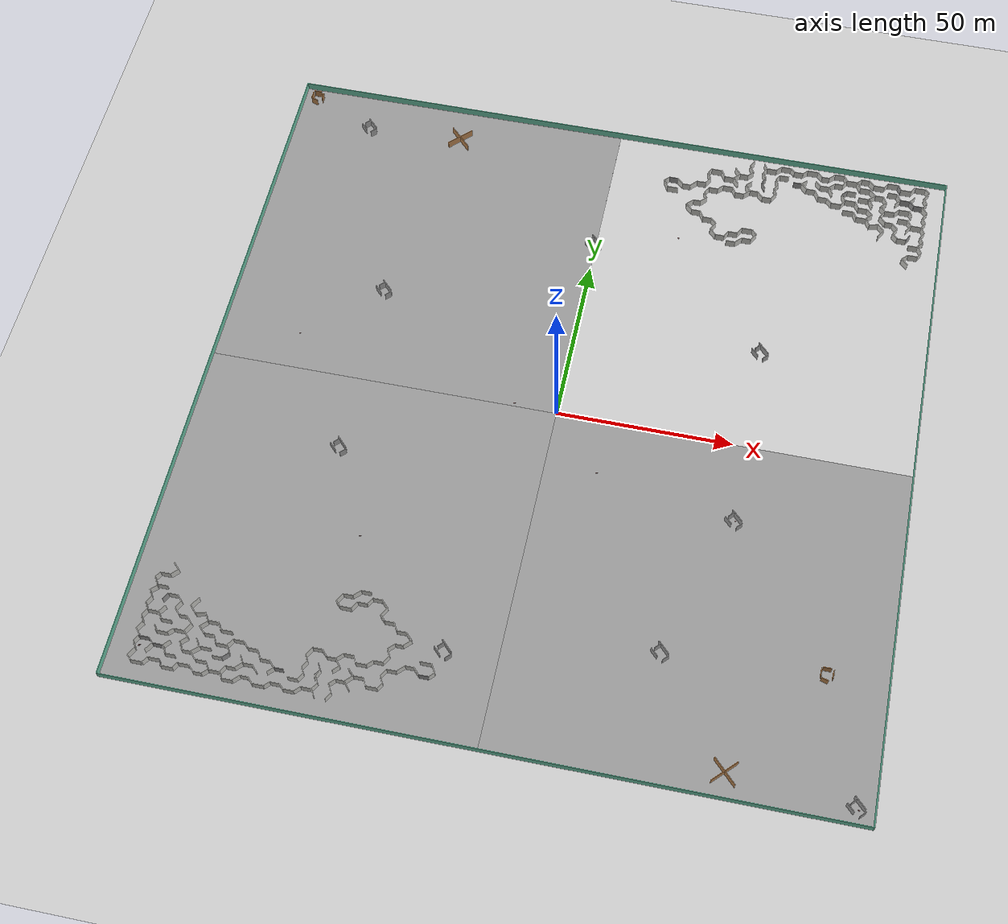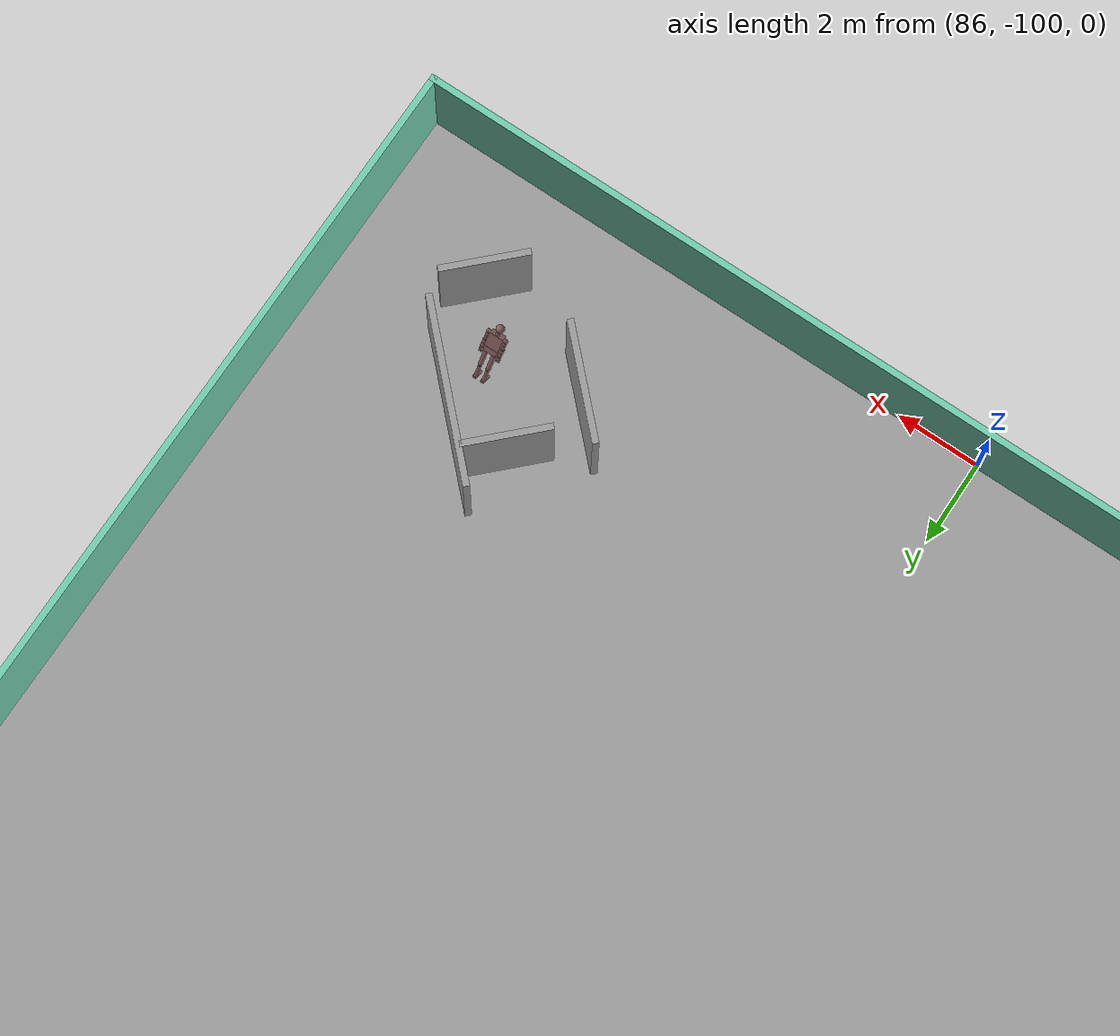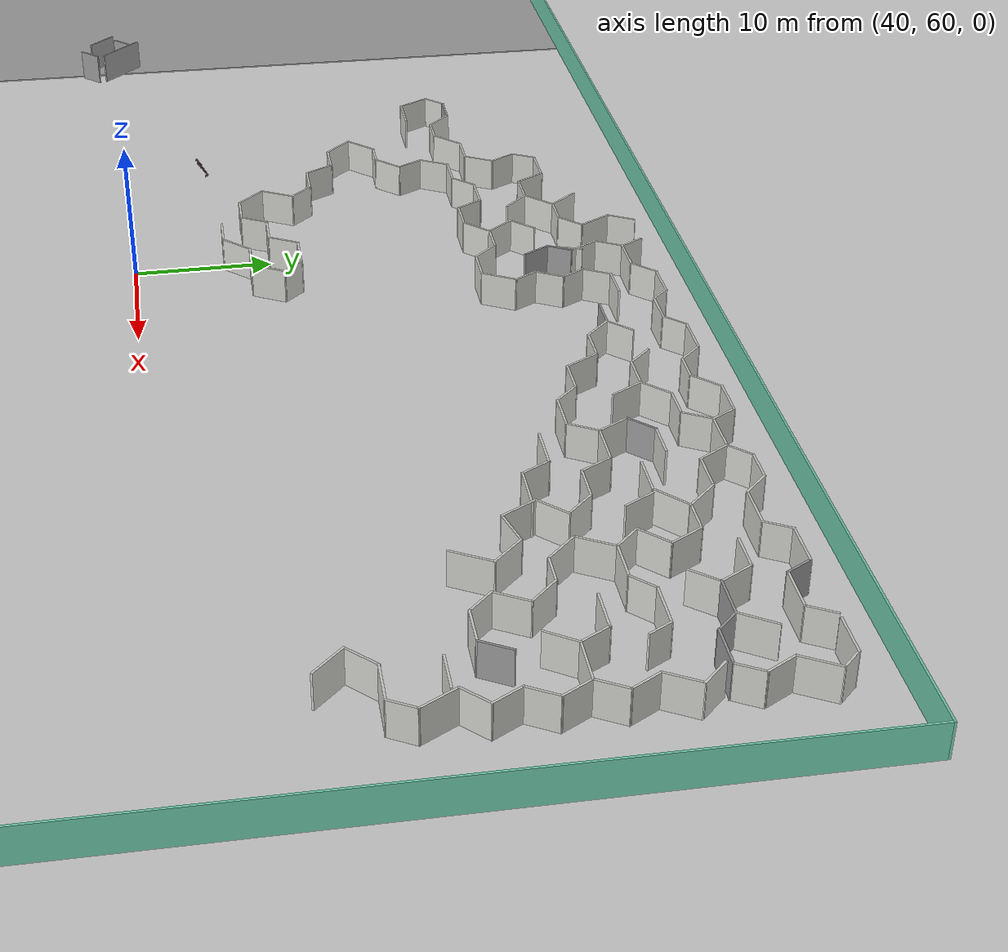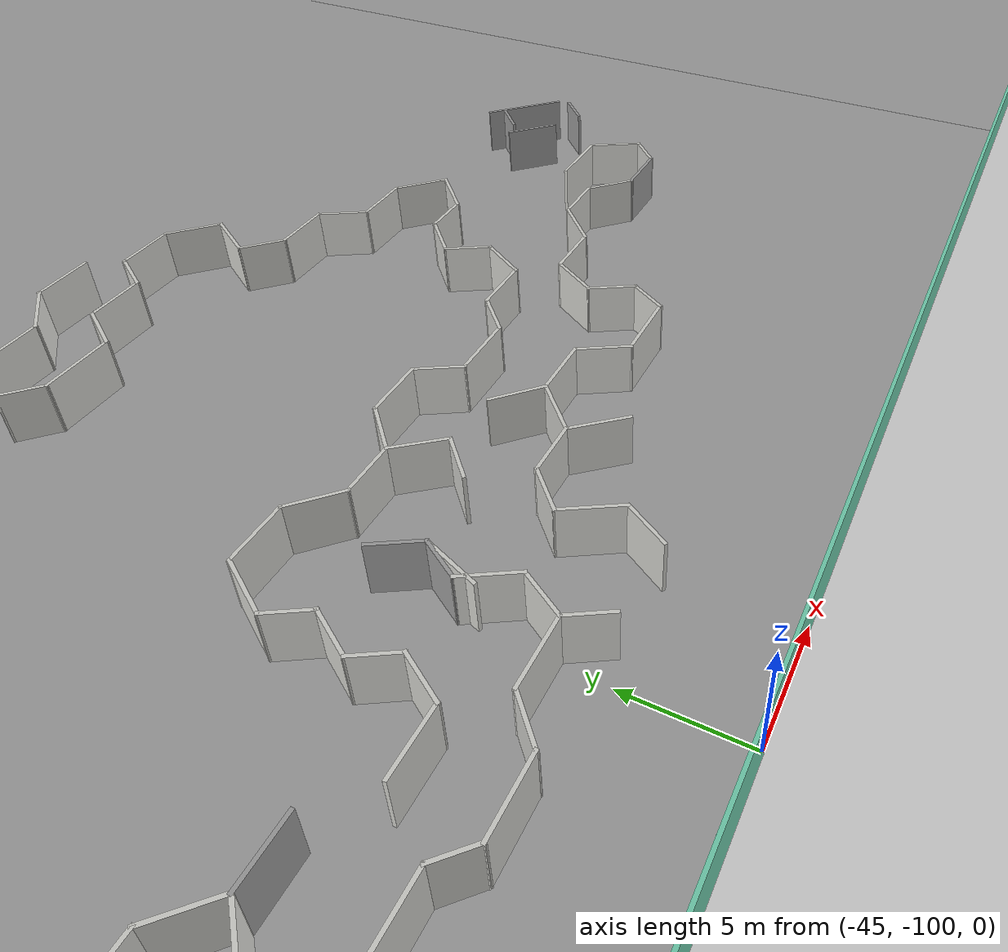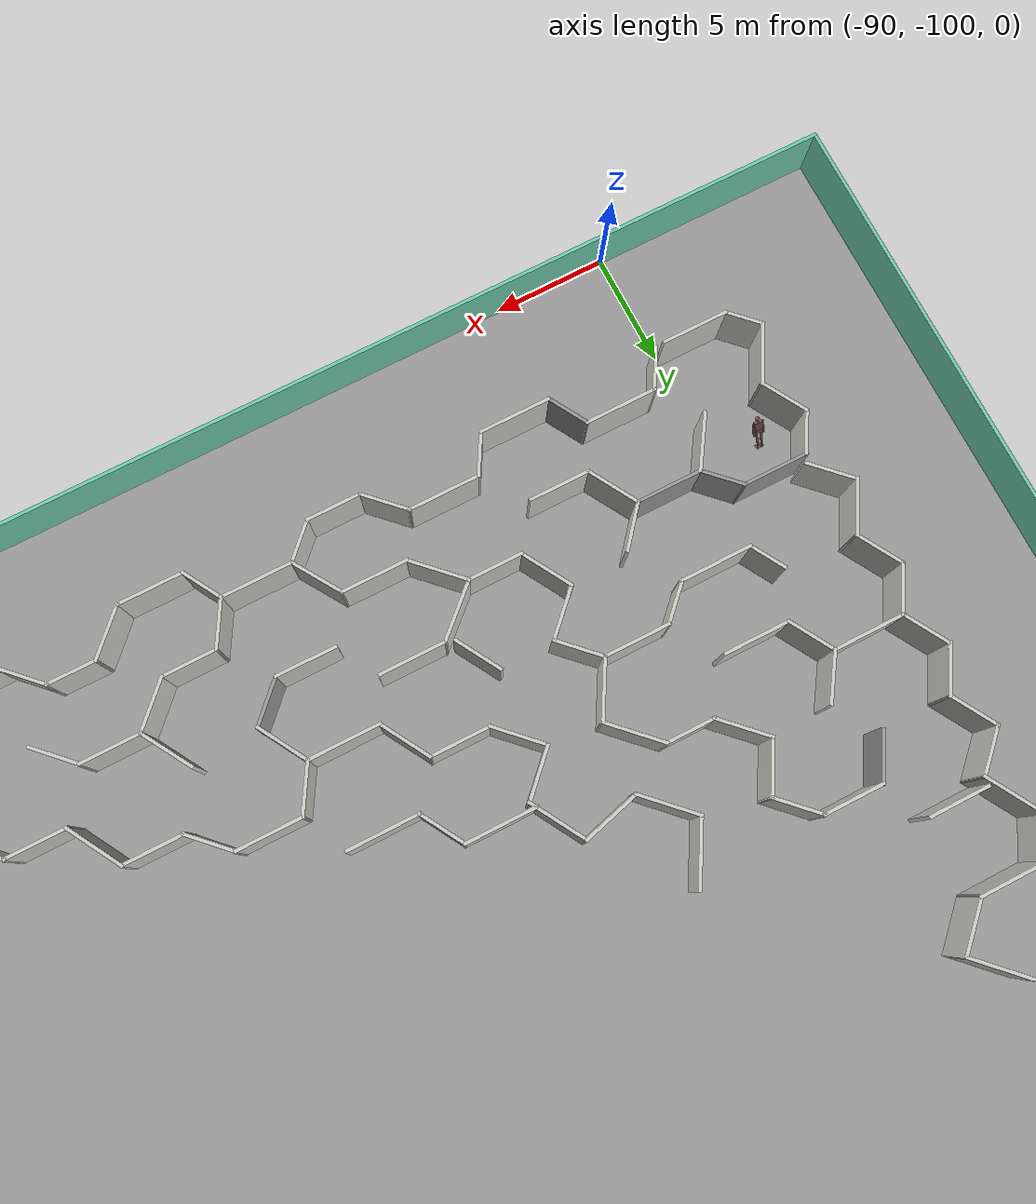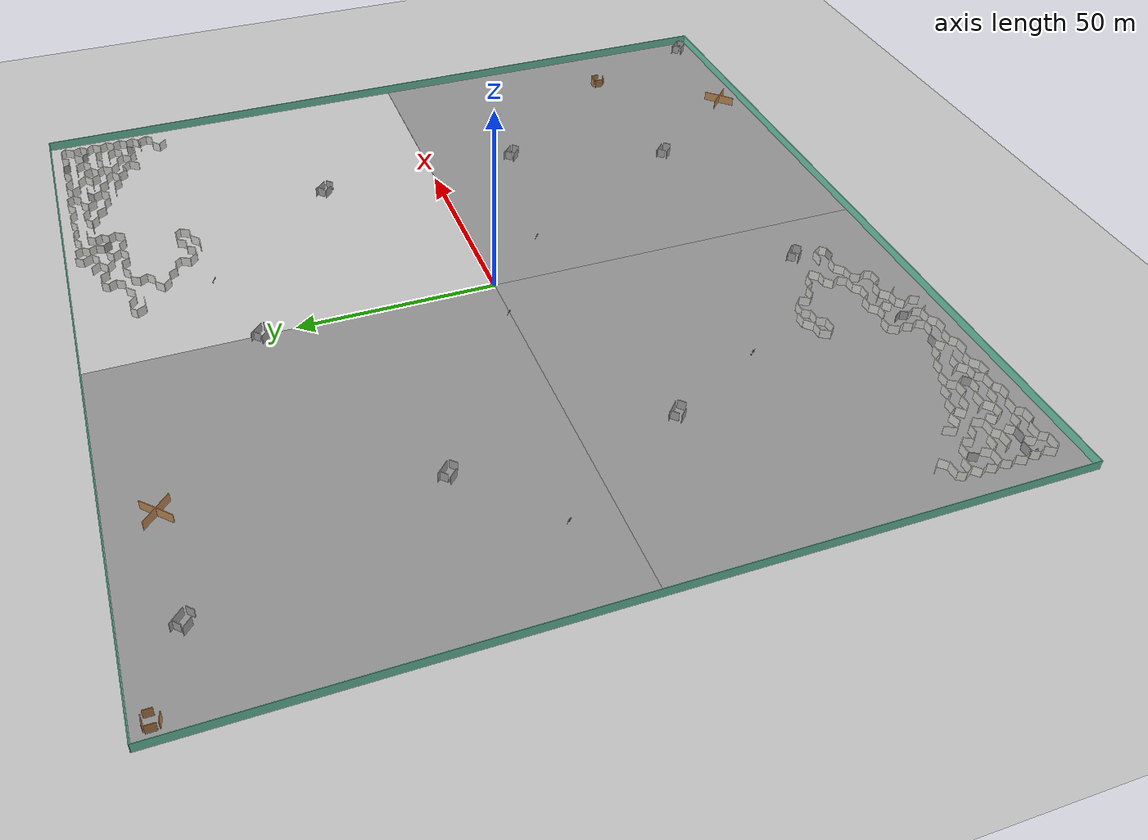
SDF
<sdf version="1.6">
 <world name="default">
  <light name="sun" type="directional">
   <pose>0 0 10 0 -0 0</pose>
   <diffuse>0.8 0.8 0.8 1</diffuse>
   <specular>0.1 0.1 0.1 1</specular>
   <attenuation>
    <range>1000</range>
    <constant>0.9</constant>
    <linear>0.01</linear>
    <quadratic>0.001</quadratic>
   </attenuation>
   <direction>-0.5 0.5 -1</direction>
  </light>
  <model name="ground_plane">
   <pose>50 50 0 0 -0 0</pose>
   <static>1</static>
   <link name="link">
    <collision name="collision">
     <geometry><plane><normal>0 0 1</normal><size>100 100</size></plane></geometry>
     <surface><friction><ode><mu>100</mu><mu2>50</mu2></ode></friction></surface>
    </collision>
    <visual name="visual">
     <cast_shadows>0</cast_shadows>
     <geometry><plane><normal>0 0 1</normal><size>100 100</size></plane></geometry>
     <material>
      <script><uri>file://media/materials/scripts/gazebo.material</uri><name>Gazebo/Grey</name></script>
     </material>
    </visual>
   </link>
  </model>
  <gravity>0 0 -9.8</gravity>
  <magnetic_field>6e-06 2.3e-05 -4.2e-05</magnetic_field>
  <atmosphere type="adiabatic"/>
  <physics name="default_physics" default="0" type="ode">
   <max_step_size>0.001</max_step_size>
   <real_time_factor>1</real_time_factor>
   <real_time_update_rate>1000</real_time_update_rate>
  </physics>
  <scene><ambient>0.4 0.4 0.4 1</ambient><background>0.7 0.7 0.7 1</background><shadows>1</shadows></scene>
  <audio><device>default</device></audio>
  <spherical_coordinates>
   <surface_model>EARTH_WGS84</surface_model>
   <latitude_deg>0</latitude_deg>
   <longitude_deg>0</longitude_deg>
   <elevation>0</elevation>
   <heading_deg>0</heading_deg>
  </spherical_coordinates>
  <model name="ground_plane_0">
   <static>1</static>
   <link name="link">
    <collision name="collision">
     <geometry><plane><normal>0 0 1</normal><size>100 100</size></plane></geometry>
     <surface><friction><ode><mu>100</mu><mu2>50</mu2></ode></friction></surface>
    </collision>
    <visual name="visual">
     <cast_shadows>0</cast_shadows>
     <geometry><plane><normal>0 0 1</normal><size>100 100</size></plane></geometry>
     <material>
      <script><uri>file://media/materials/scripts/gazebo.material</uri><name>Gazebo/Grey</name></script>
     </material>
    </visual>
   </link>
   <pose>-50 50 0 0 -0 0</pose>
  </model>
  <model name="ground_plane_1">
   <static>1</static>
   <link name="link">
    <collision name="collision">
     <geometry><plane><normal>0 0 1</normal><size>100 100</size></plane></geometry>
     <surface><friction><ode><mu>100</mu><mu2>50</mu2></ode></friction></surface>
    </collision>
    <visual name="visual">
     <cast_shadows>0</cast_shadows>
     <geometry><plane><normal>0 0 1</normal><size>100 100</size></plane></geometry>
     <material>
      <script><uri>file://media/materials/scripts/gazebo.material</uri><name>Gazebo/Grey</name></script>
     </material>
    </visual>
   </link>
   <pose>-50 -50 0 0 -0 0</pose>
  </model>
  <model name="ground_plane_2">
   <static>1</static>
   <link name="link">
    <collision name="collision">
     <geometry><plane><normal>0 0 1</normal><size>100 100</size></plane></geometry>
     <surface><friction><ode><mu>100</mu><mu2>50</mu2></ode></friction></surface>
    </collision>
    <visual name="visual">
     <cast_shadows>0</cast_shadows>
     <geometry><plane><normal>0 0 1</normal><size>100 100</size></plane></geometry>
     <material>
      <script><uri>file://media/materials/scripts/gazebo.material</uri><name>Gazebo/Grey</name></script>
     </material>
    </visual>
   </link>
   <pose>50 -50 0 0 -0 0</pose>
  </model>
  <model name="outer_wall_200m2">
   <link name="Wall_0">
    <collision name="Wall_0_Collision">
     <geometry><box><size>200.15 0.15 2.5</size></box></geometry>
     <pose>0 0 1.25 0 -0 0</pose>
    </collision>
    <visual name="Wall_0_Visual">
     <pose>0 0 1.25 0 -0 0</pose>
     <geometry><box><size>200.15 0.15 2.5</size></box></geometry>
     <material>
      <script><uri>file://media/materials/scripts/gazebo.material</uri><name>Gazebo/Grey</name></script>
      <ambient>0.435294 0.796078 0.67451 1</ambient>
     </material>
     <meta><layer>0</layer></meta>
    </visual>
    <pose>0 -100 0 0 -0 0</pose>
   </link>
   <link name="Wall_2">
    <collision name="Wall_2_Collision">
     <geometry><box><size>200.15 0.15 2.5</size></box></geometry>
     <pose>0 0 1.25 0 -0 0</pose>
    </collision>
    <visual name="Wall_2_Visual">
     <pose>0 0 1.25 0 -0 0</pose>
     <geometry><box><size>200.15 0.15 2.5</size></box></geometry>
     <material>
      <script><uri>file://media/materials/scripts/gazebo.material</uri><name>Gazebo/Grey</name></script>
      <ambient>0.435294 0.796078 0.67451 1</ambient>
     </material>
     <meta><layer>0</layer></meta>
    </visual>
    <pose>100 0 0 0 -0 1.5708</pose>
   </link>
   <link name="Wall_3">
    <collision name="Wall_3_Collision">
     <geometry><box><size>200.15 0.15 2.5</size></box></geometry>
     <pose>0 0 1.25 0 -0 0</pose>
    </collision>
    <visual name="Wall_3_Visual">
     <pose>0 0 1.25 0 -0 0</pose>
     <geometry><box><size>200.15 0.15 2.5</size></box></geometry>
     <material>
      <script><uri>file://media/materials/scripts/gazebo.material</uri><name>Gazebo/Grey</name></script>
      <ambient>0.435294 0.796078 0.67451 1</ambient>
     </material>
     <meta><layer>0</layer></meta>
    </visual>
    <pose>0 100 0 0 -0 3.14159</pose>
   </link>
   <link name="Wall_4">
    <collision name="Wall_4_Collision">
     <geometry><box><size>200.15 0.15 2.5</size></box></geometry>
     <pose>0 0 1.25 0 -0 0</pose>
    </collision>
    <visual name="Wall_4_Visual">
     <pose>0 0 1.25 0 -0 0</pose>
     <geometry><box><size>200.15 0.15 2.5</size></box></geometry>
     <material>
      <script><uri>file://media/materials/scripts/gazebo.material</uri><name>Gazebo/Grey</name></script>
      <ambient>0.435294 0.796078 0.67451 1</ambient>
     </material>
     <meta><layer>0</layer></meta>
    </visual>
    <pose>-100 0 0 0 -0 -1.5708</pose>
   </link>
   <static>1</static>
  </model>
  <model name="maze_1">
   <pose>-54.4916 -79.5001 0 0 -0 0</pose>
   <link name="Wall_10">
    <collision name="Wall_10_Collision">
     <geometry><box><size>2 0.15 2.5</size></box></geometry>
     <pose>0 0 1.25 0 -0 0</pose>
    </collision>
    <visual name="Wall_10_Visual">
     <pose>0 0 1.25 0 -0 0</pose>
     <geometry><box><size>2 0.15 2.5</size></box></geometry>
     <material>
      <script><uri>file://media/materials/scripts/gazebo.material</uri><name>Gazebo/Grey</name></script>
      <ambient>1 1 1 1</ambient>
     </material>
     <meta><layer>0</layer></meta>
    </visual>
    <pose>10.0085 -8.88058 0 0 -0 -2.0944</pose>
   </link>
   <link name="Wall_100">
    <collision name="Wall_100_Collision">
     <geometry><box><size>2.75 0.15 2.5</size></box></geometry>
     <pose>0 0 1.25 0 -0 0</pose>
    </collision>
    <visual name="Wall_100_Visual">
     <pose>0 0 1.25 0 -0 0</pose>
     <geometry><box><size>2.75 0.15 2.5</size></box></geometry>
     <material>
      <script><uri>file://media/materials/scripts/gazebo.material</uri><name>Gazebo/CeilingTiled</name></script>
      <ambient>1 1 1 1</ambient>
     </material>
     <meta><layer>0</layer></meta>
    </visual>
    <pose>-22.8053 -10.8644 0 0 -0 -0.785398</pose>
   </link>
   <link name="Wall_101">
    <collision name="Wall_101_Collision">
     <geometry><box><size>3 0.15 2.5</size></box></geometry>
     <pose>0 0 1.25 0 -0 0</pose>
    </collision>
    <visual name="Wall_101_Visual">
     <pose>0 0 1.25 0 -0 0</pose>
     <geometry><box><size>3 0.15 2.5</size></box></geometry>
     <material>
      <script><uri>file://media/materials/scripts/gazebo.material</uri><name>Gazebo/CeilingTiled</name></script>
      <ambient>1 1 1 1</ambient>
     </material>
     <meta><layer>0</layer></meta>
    </visual>
    <pose>-20.4611 -11.7836 0 0 -0 0</pose>
   </link>
   <link name="Wall_102">
    <collision name="Wall_102_Collision">
     <geometry><box><size>2.50433 0.15 2.5</size></box></geometry>
     <pose>0 0 1.25 0 -0 0</pose>
    </collision>
    <visual name="Wall_102_Visual">
     <pose>0 0 1.25 0 -0 0</pose>
     <geometry><box><size>2.50433 0.15 2.5</size></box></geometry>
     <material>
      <script><uri>file://media/materials/scripts/gazebo.material</uri><name>Gazebo/CeilingTiled</name></script>
      <ambient>1 1 1 1</ambient>
     </material>
     <meta><layer>0</layer></meta>
    </visual>
    <pose>-18.4056 -12.7777 0 0 -0 -1.00558</pose>
   </link>
   <link name="Wall_104">
    <collision name="Wall_104_Collision">
     <geometry><box><size>3 0.15 2.5</size></box></geometry>
     <pose>0 0 1.25 0 -0 0</pose>
    </collision>
    <visual name="Wall_104_Visual">
     <pose>0 0 1.25 0 -0 0</pose>
     <geometry><box><size>3 0.15 2.5</size></box></geometry>
     <material>
      <script><uri>file://media/materials/scripts/gazebo.material</uri><name>Gazebo/CeilingTiled</name></script>
      <ambient>1 1 1 1</ambient>
     </material>
     <meta><layer>0</layer></meta>
    </visual>
    <pose>-20.321 -8.13238 0 0 -0 3.14159</pose>
   </link>
   <link name="Wall_105">
    <collision name="Wall_105_Collision">
     <geometry><box><size>2.83342 0.15 2.5</size></box></geometry>
     <pose>0 0 1.25 0 -0 0</pose>
    </collision>
    <visual name="Wall_105_Visual">
     <pose>0 0 1.25 0 -0 0</pose>
     <geometry><box><size>2.83342 0.15 2.5</size></box></geometry>
     <material>
      <script><uri>file://media/materials/scripts/gazebo.material</uri><name>Gazebo/CeilingTiled</name></script>
      <ambient>1 1 1 1</ambient>
     </material>
     <meta><layer>0</layer></meta>
    </visual>
    <pose>-22.7353 -9.03876 0 0 -0 -2.39989</pose>
   </link>
   <link name="Wall_107">
    <collision name="Wall_107_Collision">
     <geometry><box><size>2.25 0.15 2.5</size></box></geometry>
     <pose>0 0 1.25 0 -0 0</pose>
    </collision>
    <visual name="Wall_107_Visual">
     <pose>0 0 1.25 0 -0 0</pose>
     <geometry><box><size>2.25 0.15 2.5</size></box></geometry>
     <material>
      <script><uri>file://media/materials/scripts/gazebo.material</uri><name>Gazebo/CeilingTiled</name></script>
      <ambient>1 1 1 1</ambient>
     </material>
     <meta><layer>0</layer></meta>
    </visual>
    <pose>-22.6837 -7.08881 0 0 -0 -1.0472</pose>
   </link>
   <link name="Wall_109">
    <collision name="Wall_109_Collision">
     <geometry><box><size>2.75 0.15 2.5</size></box></geometry>
     <pose>0 0 1.25 0 -0 0</pose>
    </collision>
    <visual name="Wall_109_Visual">
     <pose>0 0 1.25 0 -0 0</pose>
     <geometry><box><size>2.75 0.15 2.5</size></box></geometry>
     <material>
      <script><uri>file://media/materials/scripts/gazebo.material</uri><name>Gazebo/CeilingTiled</name></script>
      <ambient>1 1 1 1</ambient>
     </material>
     <meta><layer>0</layer></meta>
    </visual>
    <pose>-16.5382 -9.92253 0 0 -0 0</pose>
   </link>
   <link name="Wall_11">
    <collision name="Wall_11_Collision">
     <geometry><box><size>2.5 0.15 2.5</size></box></geometry>
     <pose>0 0 1.25 0 -0 0</pose>
    </collision>
    <visual name="Wall_11_Visual">
     <pose>0 0 1.25 0 -0 0</pose>
     <geometry><box><size>2.5 0.15 2.5</size></box></geometry>
     <material>
      <script><uri>file://media/materials/scripts/gazebo.material</uri><name>Gazebo/CeilingTiled</name></script>
      <ambient>1 1 1 1</ambient>
     </material>
     <meta><layer>0</layer></meta>
    </visual>
    <pose>10.1335 -10.6992 0 0 -0 -1.0472</pose>
   </link>
   <link name="Wall_110">
    <collision name="Wall_110_Collision">
     <geometry><box><size>2.25 0.15 2.5</size></box></geometry>
     <pose>0 0 1.25 0 -0 0</pose>
    </collision>
    <visual name="Wall_110_Visual">
     <pose>0 0 1.25 0 -0 0</pose>
     <geometry><box><size>2.25 0.15 2.5</size></box></geometry>
     <material>
      <script><uri>file://media/materials/scripts/gazebo.material</uri><name>Gazebo/Grey</name></script>
      <ambient>1 1 1 1</ambient>
     </material>
     <meta><layer>0</layer></meta>
    </visual>
    <pose>-14.4957 -9.18007 0 0 -0 0.785398</pose>
   </link>
   <link name="Wall_111">
    <collision name="Wall_111_Collision">
     <geometry><box><size>2.5 0.15 2.5</size></box></geometry>
     <pose>0 0 1.25 0 -0 0</pose>
    </collision>
    <visual name="Wall_111_Visual">
     <pose>0 0 1.25 0 -0 0</pose>
     <geometry><box><size>2.5 0.15 2.5</size></box></geometry>
     <material>
      <script><uri>file://media/materials/scripts/gazebo.material</uri><name>Gazebo/CeilingTiled</name></script>
      <ambient>1 1 1 1</ambient>
     </material>
     <meta><layer>0</layer></meta>
    </visual>
    <pose>-14.3408 -7.42003 0 0 -0 2.0944</pose>
   </link>
   <link name="Wall_112">
    <collision name="Wall_112_Collision">
     <geometry><box><size>3.25 0.15 2.5</size></box></geometry>
     <pose>0 0 1.25 0 -0 0</pose>
    </collision>
    <visual name="Wall_112_Visual">
     <pose>0 0 1.25 0 -0 0</pose>
     <geometry><box><size>3.25 0.15 2.5</size></box></geometry>
     <material>
      <script><uri>file://media/materials/scripts/gazebo.material</uri><name>Gazebo/CeilingTiled</name></script>
      <ambient>1 1 1 1</ambient>
     </material>
     <meta><layer>0</layer></meta>
    </visual>
    <pose>-16.4783 -6.40245 0 0 -0 3.14159</pose>
   </link>
   <link name="Wall_113">
    <collision name="Wall_113_Collision">
     <geometry><box><size>2.5 0.15 2.5</size></box></geometry>
     <pose>0 0 1.25 0 -0 0</pose>
    </collision>
    <visual name="Wall_113_Visual">
     <pose>0 0 1.25 0 -0 0</pose>
     <geometry><box><size>2.5 0.15 2.5</size></box></geometry>
     <material>
      <script><uri>file://media/materials/scripts/gazebo.material</uri><name>Gazebo/CeilingTiled</name></script>
      <ambient>1 1 1 1</ambient>
     </material>
     <meta><layer>0</layer></meta>
    </visual>
    <pose>-18.6158 -5.38487 0 0 -0 2.0944</pose>
   </link>
   <link name="Wall_114">
    <collision name="Wall_114_Collision">
     <geometry><box><size>2.75 0.15 2.5</size></box></geometry>
     <pose>0 0 1.25 0 -0 0</pose>
    </collision>
    <visual name="Wall_114_Visual">
     <pose>0 0 1.25 0 -0 0</pose>
     <geometry><box><size>2.75 0.15 2.5</size></box></geometry>
     <material>
      <script><uri>file://media/materials/scripts/gazebo.material</uri><name>Gazebo/CeilingTiled</name></script>
      <ambient>1 1 1 1</ambient>
     </material>
     <meta><layer>0</layer></meta>
    </visual>
    <pose>-20.5033 -4.36729 0 0 -0 3.14159</pose>
   </link>
   <link name="Wall_115">
    <collision name="Wall_115_Collision">
     <geometry><box><size>2.5 0.15 2.5</size></box></geometry>
     <pose>0 0 1.25 0 -0 0</pose>
    </collision>
    <visual name="Wall_115_Visual">
     <pose>0 0 1.25 0 -0 0</pose>
     <geometry><box><size>2.5 0.15 2.5</size></box></geometry>
     <material>
      <script><uri>file://media/materials/scripts/gazebo.material</uri><name>Gazebo/CeilingTiled</name></script>
      <ambient>1 1 1 1</ambient>
     </material>
     <meta><layer>0</layer></meta>
    </visual>
    <pose>-22.6341 -3.53644 0 0 -0 2.35619</pose>
   </link>
   <link name="Wall_116">
    <collision name="Wall_116_Collision">
     <geometry><box><size>2.5 0.15 2.5</size></box></geometry>
     <pose>0 0 1.25 0 -0 0</pose>
    </collision>
    <visual name="Wall_116_Visual">
     <pose>0 0 1.25 0 -0 0</pose>
     <geometry><box><size>2.5 0.15 2.5</size></box></geometry>
     <material>
      <script><uri>file://media/materials/scripts/gazebo.material</uri><name>Gazebo/CeilingTiled</name></script>
      <ambient>1 1 1 1</ambient>
     </material>
     <meta><layer>0</layer></meta>
    </visual>
    <pose>-22.6341 -1.87474 0 0 -0 0.785398</pose>
   </link>
   <link name="Wall_117">
    <collision name="Wall_117_Collision">
     <geometry><box><size>2.75 0.15 2.5</size></box></geometry>
     <pose>0 0 1.25 0 -0 0</pose>
    </collision>
    <visual name="Wall_117_Visual">
     <pose>0 0 1.25 0 -0 0</pose>
     <geometry><box><size>2.75 0.15 2.5</size></box></geometry>
     <material>
      <script><uri>file://media/materials/scripts/gazebo.material</uri><name>Gazebo/CeilingTiled</name></script>
      <ambient>1 1 1 1</ambient>
     </material>
     <meta><layer>0</layer></meta>
    </visual>
    <pose>-22.4533 0.081949 0 0 -0 2.0944</pose>
   </link>
   <link name="Wall_118">
    <collision name="Wall_118_Collision">
     <geometry><box><size>2.75 0.15 2.5</size></box></geometry>
     <pose>0 0 1.25 0 -0 0</pose>
    </collision>
    <visual name="Wall_118_Visual">
     <pose>0 0 1.25 0 -0 0</pose>
     <geometry><box><size>2.75 0.15 2.5</size></box></geometry>
     <material>
      <script><uri>file://media/materials/scripts/gazebo.material</uri><name>Gazebo/CeilingTiled</name></script>
      <ambient>1 1 1 1</ambient>
     </material>
     <meta><layer>0</layer></meta>
    </visual>
    <pose>-24.359 0.871317 0 0 -0 -2.87979</pose>
   </link>
   <link name="Wall_119">
    <collision name="Wall_119_Collision">
     <geometry><box><size>2.75 0.15 2.5</size></box></geometry>
     <pose>0 0 1.25 0 -0 0</pose>
    </collision>
    <visual name="Wall_119_Visual">
     <pose>0 0 1.25 0 -0 0</pose>
     <geometry><box><size>2.75 0.15 2.5</size></box></geometry>
     <material>
      <script><uri>file://media/materials/scripts/gazebo.material</uri><name>Gazebo/CeilingTiled</name></script>
      <ambient>1 1 1 1</ambient>
     </material>
     <meta><layer>0</layer></meta>
    </visual>
    <pose>-26.5339 1.45409 0 0 -0 2.35619</pose>
   </link>
   <link name="Wall_12">
    <collision name="Wall_12_Collision">
     <geometry><box><size>2.25 0.15 2.5</size></box></geometry>
     <pose>0 0 1.25 0 -0 0</pose>
    </collision>
    <visual name="Wall_12_Visual">
     <pose>0 0 1.25 0 -0 0</pose>
     <geometry><box><size>2.25 0.15 2.5</size></box></geometry>
     <material>
      <script><uri>file://media/materials/scripts/gazebo.material</uri><name>Gazebo/CeilingTiled</name></script>
      <ambient>1 1 1 1</ambient>
     </material>
     <meta><layer>0</layer></meta>
    </visual>
    <pose>10.196 -12.6261 0 0 -0 -2.0944</pose>
   </link>
   <link name="Wall_120">
    <collision name="Wall_120_Collision">
     <geometry><box><size>3 0.15 2.5</size></box></geometry>
     <pose>0 0 1.25 0 -0 0</pose>
    </collision>
    <visual name="Wall_120_Visual">
     <pose>0 0 1.25 0 -0 0</pose>
     <geometry><box><size>3 0.15 2.5</size></box></geometry>
     <material>
      <script><uri>file://media/materials/scripts/gazebo.material</uri><name>Gazebo/CeilingTiled</name></script>
      <ambient>1 1 1 1</ambient>
     </material>
     <meta><layer>0</layer></meta>
    </visual>
    <pose>-26.7407 3.60742 0 0 -0 1.0472</pose>
   </link>
   <link name="Wall_122">
    <collision name="Wall_122_Collision">
     <geometry><box><size>3.25 0.15 2.5</size></box></geometry>
     <pose>0 0 1.25 0 -0 0</pose>
    </collision>
    <visual name="Wall_122_Visual">
     <pose>0 0 1.25 0 -0 0</pose>
     <geometry><box><size>3.25 0.15 2.5</size></box></geometry>
     <material>
      <script><uri>file://media/materials/scripts/gazebo.material</uri><name>Gazebo/CeilingTiled</name></script>
      <ambient>1 1 1 1</ambient>
     </material>
     <meta><layer>0</layer></meta>
    </visual>
    <pose>-16.2961 -2.59917 0 0 -0 3.14159</pose>
   </link>
   <link name="Wall_123">
    <collision name="Wall_123_Collision">
     <geometry><box><size>2.25 0.15 2.5</size></box></geometry>
     <pose>0 0 1.25 0 -0 0</pose>
    </collision>
    <visual name="Wall_123_Visual">
     <pose>0 0 1.25 0 -0 0</pose>
     <geometry><box><size>2.25 0.15 2.5</size></box></geometry>
     <material>
      <script><uri>file://media/materials/scripts/gazebo.material</uri><name>Gazebo/CeilingTiled</name></script>
      <ambient>1 1 1 1</ambient>
     </material>
     <meta><layer>0</layer></meta>
    </visual>
    <pose>-18.3711 -1.68985 0 0 -0 2.0944</pose>
   </link>
   <link name="Wall_124">
    <collision name="Wall_124_Collision">
     <geometry><box><size>3.25 0.15 2.5</size></box></geometry>
     <pose>0 0 1.25 0 -0 0</pose>
    </collision>
    <visual name="Wall_124_Visual">
     <pose>0 0 1.25 0 -0 0</pose>
     <geometry><box><size>3.25 0.15 2.5</size></box></geometry>
     <material>
      <script><uri>file://media/materials/scripts/gazebo.material</uri><name>Gazebo/CeilingTiled</name></script>
      <ambient>1 1 1 1</ambient>
     </material>
     <meta><layer>0</layer></meta>
    </visual>
    <pose>-20.4461 -0.780521 0 0 -0 3.14159</pose>
   </link>
   <link name="Wall_126">
    <collision name="Wall_126_Collision">
     <geometry><box><size>2.5 0.15 2.5</size></box></geometry>
     <pose>0 0 1.25 0 -0 0</pose>
    </collision>
    <visual name="Wall_126_Visual">
     <pose>0 0 1.25 0 -0 0</pose>
     <geometry><box><size>2.5 0.15 2.5</size></box></geometry>
     <material>
      <script><uri>file://media/materials/scripts/gazebo.material</uri><name>Gazebo/Grey</name></script>
      <ambient>1 1 1 1</ambient>
     </material>
     <meta><layer>0</layer></meta>
    </visual>
    <pose>-0.135221 -9.92253 0 0 -0 3.14159</pose>
   </link>
   <link name="Wall_127">
    <collision name="Wall_127_Collision">
     <geometry><box><size>2.5 0.15 2.5</size></box></geometry>
     <pose>0 0 1.25 0 -0 0</pose>
    </collision>
    <visual name="Wall_127_Visual">
     <pose>0 0 1.25 0 -0 0</pose>
     <geometry><box><size>2.5 0.15 2.5</size></box></geometry>
     <material>
      <script><uri>file://media/materials/scripts/gazebo.material</uri><name>Gazebo/CeilingTiled</name></script>
      <ambient>1 1 1 1</ambient>
     </material>
     <meta><layer>0</layer></meta>
    </visual>
    <pose>-2.14107 -9.09168 0 0 -0 2.35619</pose>
   </link>
   <link name="Wall_128">
    <collision name="Wall_128_Collision">
     <geometry><box><size>2.75 0.15 2.5</size></box></geometry>
     <pose>0 0 1.25 0 -0 0</pose>
    </collision>
    <visual name="Wall_128_Visual">
     <pose>0 0 1.25 0 -0 0</pose>
     <geometry><box><size>2.75 0.15 2.5</size></box></geometry>
     <material>
      <script><uri>file://media/materials/scripts/gazebo.material</uri><name>Gazebo/CeilingTiled</name></script>
      <ambient>1 1 1 1</ambient>
     </material>
     <meta><layer>0</layer></meta>
    </visual>
    <pose>-4.27192 -8.26083 0 0 -0 3.14159</pose>
   </link>
   <link name="Wall_129">
    <collision name="Wall_129_Collision">
     <geometry><box><size>2.75 0.15 2.5</size></box></geometry>
     <pose>0 0 1.25 0 -0 0</pose>
    </collision>
    <visual name="Wall_129_Visual">
     <pose>0 0 1.25 0 -0 0</pose>
     <geometry><box><size>2.75 0.15 2.5</size></box></geometry>
     <material>
      <script><uri>file://media/materials/scripts/gazebo.material</uri><name>Gazebo/CeilingTiled</name></script>
      <ambient>1 1 1 1</ambient>
     </material>
     <meta><layer>0</layer></meta>
    </visual>
    <pose>-6.22192 -7.135 0 0 -0 2.0944</pose>
   </link>
   <link name="Wall_13">
    <collision name="Wall_13_Collision">
     <geometry><box><size>2 0.15 2.5</size></box></geometry>
     <pose>0 0 1.25 0 -0 0</pose>
    </collision>
    <visual name="Wall_13_Visual">
     <pose>0 0 1.25 0 -0 0</pose>
     <geometry><box><size>2 0.15 2.5</size></box></geometry>
     <material>
      <script><uri>file://media/materials/scripts/gazebo.material</uri><name>Gazebo/CeilingTiled</name></script>
      <ambient>1 1 1 1</ambient>
     </material>
     <meta><layer>0</layer></meta>
    </visual>
    <pose>10.1335 -14.3365 0 0 -0 -1.0472</pose>
   </link>
   <link name="Wall_130">
    <collision name="Wall_130_Collision">
     <geometry><box><size>2.75 0.15 2.5</size></box></geometry>
     <pose>0 0 1.25 0 -0 0</pose>
    </collision>
    <visual name="Wall_130_Visual">
     <pose>0 0 1.25 0 -0 0</pose>
     <geometry><box><size>2.75 0.15 2.5</size></box></geometry>
     <material>
      <script><uri>file://media/materials/scripts/gazebo.material</uri><name>Gazebo/CeilingTiled</name></script>
      <ambient>1 1 1 1</ambient>
     </material>
     <meta><layer>0</layer></meta>
    </visual>
    <pose>-8.17192 -6.00916 0 0 -0 3.14159</pose>
   </link>
   <link name="Wall_131">
    <collision name="Wall_131_Collision">
     <geometry><box><size>2.25 0.15 2.5</size></box></geometry>
     <pose>0 0 1.25 0 -0 0</pose>
    </collision>
    <visual name="Wall_131_Visual">
     <pose>0 0 1.25 0 -0 0</pose>
     <geometry><box><size>2.25 0.15 2.5</size></box></geometry>
     <material>
      <script><uri>file://media/materials/scripts/gazebo.material</uri><name>Gazebo/CeilingTiled</name></script>
      <ambient>1 1 1 1</ambient>
     </material>
     <meta><layer>0</layer></meta>
    </visual>
    <pose>-10.2144 -5.2667 0 0 -0 2.35619</pose>
   </link>
   <link name="Wall_132">
    <collision name="Wall_132_Collision">
     <geometry><box><size>3 0.15 2.5</size></box></geometry>
     <pose>0 0 1.25 0 -0 0</pose>
    </collision>
    <visual name="Wall_132_Visual">
     <pose>0 0 1.25 0 -0 0</pose>
     <geometry><box><size>3 0.15 2.5</size></box></geometry>
     <material>
      <script><uri>file://media/materials/scripts/gazebo.material</uri><name>Gazebo/CeilingTiled</name></script>
      <ambient>1 1 1 1</ambient>
     </material>
     <meta><layer>0</layer></meta>
    </visual>
    <pose>-12.3818 -4.52424 0 0 -0 3.14159</pose>
   </link>
   <link name="Wall_133">
    <collision name="Wall_133_Collision">
     <geometry><box><size>2.33753 0.15 2.5</size></box></geometry>
     <pose>0 0 1.25 0 -0 0</pose>
    </collision>
    <visual name="Wall_133_Visual">
     <pose>0 0 1.25 0 -0 0</pose>
     <geometry><box><size>2.33753 0.15 2.5</size></box></geometry>
     <material>
      <script><uri>file://media/materials/scripts/gazebo.material</uri><name>Gazebo/CeilingTiled</name></script>
      <ambient>1 1 1 1</ambient>
     </material>
     <meta><layer>0</layer></meta>
    </visual>
    <pose>-14.3676 -5.46334 0 0 -0 -2.10906</pose>
   </link>
   <link name="Wall_135">
    <collision name="Wall_135_Collision">
     <geometry><box><size>2.22826 0.15 2.5</size></box></geometry>
     <pose>0 0 1.25 0 -0 0</pose>
    </collision>
    <visual name="Wall_135_Visual">
     <pose>0 0 1.25 0 -0 0</pose>
     <geometry><box><size>2.22826 0.15 2.5</size></box></geometry>
     <material>
      <script><uri>file://media/materials/scripts/gazebo.material</uri><name>Gazebo/CeilingTiled</name></script>
      <ambient>1 1 1 1</ambient>
     </material>
     <meta><layer>0</layer></meta>
    </visual>
    <pose>-2.04743 -10.6549 0 0 -0 0.782082</pose>
   </link>
   <link name="Wall_137">
    <collision name="Wall_137_Collision">
     <geometry><box><size>2.75 0.15 2.5</size></box></geometry>
     <pose>0 0 1.25 0 -0 0</pose>
    </collision>
    <visual name="Wall_137_Visual">
     <pose>0 0 1.25 0 -0 0</pose>
     <geometry><box><size>2.75 0.15 2.5</size></box></geometry>
     <material>
      <script><uri>file://media/materials/scripts/gazebo.material</uri><name>Gazebo/CeilingTiled</name></script>
      <ambient>1 1 1 1</ambient>
     </material>
     <meta><layer>0</layer></meta>
    </visual>
    <pose>4.12993 -11.7127 0 0 -0 0</pose>
   </link>
   <link name="Wall_138">
    <collision name="Wall_138_Collision">
     <geometry><box><size>2.25 0.15 2.5</size></box></geometry>
     <pose>0 0 1.25 0 -0 0</pose>
    </collision>
    <visual name="Wall_138_Visual">
     <pose>0 0 1.25 0 -0 0</pose>
     <geometry><box><size>2.25 0.15 2.5</size></box></geometry>
     <material>
      <script><uri>file://media/materials/scripts/gazebo.material</uri><name>Gazebo/CeilingTiled</name></script>
      <ambient>1 1 1 1</ambient>
     </material>
     <meta><layer>0</layer></meta>
    </visual>
    <pose>5.95493 -10.8034 0 0 -0 1.0472</pose>
   </link>
   <link name="Wall_139">
    <collision name="Wall_139_Collision">
     <geometry><box><size>2 0.15 2.5</size></box></geometry>
     <pose>0 0 1.25 0 -0 0</pose>
    </collision>
    <visual name="Wall_139_Visual">
     <pose>0 0 1.25 0 -0 0</pose>
     <geometry><box><size>2 0.15 2.5</size></box></geometry>
     <material>
      <script><uri>file://media/materials/scripts/gazebo.material</uri><name>Gazebo/CeilingTiled</name></script>
      <ambient>1 1 1 1</ambient>
     </material>
     <meta><layer>0</layer></meta>
    </visual>
    <pose>6.01743 -9.09296 0 0 -0 2.0944</pose>
   </link>
   <link name="Wall_140">
    <collision name="Wall_140_Collision">
     <geometry><box><size>2.25 0.15 2.5</size></box></geometry>
     <pose>0 0 1.25 0 -0 0</pose>
    </collision>
    <visual name="Wall_140_Visual">
     <pose>0 0 1.25 0 -0 0</pose>
     <geometry><box><size>2.25 0.15 2.5</size></box></geometry>
     <material>
      <script><uri>file://media/materials/scripts/gazebo.material</uri><name>Gazebo/CeilingTiled</name></script>
      <ambient>1 1 1 1</ambient>
     </material>
     <meta><layer>0</layer></meta>
    </visual>
    <pose>6.07993 -7.38256 0 0 -0 1.0472</pose>
   </link>
   <link name="Wall_141">
    <collision name="Wall_141_Collision">
     <geometry><box><size>2 0.15 2.5</size></box></geometry>
     <pose>0 0 1.25 0 -0 0</pose>
    </collision>
    <visual name="Wall_141_Visual">
     <pose>0 0 1.25 0 -0 0</pose>
     <geometry><box><size>2 0.15 2.5</size></box></geometry>
     <material>
      <script><uri>file://media/materials/scripts/gazebo.material</uri><name>Gazebo/CeilingTiled</name></script>
      <ambient>1 1 1 1</ambient>
     </material>
     <meta><layer>0</layer></meta>
    </visual>
    <pose>6.14243 -5.67216 0 0 -0 2.0944</pose>
   </link>
   <link name="Wall_142">
    <collision name="Wall_142_Collision">
     <geometry><box><size>2.75 0.15 2.5</size></box></geometry>
     <pose>0 0 1.25 0 -0 0</pose>
    </collision>
    <visual name="Wall_142_Visual">
     <pose>0 0 1.25 0 -0 0</pose>
     <geometry><box><size>2.75 0.15 2.5</size></box></geometry>
     <material>
      <script><uri>file://media/materials/scripts/gazebo.material</uri><name>Gazebo/CeilingTiled</name></script>
      <ambient>1 1 1 1</ambient>
     </material>
     <meta><layer>0</layer></meta>
    </visual>
    <pose>6.32993 -3.74525 0 0 -0 1.0472</pose>
   </link>
   <link name="Wall_143">
    <collision name="Wall_143_Collision">
     <geometry><box><size>2.75 0.15 2.5</size></box></geometry>
     <pose>0 0 1.25 0 -0 0</pose>
    </collision>
    <visual name="Wall_143_Visual">
     <pose>0 0 1.25 0 -0 0</pose>
     <geometry><box><size>2.75 0.15 2.5</size></box></geometry>
     <material>
      <script><uri>file://media/materials/scripts/gazebo.material</uri><name>Gazebo/CeilingTiled</name></script>
      <ambient>1 1 1 1</ambient>
     </material>
     <meta><layer>0</layer></meta>
    </visual>
    <pose>8.27993 -2.61942 0 0 -0 0</pose>
   </link>
   <link name="Wall_144">
    <collision name="Wall_144_Collision">
     <geometry><box><size>2.5 0.15 2.5</size></box></geometry>
     <pose>0 0 1.25 0 -0 0</pose>
    </collision>
    <visual name="Wall_144_Visual">
     <pose>0 0 1.25 0 -0 0</pose>
     <geometry><box><size>2.5 0.15 2.5</size></box></geometry>
     <material>
      <script><uri>file://media/materials/scripts/gazebo.material</uri><name>Gazebo/CeilingTiled</name></script>
      <ambient>1 1 1 1</ambient>
     </material>
     <meta><layer>0</layer></meta>
    </visual>
    <pose>10.4108 -3.45027 0 0 -0 -0.785398</pose>
   </link>
   <link name="Wall_145">
    <collision name="Wall_145_Collision">
     <geometry><box><size>2.5 0.15 2.5</size></box></geometry>
     <pose>0 0 1.25 0 -0 0</pose>
    </collision>
    <visual name="Wall_145_Visual">
     <pose>0 0 1.25 0 -0 0</pose>
     <geometry><box><size>2.5 0.15 2.5</size></box></geometry>
     <material>
      <script><uri>file://media/materials/scripts/gazebo.material</uri><name>Gazebo/CeilingTiled</name></script>
      <ambient>1 1 1 1</ambient>
     </material>
     <meta><layer>0</layer></meta>
    </visual>
    <pose>12.4166 -4.28112 0 0 -0 0</pose>
   </link>
   <link name="Wall_146">
    <collision name="Wall_146_Collision">
     <geometry><box><size>2.5 0.15 2.5</size></box></geometry>
     <pose>0 0 1.25 0 -0 0</pose>
    </collision>
    <visual name="Wall_146_Visual">
     <pose>0 0 1.25 0 -0 0</pose>
     <geometry><box><size>2.5 0.15 2.5</size></box></geometry>
     <material>
      <script><uri>file://media/materials/scripts/gazebo.material</uri><name>Gazebo/CeilingTiled</name></script>
      <ambient>1 1 1 1</ambient>
     </material>
     <meta><layer>0</layer></meta>
    </visual>
    <pose>14.4225 -3.45027 0 0 -0 0.785398</pose>
   </link>
   <link name="Wall_147">
    <collision name="Wall_147_Collision">
     <geometry><box><size>2.75 0.15 2.5</size></box></geometry>
     <pose>0 0 1.25 0 -0 0</pose>
    </collision>
    <visual name="Wall_147_Visual">
     <pose>0 0 1.25 0 -0 0</pose>
     <geometry><box><size>2.75 0.15 2.5</size></box></geometry>
     <material>
      <script><uri>file://media/materials/scripts/gazebo.material</uri><name>Gazebo/CeilingTiled</name></script>
      <ambient>1 1 1 1</ambient>
     </material>
     <meta><layer>0</layer></meta>
    </visual>
    <pose>16.5533 -2.61942 0 0 -0 0</pose>
   </link>
   <link name="Wall_148">
    <collision name="Wall_148_Collision">
     <geometry><box><size>2.25 0.15 2.5</size></box></geometry>
     <pose>0 0 1.25 0 -0 0</pose>
    </collision>
    <visual name="Wall_148_Visual">
     <pose>0 0 1.25 0 -0 0</pose>
     <geometry><box><size>2.25 0.15 2.5</size></box></geometry>
     <material>
      <script><uri>file://media/materials/scripts/gazebo.material</uri><name>Gazebo/CeilingTiled</name></script>
      <ambient>1 1 1 1</ambient>
     </material>
     <meta><layer>0</layer></meta>
    </visual>
    <pose>18.3783 -3.52874 0 0 -0 -1.0472</pose>
   </link>
   <link name="Wall_149">
    <collision name="Wall_149_Collision">
     <geometry><box><size>3 0.15 2.5</size></box></geometry>
     <pose>0 0 1.25 0 -0 0</pose>
    </collision>
    <visual name="Wall_149_Visual">
     <pose>0 0 1.25 0 -0 0</pose>
     <geometry><box><size>3 0.15 2.5</size></box></geometry>
     <material>
      <script><uri>file://media/materials/scripts/gazebo.material</uri><name>Gazebo/CeilingTiled</name></script>
      <ambient>1 1 1 1</ambient>
     </material>
     <meta><layer>0</layer></meta>
    </visual>
    <pose>20.3283 -4.43807 0 0 -0 0</pose>
   </link>
   <link name="Wall_15">
    <collision name="Wall_15_Collision">
     <geometry><box><size>3 0.15 2.5</size></box></geometry>
     <pose>0 0 1.25 0 -0 0</pose>
    </collision>
    <visual name="Wall_15_Visual">
     <pose>0 0 1.25 0 -0 0</pose>
     <geometry><box><size>3 0.15 2.5</size></box></geometry>
     <material>
      <script><uri>file://media/materials/scripts/gazebo.material</uri><name>Gazebo/CeilingTiled</name></script>
      <ambient>1 1 1 1</ambient>
     </material>
     <meta><layer>0</layer></meta>
    </visual>
    <pose>8.24595 -13.5355 0 0 -0 3.14159</pose>
   </link>
   <link name="Wall_150">
    <collision name="Wall_150_Collision">
     <geometry><box><size>2.25 0.15 2.5</size></box></geometry>
     <pose>0 0 1.25 0 -0 0</pose>
    </collision>
    <visual name="Wall_150_Visual">
     <pose>0 0 1.25 0 -0 0</pose>
     <geometry><box><size>2.25 0.15 2.5</size></box></geometry>
     <material>
      <script><uri>file://media/materials/scripts/gazebo.material</uri><name>Gazebo/CeilingTiled</name></script>
      <ambient>1 1 1 1</ambient>
     </material>
     <meta><layer>0</layer></meta>
    </visual>
    <pose>22.4958 -3.69561 0 0 -0 0.785398</pose>
   </link>
   <link name="Wall_151">
    <collision name="Wall_151_Collision">
     <geometry><box><size>2.75 0.15 2.5</size></box></geometry>
     <pose>0 0 1.25 0 -0 0</pose>
    </collision>
    <visual name="Wall_151_Visual">
     <pose>0 0 1.25 0 -0 0</pose>
     <geometry><box><size>2.75 0.15 2.5</size></box></geometry>
     <material>
      <script><uri>file://media/materials/scripts/gazebo.material</uri><name>Gazebo/CeilingTiled</name></script>
      <ambient>1 1 1 1</ambient>
     </material>
     <meta><layer>0</layer></meta>
    </visual>
    <pose>24.5383 -2.95315 0 0 -0 0</pose>
   </link>
   <link name="Wall_152">
    <collision name="Wall_152_Collision">
     <geometry><box><size>2.5 0.15 2.5</size></box></geometry>
     <pose>0 0 1.25 0 -0 0</pose>
    </collision>
    <visual name="Wall_152_Visual">
     <pose>0 0 1.25 0 -0 0</pose>
     <geometry><box><size>2.5 0.15 2.5</size></box></geometry>
     <material>
      <script><uri>file://media/materials/scripts/gazebo.material</uri><name>Gazebo/CeilingTiled</name></script>
      <ambient>1 1 1 1</ambient>
     </material>
     <meta><layer>0</layer></meta>
    </visual>
    <pose>26.4258 -1.93557 0 0 -0 1.0472</pose>
   </link>
   <link name="Wall_153">
    <collision name="Wall_153_Collision">
     <geometry><box><size>2.25 0.15 2.5</size></box></geometry>
     <pose>0 0 1.25 0 -0 0</pose>
    </collision>
    <visual name="Wall_153_Visual">
     <pose>0 0 1.25 0 -0 0</pose>
     <geometry><box><size>2.25 0.15 2.5</size></box></geometry>
     <material>
      <script><uri>file://media/materials/scripts/gazebo.material</uri><name>Gazebo/CeilingTiled</name></script>
      <ambient>1 1 1 1</ambient>
     </material>
     <meta><layer>0</layer></meta>
    </visual>
    <pose>26.4883 -0.00866 0 0 -0 2.0944</pose>
   </link>
   <link name="Wall_154">
    <collision name="Wall_154_Collision">
     <geometry><box><size>2.5 0.15 2.5</size></box></geometry>
     <pose>0 0 1.25 0 -0 0</pose>
    </collision>
    <visual name="Wall_154_Visual">
     <pose>0 0 1.25 0 -0 0</pose>
     <geometry><box><size>2.5 0.15 2.5</size></box></geometry>
     <material>
      <script><uri>file://media/materials/scripts/gazebo.material</uri><name>Gazebo/CeilingTiled</name></script>
      <ambient>1 1 1 1</ambient>
     </material>
     <meta><layer>0</layer></meta>
    </visual>
    <pose>26.7941 1.73152 0 0 -0 0.785398</pose>
   </link>
   <link name="Wall_155">
    <collision name="Wall_155_Collision">
     <geometry><box><size>2.25 0.15 2.5</size></box></geometry>
     <pose>0 0 1.25 0 -0 0</pose>
    </collision>
    <visual name="Wall_155_Visual">
     <pose>0 0 1.25 0 -0 0</pose>
     <geometry><box><size>2.25 0.15 2.5</size></box></geometry>
     <material>
      <script><uri>file://media/materials/scripts/gazebo.material</uri><name>Gazebo/CeilingTiled</name></script>
      <ambient>1 1 1 1</ambient>
     </material>
     <meta><layer>0</layer></meta>
    </visual>
    <pose>28.675 2.56237 0 0 -0 0</pose>
   </link>
   <link name="Wall_156">
    <collision name="Wall_156_Collision">
     <geometry><box><size>2.75 0.15 2.5</size></box></geometry>
     <pose>0 0 1.25 0 -0 0</pose>
    </collision>
    <visual name="Wall_156_Visual">
     <pose>0 0 1.25 0 -0 0</pose>
     <geometry><box><size>2.75 0.15 2.5</size></box></geometry>
     <material>
      <script><uri>file://media/materials/scripts/gazebo.material</uri><name>Gazebo/CeilingTiled</name></script>
      <ambient>1 1 1 1</ambient>
     </material>
     <meta><layer>0</layer></meta>
    </visual>
    <pose>30.6442 3.48161 0 0 -0 0.785398</pose>
   </link>
   <link name="Wall_157">
    <collision name="Wall_157_Collision">
     <geometry><box><size>2.75 0.15 2.5</size></box></geometry>
     <pose>0 0 1.25 0 -0 0</pose>
    </collision>
    <visual name="Wall_157_Visual">
     <pose>0 0 1.25 0 -0 0</pose>
     <geometry><box><size>2.75 0.15 2.5</size></box></geometry>
     <material>
      <script><uri>file://media/materials/scripts/gazebo.material</uri><name>Gazebo/CeilingTiled</name></script>
      <ambient>1 1 1 1</ambient>
     </material>
     <meta><layer>0</layer></meta>
    </visual>
    <pose>30.6442 5.32008 0 0 -0 2.35619</pose>
   </link>
   <link name="Wall_158">
    <collision name="Wall_158_Collision">
     <geometry><box><size>2.75 0.15 2.5</size></box></geometry>
     <pose>0 0 1.25 0 -0 0</pose>
    </collision>
    <visual name="Wall_158_Visual">
     <pose>0 0 1.25 0 -0 0</pose>
     <geometry><box><size>2.75 0.15 2.5</size></box></geometry>
     <material>
      <script><uri>file://media/materials/scripts/gazebo.material</uri><name>Gazebo/CeilingTiled</name></script>
      <ambient>1 1 1 1</ambient>
     </material>
     <meta><layer>0</layer></meta>
    </visual>
    <pose>28.425 6.23932 0 0 -0 3.14159</pose>
   </link>
   <link name="Wall_159">
    <collision name="Wall_159_Collision">
     <geometry><box><size>2.5 0.15 2.5</size></box></geometry>
     <pose>0 0 1.25 0 -0 0</pose>
    </collision>
    <visual name="Wall_159_Visual">
     <pose>0 0 1.25 0 -0 0</pose>
     <geometry><box><size>2.5 0.15 2.5</size></box></geometry>
     <material>
      <script><uri>file://media/materials/scripts/gazebo.material</uri><name>Gazebo/CeilingTiled</name></script>
      <ambient>1 1 1 1</ambient>
     </material>
     <meta><layer>0</layer></meta>
    </visual>
    <pose>26.5375 7.2569 0 0 -0 2.0944</pose>
   </link>
   <link name="Wall_16">
    <collision name="Wall_16_Collision">
     <geometry><box><size>2.25 0.15 2.5</size></box></geometry>
     <pose>0 0 1.25 0 -0 0</pose>
    </collision>
    <visual name="Wall_16_Visual">
     <pose>0 0 1.25 0 -0 0</pose>
     <geometry><box><size>2.25 0.15 2.5</size></box></geometry>
     <material>
      <script><uri>file://media/materials/scripts/gazebo.material</uri><name>Gazebo/CeilingTiled</name></script>
      <ambient>1 1 1 1</ambient>
     </material>
     <meta><layer>0</layer></meta>
    </visual>
    <pose>6.07849 -14.2779 0 0 -0 -2.35619</pose>
   </link>
   <link name="Wall_160">
    <collision name="Wall_160_Collision">
     <geometry><box><size>2.75 0.15 2.5</size></box></geometry>
     <pose>0 0 1.25 0 -0 0</pose>
    </collision>
    <visual name="Wall_160_Visual">
     <pose>0 0 1.25 0 -0 0</pose>
     <geometry><box><size>2.75 0.15 2.5</size></box></geometry>
     <material>
      <script><uri>file://media/materials/scripts/gazebo.material</uri><name>Gazebo/CeilingTiled</name></script>
      <ambient>1 1 1 1</ambient>
     </material>
     <meta><layer>0</layer></meta>
    </visual>
    <pose>24.65 8.27448 0 0 -0 3.14159</pose>
   </link>
   <link name="Wall_161">
    <collision name="Wall_161_Collision">
     <geometry><box><size>2.25 0.15 2.5</size></box></geometry>
     <pose>0 0 1.25 0 -0 0</pose>
    </collision>
    <visual name="Wall_161_Visual">
     <pose>0 0 1.25 0 -0 0</pose>
     <geometry><box><size>2.25 0.15 2.5</size></box></geometry>
     <material>
      <script><uri>file://media/materials/scripts/gazebo.material</uri><name>Gazebo/CeilingTiled</name></script>
      <ambient>1 1 1 1</ambient>
     </material>
     <meta><layer>0</layer></meta>
    </visual>
    <pose>22.6075 9.01694 0 0 -0 2.35619</pose>
   </link>
   <link name="Wall_162">
    <collision name="Wall_162_Collision">
     <geometry><box><size>2.75 0.15 2.5</size></box></geometry>
     <pose>0 0 1.25 0 -0 0</pose>
    </collision>
    <visual name="Wall_162_Visual">
     <pose>0 0 1.25 0 -0 0</pose>
     <geometry><box><size>2.75 0.15 2.5</size></box></geometry>
     <material>
      <script><uri>file://media/materials/scripts/gazebo.material</uri><name>Gazebo/CeilingTiled</name></script>
      <ambient>1 1 1 1</ambient>
     </material>
     <meta><layer>0</layer></meta>
    </visual>
    <pose>22.515 10.8852 0 0 -0 1.0472</pose>
   </link>
   <link name="Wall_163">
    <collision name="Wall_163_Collision">
     <geometry><box><size>2.75 0.15 2.5</size></box></geometry>
     <pose>0 0 1.25 0 -0 0</pose>
    </collision>
    <visual name="Wall_163_Visual">
     <pose>0 0 1.25 0 -0 0</pose>
     <geometry><box><size>2.75 0.15 2.5</size></box></geometry>
     <material>
      <script><uri>file://media/materials/scripts/gazebo.material</uri><name>Gazebo/CeilingTiled</name></script>
      <ambient>1 1 1 1</ambient>
     </material>
     <meta><layer>0</layer></meta>
    </visual>
    <pose>22.2458 12.9303 0 0 -0 2.35619</pose>
   </link>
   <link name="Wall_164">
    <collision name="Wall_164_Collision">
     <geometry><box><size>2.75 0.15 2.5</size></box></geometry>
     <pose>0 0 1.25 0 -0 0</pose>
    </collision>
    <visual name="Wall_164_Visual">
     <pose>0 0 1.25 0 -0 0</pose>
     <geometry><box><size>2.75 0.15 2.5</size></box></geometry>
     <material>
      <script><uri>file://media/materials/scripts/gazebo.material</uri><name>Gazebo/CeilingTiled</name></script>
      <ambient>1 1 1 1</ambient>
     </material>
     <meta><layer>0</layer></meta>
    </visual>
    <pose>20.0266 13.8496 0 0 -0 3.14159</pose>
   </link>
   <link name="Wall_165">
    <collision name="Wall_165_Collision">
     <geometry><box><size>2.25 0.15 2.5</size></box></geometry>
     <pose>0 0 1.25 0 -0 0</pose>
    </collision>
    <visual name="Wall_165_Visual">
     <pose>0 0 1.25 0 -0 0</pose>
     <geometry><box><size>2.25 0.15 2.5</size></box></geometry>
     <material>
      <script><uri>file://media/materials/scripts/gazebo.material</uri><name>Gazebo/CeilingTiled</name></script>
      <ambient>1 1 1 1</ambient>
     </material>
     <meta><layer>0</layer></meta>
    </visual>
    <pose>18.2016 12.9402 0 0 -0 -2.0944</pose>
   </link>
   <link name="Wall_166">
    <collision name="Wall_166_Collision">
     <geometry><box><size>2.75 0.15 2.5</size></box></geometry>
     <pose>0 0 1.25 0 -0 0</pose>
    </collision>
    <visual name="Wall_166_Visual">
     <pose>0 0 1.25 0 -0 0</pose>
     <geometry><box><size>2.75 0.15 2.5</size></box></geometry>
     <material>
      <script><uri>file://media/materials/scripts/gazebo.material</uri><name>Gazebo/CeilingTiled</name></script>
      <ambient>1 1 1 1</ambient>
     </material>
     <meta><layer>0</layer></meta>
    </visual>
    <pose>16.3766 12.0309 0 0 -0 3.14159</pose>
   </link>
   <link name="Wall_167">
    <collision name="Wall_167_Collision">
     <geometry><box><size>2.5 0.15 2.5</size></box></geometry>
     <pose>0 0 1.25 0 -0 0</pose>
    </collision>
    <visual name="Wall_167_Visual">
     <pose>0 0 1.25 0 -0 0</pose>
     <geometry><box><size>2.5 0.15 2.5</size></box></geometry>
     <material>
      <script><uri>file://media/materials/scripts/gazebo.material</uri><name>Gazebo/CeilingTiled</name></script>
      <ambient>1 1 1 1</ambient>
     </material>
     <meta><layer>0</layer></meta>
    </visual>
    <pose>14.4891 11.0133 0 0 -0 -2.0944</pose>
   </link>
   <link name="Wall_168">
    <collision name="Wall_168_Collision">
     <geometry><box><size>3.25 0.15 2.5</size></box></geometry>
     <pose>0 0 1.25 0 -0 0</pose>
    </collision>
    <visual name="Wall_168_Visual">
     <pose>0 0 1.25 0 -0 0</pose>
     <geometry><box><size>3.25 0.15 2.5</size></box></geometry>
     <material>
      <script><uri>file://media/materials/scripts/gazebo.material</uri><name>Gazebo/CeilingTiled</name></script>
      <ambient>1 1 1 1</ambient>
     </material>
     <meta><layer>0</layer></meta>
    </visual>
    <pose>12.3516 9.99574 0 0 -0 3.14159</pose>
   </link>
   <link name="Wall_169">
    <collision name="Wall_169_Collision">
     <geometry><box><size>2 0.15 2.5</size></box></geometry>
     <pose>0 0 1.25 0 -0 0</pose>
    </collision>
    <visual name="Wall_169_Visual">
     <pose>0 0 1.25 0 -0 0</pose>
     <geometry><box><size>2 0.15 2.5</size></box></geometry>
     <material>
      <script><uri>file://media/materials/scripts/gazebo.material</uri><name>Gazebo/CeilingTiled</name></script>
      <ambient>1 1 1 1</ambient>
     </material>
     <meta><layer>0</layer></meta>
    </visual>
    <pose>10.1475 10.6498 0 0 -0 2.35619</pose>
   </link>
   <link name="Wall_17">
    <collision name="Wall_17_Collision">
     <geometry><box><size>3 0.15 2.5</size></box></geometry>
     <pose>0 0 1.25 0 -0 0</pose>
    </collision>
    <visual name="Wall_17_Visual">
     <pose>0 0 1.25 0 -0 0</pose>
     <geometry><box><size>3 0.15 2.5</size></box></geometry>
     <material>
      <script><uri>file://media/materials/scripts/gazebo.material</uri><name>Gazebo/CeilingTiled</name></script>
      <ambient>1 1 1 1</ambient>
     </material>
     <meta><layer>0</layer></meta>
    </visual>
    <pose>3.91103 -15.0204 0 0 -0 3.14159</pose>
   </link>
   <link name="Wall_170">
    <collision name="Wall_170_Collision">
     <geometry><box><size>2.75 0.15 2.5</size></box></geometry>
     <pose>0 0 1.25 0 -0 0</pose>
    </collision>
    <visual name="Wall_170_Visual">
     <pose>0 0 1.25 0 -0 0</pose>
     <geometry><box><size>2.75 0.15 2.5</size></box></geometry>
     <material>
      <script><uri>file://media/materials/scripts/gazebo.material</uri><name>Gazebo/CeilingTiled</name></script>
      <ambient>1 1 1 1</ambient>
     </material>
     <meta><layer>0</layer></meta>
    </visual>
    <pose>10.1434 12.4297 0 0 -0 1.0472</pose>
   </link>
   <link name="Wall_171">
    <collision name="Wall_171_Collision">
     <geometry><box><size>2.75 0.15 2.5</size></box></geometry>
     <pose>0 0 1.25 0 -0 0</pose>
    </collision>
    <visual name="Wall_171_Visual">
     <pose>0 0 1.25 0 -0 0</pose>
     <geometry><box><size>2.75 0.15 2.5</size></box></geometry>
     <material>
      <script><uri>file://media/materials/scripts/gazebo.material</uri><name>Gazebo/CeilingTiled</name></script>
      <ambient>1 1 1 1</ambient>
     </material>
     <meta><layer>0</layer></meta>
    </visual>
    <pose>12.0934 13.5556 0 0 -0 0</pose>
   </link>
   <link name="Wall_172">
    <collision name="Wall_172_Collision">
     <geometry><box><size>2.75 0.15 2.5</size></box></geometry>
     <pose>0 0 1.25 0 -0 0</pose>
    </collision>
    <visual name="Wall_172_Visual">
     <pose>0 0 1.25 0 -0 0</pose>
     <geometry><box><size>2.75 0.15 2.5</size></box></geometry>
     <material>
      <script><uri>file://media/materials/scripts/gazebo.material</uri><name>Gazebo/CeilingTiled</name></script>
      <ambient>1 1 1 1</ambient>
     </material>
     <meta><layer>0</layer></meta>
    </visual>
    <pose>14.3126 14.4748 0 0 -0 0.785398</pose>
   </link>
   <link name="Wall_173">
    <collision name="Wall_173_Collision">
     <geometry><box><size>2.75 0.15 2.5</size></box></geometry>
     <pose>0 0 1.25 0 -0 0</pose>
    </collision>
    <visual name="Wall_173_Visual">
     <pose>0 0 1.25 0 -0 0</pose>
     <geometry><box><size>2.75 0.15 2.5</size></box></geometry>
     <material>
      <script><uri>file://media/materials/scripts/gazebo.material</uri><name>Gazebo/CeilingTiled</name></script>
      <ambient>1 1 1 1</ambient>
     </material>
     <meta><layer>0</layer></meta>
    </visual>
    <pose>16.5319 15.394 0 0 -0 0</pose>
   </link>
   <link name="Wall_175">
    <collision name="Wall_175_Collision">
     <geometry><box><size>2.25 0.15 2.5</size></box></geometry>
     <pose>0 0 1.25 0 -0 0</pose>
    </collision>
    <visual name="Wall_175_Visual">
     <pose>0 0 1.25 0 -0 0</pose>
     <geometry><box><size>2.25 0.15 2.5</size></box></geometry>
     <material>
      <script><uri>file://media/materials/scripts/gazebo.material</uri><name>Gazebo/CeilingTiled</name></script>
      <ambient>1 1 1 1</ambient>
     </material>
     <meta><layer>0</layer></meta>
    </visual>
    <pose>14.3133 -6.90169 0 0 -0 0.785398</pose>
   </link>
   <link name="Wall_176">
    <collision name="Wall_176_Collision">
     <geometry><box><size>2.53139 0.15 2.5</size></box></geometry>
     <pose>0 0 1.25 0 -0 0</pose>
    </collision>
    <visual name="Wall_176_Visual">
     <pose>0 0 1.25 0 -0 0</pose>
     <geometry><box><size>2.53139 0.15 2.5</size></box></geometry>
     <material>
      <script><uri>file://media/materials/scripts/gazebo.material</uri><name>Gazebo/CeilingTiled</name></script>
      <ambient>1 1 1 1</ambient>
     </material>
     <meta><layer>0</layer></meta>
    </visual>
    <pose>14.3237 -5.22017 0 0 -0 2.23296</pose>
   </link>
   <link name="Wall_178">
    <collision name="Wall_178_Collision">
     <geometry><box><size>2.5 0.15 2.5</size></box></geometry>
     <pose>0 0 1.25 0 -0 0</pose>
    </collision>
    <visual name="Wall_178_Visual">
     <pose>0 0 1.25 0 -0 0</pose>
     <geometry><box><size>2.5 0.15 2.5</size></box></geometry>
     <material>
      <script><uri>file://media/materials/scripts/gazebo.material</uri><name>Gazebo/CeilingTiled</name></script>
      <ambient>1 1 1 1</ambient>
     </material>
     <meta><layer>0</layer></meta>
    </visual>
    <pose>18.3889 -7.17307 0 0 -0 -0.785398</pose>
   </link>
   <link name="Wall_179">
    <collision name="Wall_179_Collision">
     <geometry><box><size>2.75 0.15 2.5</size></box></geometry>
     <pose>0 0 1.25 0 -0 0</pose>
    </collision>
    <visual name="Wall_179_Visual">
     <pose>0 0 1.25 0 -0 0</pose>
     <geometry><box><size>2.75 0.15 2.5</size></box></geometry>
     <material>
      <script><uri>file://media/materials/scripts/gazebo.material</uri><name>Gazebo/CeilingTiled</name></script>
      <ambient>1 1 1 1</ambient>
     </material>
     <meta><layer>0</layer></meta>
    </visual>
    <pose>18.3005 -8.92316 0 0 -0 -2.35619</pose>
   </link>
   <link name="Wall_18">
    <collision name="Wall_18_Collision">
     <geometry><box><size>1.75 0.15 2.5</size></box></geometry>
     <pose>0 0 1.25 0 -0 0</pose>
    </collision>
    <visual name="Wall_18_Visual">
     <pose>0 0 1.25 0 -0 0</pose>
     <geometry><box><size>1.75 0.15 2.5</size></box></geometry>
     <material>
      <script><uri>file://media/materials/scripts/gazebo.material</uri><name>Gazebo/CeilingTiled</name></script>
      <ambient>1 1 1 1</ambient>
     </material>
     <meta><layer>0</layer></meta>
    </visual>
    <pose>1.92034 -14.4547 0 0 -0 2.35619</pose>
   </link>
   <link name="Wall_180">
    <collision name="Wall_180_Collision">
     <geometry><box><size>2.5 0.15 2.5</size></box></geometry>
     <pose>0 0 1.25 0 -0 0</pose>
    </collision>
    <visual name="Wall_180_Visual">
     <pose>0 0 1.25 0 -0 0</pose>
     <geometry><box><size>2.5 0.15 2.5</size></box></geometry>
     <material>
      <script><uri>file://media/materials/scripts/gazebo.material</uri><name>Gazebo/CeilingTiled</name></script>
      <ambient>1 1 1 1</ambient>
     </material>
     <meta><layer>0</layer></meta>
    </visual>
    <pose>16.2062 -9.8424 0 0 -0 3.14159</pose>
   </link>
   <link name="Wall_181">
    <collision name="Wall_181_Collision">
     <geometry><box><size>2.25 0.15 2.5</size></box></geometry>
     <pose>0 0 1.25 0 -0 0</pose>
    </collision>
    <visual name="Wall_181_Visual">
     <pose>0 0 1.25 0 -0 0</pose>
     <geometry><box><size>2.25 0.15 2.5</size></box></geometry>
     <material>
      <script><uri>file://media/materials/scripts/gazebo.material</uri><name>Gazebo/CeilingTiled</name></script>
      <ambient>1 1 1 1</ambient>
     </material>
     <meta><layer>0</layer></meta>
    </visual>
    <pose>14.2888 -10.5849 0 0 -0 -2.35619</pose>
   </link>
   <link name="Wall_182">
    <collision name="Wall_182_Collision">
     <geometry><box><size>2.75 0.15 2.5</size></box></geometry>
     <pose>0 0 1.25 0 -0 0</pose>
    </collision>
    <visual name="Wall_182_Visual">
     <pose>0 0 1.25 0 -0 0</pose>
     <geometry><box><size>2.75 0.15 2.5</size></box></geometry>
     <material>
      <script><uri>file://media/materials/scripts/gazebo.material</uri><name>Gazebo/CeilingTiled</name></script>
      <ambient>1 1 1 1</ambient>
     </material>
     <meta><layer>0</layer></meta>
    </visual>
    <pose>14.1963 -12.4532 0 0 -0 -1.0472</pose>
   </link>
   <link name="Wall_183">
    <collision name="Wall_183_Collision">
     <geometry><box><size>2.25 0.15 2.5</size></box></geometry>
     <pose>0 0 1.25 0 -0 0</pose>
    </collision>
    <visual name="Wall_183_Visual">
     <pose>0 0 1.25 0 -0 0</pose>
     <geometry><box><size>2.25 0.15 2.5</size></box></geometry>
     <material>
      <script><uri>file://media/materials/scripts/gazebo.material</uri><name>Gazebo/CeilingTiled</name></script>
      <ambient>1 1 1 1</ambient>
     </material>
     <meta><layer>0</layer></meta>
    </visual>
    <pose>14.3213 -14.4883 0 0 -0 -2.0944</pose>
   </link>
   <link name="Wall_185">
    <collision name="Wall_185_Collision">
     <geometry><box><size>2.70016 0.15 2.5</size></box></geometry>
     <pose>0 0 1.25 0 -0 0</pose>
    </collision>
    <visual name="Wall_185_Visual">
     <pose>0 0 1.25 0 -0 0</pose>
     <geometry><box><size>2.70016 0.15 2.5</size></box></geometry>
     <material>
      <script><uri>file://media/materials/scripts/gazebo.material</uri><name>Gazebo/CeilingTiled</name></script>
      <ambient>1 1 1 1</ambient>
     </material>
     <meta><layer>0</layer></meta>
    </visual>
    <pose>18.202 -10.8182 0 0 -0 2.27007</pose>
   </link>
   <link name="Wall_187">
    <collision name="Wall_187_Collision">
     <geometry><box><size>2.75 0.15 2.5</size></box></geometry>
     <pose>0 0 1.25 0 -0 0</pose>
    </collision>
    <visual name="Wall_187_Visual">
     <pose>0 0 1.25 0 -0 0</pose>
     <geometry><box><size>2.75 0.15 2.5</size></box></geometry>
     <material>
      <script><uri>file://media/materials/scripts/gazebo.material</uri><name>Gazebo/CeilingTiled</name></script>
      <ambient>1 1 1 1</ambient>
     </material>
     <meta><layer>0</layer></meta>
    </visual>
    <pose>20.5197 -8.00392 0 0 -0 0</pose>
   </link>
   <link name="Wall_188">
    <collision name="Wall_188_Collision">
     <geometry><box><size>2.5 0.15 2.5</size></box></geometry>
     <pose>0 0 1.25 0 -0 0</pose>
    </collision>
    <visual name="Wall_188_Visual">
     <pose>0 0 1.25 0 -0 0</pose>
     <geometry><box><size>2.5 0.15 2.5</size></box></geometry>
     <material>
      <script><uri>file://media/materials/scripts/gazebo.material</uri><name>Gazebo/CeilingTiled</name></script>
      <ambient>1 1 1 1</ambient>
     </material>
     <meta><layer>0</layer></meta>
    </visual>
    <pose>22.4072 -9.0215 0 0 -0 -1.0472</pose>
   </link>
   <link name="Wall_189">
    <collision name="Wall_189_Collision">
     <geometry><box><size>3.25 0.15 2.5</size></box></geometry>
     <pose>0 0 1.25 0 -0 0</pose>
    </collision>
    <visual name="Wall_189_Visual">
     <pose>0 0 1.25 0 -0 0</pose>
     <geometry><box><size>3.25 0.15 2.5</size></box></geometry>
     <material>
      <script><uri>file://media/materials/scripts/gazebo.material</uri><name>Gazebo/CeilingTiled</name></script>
      <ambient>1 1 1 1</ambient>
     </material>
     <meta><layer>0</layer></meta>
    </visual>
    <pose>24.5447 -10.0391 0 0 -0 0</pose>
   </link>
   <link name="Wall_19">
    <collision name="Wall_19_Collision">
     <geometry><box><size>2.75 0.15 2.5</size></box></geometry>
     <pose>0 0 1.25 0 -0 0</pose>
    </collision>
    <visual name="Wall_19_Visual">
     <pose>0 0 1.25 0 -0 0</pose>
     <geometry><box><size>2.75 0.15 2.5</size></box></geometry>
     <material>
      <script><uri>file://media/materials/scripts/gazebo.material</uri><name>Gazebo/CeilingTiled</name></script>
      <ambient>1 1 1 1</ambient>
     </material>
     <meta><layer>0</layer></meta>
    </visual>
    <pose>0.054658 -13.889 0 0 -0 3.14159</pose>
   </link>
   <link name="Wall_190">
    <collision name="Wall_190_Collision">
     <geometry><box><size>2 0.15 2.5</size></box></geometry>
     <pose>0 0 1.25 0 -0 0</pose>
    </collision>
    <visual name="Wall_190_Visual">
     <pose>0 0 1.25 0 -0 0</pose>
     <geometry><box><size>2 0.15 2.5</size></box></geometry>
     <material>
      <script><uri>file://media/materials/scripts/gazebo.material</uri><name>Gazebo/CeilingTiled</name></script>
      <ambient>1 1 1 1</ambient>
     </material>
     <meta><layer>0</layer></meta>
    </visual>
    <pose>26.5572 -9.23801 0 0 -0 1.0472</pose>
   </link>
   <link name="Wall_191">
    <collision name="Wall_191_Collision">
     <geometry><box><size>2.25 0.15 2.5</size></box></geometry>
     <pose>0 0 1.25 0 -0 0</pose>
    </collision>
    <visual name="Wall_191_Visual">
     <pose>0 0 1.25 0 -0 0</pose>
     <geometry><box><size>2.25 0.15 2.5</size></box></geometry>
     <material>
      <script><uri>file://media/materials/scripts/gazebo.material</uri><name>Gazebo/CeilingTiled</name></script>
      <ambient>1 1 1 1</ambient>
     </material>
     <meta><layer>0</layer></meta>
    </visual>
    <pose>26.4947 -7.52761 0 0 -0 2.0944</pose>
   </link>
   <link name="Wall_192">
    <collision name="Wall_192_Collision">
     <geometry><box><size>2.5 0.15 2.5</size></box></geometry>
     <pose>0 0 1.25 0 -0 0</pose>
    </collision>
    <visual name="Wall_192_Visual">
     <pose>0 0 1.25 0 -0 0</pose>
     <geometry><box><size>2.5 0.15 2.5</size></box></geometry>
     <material>
      <script><uri>file://media/materials/scripts/gazebo.material</uri><name>Gazebo/CeilingTiled</name></script>
      <ambient>1 1 1 1</ambient>
     </material>
     <meta><layer>0</layer></meta>
    </visual>
    <pose>26.5572 -5.6007 0 0 -0 1.0472</pose>
   </link>
   <link name="Wall_193">
    <collision name="Wall_193_Collision">
     <geometry><box><size>2.75 0.15 2.5</size></box></geometry>
     <pose>0 0 1.25 0 -0 0</pose>
    </collision>
    <visual name="Wall_193_Visual">
     <pose>0 0 1.25 0 -0 0</pose>
     <geometry><box><size>2.75 0.15 2.5</size></box></geometry>
     <material>
      <script><uri>file://media/materials/scripts/gazebo.material</uri><name>Gazebo/CeilingTiled</name></script>
      <ambient>1 1 1 1</ambient>
     </material>
     <meta><layer>0</layer></meta>
    </visual>
    <pose>28.4447 -4.58312 0 0 -0 0</pose>
   </link>
   <link name="Wall_194">
    <collision name="Wall_194_Collision">
     <geometry><box><size>2.75 0.15 2.5</size></box></geometry>
     <pose>0 0 1.25 0 -0 0</pose>
    </collision>
    <visual name="Wall_194_Visual">
     <pose>0 0 1.25 0 -0 0</pose>
     <geometry><box><size>2.75 0.15 2.5</size></box></geometry>
     <material>
      <script><uri>file://media/materials/scripts/gazebo.material</uri><name>Gazebo/CeilingTiled</name></script>
      <ambient>1 1 1 1</ambient>
     </material>
     <meta><layer>0</layer></meta>
    </visual>
    <pose>30.664 -3.66389 0 0 -0 0.785398</pose>
   </link>
   <link name="Wall_195">
    <collision name="Wall_195_Collision">
     <geometry><box><size>2.5 0.15 2.5</size></box></geometry>
     <pose>0 0 1.25 0 -0 0</pose>
    </collision>
    <visual name="Wall_195_Visual">
     <pose>0 0 1.25 0 -0 0</pose>
     <geometry><box><size>2.5 0.15 2.5</size></box></geometry>
     <material>
      <script><uri>file://media/materials/scripts/gazebo.material</uri><name>Gazebo/CeilingTiled</name></script>
      <ambient>1 1 1 1</ambient>
     </material>
     <meta><layer>0</layer></meta>
    </visual>
    <pose>32.7582 -2.74465 0 0 -0 0</pose>
   </link>
   <link name="Wall_196">
    <collision name="Wall_196_Collision">
     <geometry><box><size>2.5 0.15 2.5</size></box></geometry>
     <pose>0 0 1.25 0 -0 0</pose>
    </collision>
    <visual name="Wall_196_Visual">
     <pose>0 0 1.25 0 -0 0</pose>
     <geometry><box><size>2.5 0.15 2.5</size></box></geometry>
     <material>
      <script><uri>file://media/materials/scripts/gazebo.material</uri><name>Gazebo/CeilingTiled</name></script>
      <ambient>1 1 1 1</ambient>
     </material>
     <meta><layer>0</layer></meta>
    </visual>
    <pose>34.764 -3.5755 0 0 -0 -0.785398</pose>
   </link>
   <link name="Wall_197">
    <collision name="Wall_197_Collision">
     <geometry><box><size>2.75 0.15 2.5</size></box></geometry>
     <pose>0 0 1.25 0 -0 0</pose>
    </collision>
    <visual name="Wall_197_Visual">
     <pose>0 0 1.25 0 -0 0</pose>
     <geometry><box><size>2.75 0.15 2.5</size></box></geometry>
     <material>
      <script><uri>file://media/materials/scripts/gazebo.material</uri><name>Gazebo/Grey</name></script>
      <ambient>1 1 1 1</ambient>
     </material>
     <meta><layer>0</layer></meta>
    </visual>
    <pose>36.8949 -4.40635 0 0 -0 0</pose>
   </link>
   <link name="Wall_198">
    <collision name="Wall_198_Collision">
     <geometry><box><size>2 0.15 2.5</size></box></geometry>
     <pose>0 0 1.25 0 -0 0</pose>
    </collision>
    <visual name="Wall_198_Visual">
     <pose>0 0 1.25 0 -0 0</pose>
     <geometry><box><size>2 0.15 2.5</size></box></geometry>
     <material>
      <script><uri>file://media/materials/scripts/gazebo.material</uri><name>Gazebo/CeilingTiled</name></script>
      <ambient>1 1 1 1</ambient>
     </material>
     <meta><layer>0</layer></meta>
    </visual>
    <pose>38.849 -3.75227 0 0 -0 0.785398</pose>
   </link>
   <link name="Wall_199">
    <collision name="Wall_199_Collision">
     <geometry><box><size>2.75 0.15 2.5</size></box></geometry>
     <pose>0 0 1.25 0 -0 0</pose>
    </collision>
    <visual name="Wall_199_Visual">
     <pose>0 0 1.25 0 -0 0</pose>
     <geometry><box><size>2.75 0.15 2.5</size></box></geometry>
     <material>
      <script><uri>file://media/materials/scripts/gazebo.material</uri><name>Gazebo/CeilingTiled</name></script>
      <ambient>1 1 1 1</ambient>
     </material>
     <meta><layer>0</layer></meta>
    </visual>
    <pose>38.853 -1.97237 0 0 -0 2.0944</pose>
   </link>
   <link name="Wall_20">
    <collision name="Wall_20_Collision">
     <geometry><box><size>2 0.15 2.5</size></box></geometry>
     <pose>0 0 1.25 0 -0 0</pose>
    </collision>
    <visual name="Wall_20_Visual">
     <pose>0 0 1.25 0 -0 0</pose>
     <geometry><box><size>2 0.15 2.5</size></box></geometry>
     <material>
      <script><uri>file://media/materials/scripts/gazebo.material</uri><name>Gazebo/CeilingTiled</name></script>
      <ambient>1 1 1 1</ambient>
     </material>
     <meta><layer>0</layer></meta>
    </visual>
    <pose>-1.89942 -14.5431 0 0 -0 -2.35619</pose>
   </link>
   <link name="Wall_200">
    <collision name="Wall_200_Collision">
     <geometry><box><size>3.25 0.15 2.5</size></box></geometry>
     <pose>0 0 1.25 0 -0 0</pose>
    </collision>
    <visual name="Wall_200_Visual">
     <pose>0 0 1.25 0 -0 0</pose>
     <geometry><box><size>3.25 0.15 2.5</size></box></geometry>
     <material>
      <script><uri>file://media/materials/scripts/gazebo.material</uri><name>Gazebo/CeilingTiled</name></script>
      <ambient>1 1 1 1</ambient>
     </material>
     <meta><layer>0</layer></meta>
    </visual>
    <pose>36.653 -0.846533 0 0 -0 3.14159</pose>
   </link>
   <link name="Wall_21">
    <collision name="Wall_21_Collision">
     <geometry><box><size>3.25 0.15 2.5</size></box></geometry>
     <pose>0 0 1.25 0 -0 0</pose>
    </collision>
    <visual name="Wall_21_Visual">
     <pose>0 0 1.25 0 -0 0</pose>
     <geometry><box><size>3.25 0.15 2.5</size></box></geometry>
     <material>
      <script><uri>file://media/materials/scripts/gazebo.material</uri><name>Gazebo/CeilingTiled</name></script>
      <ambient>1 1 1 1</ambient>
     </material>
     <meta><layer>0</layer></meta>
    </visual>
    <pose>-4.10349 -15.1972 0 0 -0 3.14159</pose>
   </link>
   <link name="Wall_22">
    <collision name="Wall_22_Collision">
     <geometry><box><size>2.25 0.15 2.5</size></box></geometry>
     <pose>0 0 1.25 0 -0 0</pose>
    </collision>
    <visual name="Wall_22_Visual">
     <pose>0 0 1.25 0 -0 0</pose>
     <geometry><box><size>2.25 0.15 2.5</size></box></geometry>
     <material>
      <script><uri>file://media/materials/scripts/gazebo.material</uri><name>Gazebo/CeilingTiled</name></script>
      <ambient>1 1 1 1</ambient>
     </material>
     <meta><layer>0</layer></meta>
    </visual>
    <pose>-6.39595 -14.4547 0 0 -0 2.35619</pose>
   </link>
   <link name="Wall_23">
    <collision name="Wall_23_Collision">
     <geometry><box><size>2.25 0.15 2.5</size></box></geometry>
     <pose>0 0 1.25 0 -0 0</pose>
    </collision>
    <visual name="Wall_23_Visual">
     <pose>0 0 1.25 0 -0 0</pose>
     <geometry><box><size>2.25 0.15 2.5</size></box></geometry>
     <material>
      <script><uri>file://media/materials/scripts/gazebo.material</uri><name>Gazebo/CeilingTiled</name></script>
      <ambient>1 1 1 1</ambient>
     </material>
     <meta><layer>0</layer></meta>
    </visual>
    <pose>-8.18841 -13.7122 0 0 -0 3.14159</pose>
   </link>
   <link name="Wall_24">
    <collision name="Wall_24_Collision">
     <geometry><box><size>2.5 0.15 2.5</size></box></geometry>
     <pose>0 0 1.25 0 -0 0</pose>
    </collision>
    <visual name="Wall_24_Visual">
     <pose>0 0 1.25 0 -0 0</pose>
     <geometry><box><size>2.5 0.15 2.5</size></box></geometry>
     <material>
      <script><uri>file://media/materials/scripts/gazebo.material</uri><name>Gazebo/CeilingTiled</name></script>
      <ambient>1 1 1 1</ambient>
     </material>
     <meta><layer>0</layer></meta>
    </visual>
    <pose>-10.0693 -14.5431 0 0 -0 -2.35619</pose>
   </link>
   <link name="Wall_25">
    <collision name="Wall_25_Collision">
     <geometry><box><size>3 0.15 2.5</size></box></geometry>
     <pose>0 0 1.25 0 -0 0</pose>
    </collision>
    <visual name="Wall_25_Visual">
     <pose>0 0 1.25 0 -0 0</pose>
     <geometry><box><size>3 0.15 2.5</size></box></geometry>
     <material>
      <script><uri>file://media/materials/scripts/gazebo.material</uri><name>Gazebo/CeilingTiled</name></script>
      <ambient>1 1 1 1</ambient>
     </material>
     <meta><layer>0</layer></meta>
    </visual>
    <pose>-12.3251 -15.3739 0 0 -0 3.14159</pose>
   </link>
   <link name="Wall_26">
    <collision name="Wall_26_Collision">
     <geometry><box><size>2 0.15 2.5</size></box></geometry>
     <pose>0 0 1.25 0 -0 0</pose>
    </collision>
    <visual name="Wall_26_Visual">
     <pose>0 0 1.25 0 -0 0</pose>
     <geometry><box><size>2 0.15 2.5</size></box></geometry>
     <material>
      <script><uri>file://media/materials/scripts/gazebo.material</uri><name>Gazebo/CeilingTiled</name></script>
      <ambient>1 1 1 1</ambient>
     </material>
     <meta><layer>0</layer></meta>
    </visual>
    <pose>-14.2126 -14.5729 0 0 -0 2.0944</pose>
   </link>
   <link name="Wall_27">
    <collision name="Wall_27_Collision">
     <geometry><box><size>2.25 0.15 2.5</size></box></geometry>
     <pose>0 0 1.25 0 -0 0</pose>
    </collision>
    <visual name="Wall_27_Visual">
     <pose>0 0 1.25 0 -0 0</pose>
     <geometry><box><size>2.25 0.15 2.5</size></box></geometry>
     <material>
      <script><uri>file://media/materials/scripts/gazebo.material</uri><name>Gazebo/CeilingTiled</name></script>
      <ambient>1 1 1 1</ambient>
     </material>
     <meta><layer>0</layer></meta>
    </visual>
    <pose>-14.1501 -12.8625 0 0 -0 1.0472</pose>
   </link>
   <link name="Wall_28">
    <collision name="Wall_28_Collision">
     <geometry><box><size>2.5 0.15 2.5</size></box></geometry>
     <pose>0 0 1.25 0 -0 0</pose>
    </collision>
    <visual name="Wall_28_Visual">
     <pose>0 0 1.25 0 -0 0</pose>
     <geometry><box><size>2.5 0.15 2.5</size></box></geometry>
     <material>
      <script><uri>file://media/materials/scripts/gazebo.material</uri><name>Gazebo/CeilingTiled</name></script>
      <ambient>1 1 1 1</ambient>
     </material>
     <meta><layer>0</layer></meta>
    </visual>
    <pose>-12.4501 -11.9531 0 0 -0 0</pose>
   </link>
   <link name="Wall_29">
    <collision name="Wall_29_Collision">
     <geometry><box><size>2.5 0.15 2.5</size></box></geometry>
     <pose>0 0 1.25 0 -0 0</pose>
    </collision>
    <visual name="Wall_29_Visual">
     <pose>0 0 1.25 0 -0 0</pose>
     <geometry><box><size>2.5 0.15 2.5</size></box></geometry>
     <material>
      <script><uri>file://media/materials/scripts/gazebo.material</uri><name>Gazebo/CeilingTiled</name></script>
      <ambient>1 1 1 1</ambient>
     </material>
     <meta><layer>0</layer></meta>
    </visual>
    <pose>-10.4443 -11.1223 0 0 -0 0.785398</pose>
   </link>
   <link name="Wall_30">
    <collision name="Wall_30_Collision">
     <geometry><box><size>2.75 0.15 2.5</size></box></geometry>
     <pose>0 0 1.25 0 -0 0</pose>
    </collision>
    <visual name="Wall_30_Visual">
     <pose>0 0 1.25 0 -0 0</pose>
     <geometry><box><size>2.75 0.15 2.5</size></box></geometry>
     <material>
      <script><uri>file://media/materials/scripts/gazebo.material</uri><name>Gazebo/CeilingTiled</name></script>
      <ambient>1 1 1 1</ambient>
     </material>
     <meta><layer>0</layer></meta>
    </visual>
    <pose>-8.31341 -10.2914 0 0 -0 0</pose>
   </link>
   <link name="Wall_31">
    <collision name="Wall_31_Collision">
     <geometry><box><size>2.25 0.15 2.5</size></box></geometry>
     <pose>0 0 1.25 0 -0 0</pose>
    </collision>
    <visual name="Wall_31_Visual">
     <pose>0 0 1.25 0 -0 0</pose>
     <geometry><box><size>2.25 0.15 2.5</size></box></geometry>
     <material>
      <script><uri>file://media/materials/scripts/gazebo.material</uri><name>Gazebo/CeilingTiled</name></script>
      <ambient>1 1 1 1</ambient>
     </material>
     <meta><layer>0</layer></meta>
    </visual>
    <pose>-6.27095 -11.0339 0 0 -0 -0.785398</pose>
   </link>
   <link name="Wall_33">
    <collision name="Wall_33_Collision">
     <geometry><box><size>2.56291 0.15 2.5</size></box></geometry>
     <pose>0 0 1.25 0 -0 0</pose>
    </collision>
    <visual name="Wall_33_Visual">
     <pose>0 0 1.25 0 -0 0</pose>
     <geometry><box><size>2.56291 0.15 2.5</size></box></geometry>
     <material>
      <script><uri>file://media/materials/scripts/gazebo.material</uri><name>Gazebo/CeilingTiled</name></script>
      <ambient>1 1 1 1</ambient>
     </material>
     <meta><layer>0</layer></meta>
    </visual>
    <pose>-10.2269 -9.25259 0 0 -0 -1.03738</pose>
   </link>
   <link name="Wall_35">
    <collision name="Wall_35_Collision">
     <geometry><box><size>3.25 0.15 2.5</size></box></geometry>
     <pose>0 0 1.25 0 -0 0</pose>
    </collision>
    <visual name="Wall_35_Visual">
     <pose>0 0 1.25 0 -0 0</pose>
     <geometry><box><size>3.25 0.15 2.5</size></box></geometry>
     <material>
      <script><uri>file://media/materials/scripts/gazebo.material</uri><name>Gazebo/CeilingTiled</name></script>
      <ambient>1 1 1 1</ambient>
     </material>
     <meta><layer>0</layer></meta>
    </visual>
    <pose>-16.2251 -13.7718 0 0 -0 3.14159</pose>
   </link>
   <link name="Wall_36">
    <collision name="Wall_36_Collision">
     <geometry><box><size>2 0.15 2.5</size></box></geometry>
     <pose>0 0 1.25 0 -0 0</pose>
    </collision>
    <visual name="Wall_36_Visual">
     <pose>0 0 1.25 0 -0 0</pose>
     <geometry><box><size>2 0.15 2.5</size></box></geometry>
     <material>
      <script><uri>file://media/materials/scripts/gazebo.material</uri><name>Gazebo/CeilingTiled</name></script>
      <ambient>1 1 1 1</ambient>
     </material>
     <meta><layer>0</layer></meta>
    </visual>
    <pose>-18.4292 -14.4259 0 0 -0 -2.35619</pose>
   </link>
   <link name="Wall_37">
    <collision name="Wall_37_Collision">
     <geometry><box><size>2.5 0.15 2.5</size></box></geometry>
     <pose>0 0 1.25 0 -0 0</pose>
    </collision>
    <visual name="Wall_37_Visual">
     <pose>0 0 1.25 0 -0 0</pose>
     <geometry><box><size>2.5 0.15 2.5</size></box></geometry>
     <material>
      <script><uri>file://media/materials/scripts/gazebo.material</uri><name>Gazebo/CeilingTiled</name></script>
      <ambient>1 1 1 1</ambient>
     </material>
     <meta><layer>0</layer></meta>
    </visual>
    <pose>-20.2583 -15.0799 0 0 -0 3.14159</pose>
   </link>
   <link name="Wall_38">
    <collision name="Wall_38_Collision">
     <geometry><box><size>2.25 0.15 2.5</size></box></geometry>
     <pose>0 0 1.25 0 -0 0</pose>
    </collision>
    <visual name="Wall_38_Visual">
     <pose>0 0 1.25 0 -0 0</pose>
     <geometry><box><size>2.25 0.15 2.5</size></box></geometry>
     <material>
      <script><uri>file://media/materials/scripts/gazebo.material</uri><name>Gazebo/CeilingTiled</name></script>
      <ambient>1 1 1 1</ambient>
     </material>
     <meta><layer>0</layer></meta>
    </visual>
    <pose>-22.1757 -14.3375 0 0 -0 2.35619</pose>
   </link>
   <link name="Wall_39">
    <collision name="Wall_39_Collision">
     <geometry><box><size>3.25 0.15 2.5</size></box></geometry>
     <pose>0 0 1.25 0 -0 0</pose>
    </collision>
    <visual name="Wall_39_Visual">
     <pose>0 0 1.25 0 -0 0</pose>
     <geometry><box><size>3.25 0.15 2.5</size></box></geometry>
     <material>
      <script><uri>file://media/materials/scripts/gazebo.material</uri><name>Gazebo/CeilingTiled</name></script>
      <ambient>1 1 1 1</ambient>
     </material>
     <meta><layer>0</layer></meta>
    </visual>
    <pose>-24.4682 -13.595 0 0 -0 3.14159</pose>
   </link>
   <link name="Wall_40">
    <collision name="Wall_40_Collision">
     <geometry><box><size>2 0.15 2.5</size></box></geometry>
     <pose>0 0 1.25 0 -0 0</pose>
    </collision>
    <visual name="Wall_40_Visual">
     <pose>0 0 1.25 0 -0 0</pose>
     <geometry><box><size>2 0.15 2.5</size></box></geometry>
     <material>
      <script><uri>file://media/materials/scripts/gazebo.material</uri><name>Gazebo/CeilingTiled</name></script>
      <ambient>1 1 1 1</ambient>
     </material>
     <meta><layer>0</layer></meta>
    </visual>
    <pose>-26.4807 -14.3961 0 0 -0 -2.0944</pose>
   </link>
   <link name="Wall_41">
    <collision name="Wall_41_Collision">
     <geometry><box><size>3.25 0.15 2.5</size></box></geometry>
     <pose>0 0 1.25 0 -0 0</pose>
    </collision>
    <visual name="Wall_41_Visual">
     <pose>0 0 1.25 0 -0 0</pose>
     <geometry><box><size>3.25 0.15 2.5</size></box></geometry>
     <material>
      <script><uri>file://media/materials/scripts/gazebo.material</uri><name>Gazebo/CeilingTiled</name></script>
      <ambient>1 1 1 1</ambient>
     </material>
     <meta><layer>0</layer></meta>
    </visual>
    <pose>-28.4932 -15.1972 0 0 -0 3.14159</pose>
   </link>
   <link name="Wall_42">
    <collision name="Wall_42_Collision">
     <geometry><box><size>2 0.15 2.5</size></box></geometry>
     <pose>0 0 1.25 0 -0 0</pose>
    </collision>
    <visual name="Wall_42_Visual">
     <pose>0 0 1.25 0 -0 0</pose>
     <geometry><box><size>2 0.15 2.5</size></box></geometry>
     <material>
      <script><uri>file://media/materials/scripts/gazebo.material</uri><name>Gazebo/Grey</name></script>
      <ambient>1 1 1 1</ambient>
     </material>
     <meta><layer>0</layer></meta>
    </visual>
    <pose>-30.5057 -14.3961 0 0 -0 2.0944</pose>
   </link>
   <link name="Wall_43">
    <collision name="Wall_43_Collision">
     <geometry><box><size>3.25 0.15 2.5</size></box></geometry>
     <pose>0 0 1.25 0 -0 0</pose>
    </collision>
    <visual name="Wall_43_Visual">
     <pose>0 0 1.25 0 -0 0</pose>
     <geometry><box><size>3.25 0.15 2.5</size></box></geometry>
     <material>
      <script><uri>file://media/materials/scripts/gazebo.material</uri><name>Gazebo/CeilingTiled</name></script>
      <ambient>1 1 1 1</ambient>
     </material>
     <meta><layer>0</layer></meta>
    </visual>
    <pose>-32.5182 -13.595 0 0 -0 3.14159</pose>
   </link>
   <link name="Wall_44">
    <collision name="Wall_44_Collision">
     <geometry><box><size>2 0.15 2.5</size></box></geometry>
     <pose>0 0 1.25 0 -0 0</pose>
    </collision>
    <visual name="Wall_44_Visual">
     <pose>0 0 1.25 0 -0 0</pose>
     <geometry><box><size>2 0.15 2.5</size></box></geometry>
     <material>
      <script><uri>file://media/materials/scripts/gazebo.material</uri><name>Gazebo/CeilingTiled</name></script>
      <ambient>1 1 1 1</ambient>
     </material>
     <meta><layer>0</layer></meta>
    </visual>
    <pose>-34.5307 -14.3961 0 0 -0 -2.0944</pose>
   </link>
   <link name="Wall_46">
    <collision name="Wall_46_Collision">
     <geometry><box><size>3 0.15 2.5</size></box></geometry>
     <pose>0 0 1.25 0 -0 0</pose>
    </collision>
    <visual name="Wall_46_Visual">
     <pose>0 0 1.25 0 -0 0</pose>
     <geometry><box><size>3 0.15 2.5</size></box></geometry>
     <material>
      <script><uri>file://media/materials/scripts/gazebo.material</uri><name>Gazebo/CeilingTiled</name></script>
      <ambient>1 1 1 1</ambient>
     </material>
     <meta><layer>0</layer></meta>
    </visual>
    <pose>-36.8393 -15.2116 0 0 -0 3.14159</pose>
   </link>
   <link name="Wall_47">
    <collision name="Wall_47_Collision">
     <geometry><box><size>1.75 0.15 2.5</size></box></geometry>
     <pose>0 0 1.25 0 -0 0</pose>
    </collision>
    <visual name="Wall_47_Visual">
     <pose>0 0 1.25 0 -0 0</pose>
     <geometry><box><size>1.75 0.15 2.5</size></box></geometry>
     <material>
      <script><uri>file://media/materials/scripts/gazebo.material</uri><name>Gazebo/CeilingTiled</name></script>
      <ambient>1 1 1 1</ambient>
     </material>
     <meta><layer>0</layer></meta>
    </visual>
    <pose>-38.8299 -14.6459 0 0 -0 2.35619</pose>
   </link>
   <link name="Wall_48">
    <collision name="Wall_48_Collision">
     <geometry><box><size>2.75 0.15 2.5</size></box></geometry>
     <pose>0 0 1.25 0 -0 0</pose>
    </collision>
    <visual name="Wall_48_Visual">
     <pose>0 0 1.25 0 -0 0</pose>
     <geometry><box><size>2.75 0.15 2.5</size></box></geometry>
     <material>
      <script><uri>file://media/materials/scripts/gazebo.material</uri><name>Gazebo/CeilingTiled</name></script>
      <ambient>1 1 1 1</ambient>
     </material>
     <meta><layer>0</layer></meta>
    </visual>
    <pose>-38.7456 -12.9544 0 0 -0 1.0472</pose>
   </link>
   <link name="Wall_49">
    <collision name="Wall_49_Collision">
     <geometry><box><size>2.25 0.15 2.5</size></box></geometry>
     <pose>0 0 1.25 0 -0 0</pose>
    </collision>
    <visual name="Wall_49_Visual">
     <pose>0 0 1.25 0 -0 0</pose>
     <geometry><box><size>2.25 0.15 2.5</size></box></geometry>
     <material>
      <script><uri>file://media/materials/scripts/gazebo.material</uri><name>Gazebo/CeilingTiled</name></script>
      <ambient>1 1 1 1</ambient>
     </material>
     <meta><layer>0</layer></meta>
    </visual>
    <pose>-38.6206 -10.9193 0 0 -0 2.0944</pose>
   </link>
   <link name="Wall_5">
    <collision name="Wall_5_Collision">
     <geometry><box><size>2.25 0.15 2.5</size></box></geometry>
     <pose>0 0 1.25 0 -0 0</pose>
    </collision>
    <visual name="Wall_5_Visual">
     <pose>0 0 1.25 0 -0 0</pose>
     <geometry><box><size>2.25 0.15 2.5</size></box></geometry>
     <material>
      <script><uri>file://media/materials/scripts/gazebo.material</uri><name>Gazebo/Grey</name></script>
      <ambient>1 1 1 1</ambient>
     </material>
     <meta><layer>0</layer></meta>
    </visual>
    <pose>9.94595 -7.17018 0 0 -0 -1.0472</pose>
   </link>
   <link name="Wall_50">
    <collision name="Wall_50_Collision">
     <geometry><box><size>2 0.15 2.5</size></box></geometry>
     <pose>0 0 1.25 0 -0 0</pose>
    </collision>
    <visual name="Wall_50_Visual">
     <pose>0 0 1.25 0 -0 0</pose>
     <geometry><box><size>2 0.15 2.5</size></box></geometry>
     <material>
      <script><uri>file://media/materials/scripts/gazebo.material</uri><name>Gazebo/CeilingTiled</name></script>
      <ambient>1 1 1 1</ambient>
     </material>
     <meta><layer>0</layer></meta>
    </visual>
    <pose>-38.6831 -9.20886 0 0 -0 1.0472</pose>
   </link>
   <link name="Wall_51">
    <collision name="Wall_51_Collision">
     <geometry><box><size>3 0.15 2.5</size></box></geometry>
     <pose>0 0 1.25 0 -0 0</pose>
    </collision>
    <visual name="Wall_51_Visual">
     <pose>0 0 1.25 0 -0 0</pose>
     <geometry><box><size>3 0.15 2.5</size></box></geometry>
     <material>
      <script><uri>file://media/materials/scripts/gazebo.material</uri><name>Gazebo/Grey</name></script>
      <ambient>1 1 1 1</ambient>
     </material>
     <meta><layer>0</layer></meta>
    </visual>
    <pose>-36.7956 -8.40778 0 0 -0 0</pose>
   </link>
   <link name="Wall_52">
    <collision name="Wall_52_Collision">
     <geometry><box><size>2 0.15 2.5</size></box></geometry>
     <pose>0 0 1.25 0 -0 0</pose>
    </collision>
    <visual name="Wall_52_Visual">
     <pose>0 0 1.25 0 -0 0</pose>
     <geometry><box><size>2 0.15 2.5</size></box></geometry>
     <material>
      <script><uri>file://media/materials/scripts/gazebo.material</uri><name>Gazebo/Grey</name></script>
      <ambient>1 1 1 1</ambient>
     </material>
     <meta><layer>0</layer></meta>
    </visual>
    <pose>-34.7166 -9.06186 0 0 -0 -0.785398</pose>
   </link>
   <link name="Wall_53">
    <collision name="Wall_53_Collision">
     <geometry><box><size>3 0.15 2.5</size></box></geometry>
     <pose>0 0 1.25 0 -0 0</pose>
    </collision>
    <visual name="Wall_53_Visual">
     <pose>0 0 1.25 0 -0 0</pose>
     <geometry><box><size>3 0.15 2.5</size></box></geometry>
     <material>
      <script><uri>file://media/materials/scripts/gazebo.material</uri><name>Gazebo/Grey</name></script>
      <ambient>1 1 1 1</ambient>
     </material>
     <meta><layer>0</layer></meta>
    </visual>
    <pose>-32.6375 -9.71593 0 0 -0 0</pose>
   </link>
   <link name="Wall_54">
    <collision name="Wall_54_Collision">
     <geometry><box><size>2.5 0.15 2.5</size></box></geometry>
     <pose>0 0 1.25 0 -0 0</pose>
    </collision>
    <visual name="Wall_54_Visual">
     <pose>0 0 1.25 0 -0 0</pose>
     <geometry><box><size>2.5 0.15 2.5</size></box></geometry>
     <material>
      <script><uri>file://media/materials/scripts/gazebo.material</uri><name>Gazebo/CeilingTiled</name></script>
      <ambient>1 1 1 1</ambient>
     </material>
     <meta><layer>0</layer></meta>
    </visual>
    <pose>-30.625 -10.7335 0 0 -0 -1.0472</pose>
   </link>
   <link name="Wall_55">
    <collision name="Wall_55_Collision">
     <geometry><box><size>2.75 0.15 2.5</size></box></geometry>
     <pose>0 0 1.25 0 -0 0</pose>
    </collision>
    <visual name="Wall_55_Visual">
     <pose>0 0 1.25 0 -0 0</pose>
     <geometry><box><size>2.75 0.15 2.5</size></box></geometry>
     <material>
      <script><uri>file://media/materials/scripts/gazebo.material</uri><name>Gazebo/CeilingTiled</name></script>
      <ambient>1 1 1 1</ambient>
     </material>
     <meta><layer>0</layer></meta>
    </visual>
    <pose>-28.7375 -11.7511 0 0 -0 0</pose>
   </link>
   <link name="Wall_57">
    <collision name="Wall_57_Collision">
     <geometry><box><size>2.2189 0.15 2.5</size></box></geometry>
     <pose>0 0 1.25 0 -0 0</pose>
    </collision>
    <visual name="Wall_57_Visual">
     <pose>0 0 1.25 0 -0 0</pose>
     <geometry><box><size>2.2189 0.15 2.5</size></box></geometry>
     <material>
      <script><uri>file://media/materials/scripts/gazebo.material</uri><name>Gazebo/CeilingTiled</name></script>
      <ambient>1 1 1 1</ambient>
     </material>
     <meta><layer>0</layer></meta>
    </visual>
    <pose>-30.5468 -8.92415 0 0 -0 -2.26992</pose>
   </link>
   <link name="Wall_59">
    <collision name="Wall_59_Collision">
     <geometry><box><size>2.62909 0.15 2.5</size></box></geometry>
     <pose>0 0 1.25 0 -0 0</pose>
    </collision>
    <visual name="Wall_59_Visual">
     <pose>0 0 1.25 0 -0 0</pose>
     <geometry><box><size>2.62909 0.15 2.5</size></box></geometry>
     <material>
      <script><uri>file://media/materials/scripts/gazebo.material</uri><name>Gazebo/CeilingTiled</name></script>
      <ambient>1 1 1 1</ambient>
     </material>
     <meta><layer>0</layer></meta>
    </visual>
    <pose>-34.7384 -10.755 0 0 -0 0.994084</pose>
   </link>
   <link name="Wall_6">
    <collision name="Wall_6_Collision">
     <geometry><box><size>2.65885 0.15 2.5</size></box></geometry>
     <pose>0 0 1.25 0 -0 0</pose>
    </collision>
    <visual name="Wall_6_Visual">
     <pose>0 0 1.25 0 -0 0</pose>
     <geometry><box><size>2.65885 0.15 2.5</size></box></geometry>
     <material>
      <script><uri>file://media/materials/scripts/gazebo.material</uri><name>Gazebo/CeilingTiled</name></script>
      <ambient>1 1 1 1</ambient>
     </material>
     <meta><layer>0</layer></meta>
    </visual>
    <pose>10.0462 -9.25983 0 0 -0 -1.91623</pose>
   </link>
   <link name="Wall_61">
    <collision name="Wall_61_Collision">
     <geometry><box><size>2.25 0.15 2.5</size></box></geometry>
     <pose>0 0 1.25 0 -0 0</pose>
    </collision>
    <visual name="Wall_61_Visual">
     <pose>0 0 1.25 0 -0 0</pose>
     <geometry><box><size>2.25 0.15 2.5</size></box></geometry>
     <material>
      <script><uri>file://media/materials/scripts/gazebo.material</uri><name>Gazebo/CeilingTiled</name></script>
      <ambient>1 1 1 1</ambient>
     </material>
     <meta><layer>0</layer></meta>
    </visual>
    <pose>-38.7606 -7.30854 0 0 -0 2.35619</pose>
   </link>
   <link name="Wall_62">
    <collision name="Wall_62_Collision">
     <geometry><box><size>2.5 0.15 2.5</size></box></geometry>
     <pose>0 0 1.25 0 -0 0</pose>
    </collision>
    <visual name="Wall_62_Visual">
     <pose>0 0 1.25 0 -0 0</pose>
     <geometry><box><size>2.5 0.15 2.5</size></box></geometry>
     <material>
      <script><uri>file://media/materials/scripts/gazebo.material</uri><name>Gazebo/CeilingTiled</name></script>
      <ambient>1 1 1 1</ambient>
     </material>
     <meta><layer>0</layer></meta>
    </visual>
    <pose>-38.9155 -5.5485 0 0 -0 1.0472</pose>
   </link>
   <link name="Wall_63">
    <collision name="Wall_63_Collision">
     <geometry><box><size>2.25 0.15 2.5</size></box></geometry>
     <pose>0 0 1.25 0 -0 0</pose>
    </collision>
    <visual name="Wall_63_Visual">
     <pose>0 0 1.25 0 -0 0</pose>
     <geometry><box><size>2.25 0.15 2.5</size></box></geometry>
     <material>
      <script><uri>file://media/materials/scripts/gazebo.material</uri><name>Gazebo/CeilingTiled</name></script>
      <ambient>1 1 1 1</ambient>
     </material>
     <meta><layer>0</layer></meta>
    </visual>
    <pose>-38.853 -3.6216 0 0 -0 2.0944</pose>
   </link>
   <link name="Wall_64">
    <collision name="Wall_64_Collision">
     <geometry><box><size>2.25 0.15 2.5</size></box></geometry>
     <pose>0 0 1.25 0 -0 0</pose>
    </collision>
    <visual name="Wall_64_Visual">
     <pose>0 0 1.25 0 -0 0</pose>
     <geometry><box><size>2.25 0.15 2.5</size></box></geometry>
     <material>
      <script><uri>file://media/materials/scripts/gazebo.material</uri><name>Gazebo/CeilingTiled</name></script>
      <ambient>1 1 1 1</ambient>
     </material>
     <meta><layer>0</layer></meta>
    </visual>
    <pose>-38.853 -1.80294 0 0 -0 1.0472</pose>
   </link>
   <link name="Wall_65">
    <collision name="Wall_65_Collision">
     <geometry><box><size>3.25 0.15 2.5</size></box></geometry>
     <pose>0 0 1.25 0 -0 0</pose>
    </collision>
    <visual name="Wall_65_Visual">
     <pose>0 0 1.25 0 -0 0</pose>
     <geometry><box><size>3.25 0.15 2.5</size></box></geometry>
     <material>
      <script><uri>file://media/materials/scripts/gazebo.material</uri><name>Gazebo/CeilingTiled</name></script>
      <ambient>1 1 1 1</ambient>
     </material>
     <meta><layer>0</layer></meta>
    </visual>
    <pose>-36.778 -0.893615 0 0 -0 0</pose>
   </link>
   <link name="Wall_66">
    <collision name="Wall_66_Collision">
     <geometry><box><size>2.25 0.15 2.5</size></box></geometry>
     <pose>0 0 1.25 0 -0 0</pose>
    </collision>
    <visual name="Wall_66_Visual">
     <pose>0 0 1.25 0 -0 0</pose>
     <geometry><box><size>2.25 0.15 2.5</size></box></geometry>
     <material>
      <script><uri>file://media/materials/scripts/gazebo.material</uri><name>Gazebo/CeilingTiled</name></script>
      <ambient>1 1 1 1</ambient>
     </material>
     <meta><layer>0</layer></meta>
    </visual>
    <pose>-34.703 -1.80294 0 0 -0 -1.0472</pose>
   </link>
   <link name="Wall_67">
    <collision name="Wall_67_Collision">
     <geometry><box><size>3 0.15 2.5</size></box></geometry>
     <pose>0 0 1.25 0 -0 0</pose>
    </collision>
    <visual name="Wall_67_Visual">
     <pose>0 0 1.25 0 -0 0</pose>
     <geometry><box><size>3 0.15 2.5</size></box></geometry>
     <material>
      <script><uri>file://media/materials/scripts/gazebo.material</uri><name>Gazebo/CeilingTiled</name></script>
      <ambient>1 1 1 1</ambient>
     </material>
     <meta><layer>0</layer></meta>
    </visual>
    <pose>-32.753 -2.71227 0 0 -0 0</pose>
   </link>
   <link name="Wall_69">
    <collision name="Wall_69_Collision">
     <geometry><box><size>2.3062 0.15 2.5</size></box></geometry>
     <pose>0 0 1.25 0 -0 0</pose>
    </collision>
    <visual name="Wall_69_Visual">
     <pose>0 0 1.25 0 -0 0</pose>
     <geometry><box><size>2.3062 0.15 2.5</size></box></geometry>
     <material>
      <script><uri>file://media/materials/scripts/gazebo.material</uri><name>Gazebo/CeilingTiled</name></script>
      <ambient>1 1 1 1</ambient>
     </material>
     <meta><layer>0</layer></meta>
    </visual>
    <pose>-34.6295 0.003073 0 0 -0 -2.15938</pose>
   </link>
   <link name="Wall_71">
    <collision name="Wall_71_Collision">
     <geometry><box><size>2.25 0.15 2.5</size></box></geometry>
     <pose>0 0 1.25 0 -0 0</pose>
    </collision>
    <visual name="Wall_71_Visual">
     <pose>0 0 1.25 0 -0 0</pose>
     <geometry><box><size>2.25 0.15 2.5</size></box></geometry>
     <material>
      <script><uri>file://media/materials/scripts/gazebo.material</uri><name>Gazebo/CeilingTiled</name></script>
      <ambient>1 1 1 1</ambient>
     </material>
     <meta><layer>0</layer></meta>
    </visual>
    <pose>-38.853 0.015712 0 0 -0 2.0944</pose>
   </link>
   <link name="Wall_72">
    <collision name="Wall_72_Collision">
     <geometry><box><size>2.25 0.15 2.5</size></box></geometry>
     <pose>0 0 1.25 0 -0 0</pose>
    </collision>
    <visual name="Wall_72_Visual">
     <pose>0 0 1.25 0 -0 0</pose>
     <geometry><box><size>2.25 0.15 2.5</size></box></geometry>
     <material>
      <script><uri>file://media/materials/scripts/gazebo.material</uri><name>Gazebo/CeilingTiled</name></script>
      <ambient>1 1 1 1</ambient>
     </material>
     <meta><layer>0</layer></meta>
    </visual>
    <pose>-38.853 1.83437 0 0 -0 1.0472</pose>
   </link>
   <link name="Wall_73">
    <collision name="Wall_73_Collision">
     <geometry><box><size>2.25 0.15 2.5</size></box></geometry>
     <pose>0 0 1.25 0 -0 0</pose>
    </collision>
    <visual name="Wall_73_Visual">
     <pose>0 0 1.25 0 -0 0</pose>
     <geometry><box><size>2.25 0.15 2.5</size></box></geometry>
     <material>
      <script><uri>file://media/materials/scripts/gazebo.material</uri><name>Gazebo/CeilingTiled</name></script>
      <ambient>1 1 1 1</ambient>
     </material>
     <meta><layer>0</layer></meta>
    </visual>
    <pose>-38.853 3.65302 0 0 -0 2.0944</pose>
   </link>
   <link name="Wall_74">
    <collision name="Wall_74_Collision">
     <geometry><box><size>2.25 0.15 2.5</size></box></geometry>
     <pose>0 0 1.25 0 -0 0</pose>
    </collision>
    <visual name="Wall_74_Visual">
     <pose>0 0 1.25 0 -0 0</pose>
     <geometry><box><size>2.25 0.15 2.5</size></box></geometry>
     <material>
      <script><uri>file://media/materials/scripts/gazebo.material</uri><name>Gazebo/CeilingTiled</name></script>
      <ambient>1 1 1 1</ambient>
     </material>
     <meta><layer>0</layer></meta>
    </visual>
    <pose>-38.6356 5.30481 0 0 -0 0.785398</pose>
   </link>
   <link name="Wall_75">
    <collision name="Wall_75_Collision">
     <geometry><box><size>2.75 0.15 2.5</size></box></geometry>
     <pose>0 0 1.25 0 -0 0</pose>
    </collision>
    <visual name="Wall_75_Visual">
     <pose>0 0 1.25 0 -0 0</pose>
     <geometry><box><size>2.75 0.15 2.5</size></box></geometry>
     <material>
      <script><uri>file://media/materials/scripts/gazebo.material</uri><name>Gazebo/CeilingTiled</name></script>
      <ambient>1 1 1 1</ambient>
     </material>
     <meta><layer>0</layer></meta>
    </visual>
    <pose>-38.5431 7.1731 0 0 -0 2.0944</pose>
   </link>
   <link name="Wall_76">
    <collision name="Wall_76_Collision">
     <geometry><box><size>2 0.15 2.5</size></box></geometry>
     <pose>0 0 1.25 0 -0 0</pose>
    </collision>
    <visual name="Wall_76_Visual">
     <pose>0 0 1.25 0 -0 0</pose>
     <geometry><box><size>2 0.15 2.5</size></box></geometry>
     <material>
      <script><uri>file://media/materials/scripts/gazebo.material</uri><name>Gazebo/CeilingTiled</name></script>
      <ambient>1 1 1 1</ambient>
     </material>
     <meta><layer>0</layer></meta>
    </visual>
    <pose>-38.7306 9.10001 0 0 -0 1.0472</pose>
   </link>
   <link name="Wall_77">
    <collision name="Wall_77_Collision">
     <geometry><box><size>3 0.15 2.5</size></box></geometry>
     <pose>0 0 1.25 0 -0 0</pose>
    </collision>
    <visual name="Wall_77_Visual">
     <pose>0 0 1.25 0 -0 0</pose>
     <geometry><box><size>3 0.15 2.5</size></box></geometry>
     <material>
      <script><uri>file://media/materials/scripts/gazebo.material</uri><name>Gazebo/CeilingTiled</name></script>
      <ambient>1 1 1 1</ambient>
     </material>
     <meta><layer>0</layer></meta>
    </visual>
    <pose>-36.8431 9.90108 0 0 -0 0</pose>
   </link>
   <link name="Wall_78">
    <collision name="Wall_78_Collision">
     <geometry><box><size>2.5 0.15 2.5</size></box></geometry>
     <pose>0 0 1.25 0 -0 0</pose>
    </collision>
    <visual name="Wall_78_Visual">
     <pose>0 0 1.25 0 -0 0</pose>
     <geometry><box><size>2.5 0.15 2.5</size></box></geometry>
     <material>
      <script><uri>file://media/materials/scripts/gazebo.material</uri><name>Gazebo/CeilingTiled</name></script>
      <ambient>1 1 1 1</ambient>
     </material>
     <meta><layer>0</layer></meta>
    </visual>
    <pose>-34.5873 10.7319 0 0 -0 0.785398</pose>
   </link>
   <link name="Wall_79">
    <collision name="Wall_79_Collision">
     <geometry><box><size>2.75 0.15 2.5</size></box></geometry>
     <pose>0 0 1.25 0 -0 0</pose>
    </collision>
    <visual name="Wall_79_Visual">
     <pose>0 0 1.25 0 -0 0</pose>
     <geometry><box><size>2.75 0.15 2.5</size></box></geometry>
     <material>
      <script><uri>file://media/materials/scripts/gazebo.material</uri><name>Gazebo/CeilingTiled</name></script>
      <ambient>1 1 1 1</ambient>
     </material>
     <meta><layer>0</layer></meta>
    </visual>
    <pose>-34.6757 12.482 0 0 -0 2.35619</pose>
   </link>
   <link name="Wall_81">
    <collision name="Wall_81_Collision">
     <geometry><box><size>2.75 0.15 2.5</size></box></geometry>
     <pose>0 0 1.25 0 -0 0</pose>
    </collision>
    <visual name="Wall_81_Visual">
     <pose>0 0 1.25 0 -0 0</pose>
     <geometry><box><size>2.75 0.15 2.5</size></box></geometry>
     <material>
      <script><uri>file://media/materials/scripts/gazebo.material</uri><name>Gazebo/CeilingTiled</name></script>
      <ambient>1 1 1 1</ambient>
     </material>
     <meta><layer>0</layer></meta>
    </visual>
    <pose>-36.5515 6.43296 0 0 -0 3.14159</pose>
   </link>
   <link name="Wall_83">
    <collision name="Wall_83_Collision">
     <geometry><box><size>2.25 0.15 2.5</size></box></geometry>
     <pose>0 0 1.25 0 -0 0</pose>
    </collision>
    <visual name="Wall_83_Visual">
     <pose>0 0 1.25 0 -0 0</pose>
     <geometry><box><size>2.25 0.15 2.5</size></box></geometry>
     <material>
      <script><uri>file://media/materials/scripts/gazebo.material</uri><name>Gazebo/Grey</name></script>
      <ambient>1 1 1 1</ambient>
     </material>
     <meta><layer>0</layer></meta>
    </visual>
    <pose>-34.8079 3.59924 0 0 -0 1.0472</pose>
   </link>
   <link name="Wall_84">
    <collision name="Wall_84_Collision">
     <geometry><box><size>2.75 0.15 2.5</size></box></geometry>
     <pose>0 0 1.25 0 -0 0</pose>
    </collision>
    <visual name="Wall_84_Visual">
     <pose>0 0 1.25 0 -0 0</pose>
     <geometry><box><size>2.75 0.15 2.5</size></box></geometry>
     <material>
      <script><uri>file://media/materials/scripts/gazebo.material</uri><name>Gazebo/CeilingTiled</name></script>
      <ambient>1 1 1 1</ambient>
     </material>
     <meta><layer>0</layer></meta>
    </visual>
    <pose>-32.9829 4.50857 0 0 -0 0</pose>
   </link>
   <link name="Wall_85">
    <collision name="Wall_85_Collision">
     <geometry><box><size>2.25 0.15 2.5</size></box></geometry>
     <pose>0 0 1.25 0 -0 0</pose>
    </collision>
    <visual name="Wall_85_Visual">
     <pose>0 0 1.25 0 -0 0</pose>
     <geometry><box><size>2.25 0.15 2.5</size></box></geometry>
     <material>
      <script><uri>file://media/materials/scripts/gazebo.material</uri><name>Gazebo/CeilingTiled</name></script>
      <ambient>1 1 1 1</ambient>
     </material>
     <meta><layer>0</layer></meta>
    </visual>
    <pose>-30.9404 3.76611 0 0 -0 -0.785398</pose>
   </link>
   <link name="Wall_86">
    <collision name="Wall_86_Collision">
     <geometry><box><size>2.5 0.15 2.5</size></box></geometry>
     <pose>0 0 1.25 0 -0 0</pose>
    </collision>
    <visual name="Wall_86_Visual">
     <pose>0 0 1.25 0 -0 0</pose>
     <geometry><box><size>2.5 0.15 2.5</size></box></geometry>
     <material>
      <script><uri>file://media/materials/scripts/gazebo.material</uri><name>Gazebo/CeilingTiled</name></script>
      <ambient>1 1 1 1</ambient>
     </material>
     <meta><layer>0</layer></meta>
    </visual>
    <pose>-30.7855 2.00606 0 0 -0 -2.0944</pose>
   </link>
   <link name="Wall_87">
    <collision name="Wall_87_Collision">
     <geometry><box><size>2.5 0.15 2.5</size></box></geometry>
     <pose>0 0 1.25 0 -0 0</pose>
    </collision>
    <visual name="Wall_87_Visual">
     <pose>0 0 1.25 0 -0 0</pose>
     <geometry><box><size>2.5 0.15 2.5</size></box></geometry>
     <material>
      <script><uri>file://media/materials/scripts/gazebo.material</uri><name>Gazebo/CeilingTiled</name></script>
      <ambient>1 1 1 1</ambient>
     </material>
     <meta><layer>0</layer></meta>
    </visual>
    <pose>-30.5421 0.157634 0 0 -0 -0.785398</pose>
   </link>
   <link name="Wall_88">
    <collision name="Wall_88_Collision">
     <geometry><box><size>2.25 0.15 2.5</size></box></geometry>
     <pose>0 0 1.25 0 -0 0</pose>
    </collision>
    <visual name="Wall_88_Visual">
     <pose>0 0 1.25 0 -0 0</pose>
     <geometry><box><size>2.25 0.15 2.5</size></box></geometry>
     <material>
      <script><uri>file://media/materials/scripts/gazebo.material</uri><name>Gazebo/CeilingTiled</name></script>
      <ambient>1 1 1 1</ambient>
     </material>
     <meta><layer>0</layer></meta>
    </visual>
    <pose>-28.6613 -0.673216 0 0 -0 0</pose>
   </link>
   <link name="Wall_89">
    <collision name="Wall_89_Collision">
     <geometry><box><size>2.75 0.15 2.5</size></box></geometry>
     <pose>0 0 1.25 0 -0 0</pose>
    </collision>
    <visual name="Wall_89_Visual">
     <pose>0 0 1.25 0 -0 0</pose>
     <geometry><box><size>2.75 0.15 2.5</size></box></geometry>
     <material>
      <script><uri>file://media/materials/scripts/gazebo.material</uri><name>Gazebo/CeilingTiled</name></script>
      <ambient>1 1 1 1</ambient>
     </material>
     <meta><layer>0</layer></meta>
    </visual>
    <pose>-26.692 -1.59245 0 0 -0 -0.785398</pose>
   </link>
   <link name="Wall_9">
    <collision name="Wall_9_Collision">
     <geometry><box><size>2.25 0.15 2.5</size></box></geometry>
     <pose>0 0 1.25 0 -0 0</pose>
    </collision>
    <visual name="Wall_9_Visual">
     <pose>0 0 1.25 0 -0 0</pose>
     <geometry><box><size>2.25 0.15 2.5</size></box></geometry>
     <material>
      <script><uri>file://media/materials/scripts/gazebo.material</uri><name>Gazebo/CeilingTiled</name></script>
      <ambient>1 1 1 1</ambient>
     </material>
     <meta><layer>0</layer></meta>
    </visual>
    <pose>9.94595 -7.17018 0 0 -0 -1.0472</pose>
   </link>
   <link name="Wall_90">
    <collision name="Wall_90_Collision">
     <geometry><box><size>2.75 0.15 2.5</size></box></geometry>
     <pose>0 0 1.25 0 -0 0</pose>
    </collision>
    <visual name="Wall_90_Visual">
     <pose>0 0 1.25 0 -0 0</pose>
     <geometry><box><size>2.75 0.15 2.5</size></box></geometry>
     <material>
      <script><uri>file://media/materials/scripts/gazebo.material</uri><name>Gazebo/CeilingTiled</name></script>
      <ambient>1 1 1 1</ambient>
     </material>
     <meta><layer>0</layer></meta>
    </visual>
    <pose>-26.4228 -3.63753 0 0 -0 -2.0944</pose>
   </link>
   <link name="Wall_91">
    <collision name="Wall_91_Collision">
     <geometry><box><size>3 0.15 2.5</size></box></geometry>
     <pose>0 0 1.25 0 -0 0</pose>
    </collision>
    <visual name="Wall_91_Visual">
     <pose>0 0 1.25 0 -0 0</pose>
     <geometry><box><size>3 0.15 2.5</size></box></geometry>
     <material>
      <script><uri>file://media/materials/scripts/gazebo.material</uri><name>Gazebo/CeilingTiled</name></script>
      <ambient>1 1 1 1</ambient>
     </material>
     <meta><layer>0</layer></meta>
    </visual>
    <pose>-28.4978 -4.76336 0 0 -0 3.14159</pose>
   </link>
   <link name="Wall_92">
    <collision name="Wall_92_Collision">
     <geometry><box><size>2 0.15 2.5</size></box></geometry>
     <pose>0 0 1.25 0 -0 0</pose>
    </collision>
    <visual name="Wall_92_Visual">
     <pose>0 0 1.25 0 -0 0</pose>
     <geometry><box><size>2 0.15 2.5</size></box></geometry>
     <material>
      <script><uri>file://media/materials/scripts/gazebo.material</uri><name>Gazebo/CeilingTiled</name></script>
      <ambient>1 1 1 1</ambient>
     </material>
     <meta><layer>0</layer></meta>
    </visual>
    <pose>-30.5769 -5.41743 0 0 -0 -2.35619</pose>
   </link>
   <link name="Wall_93">
    <collision name="Wall_93_Collision">
     <geometry><box><size>3.25 0.15 2.5</size></box></geometry>
     <pose>0 0 1.25 0 -0 0</pose>
    </collision>
    <visual name="Wall_93_Visual">
     <pose>0 0 1.25 0 -0 0</pose>
     <geometry><box><size>3.25 0.15 2.5</size></box></geometry>
     <material>
      <script><uri>file://media/materials/scripts/gazebo.material</uri><name>Gazebo/CeilingTiled</name></script>
      <ambient>1 1 1 1</ambient>
     </material>
     <meta><layer>0</layer></meta>
    </visual>
    <pose>-32.7809 -6.07151 0 0 -0 3.14159</pose>
   </link>
   <link name="Wall_94">
    <collision name="Wall_94_Collision">
     <geometry><box><size>1.75 0.15 2.5</size></box></geometry>
     <pose>0 0 1.25 0 -0 0</pose>
    </collision>
    <visual name="Wall_94_Visual">
     <pose>0 0 1.25 0 -0 0</pose>
     <geometry><box><size>1.75 0.15 2.5</size></box></geometry>
     <material>
      <script><uri>file://media/materials/scripts/gazebo.material</uri><name>Gazebo/CeilingTiled</name></script>
      <ambient>1 1 1 1</ambient>
     </material>
     <meta><layer>0</layer></meta>
    </visual>
    <pose>-34.7309 -5.37869 0 0 -0 2.0944</pose>
   </link>
   <link name="Wall_96">
    <collision name="Wall_96_Collision">
     <geometry><box><size>2.25 0.15 2.5</size></box></geometry>
     <pose>0 0 1.25 0 -0 0</pose>
    </collision>
    <visual name="Wall_96_Visual">
     <pose>0 0 1.25 0 -0 0</pose>
     <geometry><box><size>2.25 0.15 2.5</size></box></geometry>
     <material>
      <script><uri>file://media/materials/scripts/gazebo.material</uri><name>Gazebo/CeilingTiled</name></script>
      <ambient>1 1 1 1</ambient>
     </material>
     <meta><layer>0</layer></meta>
    </visual>
    <pose>-26.3303 -5.50582 0 0 -0 -0.785398</pose>
   </link>
   <link name="Wall_97">
    <collision name="Wall_97_Collision">
     <geometry><box><size>2.5 0.15 2.5</size></box></geometry>
     <pose>0 0 1.25 0 -0 0</pose>
    </collision>
    <visual name="Wall_97_Visual">
     <pose>0 0 1.25 0 -0 0</pose>
     <geometry><box><size>2.5 0.15 2.5</size></box></geometry>
     <material>
      <script><uri>file://media/materials/scripts/gazebo.material</uri><name>Gazebo/CeilingTiled</name></script>
      <ambient>1 1 1 1</ambient>
     </material>
     <meta><layer>0</layer></meta>
    </visual>
    <pose>-26.4187 -7.07913 0 0 -0 -2.35619</pose>
   </link>
   <link name="Wall_98">
    <collision name="Wall_98_Collision">
     <geometry><box><size>2.5 0.15 2.5</size></box></geometry>
     <pose>0 0 1.25 0 -0 0</pose>
    </collision>
    <visual name="Wall_98_Visual">
     <pose>0 0 1.25 0 -0 0</pose>
     <geometry><box><size>2.5 0.15 2.5</size></box></geometry>
     <material>
      <script><uri>file://media/materials/scripts/gazebo.material</uri><name>Gazebo/CeilingTiled</name></script>
      <ambient>1 1 1 1</ambient>
     </material>
     <meta><layer>0</layer></meta>
    </visual>
    <pose>-26.6621 -8.92756 0 0 -0 -1.0472</pose>
   </link>
   <link name="Wall_99">
    <collision name="Wall_99_Collision">
     <geometry><box><size>2.5 0.15 2.5</size></box></geometry>
     <pose>0 0 1.25 0 -0 0</pose>
    </collision>
    <visual name="Wall_99_Visual">
     <pose>0 0 1.25 0 -0 0</pose>
     <geometry><box><size>2.5 0.15 2.5</size></box></geometry>
     <material>
      <script><uri>file://media/materials/scripts/gazebo.material</uri><name>Gazebo/CeilingTiled</name></script>
      <ambient>1 1 1 1</ambient>
     </material>
     <meta><layer>0</layer></meta>
    </visual>
    <pose>-24.8996 -9.94515 0 0 -0 0</pose>
   </link>
   <static>1</static>
  </model>
  <model name="maze_1_0">
   <pose>55.5762 81.9377 0 0 -0 3.14</pose>
   <link name="Wall_10">
    <collision name="Wall_10_Collision">
     <geometry><box><size>2 0.15 2.5</size></box></geometry>
     <pose>0 0 1.25 0 -0 0</pose>
    </collision>
    <visual name="Wall_10_Visual">
     <pose>0 0 1.25 0 -0 0</pose>
     <geometry><box><size>2 0.15 2.5</size></box></geometry>
     <material>
      <script><uri>file://media/materials/scripts/gazebo.material</uri><name>Gazebo/Grey</name></script>
      <ambient>1 1 1 1</ambient>
     </material>
     <meta><layer>0</layer></meta>
    </visual>
    <pose>10.0085 -8.88058 0 0 -0 -2.0944</pose>
   </link>
   <link name="Wall_100">
    <collision name="Wall_100_Collision">
     <geometry><box><size>2.75 0.15 2.5</size></box></geometry>
     <pose>0 0 1.25 0 -0 0</pose>
    </collision>
    <visual name="Wall_100_Visual">
     <pose>0 0 1.25 0 -0 0</pose>
     <geometry><box><size>2.75 0.15 2.5</size></box></geometry>
     <material>
      <script><uri>file://media/materials/scripts/gazebo.material</uri><name>Gazebo/CeilingTiled</name></script>
      <ambient>1 1 1 1</ambient>
     </material>
     <meta><layer>0</layer></meta>
    </visual>
    <pose>-22.8053 -10.8644 0 0 -0 -0.785398</pose>
   </link>
   <link name="Wall_101">
    <collision name="Wall_101_Collision">
     <geometry><box><size>3 0.15 2.5</size></box></geometry>
     <pose>0 0 1.25 0 -0 0</pose>
    </collision>
    <visual name="Wall_101_Visual">
     <pose>0 0 1.25 0 -0 0</pose>
     <geometry><box><size>3 0.15 2.5</size></box></geometry>
     <material>
      <script><uri>file://media/materials/scripts/gazebo.material</uri><name>Gazebo/CeilingTiled</name></script>
      <ambient>1 1 1 1</ambient>
     </material>
     <meta><layer>0</layer></meta>
    </visual>
    <pose>-20.4611 -11.7836 0 0 -0 0</pose>
   </link>
   <link name="Wall_102">
    <collision name="Wall_102_Collision">
     <geometry><box><size>2.50433 0.15 2.5</size></box></geometry>
     <pose>0 0 1.25 0 -0 0</pose>
    </collision>
    <visual name="Wall_102_Visual">
     <pose>0 0 1.25 0 -0 0</pose>
     <geometry><box><size>2.50433 0.15 2.5</size></box></geometry>
     <material>
      <script><uri>file://media/materials/scripts/gazebo.material</uri><name>Gazebo/CeilingTiled</name></script>
      <ambient>1 1 1 1</ambient>
     </material>
     <meta><layer>0</layer></meta>
    </visual>
    <pose>-18.4056 -12.7777 0 0 -0 -1.00558</pose>
   </link>
   <link name="Wall_104">
    <collision name="Wall_104_Collision">
     <geometry><box><size>3 0.15 2.5</size></box></geometry>
     <pose>0 0 1.25 0 -0 0</pose>
    </collision>
    <visual name="Wall_104_Visual">
     <pose>0 0 1.25 0 -0 0</pose>
     <geometry><box><size>3 0.15 2.5</size></box></geometry>
     <material>
      <script><uri>file://media/materials/scripts/gazebo.material</uri><name>Gazebo/CeilingTiled</name></script>
      <ambient>1 1 1 1</ambient>
     </material>
     <meta><layer>0</layer></meta>
    </visual>
    <pose>-20.321 -8.13238 0 0 -0 3.14159</pose>
   </link>
   <link name="Wall_105">
    <collision name="Wall_105_Collision">
     <geometry><box><size>2.83342 0.15 2.5</size></box></geometry>
     <pose>0 0 1.25 0 -0 0</pose>
    </collision>
    <visual name="Wall_105_Visual">
     <pose>0 0 1.25 0 -0 0</pose>
     <geometry><box><size>2.83342 0.15 2.5</size></box></geometry>
     <material>
      <script><uri>file://media/materials/scripts/gazebo.material</uri><name>Gazebo/CeilingTiled</name></script>
      <ambient>1 1 1 1</ambient>
     </material>
     <meta><layer>0</layer></meta>
    </visual>
    <pose>-22.7353 -9.03876 0 0 -0 -2.39989</pose>
   </link>
   <link name="Wall_107">
    <collision name="Wall_107_Collision">
     <geometry><box><size>2.25 0.15 2.5</size></box></geometry>
     <pose>0 0 1.25 0 -0 0</pose>
    </collision>
    <visual name="Wall_107_Visual">
     <pose>0 0 1.25 0 -0 0</pose>
     <geometry><box><size>2.25 0.15 2.5</size></box></geometry>
     <material>
      <script><uri>file://media/materials/scripts/gazebo.material</uri><name>Gazebo/CeilingTiled</name></script>
      <ambient>1 1 1 1</ambient>
     </material>
     <meta><layer>0</layer></meta>
    </visual>
    <pose>-22.6837 -7.08881 0 0 -0 -1.0472</pose>
   </link>
   <link name="Wall_109">
    <collision name="Wall_109_Collision">
     <geometry><box><size>2.75 0.15 2.5</size></box></geometry>
     <pose>0 0 1.25 0 -0 0</pose>
    </collision>
    <visual name="Wall_109_Visual">
     <pose>0 0 1.25 0 -0 0</pose>
     <geometry><box><size>2.75 0.15 2.5</size></box></geometry>
     <material>
      <script><uri>file://media/materials/scripts/gazebo.material</uri><name>Gazebo/CeilingTiled</name></script>
      <ambient>1 1 1 1</ambient>
     </material>
     <meta><layer>0</layer></meta>
    </visual>
    <pose>-16.5382 -9.92253 0 0 -0 0</pose>
   </link>
   <link name="Wall_11">
    <collision name="Wall_11_Collision">
     <geometry><box><size>2.5 0.15 2.5</size></box></geometry>
     <pose>0 0 1.25 0 -0 0</pose>
    </collision>
    <visual name="Wall_11_Visual">
     <pose>0 0 1.25 0 -0 0</pose>
     <geometry><box><size>2.5 0.15 2.5</size></box></geometry>
     <material>
      <script><uri>file://media/materials/scripts/gazebo.material</uri><name>Gazebo/CeilingTiled</name></script>
      <ambient>1 1 1 1</ambient>
     </material>
     <meta><layer>0</layer></meta>
    </visual>
    <pose>10.1335 -10.6992 0 0 -0 -1.0472</pose>
   </link>
   <link name="Wall_110">
    <collision name="Wall_110_Collision">
     <geometry><box><size>2.25 0.15 2.5</size></box></geometry>
     <pose>0 0 1.25 0 -0 0</pose>
    </collision>
    <visual name="Wall_110_Visual">
     <pose>0 0 1.25 0 -0 0</pose>
     <geometry><box><size>2.25 0.15 2.5</size></box></geometry>
     <material>
      <script><uri>file://media/materials/scripts/gazebo.material</uri><name>Gazebo/Grey</name></script>
      <ambient>1 1 1 1</ambient>
     </material>
     <meta><layer>0</layer></meta>
    </visual>
    <pose>-14.4957 -9.18007 0 0 -0 0.785398</pose>
   </link>
   <link name="Wall_111">
    <collision name="Wall_111_Collision">
     <geometry><box><size>2.5 0.15 2.5</size></box></geometry>
     <pose>0 0 1.25 0 -0 0</pose>
    </collision>
    <visual name="Wall_111_Visual">
     <pose>0 0 1.25 0 -0 0</pose>
     <geometry><box><size>2.5 0.15 2.5</size></box></geometry>
     <material>
      <script><uri>file://media/materials/scripts/gazebo.material</uri><name>Gazebo/CeilingTiled</name></script>
      <ambient>1 1 1 1</ambient>
     </material>
     <meta><layer>0</layer></meta>
    </visual>
    <pose>-14.3408 -7.42003 0 0 -0 2.0944</pose>
   </link>
   <link name="Wall_112">
    <collision name="Wall_112_Collision">
     <geometry><box><size>3.25 0.15 2.5</size></box></geometry>
     <pose>0 0 1.25 0 -0 0</pose>
    </collision>
    <visual name="Wall_112_Visual">
     <pose>0 0 1.25 0 -0 0</pose>
     <geometry><box><size>3.25 0.15 2.5</size></box></geometry>
     <material>
      <script><uri>file://media/materials/scripts/gazebo.material</uri><name>Gazebo/CeilingTiled</name></script>
      <ambient>1 1 1 1</ambient>
     </material>
     <meta><layer>0</layer></meta>
    </visual>
    <pose>-16.4783 -6.40245 0 0 -0 3.14159</pose>
   </link>
   <link name="Wall_113">
    <collision name="Wall_113_Collision">
     <geometry><box><size>2.5 0.15 2.5</size></box></geometry>
     <pose>0 0 1.25 0 -0 0</pose>
    </collision>
    <visual name="Wall_113_Visual">
     <pose>0 0 1.25 0 -0 0</pose>
     <geometry><box><size>2.5 0.15 2.5</size></box></geometry>
     <material>
      <script><uri>file://media/materials/scripts/gazebo.material</uri><name>Gazebo/CeilingTiled</name></script>
      <ambient>1 1 1 1</ambient>
     </material>
     <meta><layer>0</layer></meta>
    </visual>
    <pose>-18.6158 -5.38487 0 0 -0 2.0944</pose>
   </link>
   <link name="Wall_114">
    <collision name="Wall_114_Collision">
     <geometry><box><size>2.75 0.15 2.5</size></box></geometry>
     <pose>0 0 1.25 0 -0 0</pose>
    </collision>
    <visual name="Wall_114_Visual">
     <pose>0 0 1.25 0 -0 0</pose>
     <geometry><box><size>2.75 0.15 2.5</size></box></geometry>
     <material>
      <script><uri>file://media/materials/scripts/gazebo.material</uri><name>Gazebo/CeilingTiled</name></script>
      <ambient>1 1 1 1</ambient>
     </material>
     <meta><layer>0</layer></meta>
    </visual>
    <pose>-20.5033 -4.36729 0 0 -0 3.14159</pose>
   </link>
   <link name="Wall_115">
    <collision name="Wall_115_Collision">
     <geometry><box><size>2.5 0.15 2.5</size></box></geometry>
     <pose>0 0 1.25 0 -0 0</pose>
    </collision>
    <visual name="Wall_115_Visual">
     <pose>0 0 1.25 0 -0 0</pose>
     <geometry><box><size>2.5 0.15 2.5</size></box></geometry>
     <material>
      <script><uri>file://media/materials/scripts/gazebo.material</uri><name>Gazebo/CeilingTiled</name></script>
      <ambient>1 1 1 1</ambient>
     </material>
     <meta><layer>0</layer></meta>
    </visual>
    <pose>-22.6341 -3.53644 0 0 -0 2.35619</pose>
   </link>
   <link name="Wall_116">
    <collision name="Wall_116_Collision">
     <geometry><box><size>2.5 0.15 2.5</size></box></geometry>
     <pose>0 0 1.25 0 -0 0</pose>
    </collision>
    <visual name="Wall_116_Visual">
     <pose>0 0 1.25 0 -0 0</pose>
     <geometry><box><size>2.5 0.15 2.5</size></box></geometry>
     <material>
      <script><uri>file://media/materials/scripts/gazebo.material</uri><name>Gazebo/CeilingTiled</name></script>
      <ambient>1 1 1 1</ambient>
     </material>
     <meta><layer>0</layer></meta>
    </visual>
    <pose>-22.6341 -1.87474 0 0 -0 0.785398</pose>
   </link>
   <link name="Wall_117">
    <collision name="Wall_117_Collision">
     <geometry><box><size>2.75 0.15 2.5</size></box></geometry>
     <pose>0 0 1.25 0 -0 0</pose>
    </collision>
    <visual name="Wall_117_Visual">
     <pose>0 0 1.25 0 -0 0</pose>
     <geometry><box><size>2.75 0.15 2.5</size></box></geometry>
     <material>
      <script><uri>file://media/materials/scripts/gazebo.material</uri><name>Gazebo/CeilingTiled</name></script>
      <ambient>1 1 1 1</ambient>
     </material>
     <meta><layer>0</layer></meta>
    </visual>
    <pose>-22.4533 0.081949 0 0 -0 2.0944</pose>
   </link>
   <link name="Wall_118">
    <collision name="Wall_118_Collision">
     <geometry><box><size>2.75 0.15 2.5</size></box></geometry>
     <pose>0 0 1.25 0 -0 0</pose>
    </collision>
    <visual name="Wall_118_Visual">
     <pose>0 0 1.25 0 -0 0</pose>
     <geometry><box><size>2.75 0.15 2.5</size></box></geometry>
     <material>
      <script><uri>file://media/materials/scripts/gazebo.material</uri><name>Gazebo/CeilingTiled</name></script>
      <ambient>1 1 1 1</ambient>
     </material>
     <meta><layer>0</layer></meta>
    </visual>
    <pose>-24.359 0.871317 0 0 -0 -2.87979</pose>
   </link>
   <link name="Wall_119">
    <collision name="Wall_119_Collision">
     <geometry><box><size>2.75 0.15 2.5</size></box></geometry>
     <pose>0 0 1.25 0 -0 0</pose>
    </collision>
    <visual name="Wall_119_Visual">
     <pose>0 0 1.25 0 -0 0</pose>
     <geometry><box><size>2.75 0.15 2.5</size></box></geometry>
     <material>
      <script><uri>file://media/materials/scripts/gazebo.material</uri><name>Gazebo/CeilingTiled</name></script>
      <ambient>1 1 1 1</ambient>
     </material>
     <meta><layer>0</layer></meta>
    </visual>
    <pose>-26.5339 1.45409 0 0 -0 2.35619</pose>
   </link>
   <link name="Wall_12">
    <collision name="Wall_12_Collision">
     <geometry><box><size>2.25 0.15 2.5</size></box></geometry>
     <pose>0 0 1.25 0 -0 0</pose>
    </collision>
    <visual name="Wall_12_Visual">
     <pose>0 0 1.25 0 -0 0</pose>
     <geometry><box><size>2.25 0.15 2.5</size></box></geometry>
     <material>
      <script><uri>file://media/materials/scripts/gazebo.material</uri><name>Gazebo/CeilingTiled</name></script>
      <ambient>1 1 1 1</ambient>
     </material>
     <meta><layer>0</layer></meta>
    </visual>
    <pose>10.196 -12.6261 0 0 -0 -2.0944</pose>
   </link>
   <link name="Wall_120">
    <collision name="Wall_120_Collision">
     <geometry><box><size>3 0.15 2.5</size></box></geometry>
     <pose>0 0 1.25 0 -0 0</pose>
    </collision>
    <visual name="Wall_120_Visual">
     <pose>0 0 1.25 0 -0 0</pose>
     <geometry><box><size>3 0.15 2.5</size></box></geometry>
     <material>
      <script><uri>file://media/materials/scripts/gazebo.material</uri><name>Gazebo/CeilingTiled</name></script>
      <ambient>1 1 1 1</ambient>
     </material>
     <meta><layer>0</layer></meta>
    </visual>
    <pose>-26.7407 3.60742 0 0 -0 1.0472</pose>
   </link>
   <link name="Wall_122">
    <collision name="Wall_122_Collision">
     <geometry><box><size>3.25 0.15 2.5</size></box></geometry>
     <pose>0 0 1.25 0 -0 0</pose>
    </collision>
    <visual name="Wall_122_Visual">
     <pose>0 0 1.25 0 -0 0</pose>
     <geometry><box><size>3.25 0.15 2.5</size></box></geometry>
     <material>
      <script><uri>file://media/materials/scripts/gazebo.material</uri><name>Gazebo/CeilingTiled</name></script>
      <ambient>1 1 1 1</ambient>
     </material>
     <meta><layer>0</layer></meta>
    </visual>
    <pose>-16.2961 -2.59917 0 0 -0 3.14159</pose>
   </link>
   <link name="Wall_123">
    <collision name="Wall_123_Collision">
     <geometry><box><size>2.25 0.15 2.5</size></box></geometry>
     <pose>0 0 1.25 0 -0 0</pose>
    </collision>
    <visual name="Wall_123_Visual">
     <pose>0 0 1.25 0 -0 0</pose>
     <geometry><box><size>2.25 0.15 2.5</size></box></geometry>
     <material>
      <script><uri>file://media/materials/scripts/gazebo.material</uri><name>Gazebo/CeilingTiled</name></script>
      <ambient>1 1 1 1</ambient>
     </material>
     <meta><layer>0</layer></meta>
    </visual>
    <pose>-18.3711 -1.68985 0 0 -0 2.0944</pose>
   </link>
   <link name="Wall_124">
    <collision name="Wall_124_Collision">
     <geometry><box><size>3.25 0.15 2.5</size></box></geometry>
     <pose>0 0 1.25 0 -0 0</pose>
    </collision>
    <visual name="Wall_124_Visual">
     <pose>0 0 1.25 0 -0 0</pose>
     <geometry><box><size>3.25 0.15 2.5</size></box></geometry>
     <material>
      <script><uri>file://media/materials/scripts/gazebo.material</uri><name>Gazebo/CeilingTiled</name></script>
      <ambient>1 1 1 1</ambient>
     </material>
     <meta><layer>0</layer></meta>
    </visual>
    <pose>-20.4461 -0.780521 0 0 -0 3.14159</pose>
   </link>
   <link name="Wall_126">
    <collision name="Wall_126_Collision">
     <geometry><box><size>2.5 0.15 2.5</size></box></geometry>
     <pose>0 0 1.25 0 -0 0</pose>
    </collision>
    <visual name="Wall_126_Visual">
     <pose>0 0 1.25 0 -0 0</pose>
     <geometry><box><size>2.5 0.15 2.5</size></box></geometry>
     <material>
      <script><uri>file://media/materials/scripts/gazebo.material</uri><name>Gazebo/Grey</name></script>
      <ambient>1 1 1 1</ambient>
     </material>
     <meta><layer>0</layer></meta>
    </visual>
    <pose>-0.135221 -9.92253 0 0 -0 3.14159</pose>
   </link>
   <link name="Wall_127">
    <collision name="Wall_127_Collision">
     <geometry><box><size>2.5 0.15 2.5</size></box></geometry>
     <pose>0 0 1.25 0 -0 0</pose>
    </collision>
    <visual name="Wall_127_Visual">
     <pose>0 0 1.25 0 -0 0</pose>
     <geometry><box><size>2.5 0.15 2.5</size></box></geometry>
     <material>
      <script><uri>file://media/materials/scripts/gazebo.material</uri><name>Gazebo/CeilingTiled</name></script>
      <ambient>1 1 1 1</ambient>
     </material>
     <meta><layer>0</layer></meta>
    </visual>
    <pose>-2.14107 -9.09168 0 0 -0 2.35619</pose>
   </link>
   <link name="Wall_128">
    <collision name="Wall_128_Collision">
     <geometry><box><size>2.75 0.15 2.5</size></box></geometry>
     <pose>0 0 1.25 0 -0 0</pose>
    </collision>
    <visual name="Wall_128_Visual">
     <pose>0 0 1.25 0 -0 0</pose>
     <geometry><box><size>2.75 0.15 2.5</size></box></geometry>
     <material>
      <script><uri>file://media/materials/scripts/gazebo.material</uri><name>Gazebo/CeilingTiled</name></script>
      <ambient>1 1 1 1</ambient>
     </material>
     <meta><layer>0</layer></meta>
    </visual>
    <pose>-4.27192 -8.26083 0 0 -0 3.14159</pose>
   </link>
   <link name="Wall_129">
    <collision name="Wall_129_Collision">
     <geometry><box><size>2.75 0.15 2.5</size></box></geometry>
     <pose>0 0 1.25 0 -0 0</pose>
    </collision>
    <visual name="Wall_129_Visual">
     <pose>0 0 1.25 0 -0 0</pose>
     <geometry><box><size>2.75 0.15 2.5</size></box></geometry>
     <material>
      <script><uri>file://media/materials/scripts/gazebo.material</uri><name>Gazebo/CeilingTiled</name></script>
      <ambient>1 1 1 1</ambient>
     </material>
     <meta><layer>0</layer></meta>
    </visual>
    <pose>-6.22192 -7.135 0 0 -0 2.0944</pose>
   </link>
   <link name="Wall_13">
    <collision name="Wall_13_Collision">
     <geometry><box><size>2 0.15 2.5</size></box></geometry>
     <pose>0 0 1.25 0 -0 0</pose>
    </collision>
    <visual name="Wall_13_Visual">
     <pose>0 0 1.25 0 -0 0</pose>
     <geometry><box><size>2 0.15 2.5</size></box></geometry>
     <material>
      <script><uri>file://media/materials/scripts/gazebo.material</uri><name>Gazebo/CeilingTiled</name></script>
      <ambient>1 1 1 1</ambient>
     </material>
     <meta><layer>0</layer></meta>
    </visual>
    <pose>10.1335 -14.3365 0 0 -0 -1.0472</pose>
   </link>
   <link name="Wall_130">
    <collision name="Wall_130_Collision">
     <geometry><box><size>2.75 0.15 2.5</size></box></geometry>
     <pose>0 0 1.25 0 -0 0</pose>
    </collision>
    <visual name="Wall_130_Visual">
     <pose>0 0 1.25 0 -0 0</pose>
     <geometry><box><size>2.75 0.15 2.5</size></box></geometry>
     <material>
      <script><uri>file://media/materials/scripts/gazebo.material</uri><name>Gazebo/CeilingTiled</name></script>
      <ambient>1 1 1 1</ambient>
     </material>
     <meta><layer>0</layer></meta>
    </visual>
    <pose>-8.17192 -6.00916 0 0 -0 3.14159</pose>
   </link>
   <link name="Wall_131">
    <collision name="Wall_131_Collision">
     <geometry><box><size>2.25 0.15 2.5</size></box></geometry>
     <pose>0 0 1.25 0 -0 0</pose>
    </collision>
    <visual name="Wall_131_Visual">
     <pose>0 0 1.25 0 -0 0</pose>
     <geometry><box><size>2.25 0.15 2.5</size></box></geometry>
     <material>
      <script><uri>file://media/materials/scripts/gazebo.material</uri><name>Gazebo/CeilingTiled</name></script>
      <ambient>1 1 1 1</ambient>
     </material>
     <meta><layer>0</layer></meta>
    </visual>
    <pose>-10.2144 -5.2667 0 0 -0 2.35619</pose>
   </link>
   <link name="Wall_132">
    <collision name="Wall_132_Collision">
     <geometry><box><size>3 0.15 2.5</size></box></geometry>
     <pose>0 0 1.25 0 -0 0</pose>
    </collision>
    <visual name="Wall_132_Visual">
     <pose>0 0 1.25 0 -0 0</pose>
     <geometry><box><size>3 0.15 2.5</size></box></geometry>
     <material>
      <script><uri>file://media/materials/scripts/gazebo.material</uri><name>Gazebo/CeilingTiled</name></script>
      <ambient>1 1 1 1</ambient>
     </material>
     <meta><layer>0</layer></meta>
    </visual>
    <pose>-12.3818 -4.52424 0 0 -0 3.14159</pose>
   </link>
   <link name="Wall_133">
    <collision name="Wall_133_Collision">
     <geometry><box><size>2.33753 0.15 2.5</size></box></geometry>
     <pose>0 0 1.25 0 -0 0</pose>
    </collision>
    <visual name="Wall_133_Visual">
     <pose>0 0 1.25 0 -0 0</pose>
     <geometry><box><size>2.33753 0.15 2.5</size></box></geometry>
     <material>
      <script><uri>file://media/materials/scripts/gazebo.material</uri><name>Gazebo/CeilingTiled</name></script>
      <ambient>1 1 1 1</ambient>
     </material>
     <meta><layer>0</layer></meta>
    </visual>
    <pose>-14.3676 -5.46334 0 0 -0 -2.10906</pose>
   </link>
   <link name="Wall_135">
    <collision name="Wall_135_Collision">
     <geometry><box><size>2.22826 0.15 2.5</size></box></geometry>
     <pose>0 0 1.25 0 -0 0</pose>
    </collision>
    <visual name="Wall_135_Visual">
     <pose>0 0 1.25 0 -0 0</pose>
     <geometry><box><size>2.22826 0.15 2.5</size></box></geometry>
     <material>
      <script><uri>file://media/materials/scripts/gazebo.material</uri><name>Gazebo/CeilingTiled</name></script>
      <ambient>1 1 1 1</ambient>
     </material>
     <meta><layer>0</layer></meta>
    </visual>
    <pose>-2.04743 -10.6549 0 0 -0 0.782082</pose>
   </link>
   <link name="Wall_137">
    <collision name="Wall_137_Collision">
     <geometry><box><size>2.75 0.15 2.5</size></box></geometry>
     <pose>0 0 1.25 0 -0 0</pose>
    </collision>
    <visual name="Wall_137_Visual">
     <pose>0 0 1.25 0 -0 0</pose>
     <geometry><box><size>2.75 0.15 2.5</size></box></geometry>
     <material>
      <script><uri>file://media/materials/scripts/gazebo.material</uri><name>Gazebo/CeilingTiled</name></script>
      <ambient>1 1 1 1</ambient>
     </material>
     <meta><layer>0</layer></meta>
    </visual>
    <pose>4.12993 -11.7127 0 0 -0 0</pose>
   </link>
   <link name="Wall_138">
    <collision name="Wall_138_Collision">
     <geometry><box><size>2.25 0.15 2.5</size></box></geometry>
     <pose>0 0 1.25 0 -0 0</pose>
    </collision>
    <visual name="Wall_138_Visual">
     <pose>0 0 1.25 0 -0 0</pose>
     <geometry><box><size>2.25 0.15 2.5</size></box></geometry>
     <material>
      <script><uri>file://media/materials/scripts/gazebo.material</uri><name>Gazebo/CeilingTiled</name></script>
      <ambient>1 1 1 1</ambient>
     </material>
     <meta><layer>0</layer></meta>
    </visual>
    <pose>5.95493 -10.8034 0 0 -0 1.0472</pose>
   </link>
   <link name="Wall_139">
    <collision name="Wall_139_Collision">
     <geometry><box><size>2 0.15 2.5</size></box></geometry>
     <pose>0 0 1.25 0 -0 0</pose>
    </collision>
    <visual name="Wall_139_Visual">
     <pose>0 0 1.25 0 -0 0</pose>
     <geometry><box><size>2 0.15 2.5</size></box></geometry>
     <material>
      <script><uri>file://media/materials/scripts/gazebo.material</uri><name>Gazebo/CeilingTiled</name></script>
      <ambient>1 1 1 1</ambient>
     </material>
     <meta><layer>0</layer></meta>
    </visual>
    <pose>6.01743 -9.09296 0 0 -0 2.0944</pose>
   </link>
   <link name="Wall_140">
    <collision name="Wall_140_Collision">
     <geometry><box><size>2.25 0.15 2.5</size></box></geometry>
     <pose>0 0 1.25 0 -0 0</pose>
    </collision>
    <visual name="Wall_140_Visual">
     <pose>0 0 1.25 0 -0 0</pose>
     <geometry><box><size>2.25 0.15 2.5</size></box></geometry>
     <material>
      <script><uri>file://media/materials/scripts/gazebo.material</uri><name>Gazebo/CeilingTiled</name></script>
      <ambient>1 1 1 1</ambient>
     </material>
     <meta><layer>0</layer></meta>
    </visual>
    <pose>6.07993 -7.38256 0 0 -0 1.0472</pose>
   </link>
   <link name="Wall_141">
    <collision name="Wall_141_Collision">
     <geometry><box><size>2 0.15 2.5</size></box></geometry>
     <pose>0 0 1.25 0 -0 0</pose>
    </collision>
    <visual name="Wall_141_Visual">
     <pose>0 0 1.25 0 -0 0</pose>
     <geometry><box><size>2 0.15 2.5</size></box></geometry>
     <material>
      <script><uri>file://media/materials/scripts/gazebo.material</uri><name>Gazebo/CeilingTiled</name></script>
      <ambient>1 1 1 1</ambient>
     </material>
     <meta><layer>0</layer></meta>
    </visual>
    <pose>6.14243 -5.67216 0 0 -0 2.0944</pose>
   </link>
   <link name="Wall_142">
    <collision name="Wall_142_Collision">
     <geometry><box><size>2.75 0.15 2.5</size></box></geometry>
     <pose>0 0 1.25 0 -0 0</pose>
    </collision>
    <visual name="Wall_142_Visual">
     <pose>0 0 1.25 0 -0 0</pose>
     <geometry><box><size>2.75 0.15 2.5</size></box></geometry>
     <material>
      <script><uri>file://media/materials/scripts/gazebo.material</uri><name>Gazebo/CeilingTiled</name></script>
      <ambient>1 1 1 1</ambient>
     </material>
     <meta><layer>0</layer></meta>
    </visual>
    <pose>6.32993 -3.74525 0 0 -0 1.0472</pose>
   </link>
   <link name="Wall_143">
    <collision name="Wall_143_Collision">
     <geometry><box><size>2.75 0.15 2.5</size></box></geometry>
     <pose>0 0 1.25 0 -0 0</pose>
    </collision>
    <visual name="Wall_143_Visual">
     <pose>0 0 1.25 0 -0 0</pose>
     <geometry><box><size>2.75 0.15 2.5</size></box></geometry>
     <material>
      <script><uri>file://media/materials/scripts/gazebo.material</uri><name>Gazebo/CeilingTiled</name></script>
      <ambient>1 1 1 1</ambient>
     </material>
     <meta><layer>0</layer></meta>
    </visual>
    <pose>8.27993 -2.61942 0 0 -0 0</pose>
   </link>
   <link name="Wall_144">
    <collision name="Wall_144_Collision">
     <geometry><box><size>2.5 0.15 2.5</size></box></geometry>
     <pose>0 0 1.25 0 -0 0</pose>
    </collision>
    <visual name="Wall_144_Visual">
     <pose>0 0 1.25 0 -0 0</pose>
     <geometry><box><size>2.5 0.15 2.5</size></box></geometry>
     <material>
      <script><uri>file://media/materials/scripts/gazebo.material</uri><name>Gazebo/CeilingTiled</name></script>
      <ambient>1 1 1 1</ambient>
     </material>
     <meta><layer>0</layer></meta>
    </visual>
    <pose>10.4108 -3.45027 0 0 -0 -0.785398</pose>
   </link>
   <link name="Wall_145">
    <collision name="Wall_145_Collision">
     <geometry><box><size>2.5 0.15 2.5</size></box></geometry>
     <pose>0 0 1.25 0 -0 0</pose>
    </collision>
    <visual name="Wall_145_Visual">
     <pose>0 0 1.25 0 -0 0</pose>
     <geometry><box><size>2.5 0.15 2.5</size></box></geometry>
     <material>
      <script><uri>file://media/materials/scripts/gazebo.material</uri><name>Gazebo/CeilingTiled</name></script>
      <ambient>1 1 1 1</ambient>
     </material>
     <meta><layer>0</layer></meta>
    </visual>
    <pose>12.4166 -4.28112 0 0 -0 0</pose>
   </link>
   <link name="Wall_146">
    <collision name="Wall_146_Collision">
     <geometry><box><size>2.5 0.15 2.5</size></box></geometry>
     <pose>0 0 1.25 0 -0 0</pose>
    </collision>
    <visual name="Wall_146_Visual">
     <pose>0 0 1.25 0 -0 0</pose>
     <geometry><box><size>2.5 0.15 2.5</size></box></geometry>
     <material>
      <script><uri>file://media/materials/scripts/gazebo.material</uri><name>Gazebo/CeilingTiled</name></script>
      <ambient>1 1 1 1</ambient>
     </material>
     <meta><layer>0</layer></meta>
    </visual>
    <pose>14.4225 -3.45027 0 0 -0 0.785398</pose>
   </link>
   <link name="Wall_147">
    <collision name="Wall_147_Collision">
     <geometry><box><size>2.75 0.15 2.5</size></box></geometry>
     <pose>0 0 1.25 0 -0 0</pose>
    </collision>
    <visual name="Wall_147_Visual">
     <pose>0 0 1.25 0 -0 0</pose>
     <geometry><box><size>2.75 0.15 2.5</size></box></geometry>
     <material>
      <script><uri>file://media/materials/scripts/gazebo.material</uri><name>Gazebo/CeilingTiled</name></script>
      <ambient>1 1 1 1</ambient>
     </material>
     <meta><layer>0</layer></meta>
    </visual>
    <pose>16.5533 -2.61942 0 0 -0 0</pose>
   </link>
   <link name="Wall_148">
    <collision name="Wall_148_Collision">
     <geometry><box><size>2.25 0.15 2.5</size></box></geometry>
     <pose>0 0 1.25 0 -0 0</pose>
    </collision>
    <visual name="Wall_148_Visual">
     <pose>0 0 1.25 0 -0 0</pose>
     <geometry><box><size>2.25 0.15 2.5</size></box></geometry>
     <material>
      <script><uri>file://media/materials/scripts/gazebo.material</uri><name>Gazebo/CeilingTiled</name></script>
      <ambient>1 1 1 1</ambient>
     </material>
     <meta><layer>0</layer></meta>
    </visual>
    <pose>18.3783 -3.52874 0 0 -0 -1.0472</pose>
   </link>
   <link name="Wall_149">
    <collision name="Wall_149_Collision">
     <geometry><box><size>3 0.15 2.5</size></box></geometry>
     <pose>0 0 1.25 0 -0 0</pose>
    </collision>
    <visual name="Wall_149_Visual">
     <pose>0 0 1.25 0 -0 0</pose>
     <geometry><box><size>3 0.15 2.5</size></box></geometry>
     <material>
      <script><uri>file://media/materials/scripts/gazebo.material</uri><name>Gazebo/CeilingTiled</name></script>
      <ambient>1 1 1 1</ambient>
     </material>
     <meta><layer>0</layer></meta>
    </visual>
    <pose>20.3283 -4.43807 0 0 -0 0</pose>
   </link>
   <link name="Wall_15">
    <collision name="Wall_15_Collision">
     <geometry><box><size>3 0.15 2.5</size></box></geometry>
     <pose>0 0 1.25 0 -0 0</pose>
    </collision>
    <visual name="Wall_15_Visual">
     <pose>0 0 1.25 0 -0 0</pose>
     <geometry><box><size>3 0.15 2.5</size></box></geometry>
     <material>
      <script><uri>file://media/materials/scripts/gazebo.material</uri><name>Gazebo/CeilingTiled</name></script>
      <ambient>1 1 1 1</ambient>
     </material>
     <meta><layer>0</layer></meta>
    </visual>
    <pose>8.24595 -13.5355 0 0 -0 3.14159</pose>
   </link>
   <link name="Wall_150">
    <collision name="Wall_150_Collision">
     <geometry><box><size>2.25 0.15 2.5</size></box></geometry>
     <pose>0 0 1.25 0 -0 0</pose>
    </collision>
    <visual name="Wall_150_Visual">
     <pose>0 0 1.25 0 -0 0</pose>
     <geometry><box><size>2.25 0.15 2.5</size></box></geometry>
     <material>
      <script><uri>file://media/materials/scripts/gazebo.material</uri><name>Gazebo/CeilingTiled</name></script>
      <ambient>1 1 1 1</ambient>
     </material>
     <meta><layer>0</layer></meta>
    </visual>
    <pose>22.4958 -3.69561 0 0 -0 0.785398</pose>
   </link>
   <link name="Wall_151">
    <collision name="Wall_151_Collision">
     <geometry><box><size>2.75 0.15 2.5</size></box></geometry>
     <pose>0 0 1.25 0 -0 0</pose>
    </collision>
    <visual name="Wall_151_Visual">
     <pose>0 0 1.25 0 -0 0</pose>
     <geometry><box><size>2.75 0.15 2.5</size></box></geometry>
     <material>
      <script><uri>file://media/materials/scripts/gazebo.material</uri><name>Gazebo/CeilingTiled</name></script>
      <ambient>1 1 1 1</ambient>
     </material>
     <meta><layer>0</layer></meta>
    </visual>
    <pose>24.5383 -2.95315 0 0 -0 0</pose>
   </link>
   <link name="Wall_152">
    <collision name="Wall_152_Collision">
     <geometry><box><size>2.5 0.15 2.5</size></box></geometry>
     <pose>0 0 1.25 0 -0 0</pose>
    </collision>
    <visual name="Wall_152_Visual">
     <pose>0 0 1.25 0 -0 0</pose>
     <geometry><box><size>2.5 0.15 2.5</size></box></geometry>
     <material>
      <script><uri>file://media/materials/scripts/gazebo.material</uri><name>Gazebo/CeilingTiled</name></script>
      <ambient>1 1 1 1</ambient>
     </material>
     <meta><layer>0</layer></meta>
    </visual>
    <pose>26.4258 -1.93557 0 0 -0 1.0472</pose>
   </link>
   <link name="Wall_153">
    <collision name="Wall_153_Collision">
     <geometry><box><size>2.25 0.15 2.5</size></box></geometry>
     <pose>0 0 1.25 0 -0 0</pose>
    </collision>
    <visual name="Wall_153_Visual">
     <pose>0 0 1.25 0 -0 0</pose>
     <geometry><box><size>2.25 0.15 2.5</size></box></geometry>
     <material>
      <script><uri>file://media/materials/scripts/gazebo.material</uri><name>Gazebo/CeilingTiled</name></script>
      <ambient>1 1 1 1</ambient>
     </material>
     <meta><layer>0</layer></meta>
    </visual>
    <pose>26.4883 -0.00866 0 0 -0 2.0944</pose>
   </link>
   <link name="Wall_154">
    <collision name="Wall_154_Collision">
     <geometry><box><size>2.5 0.15 2.5</size></box></geometry>
     <pose>0 0 1.25 0 -0 0</pose>
    </collision>
    <visual name="Wall_154_Visual">
     <pose>0 0 1.25 0 -0 0</pose>
     <geometry><box><size>2.5 0.15 2.5</size></box></geometry>
     <material>
      <script><uri>file://media/materials/scripts/gazebo.material</uri><name>Gazebo/CeilingTiled</name></script>
      <ambient>1 1 1 1</ambient>
     </material>
     <meta><layer>0</layer></meta>
    </visual>
    <pose>26.7941 1.73152 0 0 -0 0.785398</pose>
   </link>
   <link name="Wall_155">
    <collision name="Wall_155_Collision">
     <geometry><box><size>2.25 0.15 2.5</size></box></geometry>
     <pose>0 0 1.25 0 -0 0</pose>
    </collision>
    <visual name="Wall_155_Visual">
     <pose>0 0 1.25 0 -0 0</pose>
     <geometry><box><size>2.25 0.15 2.5</size></box></geometry>
     <material>
      <script><uri>file://media/materials/scripts/gazebo.material</uri><name>Gazebo/CeilingTiled</name></script>
      <ambient>1 1 1 1</ambient>
     </material>
     <meta><layer>0</layer></meta>
    </visual>
    <pose>28.675 2.56237 0 0 -0 0</pose>
   </link>
   <link name="Wall_156">
    <collision name="Wall_156_Collision">
     <geometry><box><size>2.75 0.15 2.5</size></box></geometry>
     <pose>0 0 1.25 0 -0 0</pose>
    </collision>
    <visual name="Wall_156_Visual">
     <pose>0 0 1.25 0 -0 0</pose>
     <geometry><box><size>2.75 0.15 2.5</size></box></geometry>
     <material>
      <script><uri>file://media/materials/scripts/gazebo.material</uri><name>Gazebo/CeilingTiled</name></script>
      <ambient>1 1 1 1</ambient>
     </material>
     <meta><layer>0</layer></meta>
    </visual>
    <pose>30.6442 3.48161 0 0 -0 0.785398</pose>
   </link>
   <link name="Wall_157">
    <collision name="Wall_157_Collision">
     <geometry><box><size>2.75 0.15 2.5</size></box></geometry>
     <pose>0 0 1.25 0 -0 0</pose>
    </collision>
    <visual name="Wall_157_Visual">
     <pose>0 0 1.25 0 -0 0</pose>
     <geometry><box><size>2.75 0.15 2.5</size></box></geometry>
     <material>
      <script><uri>file://media/materials/scripts/gazebo.material</uri><name>Gazebo/CeilingTiled</name></script>
      <ambient>1 1 1 1</ambient>
     </material>
     <meta><layer>0</layer></meta>
    </visual>
    <pose>30.6442 5.32008 0 0 -0 2.35619</pose>
   </link>
   <link name="Wall_158">
    <collision name="Wall_158_Collision">
     <geometry><box><size>2.75 0.15 2.5</size></box></geometry>
     <pose>0 0 1.25 0 -0 0</pose>
    </collision>
    <visual name="Wall_158_Visual">
     <pose>0 0 1.25 0 -0 0</pose>
     <geometry><box><size>2.75 0.15 2.5</size></box></geometry>
     <material>
      <script><uri>file://media/materials/scripts/gazebo.material</uri><name>Gazebo/CeilingTiled</name></script>
      <ambient>1 1 1 1</ambient>
     </material>
     <meta><layer>0</layer></meta>
    </visual>
    <pose>28.425 6.23932 0 0 -0 3.14159</pose>
   </link>
   <link name="Wall_159">
    <collision name="Wall_159_Collision">
     <geometry><box><size>2.5 0.15 2.5</size></box></geometry>
     <pose>0 0 1.25 0 -0 0</pose>
    </collision>
    <visual name="Wall_159_Visual">
     <pose>0 0 1.25 0 -0 0</pose>
     <geometry><box><size>2.5 0.15 2.5</size></box></geometry>
     <material>
      <script><uri>file://media/materials/scripts/gazebo.material</uri><name>Gazebo/CeilingTiled</name></script>
      <ambient>1 1 1 1</ambient>
     </material>
     <meta><layer>0</layer></meta>
    </visual>
    <pose>26.5375 7.2569 0 0 -0 2.0944</pose>
   </link>
   <link name="Wall_16">
    <collision name="Wall_16_Collision">
     <geometry><box><size>2.25 0.15 2.5</size></box></geometry>
     <pose>0 0 1.25 0 -0 0</pose>
    </collision>
    <visual name="Wall_16_Visual">
     <pose>0 0 1.25 0 -0 0</pose>
     <geometry><box><size>2.25 0.15 2.5</size></box></geometry>
     <material>
      <script><uri>file://media/materials/scripts/gazebo.material</uri><name>Gazebo/CeilingTiled</name></script>
      <ambient>1 1 1 1</ambient>
     </material>
     <meta><layer>0</layer></meta>
    </visual>
    <pose>6.07849 -14.2779 0 0 -0 -2.35619</pose>
   </link>
   <link name="Wall_160">
    <collision name="Wall_160_Collision">
     <geometry><box><size>2.75 0.15 2.5</size></box></geometry>
     <pose>0 0 1.25 0 -0 0</pose>
    </collision>
    <visual name="Wall_160_Visual">
     <pose>0 0 1.25 0 -0 0</pose>
     <geometry><box><size>2.75 0.15 2.5</size></box></geometry>
     <material>
      <script><uri>file://media/materials/scripts/gazebo.material</uri><name>Gazebo/CeilingTiled</name></script>
      <ambient>1 1 1 1</ambient>
     </material>
     <meta><layer>0</layer></meta>
    </visual>
    <pose>24.65 8.27448 0 0 -0 3.14159</pose>
   </link>
   <link name="Wall_161">
    <collision name="Wall_161_Collision">
     <geometry><box><size>2.25 0.15 2.5</size></box></geometry>
     <pose>0 0 1.25 0 -0 0</pose>
    </collision>
    <visual name="Wall_161_Visual">
     <pose>0 0 1.25 0 -0 0</pose>
     <geometry><box><size>2.25 0.15 2.5</size></box></geometry>
     <material>
      <script><uri>file://media/materials/scripts/gazebo.material</uri><name>Gazebo/CeilingTiled</name></script>
      <ambient>1 1 1 1</ambient>
     </material>
     <meta><layer>0</layer></meta>
    </visual>
    <pose>22.6075 9.01694 0 0 -0 2.35619</pose>
   </link>
   <link name="Wall_162">
    <collision name="Wall_162_Collision">
     <geometry><box><size>2.75 0.15 2.5</size></box></geometry>
     <pose>0 0 1.25 0 -0 0</pose>
    </collision>
    <visual name="Wall_162_Visual">
     <pose>0 0 1.25 0 -0 0</pose>
     <geometry><box><size>2.75 0.15 2.5</size></box></geometry>
     <material>
      <script><uri>file://media/materials/scripts/gazebo.material</uri><name>Gazebo/CeilingTiled</name></script>
      <ambient>1 1 1 1</ambient>
     </material>
     <meta><layer>0</layer></meta>
    </visual>
    <pose>22.515 10.8852 0 0 -0 1.0472</pose>
   </link>
   <link name="Wall_163">
    <collision name="Wall_163_Collision">
     <geometry><box><size>2.75 0.15 2.5</size></box></geometry>
     <pose>0 0 1.25 0 -0 0</pose>
    </collision>
    <visual name="Wall_163_Visual">
     <pose>0 0 1.25 0 -0 0</pose>
     <geometry><box><size>2.75 0.15 2.5</size></box></geometry>
     <material>
      <script><uri>file://media/materials/scripts/gazebo.material</uri><name>Gazebo/CeilingTiled</name></script>
      <ambient>1 1 1 1</ambient>
     </material>
     <meta><layer>0</layer></meta>
    </visual>
    <pose>22.2458 12.9303 0 0 -0 2.35619</pose>
   </link>
   <link name="Wall_164">
    <collision name="Wall_164_Collision">
     <geometry><box><size>2.75 0.15 2.5</size></box></geometry>
     <pose>0 0 1.25 0 -0 0</pose>
    </collision>
    <visual name="Wall_164_Visual">
     <pose>0 0 1.25 0 -0 0</pose>
     <geometry><box><size>2.75 0.15 2.5</size></box></geometry>
     <material>
      <script><uri>file://media/materials/scripts/gazebo.material</uri><name>Gazebo/CeilingTiled</name></script>
      <ambient>1 1 1 1</ambient>
     </material>
     <meta><layer>0</layer></meta>
    </visual>
    <pose>20.0266 13.8496 0 0 -0 3.14159</pose>
   </link>
   <link name="Wall_165">
    <collision name="Wall_165_Collision">
     <geometry><box><size>2.25 0.15 2.5</size></box></geometry>
     <pose>0 0 1.25 0 -0 0</pose>
    </collision>
    <visual name="Wall_165_Visual">
     <pose>0 0 1.25 0 -0 0</pose>
     <geometry><box><size>2.25 0.15 2.5</size></box></geometry>
     <material>
      <script><uri>file://media/materials/scripts/gazebo.material</uri><name>Gazebo/CeilingTiled</name></script>
      <ambient>1 1 1 1</ambient>
     </material>
     <meta><layer>0</layer></meta>
    </visual>
    <pose>18.2016 12.9402 0 0 -0 -2.0944</pose>
   </link>
   <link name="Wall_166">
    <collision name="Wall_166_Collision">
     <geometry><box><size>2.75 0.15 2.5</size></box></geometry>
     <pose>0 0 1.25 0 -0 0</pose>
    </collision>
    <visual name="Wall_166_Visual">
     <pose>0 0 1.25 0 -0 0</pose>
     <geometry><box><size>2.75 0.15 2.5</size></box></geometry>
     <material>
      <script><uri>file://media/materials/scripts/gazebo.material</uri><name>Gazebo/CeilingTiled</name></script>
      <ambient>1 1 1 1</ambient>
     </material>
     <meta><layer>0</layer></meta>
    </visual>
    <pose>16.3766 12.0309 0 0 -0 3.14159</pose>
   </link>
   <link name="Wall_167">
    <collision name="Wall_167_Collision">
     <geometry><box><size>2.5 0.15 2.5</size></box></geometry>
     <pose>0 0 1.25 0 -0 0</pose>
    </collision>
    <visual name="Wall_167_Visual">
     <pose>0 0 1.25 0 -0 0</pose>
     <geometry><box><size>2.5 0.15 2.5</size></box></geometry>
     <material>
      <script><uri>file://media/materials/scripts/gazebo.material</uri><name>Gazebo/CeilingTiled</name></script>
      <ambient>1 1 1 1</ambient>
     </material>
     <meta><layer>0</layer></meta>
    </visual>
    <pose>14.4891 11.0133 0 0 -0 -2.0944</pose>
   </link>
   <link name="Wall_168">
    <collision name="Wall_168_Collision">
     <geometry><box><size>3.25 0.15 2.5</size></box></geometry>
     <pose>0 0 1.25 0 -0 0</pose>
    </collision>
    <visual name="Wall_168_Visual">
     <pose>0 0 1.25 0 -0 0</pose>
     <geometry><box><size>3.25 0.15 2.5</size></box></geometry>
     <material>
      <script><uri>file://media/materials/scripts/gazebo.material</uri><name>Gazebo/CeilingTiled</name></script>
      <ambient>1 1 1 1</ambient>
     </material>
     <meta><layer>0</layer></meta>
    </visual>
    <pose>12.3516 9.99574 0 0 -0 3.14159</pose>
   </link>
   <link name="Wall_169">
    <collision name="Wall_169_Collision">
     <geometry><box><size>2 0.15 2.5</size></box></geometry>
     <pose>0 0 1.25 0 -0 0</pose>
    </collision>
    <visual name="Wall_169_Visual">
     <pose>0 0 1.25 0 -0 0</pose>
     <geometry><box><size>2 0.15 2.5</size></box></geometry>
     <material>
      <script><uri>file://media/materials/scripts/gazebo.material</uri><name>Gazebo/CeilingTiled</name></script>
      <ambient>1 1 1 1</ambient>
     </material>
     <meta><layer>0</layer></meta>
    </visual>
    <pose>10.1475 10.6498 0 0 -0 2.35619</pose>
   </link>
   <link name="Wall_17">
    <collision name="Wall_17_Collision">
     <geometry><box><size>3 0.15 2.5</size></box></geometry>
     <pose>0 0 1.25 0 -0 0</pose>
    </collision>
    <visual name="Wall_17_Visual">
     <pose>0 0 1.25 0 -0 0</pose>
     <geometry><box><size>3 0.15 2.5</size></box></geometry>
     <material>
      <script><uri>file://media/materials/scripts/gazebo.material</uri><name>Gazebo/CeilingTiled</name></script>
      <ambient>1 1 1 1</ambient>
     </material>
     <meta><layer>0</layer></meta>
    </visual>
    <pose>3.91103 -15.0204 0 0 -0 3.14159</pose>
   </link>
   <link name="Wall_170">
    <collision name="Wall_170_Collision">
     <geometry><box><size>2.75 0.15 2.5</size></box></geometry>
     <pose>0 0 1.25 0 -0 0</pose>
    </collision>
    <visual name="Wall_170_Visual">
     <pose>0 0 1.25 0 -0 0</pose>
     <geometry><box><size>2.75 0.15 2.5</size></box></geometry>
     <material>
      <script><uri>file://media/materials/scripts/gazebo.material</uri><name>Gazebo/CeilingTiled</name></script>
      <ambient>1 1 1 1</ambient>
     </material>
     <meta><layer>0</layer></meta>
    </visual>
    <pose>10.1434 12.4297 0 0 -0 1.0472</pose>
   </link>
   <link name="Wall_171">
    <collision name="Wall_171_Collision">
     <geometry><box><size>2.75 0.15 2.5</size></box></geometry>
     <pose>0 0 1.25 0 -0 0</pose>
    </collision>
    <visual name="Wall_171_Visual">
     <pose>0 0 1.25 0 -0 0</pose>
     <geometry><box><size>2.75 0.15 2.5</size></box></geometry>
     <material>
      <script><uri>file://media/materials/scripts/gazebo.material</uri><name>Gazebo/CeilingTiled</name></script>
      <ambient>1 1 1 1</ambient>
     </material>
     <meta><layer>0</layer></meta>
    </visual>
    <pose>12.0934 13.5556 0 0 -0 0</pose>
   </link>
   <link name="Wall_172">
    <collision name="Wall_172_Collision">
     <geometry><box><size>2.75 0.15 2.5</size></box></geometry>
     <pose>0 0 1.25 0 -0 0</pose>
    </collision>
    <visual name="Wall_172_Visual">
     <pose>0 0 1.25 0 -0 0</pose>
     <geometry><box><size>2.75 0.15 2.5</size></box></geometry>
     <material>
      <script><uri>file://media/materials/scripts/gazebo.material</uri><name>Gazebo/CeilingTiled</name></script>
      <ambient>1 1 1 1</ambient>
     </material>
     <meta><layer>0</layer></meta>
    </visual>
    <pose>14.3126 14.4748 0 0 -0 0.785398</pose>
   </link>
   <link name="Wall_173">
    <collision name="Wall_173_Collision">
     <geometry><box><size>2.75 0.15 2.5</size></box></geometry>
     <pose>0 0 1.25 0 -0 0</pose>
    </collision>
    <visual name="Wall_173_Visual">
     <pose>0 0 1.25 0 -0 0</pose>
     <geometry><box><size>2.75 0.15 2.5</size></box></geometry>
     <material>
      <script><uri>file://media/materials/scripts/gazebo.material</uri><name>Gazebo/CeilingTiled</name></script>
      <ambient>1 1 1 1</ambient>
     </material>
     <meta><layer>0</layer></meta>
    </visual>
    <pose>16.5319 15.394 0 0 -0 0</pose>
   </link>
   <link name="Wall_175">
    <collision name="Wall_175_Collision">
     <geometry><box><size>2.25 0.15 2.5</size></box></geometry>
     <pose>0 0 1.25 0 -0 0</pose>
    </collision>
    <visual name="Wall_175_Visual">
     <pose>0 0 1.25 0 -0 0</pose>
     <geometry><box><size>2.25 0.15 2.5</size></box></geometry>
     <material>
      <script><uri>file://media/materials/scripts/gazebo.material</uri><name>Gazebo/CeilingTiled</name></script>
      <ambient>1 1 1 1</ambient>
     </material>
     <meta><layer>0</layer></meta>
    </visual>
    <pose>14.3133 -6.90169 0 0 -0 0.785398</pose>
   </link>
   <link name="Wall_176">
    <collision name="Wall_176_Collision">
     <geometry><box><size>2.53139 0.15 2.5</size></box></geometry>
     <pose>0 0 1.25 0 -0 0</pose>
    </collision>
    <visual name="Wall_176_Visual">
     <pose>0 0 1.25 0 -0 0</pose>
     <geometry><box><size>2.53139 0.15 2.5</size></box></geometry>
     <material>
      <script><uri>file://media/materials/scripts/gazebo.material</uri><name>Gazebo/CeilingTiled</name></script>
      <ambient>1 1 1 1</ambient>
     </material>
     <meta><layer>0</layer></meta>
    </visual>
    <pose>14.3237 -5.22017 0 0 -0 2.23296</pose>
   </link>
   <link name="Wall_178">
    <collision name="Wall_178_Collision">
     <geometry><box><size>2.5 0.15 2.5</size></box></geometry>
     <pose>0 0 1.25 0 -0 0</pose>
    </collision>
    <visual name="Wall_178_Visual">
     <pose>0 0 1.25 0 -0 0</pose>
     <geometry><box><size>2.5 0.15 2.5</size></box></geometry>
     <material>
      <script><uri>file://media/materials/scripts/gazebo.material</uri><name>Gazebo/CeilingTiled</name></script>
      <ambient>1 1 1 1</ambient>
     </material>
     <meta><layer>0</layer></meta>
    </visual>
    <pose>18.3889 -7.17307 0 0 -0 -0.785398</pose>
   </link>
   <link name="Wall_179">
    <collision name="Wall_179_Collision">
     <geometry><box><size>2.75 0.15 2.5</size></box></geometry>
     <pose>0 0 1.25 0 -0 0</pose>
    </collision>
    <visual name="Wall_179_Visual">
     <pose>0 0 1.25 0 -0 0</pose>
     <geometry><box><size>2.75 0.15 2.5</size></box></geometry>
     <material>
      <script><uri>file://media/materials/scripts/gazebo.material</uri><name>Gazebo/CeilingTiled</name></script>
      <ambient>1 1 1 1</ambient>
     </material>
     <meta><layer>0</layer></meta>
    </visual>
    <pose>18.3005 -8.92316 0 0 -0 -2.35619</pose>
   </link>
   <link name="Wall_18">
    <collision name="Wall_18_Collision">
     <geometry><box><size>1.75 0.15 2.5</size></box></geometry>
     <pose>0 0 1.25 0 -0 0</pose>
    </collision>
    <visual name="Wall_18_Visual">
     <pose>0 0 1.25 0 -0 0</pose>
     <geometry><box><size>1.75 0.15 2.5</size></box></geometry>
     <material>
      <script><uri>file://media/materials/scripts/gazebo.material</uri><name>Gazebo/CeilingTiled</name></script>
      <ambient>1 1 1 1</ambient>
     </material>
     <meta><layer>0</layer></meta>
    </visual>
    <pose>1.92034 -14.4547 0 0 -0 2.35619</pose>
   </link>
   <link name="Wall_180">
    <collision name="Wall_180_Collision">
     <geometry><box><size>2.5 0.15 2.5</size></box></geometry>
     <pose>0 0 1.25 0 -0 0</pose>
    </collision>
    <visual name="Wall_180_Visual">
     <pose>0 0 1.25 0 -0 0</pose>
     <geometry><box><size>2.5 0.15 2.5</size></box></geometry>
     <material>
      <script><uri>file://media/materials/scripts/gazebo.material</uri><name>Gazebo/CeilingTiled</name></script>
      <ambient>1 1 1 1</ambient>
     </material>
     <meta><layer>0</layer></meta>
    </visual>
    <pose>16.2062 -9.8424 0 0 -0 3.14159</pose>
   </link>
   <link name="Wall_181">
    <collision name="Wall_181_Collision">
     <geometry><box><size>2.25 0.15 2.5</size></box></geometry>
     <pose>0 0 1.25 0 -0 0</pose>
    </collision>
    <visual name="Wall_181_Visual">
     <pose>0 0 1.25 0 -0 0</pose>
     <geometry><box><size>2.25 0.15 2.5</size></box></geometry>
     <material>
      <script><uri>file://media/materials/scripts/gazebo.material</uri><name>Gazebo/CeilingTiled</name></script>
      <ambient>1 1 1 1</ambient>
     </material>
     <meta><layer>0</layer></meta>
    </visual>
    <pose>14.2888 -10.5849 0 0 -0 -2.35619</pose>
   </link>
   <link name="Wall_182">
    <collision name="Wall_182_Collision">
     <geometry><box><size>2.75 0.15 2.5</size></box></geometry>
     <pose>0 0 1.25 0 -0 0</pose>
    </collision>
    <visual name="Wall_182_Visual">
     <pose>0 0 1.25 0 -0 0</pose>
     <geometry><box><size>2.75 0.15 2.5</size></box></geometry>
     <material>
      <script><uri>file://media/materials/scripts/gazebo.material</uri><name>Gazebo/CeilingTiled</name></script>
      <ambient>1 1 1 1</ambient>
     </material>
     <meta><layer>0</layer></meta>
    </visual>
    <pose>14.1963 -12.4532 0 0 -0 -1.0472</pose>
   </link>
   <link name="Wall_183">
    <collision name="Wall_183_Collision">
     <geometry><box><size>2.25 0.15 2.5</size></box></geometry>
     <pose>0 0 1.25 0 -0 0</pose>
    </collision>
    <visual name="Wall_183_Visual">
     <pose>0 0 1.25 0 -0 0</pose>
     <geometry><box><size>2.25 0.15 2.5</size></box></geometry>
     <material>
      <script><uri>file://media/materials/scripts/gazebo.material</uri><name>Gazebo/CeilingTiled</name></script>
      <ambient>1 1 1 1</ambient>
     </material>
     <meta><layer>0</layer></meta>
    </visual>
    <pose>14.3213 -14.4883 0 0 -0 -2.0944</pose>
   </link>
   <link name="Wall_185">
    <collision name="Wall_185_Collision">
     <geometry><box><size>2.70016 0.15 2.5</size></box></geometry>
     <pose>0 0 1.25 0 -0 0</pose>
    </collision>
    <visual name="Wall_185_Visual">
     <pose>0 0 1.25 0 -0 0</pose>
     <geometry><box><size>2.70016 0.15 2.5</size></box></geometry>
     <material>
      <script><uri>file://media/materials/scripts/gazebo.material</uri><name>Gazebo/CeilingTiled</name></script>
      <ambient>1 1 1 1</ambient>
     </material>
     <meta><layer>0</layer></meta>
    </visual>
    <pose>18.202 -10.8182 0 0 -0 2.27007</pose>
   </link>
   <link name="Wall_187">
    <collision name="Wall_187_Collision">
     <geometry><box><size>2.75 0.15 2.5</size></box></geometry>
     <pose>0 0 1.25 0 -0 0</pose>
    </collision>
    <visual name="Wall_187_Visual">
     <pose>0 0 1.25 0 -0 0</pose>
     <geometry><box><size>2.75 0.15 2.5</size></box></geometry>
     <material>
      <script><uri>file://media/materials/scripts/gazebo.material</uri><name>Gazebo/CeilingTiled</name></script>
      <ambient>1 1 1 1</ambient>
     </material>
     <meta><layer>0</layer></meta>
    </visual>
    <pose>20.5197 -8.00392 0 0 -0 0</pose>
   </link>
   <link name="Wall_188">
    <collision name="Wall_188_Collision">
     <geometry><box><size>2.5 0.15 2.5</size></box></geometry>
     <pose>0 0 1.25 0 -0 0</pose>
    </collision>
    <visual name="Wall_188_Visual">
     <pose>0 0 1.25 0 -0 0</pose>
     <geometry><box><size>2.5 0.15 2.5</size></box></geometry>
     <material>
      <script><uri>file://media/materials/scripts/gazebo.material</uri><name>Gazebo/CeilingTiled</name></script>
      <ambient>1 1 1 1</ambient>
     </material>
     <meta><layer>0</layer></meta>
    </visual>
    <pose>22.4072 -9.0215 0 0 -0 -1.0472</pose>
   </link>
   <link name="Wall_189">
    <collision name="Wall_189_Collision">
     <geometry><box><size>3.25 0.15 2.5</size></box></geometry>
     <pose>0 0 1.25 0 -0 0</pose>
    </collision>
    <visual name="Wall_189_Visual">
     <pose>0 0 1.25 0 -0 0</pose>
     <geometry><box><size>3.25 0.15 2.5</size></box></geometry>
     <material>
      <script><uri>file://media/materials/scripts/gazebo.material</uri><name>Gazebo/CeilingTiled</name></script>
      <ambient>1 1 1 1</ambient>
     </material>
     <meta><layer>0</layer></meta>
    </visual>
    <pose>24.5447 -10.0391 0 0 -0 0</pose>
   </link>
   <link name="Wall_19">
    <collision name="Wall_19_Collision">
     <geometry><box><size>2.75 0.15 2.5</size></box></geometry>
     <pose>0 0 1.25 0 -0 0</pose>
    </collision>
    <visual name="Wall_19_Visual">
     <pose>0 0 1.25 0 -0 0</pose>
     <geometry><box><size>2.75 0.15 2.5</size></box></geometry>
     <material>
      <script><uri>file://media/materials/scripts/gazebo.material</uri><name>Gazebo/CeilingTiled</name></script>
      <ambient>1 1 1 1</ambient>
     </material>
     <meta><layer>0</layer></meta>
    </visual>
    <pose>0.054658 -13.889 0 0 -0 3.14159</pose>
   </link>
   <link name="Wall_190">
    <collision name="Wall_190_Collision">
     <geometry><box><size>2 0.15 2.5</size></box></geometry>
     <pose>0 0 1.25 0 -0 0</pose>
    </collision>
    <visual name="Wall_190_Visual">
     <pose>0 0 1.25 0 -0 0</pose>
     <geometry><box><size>2 0.15 2.5</size></box></geometry>
     <material>
      <script><uri>file://media/materials/scripts/gazebo.material</uri><name>Gazebo/CeilingTiled</name></script>
      <ambient>1 1 1 1</ambient>
     </material>
     <meta><layer>0</layer></meta>
    </visual>
    <pose>26.5572 -9.23801 0 0 -0 1.0472</pose>
   </link>
   <link name="Wall_191">
    <collision name="Wall_191_Collision">
     <geometry><box><size>2.25 0.15 2.5</size></box></geometry>
     <pose>0 0 1.25 0 -0 0</pose>
    </collision>
    <visual name="Wall_191_Visual">
     <pose>0 0 1.25 0 -0 0</pose>
     <geometry><box><size>2.25 0.15 2.5</size></box></geometry>
     <material>
      <script><uri>file://media/materials/scripts/gazebo.material</uri><name>Gazebo/CeilingTiled</name></script>
      <ambient>1 1 1 1</ambient>
     </material>
     <meta><layer>0</layer></meta>
    </visual>
    <pose>26.4947 -7.52761 0 0 -0 2.0944</pose>
   </link>
   <link name="Wall_192">
    <collision name="Wall_192_Collision">
     <geometry><box><size>2.5 0.15 2.5</size></box></geometry>
     <pose>0 0 1.25 0 -0 0</pose>
    </collision>
    <visual name="Wall_192_Visual">
     <pose>0 0 1.25 0 -0 0</pose>
     <geometry><box><size>2.5 0.15 2.5</size></box></geometry>
     <material>
      <script><uri>file://media/materials/scripts/gazebo.material</uri><name>Gazebo/CeilingTiled</name></script>
      <ambient>1 1 1 1</ambient>
     </material>
     <meta><layer>0</layer></meta>
    </visual>
    <pose>26.5572 -5.6007 0 0 -0 1.0472</pose>
   </link>
   <link name="Wall_193">
    <collision name="Wall_193_Collision">
     <geometry><box><size>2.75 0.15 2.5</size></box></geometry>
     <pose>0 0 1.25 0 -0 0</pose>
    </collision>
    <visual name="Wall_193_Visual">
     <pose>0 0 1.25 0 -0 0</pose>
     <geometry><box><size>2.75 0.15 2.5</size></box></geometry>
     <material>
      <script><uri>file://media/materials/scripts/gazebo.material</uri><name>Gazebo/CeilingTiled</name></script>
      <ambient>1 1 1 1</ambient>
     </material>
     <meta><layer>0</layer></meta>
    </visual>
    <pose>28.4447 -4.58312 0 0 -0 0</pose>
   </link>
   <link name="Wall_194">
    <collision name="Wall_194_Collision">
     <geometry><box><size>2.75 0.15 2.5</size></box></geometry>
     <pose>0 0 1.25 0 -0 0</pose>
    </collision>
    <visual name="Wall_194_Visual">
     <pose>0 0 1.25 0 -0 0</pose>
     <geometry><box><size>2.75 0.15 2.5</size></box></geometry>
     <material>
      <script><uri>file://media/materials/scripts/gazebo.material</uri><name>Gazebo/CeilingTiled</name></script>
      <ambient>1 1 1 1</ambient>
     </material>
     <meta><layer>0</layer></meta>
    </visual>
    <pose>30.664 -3.66389 0 0 -0 0.785398</pose>
   </link>
   <link name="Wall_195">
    <collision name="Wall_195_Collision">
     <geometry><box><size>2.5 0.15 2.5</size></box></geometry>
     <pose>0 0 1.25 0 -0 0</pose>
    </collision>
    <visual name="Wall_195_Visual">
     <pose>0 0 1.25 0 -0 0</pose>
     <geometry><box><size>2.5 0.15 2.5</size></box></geometry>
     <material>
      <script><uri>file://media/materials/scripts/gazebo.material</uri><name>Gazebo/CeilingTiled</name></script>
      <ambient>1 1 1 1</ambient>
     </material>
     <meta><layer>0</layer></meta>
    </visual>
    <pose>32.7582 -2.74465 0 0 -0 0</pose>
   </link>
   <link name="Wall_196">
    <collision name="Wall_196_Collision">
     <geometry><box><size>2.5 0.15 2.5</size></box></geometry>
     <pose>0 0 1.25 0 -0 0</pose>
    </collision>
    <visual name="Wall_196_Visual">
     <pose>0 0 1.25 0 -0 0</pose>
     <geometry><box><size>2.5 0.15 2.5</size></box></geometry>
     <material>
      <script><uri>file://media/materials/scripts/gazebo.material</uri><name>Gazebo/CeilingTiled</name></script>
      <ambient>1 1 1 1</ambient>
     </material>
     <meta><layer>0</layer></meta>
    </visual>
    <pose>34.764 -3.5755 0 0 -0 -0.785398</pose>
   </link>
   <link name="Wall_197">
    <collision name="Wall_197_Collision">
     <geometry><box><size>2.75 0.15 2.5</size></box></geometry>
     <pose>0 0 1.25 0 -0 0</pose>
    </collision>
    <visual name="Wall_197_Visual">
     <pose>0 0 1.25 0 -0 0</pose>
     <geometry><box><size>2.75 0.15 2.5</size></box></geometry>
     <material>
      <script><uri>file://media/materials/scripts/gazebo.material</uri><name>Gazebo/Grey</name></script>
      <ambient>1 1 1 1</ambient>
     </material>
     <meta><layer>0</layer></meta>
    </visual>
    <pose>36.8949 -4.40635 0 0 -0 0</pose>
   </link>
   <link name="Wall_198">
    <collision name="Wall_198_Collision">
     <geometry><box><size>2 0.15 2.5</size></box></geometry>
     <pose>0 0 1.25 0 -0 0</pose>
    </collision>
    <visual name="Wall_198_Visual">
     <pose>0 0 1.25 0 -0 0</pose>
     <geometry><box><size>2 0.15 2.5</size></box></geometry>
     <material>
      <script><uri>file://media/materials/scripts/gazebo.material</uri><name>Gazebo/CeilingTiled</name></script>
      <ambient>1 1 1 1</ambient>
     </material>
     <meta><layer>0</layer></meta>
    </visual>
    <pose>38.849 -3.75227 0 0 -0 0.785398</pose>
   </link>
   <link name="Wall_199">
    <collision name="Wall_199_Collision">
     <geometry><box><size>2.75 0.15 2.5</size></box></geometry>
     <pose>0 0 1.25 0 -0 0</pose>
    </collision>
    <visual name="Wall_199_Visual">
     <pose>0 0 1.25 0 -0 0</pose>
     <geometry><box><size>2.75 0.15 2.5</size></box></geometry>
     <material>
      <script><uri>file://media/materials/scripts/gazebo.material</uri><name>Gazebo/CeilingTiled</name></script>
      <ambient>1 1 1 1</ambient>
     </material>
     <meta><layer>0</layer></meta>
    </visual>
    <pose>38.853 -1.97237 0 0 -0 2.0944</pose>
   </link>
   <link name="Wall_20">
    <collision name="Wall_20_Collision">
     <geometry><box><size>2 0.15 2.5</size></box></geometry>
     <pose>0 0 1.25 0 -0 0</pose>
    </collision>
    <visual name="Wall_20_Visual">
     <pose>0 0 1.25 0 -0 0</pose>
     <geometry><box><size>2 0.15 2.5</size></box></geometry>
     <material>
      <script><uri>file://media/materials/scripts/gazebo.material</uri><name>Gazebo/CeilingTiled</name></script>
      <ambient>1 1 1 1</ambient>
     </material>
     <meta><layer>0</layer></meta>
    </visual>
    <pose>-1.89942 -14.5431 0 0 -0 -2.35619</pose>
   </link>
   <link name="Wall_200">
    <collision name="Wall_200_Collision">
     <geometry><box><size>3.25 0.15 2.5</size></box></geometry>
     <pose>0 0 1.25 0 -0 0</pose>
    </collision>
    <visual name="Wall_200_Visual">
     <pose>0 0 1.25 0 -0 0</pose>
     <geometry><box><size>3.25 0.15 2.5</size></box></geometry>
     <material>
      <script><uri>file://media/materials/scripts/gazebo.material</uri><name>Gazebo/CeilingTiled</name></script>
      <ambient>1 1 1 1</ambient>
     </material>
     <meta><layer>0</layer></meta>
    </visual>
    <pose>36.653 -0.846533 0 0 -0 3.14159</pose>
   </link>
   <link name="Wall_21">
    <collision name="Wall_21_Collision">
     <geometry><box><size>3.25 0.15 2.5</size></box></geometry>
     <pose>0 0 1.25 0 -0 0</pose>
    </collision>
    <visual name="Wall_21_Visual">
     <pose>0 0 1.25 0 -0 0</pose>
     <geometry><box><size>3.25 0.15 2.5</size></box></geometry>
     <material>
      <script><uri>file://media/materials/scripts/gazebo.material</uri><name>Gazebo/CeilingTiled</name></script>
      <ambient>1 1 1 1</ambient>
     </material>
     <meta><layer>0</layer></meta>
    </visual>
    <pose>-4.10349 -15.1972 0 0 -0 3.14159</pose>
   </link>
   <link name="Wall_22">
    <collision name="Wall_22_Collision">
     <geometry><box><size>2.25 0.15 2.5</size></box></geometry>
     <pose>0 0 1.25 0 -0 0</pose>
    </collision>
    <visual name="Wall_22_Visual">
     <pose>0 0 1.25 0 -0 0</pose>
     <geometry><box><size>2.25 0.15 2.5</size></box></geometry>
     <material>
      <script><uri>file://media/materials/scripts/gazebo.material</uri><name>Gazebo/CeilingTiled</name></script>
      <ambient>1 1 1 1</ambient>
     </material>
     <meta><layer>0</layer></meta>
    </visual>
    <pose>-6.39595 -14.4547 0 0 -0 2.35619</pose>
   </link>
   <link name="Wall_23">
    <collision name="Wall_23_Collision">
     <geometry><box><size>2.25 0.15 2.5</size></box></geometry>
     <pose>0 0 1.25 0 -0 0</pose>
    </collision>
    <visual name="Wall_23_Visual">
     <pose>0 0 1.25 0 -0 0</pose>
     <geometry><box><size>2.25 0.15 2.5</size></box></geometry>
     <material>
      <script><uri>file://media/materials/scripts/gazebo.material</uri><name>Gazebo/CeilingTiled</name></script>
      <ambient>1 1 1 1</ambient>
     </material>
     <meta><layer>0</layer></meta>
    </visual>
    <pose>-8.18841 -13.7122 0 0 -0 3.14159</pose>
   </link>
   <link name="Wall_24">
    <collision name="Wall_24_Collision">
     <geometry><box><size>2.5 0.15 2.5</size></box></geometry>
     <pose>0 0 1.25 0 -0 0</pose>
    </collision>
    <visual name="Wall_24_Visual">
     <pose>0 0 1.25 0 -0 0</pose>
     <geometry><box><size>2.5 0.15 2.5</size></box></geometry>
     <material>
      <script><uri>file://media/materials/scripts/gazebo.material</uri><name>Gazebo/CeilingTiled</name></script>
      <ambient>1 1 1 1</ambient>
     </material>
     <meta><layer>0</layer></meta>
    </visual>
    <pose>-10.0693 -14.5431 0 0 -0 -2.35619</pose>
   </link>
   <link name="Wall_25">
    <collision name="Wall_25_Collision">
     <geometry><box><size>3 0.15 2.5</size></box></geometry>
     <pose>0 0 1.25 0 -0 0</pose>
    </collision>
    <visual name="Wall_25_Visual">
     <pose>0 0 1.25 0 -0 0</pose>
     <geometry><box><size>3 0.15 2.5</size></box></geometry>
     <material>
      <script><uri>file://media/materials/scripts/gazebo.material</uri><name>Gazebo/CeilingTiled</name></script>
      <ambient>1 1 1 1</ambient>
     </material>
     <meta><layer>0</layer></meta>
    </visual>
    <pose>-12.3251 -15.3739 0 0 -0 3.14159</pose>
   </link>
   <link name="Wall_26">
    <collision name="Wall_26_Collision">
     <geometry><box><size>2 0.15 2.5</size></box></geometry>
     <pose>0 0 1.25 0 -0 0</pose>
    </collision>
    <visual name="Wall_26_Visual">
     <pose>0 0 1.25 0 -0 0</pose>
     <geometry><box><size>2 0.15 2.5</size></box></geometry>
     <material>
      <script><uri>file://media/materials/scripts/gazebo.material</uri><name>Gazebo/CeilingTiled</name></script>
      <ambient>1 1 1 1</ambient>
     </material>
     <meta><layer>0</layer></meta>
    </visual>
    <pose>-14.2126 -14.5729 0 0 -0 2.0944</pose>
   </link>
   <link name="Wall_27">
    <collision name="Wall_27_Collision">
     <geometry><box><size>2.25 0.15 2.5</size></box></geometry>
     <pose>0 0 1.25 0 -0 0</pose>
    </collision>
    <visual name="Wall_27_Visual">
     <pose>0 0 1.25 0 -0 0</pose>
     <geometry><box><size>2.25 0.15 2.5</size></box></geometry>
     <material>
      <script><uri>file://media/materials/scripts/gazebo.material</uri><name>Gazebo/CeilingTiled</name></script>
      <ambient>1 1 1 1</ambient>
     </material>
     <meta><layer>0</layer></meta>
    </visual>
    <pose>-14.1501 -12.8625 0 0 -0 1.0472</pose>
   </link>
   <link name="Wall_28">
    <collision name="Wall_28_Collision">
     <geometry><box><size>2.5 0.15 2.5</size></box></geometry>
     <pose>0 0 1.25 0 -0 0</pose>
    </collision>
    <visual name="Wall_28_Visual">
     <pose>0 0 1.25 0 -0 0</pose>
     <geometry><box><size>2.5 0.15 2.5</size></box></geometry>
     <material>
      <script><uri>file://media/materials/scripts/gazebo.material</uri><name>Gazebo/CeilingTiled</name></script>
      <ambient>1 1 1 1</ambient>
     </material>
     <meta><layer>0</layer></meta>
    </visual>
    <pose>-12.4501 -11.9531 0 0 -0 0</pose>
   </link>
   <link name="Wall_29">
    <collision name="Wall_29_Collision">
     <geometry><box><size>2.5 0.15 2.5</size></box></geometry>
     <pose>0 0 1.25 0 -0 0</pose>
    </collision>
    <visual name="Wall_29_Visual">
     <pose>0 0 1.25 0 -0 0</pose>
     <geometry><box><size>2.5 0.15 2.5</size></box></geometry>
     <material>
      <script><uri>file://media/materials/scripts/gazebo.material</uri><name>Gazebo/CeilingTiled</name></script>
      <ambient>1 1 1 1</ambient>
     </material>
     <meta><layer>0</layer></meta>
    </visual>
    <pose>-10.4443 -11.1223 0 0 -0 0.785398</pose>
   </link>
   <link name="Wall_30">
    <collision name="Wall_30_Collision">
     <geometry><box><size>2.75 0.15 2.5</size></box></geometry>
     <pose>0 0 1.25 0 -0 0</pose>
    </collision>
    <visual name="Wall_30_Visual">
     <pose>0 0 1.25 0 -0 0</pose>
     <geometry><box><size>2.75 0.15 2.5</size></box></geometry>
     <material>
      <script><uri>file://media/materials/scripts/gazebo.material</uri><name>Gazebo/CeilingTiled</name></script>
      <ambient>1 1 1 1</ambient>
     </material>
     <meta><layer>0</layer></meta>
    </visual>
    <pose>-8.31341 -10.2914 0 0 -0 0</pose>
   </link>
   <link name="Wall_31">
    <collision name="Wall_31_Collision">
     <geometry><box><size>2.25 0.15 2.5</size></box></geometry>
     <pose>0 0 1.25 0 -0 0</pose>
    </collision>
    <visual name="Wall_31_Visual">
     <pose>0 0 1.25 0 -0 0</pose>
     <geometry><box><size>2.25 0.15 2.5</size></box></geometry>
     <material>
      <script><uri>file://media/materials/scripts/gazebo.material</uri><name>Gazebo/CeilingTiled</name></script>
      <ambient>1 1 1 1</ambient>
     </material>
     <meta><layer>0</layer></meta>
    </visual>
    <pose>-6.27095 -11.0339 0 0 -0 -0.785398</pose>
   </link>
   <link name="Wall_33">
    <collision name="Wall_33_Collision">
     <geometry><box><size>2.56291 0.15 2.5</size></box></geometry>
     <pose>0 0 1.25 0 -0 0</pose>
    </collision>
    <visual name="Wall_33_Visual">
     <pose>0 0 1.25 0 -0 0</pose>
     <geometry><box><size>2.56291 0.15 2.5</size></box></geometry>
     <material>
      <script><uri>file://media/materials/scripts/gazebo.material</uri><name>Gazebo/CeilingTiled</name></script>
      <ambient>1 1 1 1</ambient>
     </material>
     <meta><layer>0</layer></meta>
    </visual>
    <pose>-10.2269 -9.25259 0 0 -0 -1.03738</pose>
   </link>
   <link name="Wall_35">
    <collision name="Wall_35_Collision">
     <geometry><box><size>3.25 0.15 2.5</size></box></geometry>
     <pose>0 0 1.25 0 -0 0</pose>
    </collision>
    <visual name="Wall_35_Visual">
     <pose>0 0 1.25 0 -0 0</pose>
     <geometry><box><size>3.25 0.15 2.5</size></box></geometry>
     <material>
      <script><uri>file://media/materials/scripts/gazebo.material</uri><name>Gazebo/CeilingTiled</name></script>
      <ambient>1 1 1 1</ambient>
     </material>
     <meta><layer>0</layer></meta>
    </visual>
    <pose>-16.2251 -13.7718 0 0 -0 3.14159</pose>
   </link>
   <link name="Wall_36">
    <collision name="Wall_36_Collision">
     <geometry><box><size>2 0.15 2.5</size></box></geometry>
     <pose>0 0 1.25 0 -0 0</pose>
    </collision>
    <visual name="Wall_36_Visual">
     <pose>0 0 1.25 0 -0 0</pose>
     <geometry><box><size>2 0.15 2.5</size></box></geometry>
     <material>
      <script><uri>file://media/materials/scripts/gazebo.material</uri><name>Gazebo/CeilingTiled</name></script>
      <ambient>1 1 1 1</ambient>
     </material>
     <meta><layer>0</layer></meta>
    </visual>
    <pose>-18.4292 -14.4259 0 0 -0 -2.35619</pose>
   </link>
   <link name="Wall_37">
    <collision name="Wall_37_Collision">
     <geometry><box><size>2.5 0.15 2.5</size></box></geometry>
     <pose>0 0 1.25 0 -0 0</pose>
    </collision>
    <visual name="Wall_37_Visual">
     <pose>0 0 1.25 0 -0 0</pose>
     <geometry><box><size>2.5 0.15 2.5</size></box></geometry>
     <material>
      <script><uri>file://media/materials/scripts/gazebo.material</uri><name>Gazebo/CeilingTiled</name></script>
      <ambient>1 1 1 1</ambient>
     </material>
     <meta><layer>0</layer></meta>
    </visual>
    <pose>-20.2583 -15.0799 0 0 -0 3.14159</pose>
   </link>
   <link name="Wall_38">
    <collision name="Wall_38_Collision">
     <geometry><box><size>2.25 0.15 2.5</size></box></geometry>
     <pose>0 0 1.25 0 -0 0</pose>
    </collision>
    <visual name="Wall_38_Visual">
     <pose>0 0 1.25 0 -0 0</pose>
     <geometry><box><size>2.25 0.15 2.5</size></box></geometry>
     <material>
      <script><uri>file://media/materials/scripts/gazebo.material</uri><name>Gazebo/CeilingTiled</name></script>
      <ambient>1 1 1 1</ambient>
     </material>
     <meta><layer>0</layer></meta>
    </visual>
    <pose>-22.1757 -14.3375 0 0 -0 2.35619</pose>
   </link>
   <link name="Wall_39">
    <collision name="Wall_39_Collision">
     <geometry><box><size>3.25 0.15 2.5</size></box></geometry>
     <pose>0 0 1.25 0 -0 0</pose>
    </collision>
    <visual name="Wall_39_Visual">
     <pose>0 0 1.25 0 -0 0</pose>
     <geometry><box><size>3.25 0.15 2.5</size></box></geometry>
     <material>
      <script><uri>file://media/materials/scripts/gazebo.material</uri><name>Gazebo/CeilingTiled</name></script>
      <ambient>1 1 1 1</ambient>
     </material>
     <meta><layer>0</layer></meta>
    </visual>
    <pose>-24.4682 -13.595 0 0 -0 3.14159</pose>
   </link>
   <link name="Wall_40">
    <collision name="Wall_40_Collision">
     <geometry><box><size>2 0.15 2.5</size></box></geometry>
     <pose>0 0 1.25 0 -0 0</pose>
    </collision>
    <visual name="Wall_40_Visual">
     <pose>0 0 1.25 0 -0 0</pose>
     <geometry><box><size>2 0.15 2.5</size></box></geometry>
     <material>
      <script><uri>file://media/materials/scripts/gazebo.material</uri><name>Gazebo/CeilingTiled</name></script>
      <ambient>1 1 1 1</ambient>
     </material>
     <meta><layer>0</layer></meta>
    </visual>
    <pose>-26.4807 -14.3961 0 0 -0 -2.0944</pose>
   </link>
   <link name="Wall_41">
    <collision name="Wall_41_Collision">
     <geometry><box><size>3.25 0.15 2.5</size></box></geometry>
     <pose>0 0 1.25 0 -0 0</pose>
    </collision>
    <visual name="Wall_41_Visual">
     <pose>0 0 1.25 0 -0 0</pose>
     <geometry><box><size>3.25 0.15 2.5</size></box></geometry>
     <material>
      <script><uri>file://media/materials/scripts/gazebo.material</uri><name>Gazebo/CeilingTiled</name></script>
      <ambient>1 1 1 1</ambient>
     </material>
     <meta><layer>0</layer></meta>
    </visual>
    <pose>-28.4932 -15.1972 0 0 -0 3.14159</pose>
   </link>
   <link name="Wall_42">
    <collision name="Wall_42_Collision">
     <geometry><box><size>2 0.15 2.5</size></box></geometry>
     <pose>0 0 1.25 0 -0 0</pose>
    </collision>
    <visual name="Wall_42_Visual">
     <pose>0 0 1.25 0 -0 0</pose>
     <geometry><box><size>2 0.15 2.5</size></box></geometry>
     <material>
      <script><uri>file://media/materials/scripts/gazebo.material</uri><name>Gazebo/Grey</name></script>
      <ambient>1 1 1 1</ambient>
     </material>
     <meta><layer>0</layer></meta>
    </visual>
    <pose>-30.5057 -14.3961 0 0 -0 2.0944</pose>
   </link>
   <link name="Wall_43">
    <collision name="Wall_43_Collision">
     <geometry><box><size>3.25 0.15 2.5</size></box></geometry>
     <pose>0 0 1.25 0 -0 0</pose>
    </collision>
    <visual name="Wall_43_Visual">
     <pose>0 0 1.25 0 -0 0</pose>
     <geometry><box><size>3.25 0.15 2.5</size></box></geometry>
     <material>
      <script><uri>file://media/materials/scripts/gazebo.material</uri><name>Gazebo/CeilingTiled</name></script>
      <ambient>1 1 1 1</ambient>
     </material>
     <meta><layer>0</layer></meta>
    </visual>
    <pose>-32.5182 -13.595 0 0 -0 3.14159</pose>
   </link>
   <link name="Wall_44">
    <collision name="Wall_44_Collision">
     <geometry><box><size>2 0.15 2.5</size></box></geometry>
     <pose>0 0 1.25 0 -0 0</pose>
    </collision>
    <visual name="Wall_44_Visual">
     <pose>0 0 1.25 0 -0 0</pose>
     <geometry><box><size>2 0.15 2.5</size></box></geometry>
     <material>
      <script><uri>file://media/materials/scripts/gazebo.material</uri><name>Gazebo/CeilingTiled</name></script>
      <ambient>1 1 1 1</ambient>
     </material>
     <meta><layer>0</layer></meta>
    </visual>
    <pose>-34.5307 -14.3961 0 0 -0 -2.0944</pose>
   </link>
   <link name="Wall_46">
    <collision name="Wall_46_Collision">
     <geometry><box><size>3 0.15 2.5</size></box></geometry>
     <pose>0 0 1.25 0 -0 0</pose>
    </collision>
    <visual name="Wall_46_Visual">
     <pose>0 0 1.25 0 -0 0</pose>
     <geometry><box><size>3 0.15 2.5</size></box></geometry>
     <material>
      <script><uri>file://media/materials/scripts/gazebo.material</uri><name>Gazebo/CeilingTiled</name></script>
      <ambient>1 1 1 1</ambient>
     </material>
     <meta><layer>0</layer></meta>
    </visual>
    <pose>-36.8393 -15.2116 0 0 -0 3.14159</pose>
   </link>
   <link name="Wall_47">
    <collision name="Wall_47_Collision">
     <geometry><box><size>1.75 0.15 2.5</size></box></geometry>
     <pose>0 0 1.25 0 -0 0</pose>
    </collision>
    <visual name="Wall_47_Visual">
     <pose>0 0 1.25 0 -0 0</pose>
     <geometry><box><size>1.75 0.15 2.5</size></box></geometry>
     <material>
      <script><uri>file://media/materials/scripts/gazebo.material</uri><name>Gazebo/CeilingTiled</name></script>
      <ambient>1 1 1 1</ambient>
     </material>
     <meta><layer>0</layer></meta>
    </visual>
    <pose>-38.8299 -14.6459 0 0 -0 2.35619</pose>
   </link>
   <link name="Wall_48">
    <collision name="Wall_48_Collision">
     <geometry><box><size>2.75 0.15 2.5</size></box></geometry>
     <pose>0 0 1.25 0 -0 0</pose>
    </collision>
    <visual name="Wall_48_Visual">
     <pose>0 0 1.25 0 -0 0</pose>
     <geometry><box><size>2.75 0.15 2.5</size></box></geometry>
     <material>
      <script><uri>file://media/materials/scripts/gazebo.material</uri><name>Gazebo/CeilingTiled</name></script>
      <ambient>1 1 1 1</ambient>
     </material>
     <meta><layer>0</layer></meta>
    </visual>
    <pose>-38.7456 -12.9544 0 0 -0 1.0472</pose>
   </link>
   <link name="Wall_49">
    <collision name="Wall_49_Collision">
     <geometry><box><size>2.25 0.15 2.5</size></box></geometry>
     <pose>0 0 1.25 0 -0 0</pose>
    </collision>
    <visual name="Wall_49_Visual">
     <pose>0 0 1.25 0 -0 0</pose>
     <geometry><box><size>2.25 0.15 2.5</size></box></geometry>
     <material>
      <script><uri>file://media/materials/scripts/gazebo.material</uri><name>Gazebo/CeilingTiled</name></script>
      <ambient>1 1 1 1</ambient>
     </material>
     <meta><layer>0</layer></meta>
    </visual>
    <pose>-38.6206 -10.9193 0 0 -0 2.0944</pose>
   </link>
   <link name="Wall_5">
    <collision name="Wall_5_Collision">
     <geometry><box><size>2.25 0.15 2.5</size></box></geometry>
     <pose>0 0 1.25 0 -0 0</pose>
    </collision>
    <visual name="Wall_5_Visual">
     <pose>0 0 1.25 0 -0 0</pose>
     <geometry><box><size>2.25 0.15 2.5</size></box></geometry>
     <material>
      <script><uri>file://media/materials/scripts/gazebo.material</uri><name>Gazebo/Grey</name></script>
      <ambient>1 1 1 1</ambient>
     </material>
     <meta><layer>0</layer></meta>
    </visual>
    <pose>9.94595 -7.17018 0 0 -0 -1.0472</pose>
   </link>
   <link name="Wall_50">
    <collision name="Wall_50_Collision">
     <geometry><box><size>2 0.15 2.5</size></box></geometry>
     <pose>0 0 1.25 0 -0 0</pose>
    </collision>
    <visual name="Wall_50_Visual">
     <pose>0 0 1.25 0 -0 0</pose>
     <geometry><box><size>2 0.15 2.5</size></box></geometry>
     <material>
      <script><uri>file://media/materials/scripts/gazebo.material</uri><name>Gazebo/CeilingTiled</name></script>
      <ambient>1 1 1 1</ambient>
     </material>
     <meta><layer>0</layer></meta>
    </visual>
    <pose>-38.6831 -9.20886 0 0 -0 1.0472</pose>
   </link>
   <link name="Wall_51">
    <collision name="Wall_51_Collision">
     <geometry><box><size>3 0.15 2.5</size></box></geometry>
     <pose>0 0 1.25 0 -0 0</pose>
    </collision>
    <visual name="Wall_51_Visual">
     <pose>0 0 1.25 0 -0 0</pose>
     <geometry><box><size>3 0.15 2.5</size></box></geometry>
     <material>
      <script><uri>file://media/materials/scripts/gazebo.material</uri><name>Gazebo/Grey</name></script>
      <ambient>1 1 1 1</ambient>
     </material>
     <meta><layer>0</layer></meta>
    </visual>
    <pose>-36.7956 -8.40778 0 0 -0 0</pose>
   </link>
   <link name="Wall_52">
    <collision name="Wall_52_Collision">
     <geometry><box><size>2 0.15 2.5</size></box></geometry>
     <pose>0 0 1.25 0 -0 0</pose>
    </collision>
    <visual name="Wall_52_Visual">
     <pose>0 0 1.25 0 -0 0</pose>
     <geometry><box><size>2 0.15 2.5</size></box></geometry>
     <material>
      <script><uri>file://media/materials/scripts/gazebo.material</uri><name>Gazebo/Grey</name></script>
      <ambient>1 1 1 1</ambient>
     </material>
     <meta><layer>0</layer></meta>
    </visual>
    <pose>-34.7166 -9.06186 0 0 -0 -0.785398</pose>
   </link>
   <link name="Wall_53">
    <collision name="Wall_53_Collision">
     <geometry><box><size>3 0.15 2.5</size></box></geometry>
     <pose>0 0 1.25 0 -0 0</pose>
    </collision>
    <visual name="Wall_53_Visual">
     <pose>0 0 1.25 0 -0 0</pose>
     <geometry><box><size>3 0.15 2.5</size></box></geometry>
     <material>
      <script><uri>file://media/materials/scripts/gazebo.material</uri><name>Gazebo/Grey</name></script>
      <ambient>1 1 1 1</ambient>
     </material>
     <meta><layer>0</layer></meta>
    </visual>
    <pose>-32.6375 -9.71593 0 0 -0 0</pose>
   </link>
   <link name="Wall_54">
    <collision name="Wall_54_Collision">
     <geometry><box><size>2.5 0.15 2.5</size></box></geometry>
     <pose>0 0 1.25 0 -0 0</pose>
    </collision>
    <visual name="Wall_54_Visual">
     <pose>0 0 1.25 0 -0 0</pose>
     <geometry><box><size>2.5 0.15 2.5</size></box></geometry>
     <material>
      <script><uri>file://media/materials/scripts/gazebo.material</uri><name>Gazebo/CeilingTiled</name></script>
      <ambient>1 1 1 1</ambient>
     </material>
     <meta><layer>0</layer></meta>
    </visual>
    <pose>-30.625 -10.7335 0 0 -0 -1.0472</pose>
   </link>
   <link name="Wall_55">
    <collision name="Wall_55_Collision">
     <geometry><box><size>2.75 0.15 2.5</size></box></geometry>
     <pose>0 0 1.25 0 -0 0</pose>
    </collision>
    <visual name="Wall_55_Visual">
     <pose>0 0 1.25 0 -0 0</pose>
     <geometry><box><size>2.75 0.15 2.5</size></box></geometry>
     <material>
      <script><uri>file://media/materials/scripts/gazebo.material</uri><name>Gazebo/CeilingTiled</name></script>
      <ambient>1 1 1 1</ambient>
     </material>
     <meta><layer>0</layer></meta>
    </visual>
    <pose>-28.7375 -11.7511 0 0 -0 0</pose>
   </link>
   <link name="Wall_57">
    <collision name="Wall_57_Collision">
     <geometry><box><size>2.2189 0.15 2.5</size></box></geometry>
     <pose>0 0 1.25 0 -0 0</pose>
    </collision>
    <visual name="Wall_57_Visual">
     <pose>0 0 1.25 0 -0 0</pose>
     <geometry><box><size>2.2189 0.15 2.5</size></box></geometry>
     <material>
      <script><uri>file://media/materials/scripts/gazebo.material</uri><name>Gazebo/CeilingTiled</name></script>
      <ambient>1 1 1 1</ambient>
     </material>
     <meta><layer>0</layer></meta>
    </visual>
    <pose>-30.5468 -8.92415 0 0 -0 -2.26992</pose>
   </link>
   <link name="Wall_59">
    <collision name="Wall_59_Collision">
     <geometry><box><size>2.62909 0.15 2.5</size></box></geometry>
     <pose>0 0 1.25 0 -0 0</pose>
    </collision>
    <visual name="Wall_59_Visual">
     <pose>0 0 1.25 0 -0 0</pose>
     <geometry><box><size>2.62909 0.15 2.5</size></box></geometry>
     <material>
      <script><uri>file://media/materials/scripts/gazebo.material</uri><name>Gazebo/CeilingTiled</name></script>
      <ambient>1 1 1 1</ambient>
     </material>
     <meta><layer>0</layer></meta>
    </visual>
    <pose>-34.7384 -10.755 0 0 -0 0.994084</pose>
   </link>
   <link name="Wall_6">
    <collision name="Wall_6_Collision">
     <geometry><box><size>2.65885 0.15 2.5</size></box></geometry>
     <pose>0 0 1.25 0 -0 0</pose>
    </collision>
    <visual name="Wall_6_Visual">
     <pose>0 0 1.25 0 -0 0</pose>
     <geometry><box><size>2.65885 0.15 2.5</size></box></geometry>
     <material>
      <script><uri>file://media/materials/scripts/gazebo.material</uri><name>Gazebo/CeilingTiled</name></script>
      <ambient>1 1 1 1</ambient>
     </material>
     <meta><layer>0</layer></meta>
    </visual>
    <pose>10.0462 -9.25983 0 0 -0 -1.91623</pose>
   </link>
   <link name="Wall_61">
    <collision name="Wall_61_Collision">
     <geometry><box><size>2.25 0.15 2.5</size></box></geometry>
     <pose>0 0 1.25 0 -0 0</pose>
    </collision>
    <visual name="Wall_61_Visual">
     <pose>0 0 1.25 0 -0 0</pose>
     <geometry><box><size>2.25 0.15 2.5</size></box></geometry>
     <material>
      <script><uri>file://media/materials/scripts/gazebo.material</uri><name>Gazebo/CeilingTiled</name></script>
      <ambient>1 1 1 1</ambient>
     </material>
     <meta><layer>0</layer></meta>
    </visual>
    <pose>-38.7606 -7.30854 0 0 -0 2.35619</pose>
   </link>
   <link name="Wall_62">
    <collision name="Wall_62_Collision">
     <geometry><box><size>2.5 0.15 2.5</size></box></geometry>
     <pose>0 0 1.25 0 -0 0</pose>
    </collision>
    <visual name="Wall_62_Visual">
     <pose>0 0 1.25 0 -0 0</pose>
     <geometry><box><size>2.5 0.15 2.5</size></box></geometry>
     <material>
      <script><uri>file://media/materials/scripts/gazebo.material</uri><name>Gazebo/CeilingTiled</name></script>
      <ambient>1 1 1 1</ambient>
     </material>
     <meta><layer>0</layer></meta>
    </visual>
    <pose>-38.9155 -5.5485 0 0 -0 1.0472</pose>
   </link>
   <link name="Wall_63">
    <collision name="Wall_63_Collision">
     <geometry><box><size>2.25 0.15 2.5</size></box></geometry>
     <pose>0 0 1.25 0 -0 0</pose>
    </collision>
    <visual name="Wall_63_Visual">
     <pose>0 0 1.25 0 -0 0</pose>
     <geometry><box><size>2.25 0.15 2.5</size></box></geometry>
     <material>
      <script><uri>file://media/materials/scripts/gazebo.material</uri><name>Gazebo/CeilingTiled</name></script>
      <ambient>1 1 1 1</ambient>
     </material>
     <meta><layer>0</layer></meta>
    </visual>
    <pose>-38.853 -3.6216 0 0 -0 2.0944</pose>
   </link>
   <link name="Wall_64">
    <collision name="Wall_64_Collision">
     <geometry><box><size>2.25 0.15 2.5</size></box></geometry>
     <pose>0 0 1.25 0 -0 0</pose>
    </collision>
    <visual name="Wall_64_Visual">
     <pose>0 0 1.25 0 -0 0</pose>
     <geometry><box><size>2.25 0.15 2.5</size></box></geometry>
     <material>
      <script><uri>file://media/materials/scripts/gazebo.material</uri><name>Gazebo/CeilingTiled</name></script>
      <ambient>1 1 1 1</ambient>
     </material>
     <meta><layer>0</layer></meta>
    </visual>
    <pose>-38.853 -1.80294 0 0 -0 1.0472</pose>
   </link>
   <link name="Wall_65">
    <collision name="Wall_65_Collision">
     <geometry><box><size>3.25 0.15 2.5</size></box></geometry>
     <pose>0 0 1.25 0 -0 0</pose>
    </collision>
    <visual name="Wall_65_Visual">
     <pose>0 0 1.25 0 -0 0</pose>
     <geometry><box><size>3.25 0.15 2.5</size></box></geometry>
     <material>
      <script><uri>file://media/materials/scripts/gazebo.material</uri><name>Gazebo/CeilingTiled</name></script>
      <ambient>1 1 1 1</ambient>
     </material>
     <meta><layer>0</layer></meta>
    </visual>
    <pose>-36.778 -0.893615 0 0 -0 0</pose>
   </link>
   <link name="Wall_66">
    <collision name="Wall_66_Collision">
     <geometry><box><size>2.25 0.15 2.5</size></box></geometry>
     <pose>0 0 1.25 0 -0 0</pose>
    </collision>
    <visual name="Wall_66_Visual">
     <pose>0 0 1.25 0 -0 0</pose>
     <geometry><box><size>2.25 0.15 2.5</size></box></geometry>
     <material>
      <script><uri>file://media/materials/scripts/gazebo.material</uri><name>Gazebo/CeilingTiled</name></script>
      <ambient>1 1 1 1</ambient>
     </material>
     <meta><layer>0</layer></meta>
    </visual>
    <pose>-34.703 -1.80294 0 0 -0 -1.0472</pose>
   </link>
   <link name="Wall_67">
    <collision name="Wall_67_Collision">
     <geometry><box><size>3 0.15 2.5</size></box></geometry>
     <pose>0 0 1.25 0 -0 0</pose>
    </collision>
    <visual name="Wall_67_Visual">
     <pose>0 0 1.25 0 -0 0</pose>
     <geometry><box><size>3 0.15 2.5</size></box></geometry>
     <material>
      <script><uri>file://media/materials/scripts/gazebo.material</uri><name>Gazebo/CeilingTiled</name></script>
      <ambient>1 1 1 1</ambient>
     </material>
     <meta><layer>0</layer></meta>
    </visual>
    <pose>-32.753 -2.71227 0 0 -0 0</pose>
   </link>
   <link name="Wall_69">
    <collision name="Wall_69_Collision">
     <geometry><box><size>2.3062 0.15 2.5</size></box></geometry>
     <pose>0 0 1.25 0 -0 0</pose>
    </collision>
    <visual name="Wall_69_Visual">
     <pose>0 0 1.25 0 -0 0</pose>
     <geometry><box><size>2.3062 0.15 2.5</size></box></geometry>
     <material>
      <script><uri>file://media/materials/scripts/gazebo.material</uri><name>Gazebo/CeilingTiled</name></script>
      <ambient>1 1 1 1</ambient>
     </material>
     <meta><layer>0</layer></meta>
    </visual>
    <pose>-34.6295 0.003073 0 0 -0 -2.15938</pose>
   </link>
   <link name="Wall_71">
    <collision name="Wall_71_Collision">
     <geometry><box><size>2.25 0.15 2.5</size></box></geometry>
     <pose>0 0 1.25 0 -0 0</pose>
    </collision>
    <visual name="Wall_71_Visual">
     <pose>0 0 1.25 0 -0 0</pose>
     <geometry><box><size>2.25 0.15 2.5</size></box></geometry>
     <material>
      <script><uri>file://media/materials/scripts/gazebo.material</uri><name>Gazebo/CeilingTiled</name></script>
      <ambient>1 1 1 1</ambient>
     </material>
     <meta><layer>0</layer></meta>
    </visual>
    <pose>-38.853 0.015712 0 0 -0 2.0944</pose>
   </link>
   <link name="Wall_72">
    <collision name="Wall_72_Collision">
     <geometry><box><size>2.25 0.15 2.5</size></box></geometry>
     <pose>0 0 1.25 0 -0 0</pose>
    </collision>
    <visual name="Wall_72_Visual">
     <pose>0 0 1.25 0 -0 0</pose>
     <geometry><box><size>2.25 0.15 2.5</size></box></geometry>
     <material>
      <script><uri>file://media/materials/scripts/gazebo.material</uri><name>Gazebo/CeilingTiled</name></script>
      <ambient>1 1 1 1</ambient>
     </material>
     <meta><layer>0</layer></meta>
    </visual>
    <pose>-38.853 1.83437 0 0 -0 1.0472</pose>
   </link>
   <link name="Wall_73">
    <collision name="Wall_73_Collision">
     <geometry><box><size>2.25 0.15 2.5</size></box></geometry>
     <pose>0 0 1.25 0 -0 0</pose>
    </collision>
    <visual name="Wall_73_Visual">
     <pose>0 0 1.25 0 -0 0</pose>
     <geometry><box><size>2.25 0.15 2.5</size></box></geometry>
     <material>
      <script><uri>file://media/materials/scripts/gazebo.material</uri><name>Gazebo/CeilingTiled</name></script>
      <ambient>1 1 1 1</ambient>
     </material>
     <meta><layer>0</layer></meta>
    </visual>
    <pose>-38.853 3.65302 0 0 -0 2.0944</pose>
   </link>
   <link name="Wall_74">
    <collision name="Wall_74_Collision">
     <geometry><box><size>2.25 0.15 2.5</size></box></geometry>
     <pose>0 0 1.25 0 -0 0</pose>
    </collision>
    <visual name="Wall_74_Visual">
     <pose>0 0 1.25 0 -0 0</pose>
     <geometry><box><size>2.25 0.15 2.5</size></box></geometry>
     <material>
      <script><uri>file://media/materials/scripts/gazebo.material</uri><name>Gazebo/CeilingTiled</name></script>
      <ambient>1 1 1 1</ambient>
     </material>
     <meta><layer>0</layer></meta>
    </visual>
    <pose>-38.6356 5.30481 0 0 -0 0.785398</pose>
   </link>
   <link name="Wall_75">
    <collision name="Wall_75_Collision">
     <geometry><box><size>2.75 0.15 2.5</size></box></geometry>
     <pose>0 0 1.25 0 -0 0</pose>
    </collision>
    <visual name="Wall_75_Visual">
     <pose>0 0 1.25 0 -0 0</pose>
     <geometry><box><size>2.75 0.15 2.5</size></box></geometry>
     <material>
      <script><uri>file://media/materials/scripts/gazebo.material</uri><name>Gazebo/CeilingTiled</name></script>
      <ambient>1 1 1 1</ambient>
     </material>
     <meta><layer>0</layer></meta>
    </visual>
    <pose>-38.5431 7.1731 0 0 -0 2.0944</pose>
   </link>
   <link name="Wall_76">
    <collision name="Wall_76_Collision">
     <geometry><box><size>2 0.15 2.5</size></box></geometry>
     <pose>0 0 1.25 0 -0 0</pose>
    </collision>
    <visual name="Wall_76_Visual">
     <pose>0 0 1.25 0 -0 0</pose>
     <geometry><box><size>2 0.15 2.5</size></box></geometry>
     <material>
      <script><uri>file://media/materials/scripts/gazebo.material</uri><name>Gazebo/CeilingTiled</name></script>
      <ambient>1 1 1 1</ambient>
     </material>
     <meta><layer>0</layer></meta>
    </visual>
    <pose>-38.7306 9.10001 0 0 -0 1.0472</pose>
   </link>
   <link name="Wall_77">
    <collision name="Wall_77_Collision">
     <geometry><box><size>3 0.15 2.5</size></box></geometry>
     <pose>0 0 1.25 0 -0 0</pose>
    </collision>
    <visual name="Wall_77_Visual">
     <pose>0 0 1.25 0 -0 0</pose>
     <geometry><box><size>3 0.15 2.5</size></box></geometry>
     <material>
      <script><uri>file://media/materials/scripts/gazebo.material</uri><name>Gazebo/CeilingTiled</name></script>
      <ambient>1 1 1 1</ambient>
     </material>
     <meta><layer>0</layer></meta>
    </visual>
    <pose>-36.8431 9.90108 0 0 -0 0</pose>
   </link>
   <link name="Wall_78">
    <collision name="Wall_78_Collision">
     <geometry><box><size>2.5 0.15 2.5</size></box></geometry>
     <pose>0 0 1.25 0 -0 0</pose>
    </collision>
    <visual name="Wall_78_Visual">
     <pose>0 0 1.25 0 -0 0</pose>
     <geometry><box><size>2.5 0.15 2.5</size></box></geometry>
     <material>
      <script><uri>file://media/materials/scripts/gazebo.material</uri><name>Gazebo/CeilingTiled</name></script>
      <ambient>1 1 1 1</ambient>
     </material>
     <meta><layer>0</layer></meta>
    </visual>
    <pose>-34.5873 10.7319 0 0 -0 0.785398</pose>
   </link>
   <link name="Wall_79">
    <collision name="Wall_79_Collision">
     <geometry><box><size>2.75 0.15 2.5</size></box></geometry>
     <pose>0 0 1.25 0 -0 0</pose>
    </collision>
    <visual name="Wall_79_Visual">
     <pose>0 0 1.25 0 -0 0</pose>
     <geometry><box><size>2.75 0.15 2.5</size></box></geometry>
     <material>
      <script><uri>file://media/materials/scripts/gazebo.material</uri><name>Gazebo/CeilingTiled</name></script>
      <ambient>1 1 1 1</ambient>
     </material>
     <meta><layer>0</layer></meta>
    </visual>
    <pose>-34.6757 12.482 0 0 -0 2.35619</pose>
   </link>
   <link name="Wall_81">
    <collision name="Wall_81_Collision">
     <geometry><box><size>2.75 0.15 2.5</size></box></geometry>
     <pose>0 0 1.25 0 -0 0</pose>
    </collision>
    <visual name="Wall_81_Visual">
     <pose>0 0 1.25 0 -0 0</pose>
     <geometry><box><size>2.75 0.15 2.5</size></box></geometry>
     <material>
      <script><uri>file://media/materials/scripts/gazebo.material</uri><name>Gazebo/CeilingTiled</name></script>
      <ambient>1 1 1 1</ambient>
     </material>
     <meta><layer>0</layer></meta>
    </visual>
    <pose>-36.5515 6.43296 0 0 -0 3.14159</pose>
   </link>
   <link name="Wall_83">
    <collision name="Wall_83_Collision">
     <geometry><box><size>2.25 0.15 2.5</size></box></geometry>
     <pose>0 0 1.25 0 -0 0</pose>
    </collision>
    <visual name="Wall_83_Visual">
     <pose>0 0 1.25 0 -0 0</pose>
     <geometry><box><size>2.25 0.15 2.5</size></box></geometry>
     <material>
      <script><uri>file://media/materials/scripts/gazebo.material</uri><name>Gazebo/Grey</name></script>
      <ambient>1 1 1 1</ambient>
     </material>
     <meta><layer>0</layer></meta>
    </visual>
    <pose>-34.8079 3.59924 0 0 -0 1.0472</pose>
   </link>
   <link name="Wall_84">
    <collision name="Wall_84_Collision">
     <geometry><box><size>2.75 0.15 2.5</size></box></geometry>
     <pose>0 0 1.25 0 -0 0</pose>
    </collision>
    <visual name="Wall_84_Visual">
     <pose>0 0 1.25 0 -0 0</pose>
     <geometry><box><size>2.75 0.15 2.5</size></box></geometry>
     <material>
      <script><uri>file://media/materials/scripts/gazebo.material</uri><name>Gazebo/CeilingTiled</name></script>
      <ambient>1 1 1 1</ambient>
     </material>
     <meta><layer>0</layer></meta>
    </visual>
    <pose>-32.9829 4.50857 0 0 -0 0</pose>
   </link>
   <link name="Wall_85">
    <collision name="Wall_85_Collision">
     <geometry><box><size>2.25 0.15 2.5</size></box></geometry>
     <pose>0 0 1.25 0 -0 0</pose>
    </collision>
    <visual name="Wall_85_Visual">
     <pose>0 0 1.25 0 -0 0</pose>
     <geometry><box><size>2.25 0.15 2.5</size></box></geometry>
     <material>
      <script><uri>file://media/materials/scripts/gazebo.material</uri><name>Gazebo/CeilingTiled</name></script>
      <ambient>1 1 1 1</ambient>
     </material>
     <meta><layer>0</layer></meta>
    </visual>
    <pose>-30.9404 3.76611 0 0 -0 -0.785398</pose>
   </link>
   <link name="Wall_86">
    <collision name="Wall_86_Collision">
     <geometry><box><size>2.5 0.15 2.5</size></box></geometry>
     <pose>0 0 1.25 0 -0 0</pose>
    </collision>
    <visual name="Wall_86_Visual">
     <pose>0 0 1.25 0 -0 0</pose>
     <geometry><box><size>2.5 0.15 2.5</size></box></geometry>
     <material>
      <script><uri>file://media/materials/scripts/gazebo.material</uri><name>Gazebo/CeilingTiled</name></script>
      <ambient>1 1 1 1</ambient>
     </material>
     <meta><layer>0</layer></meta>
    </visual>
    <pose>-30.7855 2.00606 0 0 -0 -2.0944</pose>
   </link>
   <link name="Wall_87">
    <collision name="Wall_87_Collision">
     <geometry><box><size>2.5 0.15 2.5</size></box></geometry>
     <pose>0 0 1.25 0 -0 0</pose>
    </collision>
    <visual name="Wall_87_Visual">
     <pose>0 0 1.25 0 -0 0</pose>
     <geometry><box><size>2.5 0.15 2.5</size></box></geometry>
     <material>
      <script><uri>file://media/materials/scripts/gazebo.material</uri><name>Gazebo/CeilingTiled</name></script>
      <ambient>1 1 1 1</ambient>
     </material>
     <meta><layer>0</layer></meta>
    </visual>
    <pose>-30.5421 0.157634 0 0 -0 -0.785398</pose>
   </link>
   <link name="Wall_88">
    <collision name="Wall_88_Collision">
     <geometry><box><size>2.25 0.15 2.5</size></box></geometry>
     <pose>0 0 1.25 0 -0 0</pose>
    </collision>
    <visual name="Wall_88_Visual">
     <pose>0 0 1.25 0 -0 0</pose>
     <geometry><box><size>2.25 0.15 2.5</size></box></geometry>
     <material>
      <script><uri>file://media/materials/scripts/gazebo.material</uri><name>Gazebo/CeilingTiled</name></script>
      <ambient>1 1 1 1</ambient>
     </material>
     <meta><layer>0</layer></meta>
    </visual>
    <pose>-28.6613 -0.673216 0 0 -0 0</pose>
   </link>
   <link name="Wall_89">
    <collision name="Wall_89_Collision">
     <geometry><box><size>2.75 0.15 2.5</size></box></geometry>
     <pose>0 0 1.25 0 -0 0</pose>
    </collision>
    <visual name="Wall_89_Visual">
     <pose>0 0 1.25 0 -0 0</pose>
     <geometry><box><size>2.75 0.15 2.5</size></box></geometry>
     <material>
      <script><uri>file://media/materials/scripts/gazebo.material</uri><name>Gazebo/CeilingTiled</name></script>
      <ambient>1 1 1 1</ambient>
     </material>
     <meta><layer>0</layer></meta>
    </visual>
    <pose>-26.692 -1.59245 0 0 -0 -0.785398</pose>
   </link>
   <link name="Wall_9">
    <collision name="Wall_9_Collision">
     <geometry><box><size>2.25 0.15 2.5</size></box></geometry>
     <pose>0 0 1.25 0 -0 0</pose>
    </collision>
    <visual name="Wall_9_Visual">
     <pose>0 0 1.25 0 -0 0</pose>
     <geometry><box><size>2.25 0.15 2.5</size></box></geometry>
     <material>
      <script><uri>file://media/materials/scripts/gazebo.material</uri><name>Gazebo/CeilingTiled</name></script>
      <ambient>1 1 1 1</ambient>
     </material>
     <meta><layer>0</layer></meta>
    </visual>
    <pose>9.94595 -7.17018 0 0 -0 -1.0472</pose>
   </link>
   <link name="Wall_90">
    <collision name="Wall_90_Collision">
     <geometry><box><size>2.75 0.15 2.5</size></box></geometry>
     <pose>0 0 1.25 0 -0 0</pose>
    </collision>
    <visual name="Wall_90_Visual">
     <pose>0 0 1.25 0 -0 0</pose>
     <geometry><box><size>2.75 0.15 2.5</size></box></geometry>
     <material>
      <script><uri>file://media/materials/scripts/gazebo.material</uri><name>Gazebo/CeilingTiled</name></script>
      <ambient>1 1 1 1</ambient>
     </material>
     <meta><layer>0</layer></meta>
    </visual>
    <pose>-26.4228 -3.63753 0 0 -0 -2.0944</pose>
   </link>
   <link name="Wall_91">
    <collision name="Wall_91_Collision">
     <geometry><box><size>3 0.15 2.5</size></box></geometry>
     <pose>0 0 1.25 0 -0 0</pose>
    </collision>
    <visual name="Wall_91_Visual">
     <pose>0 0 1.25 0 -0 0</pose>
     <geometry><box><size>3 0.15 2.5</size></box></geometry>
     <material>
      <script><uri>file://media/materials/scripts/gazebo.material</uri><name>Gazebo/CeilingTiled</name></script>
      <ambient>1 1 1 1</ambient>
     </material>
     <meta><layer>0</layer></meta>
    </visual>
    <pose>-28.4978 -4.76336 0 0 -0 3.14159</pose>
   </link>
   <link name="Wall_92">
    <collision name="Wall_92_Collision">
     <geometry><box><size>2 0.15 2.5</size></box></geometry>
     <pose>0 0 1.25 0 -0 0</pose>
    </collision>
    <visual name="Wall_92_Visual">
     <pose>0 0 1.25 0 -0 0</pose>
     <geometry><box><size>2 0.15 2.5</size></box></geometry>
     <material>
      <script><uri>file://media/materials/scripts/gazebo.material</uri><name>Gazebo/CeilingTiled</name></script>
      <ambient>1 1 1 1</ambient>
     </material>
     <meta><layer>0</layer></meta>
    </visual>
    <pose>-30.5769 -5.41743 0 0 -0 -2.35619</pose>
   </link>
   <link name="Wall_93">
    <collision name="Wall_93_Collision">
     <geometry><box><size>3.25 0.15 2.5</size></box></geometry>
     <pose>0 0 1.25 0 -0 0</pose>
    </collision>
    <visual name="Wall_93_Visual">
     <pose>0 0 1.25 0 -0 0</pose>
     <geometry><box><size>3.25 0.15 2.5</size></box></geometry>
     <material>
      <script><uri>file://media/materials/scripts/gazebo.material</uri><name>Gazebo/CeilingTiled</name></script>
      <ambient>1 1 1 1</ambient>
     </material>
     <meta><layer>0</layer></meta>
    </visual>
    <pose>-32.7809 -6.07151 0 0 -0 3.14159</pose>
   </link>
   <link name="Wall_94">
    <collision name="Wall_94_Collision">
     <geometry><box><size>1.75 0.15 2.5</size></box></geometry>
     <pose>0 0 1.25 0 -0 0</pose>
    </collision>
    <visual name="Wall_94_Visual">
     <pose>0 0 1.25 0 -0 0</pose>
     <geometry><box><size>1.75 0.15 2.5</size></box></geometry>
     <material>
      <script><uri>file://media/materials/scripts/gazebo.material</uri><name>Gazebo/CeilingTiled</name></script>
      <ambient>1 1 1 1</ambient>
     </material>
     <meta><layer>0</layer></meta>
    </visual>
    <pose>-34.7309 -5.37869 0 0 -0 2.0944</pose>
   </link>
   <link name="Wall_96">
    <collision name="Wall_96_Collision">
     <geometry><box><size>2.25 0.15 2.5</size></box></geometry>
     <pose>0 0 1.25 0 -0 0</pose>
    </collision>
    <visual name="Wall_96_Visual">
     <pose>0 0 1.25 0 -0 0</pose>
     <geometry><box><size>2.25 0.15 2.5</size></box></geometry>
     <material>
      <script><uri>file://media/materials/scripts/gazebo.material</uri><name>Gazebo/CeilingTiled</name></script>
      <ambient>1 1 1 1</ambient>
     </material>
     <meta><layer>0</layer></meta>
    </visual>
    <pose>-26.3303 -5.50582 0 0 -0 -0.785398</pose>
   </link>
   <link name="Wall_97">
    <collision name="Wall_97_Collision">
     <geometry><box><size>2.5 0.15 2.5</size></box></geometry>
     <pose>0 0 1.25 0 -0 0</pose>
    </collision>
    <visual name="Wall_97_Visual">
     <pose>0 0 1.25 0 -0 0</pose>
     <geometry><box><size>2.5 0.15 2.5</size></box></geometry>
     <material>
      <script><uri>file://media/materials/scripts/gazebo.material</uri><name>Gazebo/CeilingTiled</name></script>
      <ambient>1 1 1 1</ambient>
     </material>
     <meta><layer>0</layer></meta>
    </visual>
    <pose>-26.4187 -7.07913 0 0 -0 -2.35619</pose>
   </link>
   <link name="Wall_98">
    <collision name="Wall_98_Collision">
     <geometry><box><size>2.5 0.15 2.5</size></box></geometry>
     <pose>0 0 1.25 0 -0 0</pose>
    </collision>
    <visual name="Wall_98_Visual">
     <pose>0 0 1.25 0 -0 0</pose>
     <geometry><box><size>2.5 0.15 2.5</size></box></geometry>
     <material>
      <script><uri>file://media/materials/scripts/gazebo.material</uri><name>Gazebo/CeilingTiled</name></script>
      <ambient>1 1 1 1</ambient>
     </material>
     <meta><layer>0</layer></meta>
    </visual>
    <pose>-26.6621 -8.92756 0 0 -0 -1.0472</pose>
   </link>
   <link name="Wall_99">
    <collision name="Wall_99_Collision">
     <geometry><box><size>2.5 0.15 2.5</size></box></geometry>
     <pose>0 0 1.25 0 -0 0</pose>
    </collision>
    <visual name="Wall_99_Visual">
     <pose>0 0 1.25 0 -0 0</pose>
     <geometry><box><size>2.5 0.15 2.5</size></box></geometry>
     <material>
      <script><uri>file://media/materials/scripts/gazebo.material</uri><name>Gazebo/CeilingTiled</name></script>
      <ambient>1 1 1 1</ambient>
     </material>
     <meta><layer>0</layer></meta>
    </visual>
    <pose>-24.8996 -9.94515 0 0 -0 0</pose>
   </link>
   <static>1</static>
  </model>
  <model name="obs1">
   <pose>-95.7108 95.8053 0 0 -0 0</pose>
   <link name="Wall_10">
    <collision name="Wall_10_Collision">
     <geometry><box><size>2 0.15 2.5</size></box></geometry>
     <pose>0 0 1.25 0 -0 0</pose>
    </collision>
    <visual name="Wall_10_Visual">
     <pose>0 0 1.25 0 -0 0</pose>
     <geometry><box><size>2 0.15 2.5</size></box></geometry>
     <material>
      <script><uri>file://media/materials/scripts/gazebo.material</uri><name>Gazebo/Wood</name></script>
      <ambient>1 1 1 1</ambient>
     </material>
    </visual>
    <pose>-0.505188 -1.46687 0 0 0 -0.261799</pose>
   </link>
   <link name="Wall_2">
    <collision name="Wall_2_Collision">
     <geometry><box><size>2.25 0.15 2.5</size></box></geometry>
     <pose>0 0 1.25 0 -0 0</pose>
    </collision>
    <visual name="Wall_2_Visual">
     <pose>0 0 1.25 0 -0 0</pose>
     <geometry><box><size>2.25 0.15 2.5</size></box></geometry>
     <material>
      <script><uri>file://media/materials/scripts/gazebo.material</uri><name>Gazebo/Wood</name></script>
      <ambient>1 1 1 1</ambient>
     </material>
    </visual>
    <pose>-1.58039 0.313508 0 0 0 -1.5708</pose>
   </link>
   <link name="Wall_5">
    <collision name="Wall_5_Collision">
     <geometry><box><size>2.25 0.15 2.5</size></box></geometry>
     <pose>0 0 1.25 0 -0 0</pose>
    </collision>
    <visual name="Wall_5_Visual">
     <pose>0 0 1.25 0 -0 0</pose>
     <geometry><box><size>2.25 0.15 2.5</size></box></geometry>
     <material>
      <script><uri>file://media/materials/scripts/gazebo.material</uri><name>Gazebo/Wood</name></script>
      <ambient>1 1 1 1</ambient>
     </material>
    </visual>
    <pose>-0.185262 1.72313 0 0 -0 0</pose>
   </link>
   <link name="Wall_7">
    <collision name="Wall_7_Collision">
     <geometry><box><size>2 0.15 2.5</size></box></geometry>
     <pose>0 0 1.25 0 -0 0</pose>
    </collision>
    <visual name="Wall_7_Visual">
     <pose>0 0 1.25 0 -0 0</pose>
     <geometry><box><size>2 0.15 2.5</size></box></geometry>
     <material>
      <script><uri>file://media/materials/scripts/gazebo.material</uri><name>Gazebo/Wood</name></script>
      <ambient>1 1 1 1</ambient>
     </material>
    </visual>
    <pose>1.58039 0.398833 0 0 0 -1.5708</pose>
   </link>
   <link name="Wall_8">
    <collision name="Wall_8_Collision">
     <geometry><box><size>0.15 0.15 2.5</size></box></geometry>
     <pose>0 0 1.25 0 -0 0</pose>
    </collision>
    <visual name="Wall_8_Visual">
     <pose>0 0 1.25 0 -0 0</pose>
     <geometry><box><size>0.15 0.15 2.5</size></box></geometry>
     <material>
      <script><uri>file://media/materials/scripts/gazebo.material</uri><name>Gazebo/Grey</name></script>
      <ambient>1 1 1 1</ambient>
     </material>
    </visual>
    <pose>1.58039 -0.526167 0 0 -0 0</pose>
   </link>
   <static>1</static>
  </model>
  <model name="obs2">
   <pose>-76.8545 87.7629 0 0 -0 0</pose>
   <link name="Wall_0">
    <collision name="Wall_0_Collision">
     <geometry><box><size>2 0.15 2.5</size></box></geometry>
     <pose>0 0 1.25 0 -0 0</pose>
    </collision>
    <visual name="Wall_0_Visual">
     <pose>0 0 1.25 0 -0 0</pose>
     <geometry><box><size>2 0.15 2.5</size></box></geometry>
     <material>
      <script><uri>file://media/materials/scripts/gazebo.material</uri><name>Gazebo/Grey</name></script>
      <ambient>1 1 1 1</ambient>
     </material>
    </visual>
    <pose>-0.796332 1.10862 0 0 -0 0.785398</pose>
   </link>
   <link name="Wall_2">
    <collision name="Wall_2_Collision">
     <geometry><box><size>4.25 0.15 2.5</size></box></geometry>
     <pose>0 0 1.25 0 -0 0</pose>
    </collision>
    <visual name="Wall_2_Visual">
     <pose>0 0 1.25 0 -0 0</pose>
     <geometry><box><size>4.25 0.15 2.5</size></box></geometry>
     <material>
      <script><uri>file://media/materials/scripts/gazebo.material</uri><name>Gazebo/Grey</name></script>
      <ambient>1 1 1 1</ambient>
     </material>
    </visual>
    <pose>0.773928 0.982661 0 0 0 -0.785398</pose>
   </link>
   <link name="Wall_4">
    <collision name="Wall_4_Collision">
     <geometry><box><size>2.75 0.15 2.5</size></box></geometry>
     <pose>0 0 1.25 0 -0 0</pose>
    </collision>
    <visual name="Wall_4_Visual">
     <pose>0 0 1.25 0 -0 0</pose>
     <geometry><box><size>2.75 0.15 2.5</size></box></geometry>
     <material>
      <script><uri>file://media/materials/scripts/gazebo.material</uri><name>Gazebo/Grey</name></script>
      <ambient>1 1 1 1</ambient>
     </material>
    </visual>
    <pose>-1.45556 -0.740711 0 0 0 -0.785398</pose>
   </link>
   <link name="Wall_6">
    <collision name="Wall_6_Collision">
     <geometry><box><size>2 0.15 2.5</size></box></geometry>
     <pose>0 0 1.25 0 -0 0</pose>
    </collision>
    <visual name="Wall_6_Visual">
     <pose>0 0 1.25 0 -0 0</pose>
     <geometry><box><size>2 0.15 2.5</size></box></geometry>
     <material>
      <script><uri>file://media/materials/scripts/gazebo.material</uri><name>Gazebo/Grey</name></script>
      <ambient>1 1 1 1</ambient>
     </material>
    </visual>
    <pose>1.72073 -1.77816 0 0 -0 0.785398</pose>
   </link>
   <static>1</static>
  </model>
  <model name="obs3_0">
   <pose>-48.2987 88.8828 0 0 -0 0</pose>
   <link name="Wall_0">
    <collision name="Wall_0_Collision">
     <geometry><box><size>8.63528 0.15 2.5</size></box></geometry>
     <pose>0 0 1.25 0 -0 0</pose>
    </collision>
    <visual name="Wall_0_Visual">
     <pose>0 0 1.25 0 -0 0</pose>
     <geometry><box><size>8.63528 0.15 2.5</size></box></geometry>
     <material>
      <script><uri>file://media/materials/scripts/gazebo.material</uri><name>Gazebo/Wood</name></script>
      <ambient>1 1 1 1</ambient>
     </material>
    </visual>
    <pose>0 0 0 0 0 -0.785398</pose>
   </link>
   <link name="Wall_2">
    <collision name="Wall_2_Collision">
     <geometry><box><size>8.63528 0.15 2.5</size></box></geometry>
     <pose>0 0 1.25 0 -0 0</pose>
    </collision>
    <visual name="Wall_2_Visual">
     <pose>0 0 1.25 0 -0 0</pose>
     <geometry><box><size>8.63528 0.15 2.5</size></box></geometry>
     <material>
      <script><uri>file://media/materials/scripts/gazebo.material</uri><name>Gazebo/Wood</name></script>
      <ambient>1 1 1 1</ambient>
     </material>
    </visual>
    <pose>0 0 0 0 0 -2.35619</pose>
   </link>
   <static>1</static>
  </model>
  <model name="obs2_0">
   <pose>40.6117 -64.8947 0 0 -0 0</pose>
   <link name="Wall_0">
    <collision name="Wall_0_Collision">
     <geometry><box><size>2 0.15 2.5</size></box></geometry>
     <pose>0 0 1.25 0 -0 0</pose>
    </collision>
    <visual name="Wall_0_Visual">
     <pose>0 0 1.25 0 -0 0</pose>
     <geometry><box><size>2 0.15 2.5</size></box></geometry>
     <material>
      <script><uri>file://media/materials/scripts/gazebo.material</uri><name>Gazebo/Grey</name></script>
      <ambient>1 1 1 1</ambient>
     </material>
    </visual>
    <pose>-0.796332 1.10862 0 0 -0 0.785398</pose>
   </link>
   <link name="Wall_2">
    <collision name="Wall_2_Collision">
     <geometry><box><size>4.25 0.15 2.5</size></box></geometry>
     <pose>0 0 1.25 0 -0 0</pose>
    </collision>
    <visual name="Wall_2_Visual">
     <pose>0 0 1.25 0 -0 0</pose>
     <geometry><box><size>4.25 0.15 2.5</size></box></geometry>
     <material>
      <script><uri>file://media/materials/scripts/gazebo.material</uri><name>Gazebo/Grey</name></script>
      <ambient>1 1 1 1</ambient>
     </material>
    </visual>
    <pose>0.773928 0.982661 0 0 0 -0.785398</pose>
   </link>
   <link name="Wall_4">
    <collision name="Wall_4_Collision">
     <geometry><box><size>2.75 0.15 2.5</size></box></geometry>
     <pose>0 0 1.25 0 -0 0</pose>
    </collision>
    <visual name="Wall_4_Visual">
     <pose>0 0 1.25 0 -0 0</pose>
     <geometry><box><size>2.75 0.15 2.5</size></box></geometry>
     <material>
      <script><uri>file://media/materials/scripts/gazebo.material</uri><name>Gazebo/Grey</name></script>
      <ambient>1 1 1 1</ambient>
     </material>
    </visual>
    <pose>-1.45556 -0.740711 0 0 0 -0.785398</pose>
   </link>
   <link name="Wall_6">
    <collision name="Wall_6_Collision">
     <geometry><box><size>2 0.15 2.5</size></box></geometry>
     <pose>0 0 1.25 0 -0 0</pose>
    </collision>
    <visual name="Wall_6_Visual">
     <pose>0 0 1.25 0 -0 0</pose>
     <geometry><box><size>2 0.15 2.5</size></box></geometry>
     <material>
      <script><uri>file://media/materials/scripts/gazebo.material</uri><name>Gazebo/Grey</name></script>
      <ambient>1 1 1 1</ambient>
     </material>
    </visual>
    <pose>1.72073 -1.77816 0 0 -0 0.785398</pose>
   </link>
   <static>1</static>
  </model>
  <model name="obs2_1">
   <pose>-14.4533 -75.6924 0 0 -0 0</pose>
   <link name="Wall_0">
    <collision name="Wall_0_Collision">
     <geometry><box><size>2 0.15 2.5</size></box></geometry>
     <pose>0 0 1.25 0 -0 0</pose>
    </collision>
    <visual name="Wall_0_Visual">
     <pose>0 0 1.25 0 -0 0</pose>
     <geometry><box><size>2 0.15 2.5</size></box></geometry>
     <material>
      <script><uri>file://media/materials/scripts/gazebo.material</uri><name>Gazebo/Grey</name></script>
      <ambient>1 1 1 1</ambient>
     </material>
    </visual>
    <pose>-0.796332 1.10862 0 0 -0 0.785398</pose>
   </link>
   <link name="Wall_2">
    <collision name="Wall_2_Collision">
     <geometry><box><size>4.25 0.15 2.5</size></box></geometry>
     <pose>0 0 1.25 0 -0 0</pose>
    </collision>
    <visual name="Wall_2_Visual">
     <pose>0 0 1.25 0 -0 0</pose>
     <geometry><box><size>4.25 0.15 2.5</size></box></geometry>
     <material>
      <script><uri>file://media/materials/scripts/gazebo.material</uri><name>Gazebo/Grey</name></script>
      <ambient>1 1 1 1</ambient>
     </material>
    </visual>
    <pose>0.773928 0.982661 0 0 0 -0.785398</pose>
   </link>
   <link name="Wall_4">
    <collision name="Wall_4_Collision">
     <geometry><box><size>2.75 0.15 2.5</size></box></geometry>
     <pose>0 0 1.25 0 -0 0</pose>
    </collision>
    <visual name="Wall_4_Visual">
     <pose>0 0 1.25 0 -0 0</pose>
     <geometry><box><size>2.75 0.15 2.5</size></box></geometry>
     <material>
      <script><uri>file://media/materials/scripts/gazebo.material</uri><name>Gazebo/Grey</name></script>
      <ambient>1 1 1 1</ambient>
     </material>
    </visual>
    <pose>-1.45556 -0.740711 0 0 0 -0.785398</pose>
   </link>
   <link name="Wall_6">
    <collision name="Wall_6_Collision">
     <geometry><box><size>2 0.15 2.5</size></box></geometry>
     <pose>0 0 1.25 0 -0 0</pose>
    </collision>
    <visual name="Wall_6_Visual">
     <pose>0 0 1.25 0 -0 0</pose>
     <geometry><box><size>2 0.15 2.5</size></box></geometry>
     <material>
      <script><uri>file://media/materials/scripts/gazebo.material</uri><name>Gazebo/Grey</name></script>
      <ambient>1 1 1 1</ambient>
     </material>
    </visual>
    <pose>1.72073 -1.77816 0 0 -0 0.785398</pose>
   </link>
   <static>1</static>
  </model>
  <model name="obs3">
   <pose>61.8536 -93.2338 0 0 -0 0</pose>
   <link name="Wall_0">
    <collision name="Wall_0_Collision">
     <geometry><box><size>8.63528 0.15 2.5</size></box></geometry>
     <pose>0 0 1.25 0 -0 0</pose>
    </collision>
    <visual name="Wall_0_Visual">
     <pose>0 0 1.25 0 -0 0</pose>
     <geometry><box><size>8.63528 0.15 2.5</size></box></geometry>
     <material>
      <script><uri>file://media/materials/scripts/gazebo.material</uri><name>Gazebo/Wood</name></script>
      <ambient>1 1 1 1</ambient>
     </material>
    </visual>
    <pose>0 0 0 0 0 -0.785398</pose>
   </link>
   <link name="Wall_2">
    <collision name="Wall_2_Collision">
     <geometry><box><size>8.63528 0.15 2.5</size></box></geometry>
     <pose>0 0 1.25 0 -0 0</pose>
    </collision>
    <visual name="Wall_2_Visual">
     <pose>0 0 1.25 0 -0 0</pose>
     <geometry><box><size>8.63528 0.15 2.5</size></box></geometry>
     <material>
      <script><uri>file://media/materials/scripts/gazebo.material</uri><name>Gazebo/Wood</name></script>
      <ambient>1 1 1 1</ambient>
     </material>
    </visual>
    <pose>0 0 0 0 0 -2.35619</pose>
   </link>
   <static>1</static>
  </model>
  <model name="obs1_0">
   <pose>83.8169 -62.7847 0 0 -0 0</pose>
   <link name="Wall_10">
    <collision name="Wall_10_Collision">
     <geometry><box><size>2 0.15 2.5</size></box></geometry>
     <pose>0 0 1.25 0 -0 0</pose>
    </collision>
    <visual name="Wall_10_Visual">
     <pose>0 0 1.25 0 -0 0</pose>
     <geometry><box><size>2 0.15 2.5</size></box></geometry>
     <material>
      <script><uri>file://media/materials/scripts/gazebo.material</uri><name>Gazebo/Wood</name></script>
      <ambient>1 1 1 1</ambient>
     </material>
    </visual>
    <pose>-0.505188 -1.46687 0 0 0 -0.261799</pose>
   </link>
   <link name="Wall_2">
    <collision name="Wall_2_Collision">
     <geometry><box><size>2.25 0.15 2.5</size></box></geometry>
     <pose>0 0 1.25 0 -0 0</pose>
    </collision>
    <visual name="Wall_2_Visual">
     <pose>0 0 1.25 0 -0 0</pose>
     <geometry><box><size>2.25 0.15 2.5</size></box></geometry>
     <material>
      <script><uri>file://media/materials/scripts/gazebo.material</uri><name>Gazebo/Wood</name></script>
      <ambient>1 1 1 1</ambient>
     </material>
    </visual>
    <pose>-1.58039 0.313508 0 0 0 -1.5708</pose>
   </link>
   <link name="Wall_5">
    <collision name="Wall_5_Collision">
     <geometry><box><size>2.25 0.15 2.5</size></box></geometry>
     <pose>0 0 1.25 0 -0 0</pose>
    </collision>
    <visual name="Wall_5_Visual">
     <pose>0 0 1.25 0 -0 0</pose>
     <geometry><box><size>2.25 0.15 2.5</size></box></geometry>
     <material>
      <script><uri>file://media/materials/scripts/gazebo.material</uri><name>Gazebo/Wood</name></script>
      <ambient>1 1 1 1</ambient>
     </material>
    </visual>
    <pose>-0.185262 1.72313 0 0 -0 0</pose>
   </link>
   <link name="Wall_7">
    <collision name="Wall_7_Collision">
     <geometry><box><size>2 0.15 2.5</size></box></geometry>
     <pose>0 0 1.25 0 -0 0</pose>
    </collision>
    <visual name="Wall_7_Visual">
     <pose>0 0 1.25 0 -0 0</pose>
     <geometry><box><size>2 0.15 2.5</size></box></geometry>
     <material>
      <script><uri>file://media/materials/scripts/gazebo.material</uri><name>Gazebo/Wood</name></script>
      <ambient>1 1 1 1</ambient>
     </material>
    </visual>
    <pose>1.58039 0.398833 0 0 0 -1.5708</pose>
   </link>
   <link name="Wall_8">
    <collision name="Wall_8_Collision">
     <geometry><box><size>0.15 0.15 2.5</size></box></geometry>
     <pose>0 0 1.25 0 -0 0</pose>
    </collision>
    <visual name="Wall_8_Visual">
     <pose>0 0 1.25 0 -0 0</pose>
     <geometry><box><size>0.15 0.15 2.5</size></box></geometry>
     <material>
      <script><uri>file://media/materials/scripts/gazebo.material</uri><name>Gazebo/Grey</name></script>
      <ambient>1 1 1 1</ambient>
     </material>
    </visual>
    <pose>1.58039 -0.526167 0 0 -0 0</pose>
   </link>
   <static>1</static>
  </model>
  <model name="obs2_2">
   <pose>-57.4394 30.1031 0 0 -0 0</pose>
   <link name="Wall_0">
    <collision name="Wall_0_Collision">
     <geometry><box><size>2 0.15 2.5</size></box></geometry>
     <pose>0 0 1.25 0 -0 0</pose>
    </collision>
    <visual name="Wall_0_Visual">
     <pose>0 0 1.25 0 -0 0</pose>
     <geometry><box><size>2 0.15 2.5</size></box></geometry>
     <material>
      <script><uri>file://media/materials/scripts/gazebo.material</uri><name>Gazebo/Grey</name></script>
      <ambient>1 1 1 1</ambient>
     </material>
    </visual>
    <pose>-0.796332 1.10862 0 0 -0 0.785398</pose>
   </link>
   <link name="Wall_2">
    <collision name="Wall_2_Collision">
     <geometry><box><size>4.25 0.15 2.5</size></box></geometry>
     <pose>0 0 1.25 0 -0 0</pose>
    </collision>
    <visual name="Wall_2_Visual">
     <pose>0 0 1.25 0 -0 0</pose>
     <geometry><box><size>4.25 0.15 2.5</size></box></geometry>
     <material>
      <script><uri>file://media/materials/scripts/gazebo.material</uri><name>Gazebo/Grey</name></script>
      <ambient>1 1 1 1</ambient>
     </material>
    </visual>
    <pose>0.773928 0.982661 0 0 0 -0.785398</pose>
   </link>
   <link name="Wall_4">
    <collision name="Wall_4_Collision">
     <geometry><box><size>2.75 0.15 2.5</size></box></geometry>
     <pose>0 0 1.25 0 -0 0</pose>
    </collision>
    <visual name="Wall_4_Visual">
     <pose>0 0 1.25 0 -0 0</pose>
     <geometry><box><size>2.75 0.15 2.5</size></box></geometry>
     <material>
      <script><uri>file://media/materials/scripts/gazebo.material</uri><name>Gazebo/Grey</name></script>
      <ambient>1 1 1 1</ambient>
     </material>
    </visual>
    <pose>-1.45556 -0.740711 0 0 0 -0.785398</pose>
   </link>
   <link name="Wall_6">
    <collision name="Wall_6_Collision">
     <geometry><box><size>2 0.15 2.5</size></box></geometry>
     <pose>0 0 1.25 0 -0 0</pose>
    </collision>
    <visual name="Wall_6_Visual">
     <pose>0 0 1.25 0 -0 0</pose>
     <geometry><box><size>2 0.15 2.5</size></box></geometry>
     <material>
      <script><uri>file://media/materials/scripts/gazebo.material</uri><name>Gazebo/Grey</name></script>
      <ambient>1 1 1 1</ambient>
     </material>
    </visual>
    <pose>1.72073 -1.77816 0 0 -0 0.785398</pose>
   </link>
   <static>1</static>
  </model>
  <model name="obs2_3">
   <pose>-56.7501 -22.9161 0 0 -0 0</pose>
   <link name="Wall_0">
    <collision name="Wall_0_Collision">
     <geometry><box><size>2 0.15 2.5</size></box></geometry>
     <pose>0 0 1.25 0 -0 0</pose>
    </collision>
    <visual name="Wall_0_Visual">
     <pose>0 0 1.25 0 -0 0</pose>
     <geometry><box><size>2 0.15 2.5</size></box></geometry>
     <material>
      <script><uri>file://media/materials/scripts/gazebo.material</uri><name>Gazebo/Grey</name></script>
      <ambient>1 1 1 1</ambient>
     </material>
    </visual>
    <pose>-0.796332 1.10862 0 0 -0 0.785398</pose>
   </link>
   <link name="Wall_2">
    <collision name="Wall_2_Collision">
     <geometry><box><size>4.25 0.15 2.5</size></box></geometry>
     <pose>0 0 1.25 0 -0 0</pose>
    </collision>
    <visual name="Wall_2_Visual">
     <pose>0 0 1.25 0 -0 0</pose>
     <geometry><box><size>4.25 0.15 2.5</size></box></geometry>
     <material>
      <script><uri>file://media/materials/scripts/gazebo.material</uri><name>Gazebo/Grey</name></script>
      <ambient>1 1 1 1</ambient>
     </material>
    </visual>
    <pose>0.773928 0.982661 0 0 0 -0.785398</pose>
   </link>
   <link name="Wall_4">
    <collision name="Wall_4_Collision">
     <geometry><box><size>2.75 0.15 2.5</size></box></geometry>
     <pose>0 0 1.25 0 -0 0</pose>
    </collision>
    <visual name="Wall_4_Visual">
     <pose>0 0 1.25 0 -0 0</pose>
     <geometry><box><size>2.75 0.15 2.5</size></box></geometry>
     <material>
      <script><uri>file://media/materials/scripts/gazebo.material</uri><name>Gazebo/Grey</name></script>
      <ambient>1 1 1 1</ambient>
     </material>
    </visual>
    <pose>-1.45556 -0.740711 0 0 0 -0.785398</pose>
   </link>
   <link name="Wall_6">
    <collision name="Wall_6_Collision">
     <geometry><box><size>2 0.15 2.5</size></box></geometry>
     <pose>0 0 1.25 0 -0 0</pose>
    </collision>
    <visual name="Wall_6_Visual">
     <pose>0 0 1.25 0 -0 0</pose>
     <geometry><box><size>2 0.15 2.5</size></box></geometry>
     <material>
      <script><uri>file://media/materials/scripts/gazebo.material</uri><name>Gazebo/Grey</name></script>
      <ambient>1 1 1 1</ambient>
     </material>
    </visual>
    <pose>1.72073 -1.77816 0 0 -0 0.785398</pose>
   </link>
   <static>1</static>
  </model>
  <model name="obs2_4">
   <pose>53.6513 -23.6227 0 0 -0 0</pose>
   <link name="Wall_0">
    <collision name="Wall_0_Collision">
     <geometry><box><size>2 0.15 2.5</size></box></geometry>
     <pose>0 0 1.25 0 -0 0</pose>
    </collision>
    <visual name="Wall_0_Visual">
     <pose>0 0 1.25 0 -0 0</pose>
     <geometry><box><size>2 0.15 2.5</size></box></geometry>
     <material>
      <script><uri>file://media/materials/scripts/gazebo.material</uri><name>Gazebo/Grey</name></script>
      <ambient>1 1 1 1</ambient>
     </material>
    </visual>
    <pose>-0.796332 1.10862 0 0 -0 0.785398</pose>
   </link>
   <link name="Wall_2">
    <collision name="Wall_2_Collision">
     <geometry><box><size>4.25 0.15 2.5</size></box></geometry>
     <pose>0 0 1.25 0 -0 0</pose>
    </collision>
    <visual name="Wall_2_Visual">
     <pose>0 0 1.25 0 -0 0</pose>
     <geometry><box><size>4.25 0.15 2.5</size></box></geometry>
     <material>
      <script><uri>file://media/materials/scripts/gazebo.material</uri><name>Gazebo/Grey</name></script>
      <ambient>1 1 1 1</ambient>
     </material>
    </visual>
    <pose>0.773928 0.982661 0 0 0 -0.785398</pose>
   </link>
   <link name="Wall_4">
    <collision name="Wall_4_Collision">
     <geometry><box><size>2.75 0.15 2.5</size></box></geometry>
     <pose>0 0 1.25 0 -0 0</pose>
    </collision>
    <visual name="Wall_4_Visual">
     <pose>0 0 1.25 0 -0 0</pose>
     <geometry><box><size>2.75 0.15 2.5</size></box></geometry>
     <material>
      <script><uri>file://media/materials/scripts/gazebo.material</uri><name>Gazebo/Grey</name></script>
      <ambient>1 1 1 1</ambient>
     </material>
    </visual>
    <pose>-1.45556 -0.740711 0 0 0 -0.785398</pose>
   </link>
   <link name="Wall_6">
    <collision name="Wall_6_Collision">
     <geometry><box><size>2 0.15 2.5</size></box></geometry>
     <pose>0 0 1.25 0 -0 0</pose>
    </collision>
    <visual name="Wall_6_Visual">
     <pose>0 0 1.25 0 -0 0</pose>
     <geometry><box><size>2 0.15 2.5</size></box></geometry>
     <material>
      <script><uri>file://media/materials/scripts/gazebo.material</uri><name>Gazebo/Grey</name></script>
      <ambient>1 1 1 1</ambient>
     </material>
    </visual>
    <pose>1.72073 -1.77816 0 0 -0 0.785398</pose>
   </link>
   <static>1</static>
  </model>
  <model name="obs2_5">
   <pose>53.1069 30.6179 0 0 -0 0</pose>
   <link name="Wall_0">
    <collision name="Wall_0_Collision">
     <geometry><box><size>2 0.15 2.5</size></box></geometry>
     <pose>0 0 1.25 0 -0 0</pose>
    </collision>
    <visual name="Wall_0_Visual">
     <pose>0 0 1.25 0 -0 0</pose>
     <geometry><box><size>2 0.15 2.5</size></box></geometry>
     <material>
      <script><uri>file://media/materials/scripts/gazebo.material</uri><name>Gazebo/Grey</name></script>
      <ambient>1 1 1 1</ambient>
     </material>
    </visual>
    <pose>-0.796332 1.10862 0 0 -0 0.785398</pose>
   </link>
   <link name="Wall_2">
    <collision name="Wall_2_Collision">
     <geometry><box><size>4.25 0.15 2.5</size></box></geometry>
     <pose>0 0 1.25 0 -0 0</pose>
    </collision>
    <visual name="Wall_2_Visual">
     <pose>0 0 1.25 0 -0 0</pose>
     <geometry><box><size>4.25 0.15 2.5</size></box></geometry>
     <material>
      <script><uri>file://media/materials/scripts/gazebo.material</uri><name>Gazebo/Grey</name></script>
      <ambient>1 1 1 1</ambient>
     </material>
    </visual>
    <pose>0.773928 0.982661 0 0 0 -0.785398</pose>
   </link>
   <link name="Wall_4">
    <collision name="Wall_4_Collision">
     <geometry><box><size>2.75 0.15 2.5</size></box></geometry>
     <pose>0 0 1.25 0 -0 0</pose>
    </collision>
    <visual name="Wall_4_Visual">
     <pose>0 0 1.25 0 -0 0</pose>
     <geometry><box><size>2.75 0.15 2.5</size></box></geometry>
     <material>
      <script><uri>file://media/materials/scripts/gazebo.material</uri><name>Gazebo/Grey</name></script>
      <ambient>1 1 1 1</ambient>
     </material>
    </visual>
    <pose>-1.45556 -0.740711 0 0 0 -0.785398</pose>
   </link>
   <link name="Wall_6">
    <collision name="Wall_6_Collision">
     <geometry><box><size>2 0.15 2.5</size></box></geometry>
     <pose>0 0 1.25 0 -0 0</pose>
    </collision>
    <visual name="Wall_6_Visual">
     <pose>0 0 1.25 0 -0 0</pose>
     <geometry><box><size>2 0.15 2.5</size></box></geometry>
     <material>
      <script><uri>file://media/materials/scripts/gazebo.material</uri><name>Gazebo/Grey</name></script>
      <ambient>1 1 1 1</ambient>
     </material>
    </visual>
    <pose>1.72073 -1.77816 0 0 -0 0.785398</pose>
   </link>
   <static>1</static>
  </model>
  <model name="obs2_6">
   <pose>-0.722591 58.3796 0 0 -0 0</pose>
   <link name="Wall_0">
    <collision name="Wall_0_Collision">
     <geometry><box><size>2 0.15 2.5</size></box></geometry>
     <pose>0 0 1.25 0 -0 0</pose>
    </collision>
    <visual name="Wall_0_Visual">
     <pose>0 0 1.25 0 -0 0</pose>
     <geometry><box><size>2 0.15 2.5</size></box></geometry>
     <material>
      <script><uri>file://media/materials/scripts/gazebo.material</uri><name>Gazebo/Grey</name></script>
      <ambient>1 1 1 1</ambient>
     </material>
    </visual>
    <pose>-0.796332 1.10862 0 0 -0 0.785398</pose>
   </link>
   <link name="Wall_2">
    <collision name="Wall_2_Collision">
     <geometry><box><size>4.25 0.15 2.5</size></box></geometry>
     <pose>0 0 1.25 0 -0 0</pose>
    </collision>
    <visual name="Wall_2_Visual">
     <pose>0 0 1.25 0 -0 0</pose>
     <geometry><box><size>4.25 0.15 2.5</size></box></geometry>
     <material>
      <script><uri>file://media/materials/scripts/gazebo.material</uri><name>Gazebo/Grey</name></script>
      <ambient>1 1 1 1</ambient>
     </material>
    </visual>
    <pose>0.773928 0.982661 0 0 0 -0.785398</pose>
   </link>
   <link name="Wall_4">
    <collision name="Wall_4_Collision">
     <geometry><box><size>2.75 0.15 2.5</size></box></geometry>
     <pose>0 0 1.25 0 -0 0</pose>
    </collision>
    <visual name="Wall_4_Visual">
     <pose>0 0 1.25 0 -0 0</pose>
     <geometry><box><size>2.75 0.15 2.5</size></box></geometry>
     <material>
      <script><uri>file://media/materials/scripts/gazebo.material</uri><name>Gazebo/Grey</name></script>
      <ambient>1 1 1 1</ambient>
     </material>
    </visual>
    <pose>-1.45556 -0.740711 0 0 0 -0.785398</pose>
   </link>
   <link name="Wall_6">
    <collision name="Wall_6_Collision">
     <geometry><box><size>2 0.15 2.5</size></box></geometry>
     <pose>0 0 1.25 0 -0 0</pose>
    </collision>
    <visual name="Wall_6_Visual">
     <pose>0 0 1.25 0 -0 0</pose>
     <geometry><box><size>2 0.15 2.5</size></box></geometry>
     <material>
      <script><uri>file://media/materials/scripts/gazebo.material</uri><name>Gazebo/Grey</name></script>
      <ambient>1 1 1 1</ambient>
     </material>
    </visual>
    <pose>1.72073 -1.77816 0 0 -0 0.785398</pose>
   </link>
   <static>1</static>
  </model>
  <model name="obs2_7">
   <pose>95.1012 -95.4844 0 0 -0 0</pose>
   <link name="Wall_0">
    <collision name="Wall_0_Collision">
     <geometry><box><size>2 0.15 2.5</size></box></geometry>
     <pose>0 0 1.25 0 -0 0</pose>
    </collision>
    <visual name="Wall_0_Visual">
     <pose>0 0 1.25 0 -0 0</pose>
     <geometry><box><size>2 0.15 2.5</size></box></geometry>
     <material>
      <script><uri>file://media/materials/scripts/gazebo.material</uri><name>Gazebo/Grey</name></script>
      <ambient>1 1 1 1</ambient>
     </material>
    </visual>
    <pose>-0.796332 1.10862 0 0 -0 0.785398</pose>
   </link>
   <link name="Wall_2">
    <collision name="Wall_2_Collision">
     <geometry><box><size>4.25 0.15 2.5</size></box></geometry>
     <pose>0 0 1.25 0 -0 0</pose>
    </collision>
    <visual name="Wall_2_Visual">
     <pose>0 0 1.25 0 -0 0</pose>
     <geometry><box><size>4.25 0.15 2.5</size></box></geometry>
     <material>
      <script><uri>file://media/materials/scripts/gazebo.material</uri><name>Gazebo/Grey</name></script>
      <ambient>1 1 1 1</ambient>
     </material>
    </visual>
    <pose>0.773928 0.982661 0 0 0 -0.785398</pose>
   </link>
   <link name="Wall_4">
    <collision name="Wall_4_Collision">
     <geometry><box><size>2.75 0.15 2.5</size></box></geometry>
     <pose>0 0 1.25 0 -0 0</pose>
    </collision>
    <visual name="Wall_4_Visual">
     <pose>0 0 1.25 0 -0 0</pose>
     <geometry><box><size>2.75 0.15 2.5</size></box></geometry>
     <material>
      <script><uri>file://media/materials/scripts/gazebo.material</uri><name>Gazebo/Grey</name></script>
      <ambient>1 1 1 1</ambient>
     </material>
    </visual>
    <pose>-1.45556 -0.740711 0 0 0 -0.785398</pose>
   </link>
   <link name="Wall_6">
    <collision name="Wall_6_Collision">
     <geometry><box><size>2 0.15 2.5</size></box></geometry>
     <pose>0 0 1.25 0 -0 0</pose>
    </collision>
    <visual name="Wall_6_Visual">
     <pose>0 0 1.25 0 -0 0</pose>
     <geometry><box><size>2 0.15 2.5</size></box></geometry>
     <material>
      <script><uri>file://media/materials/scripts/gazebo.material</uri><name>Gazebo/Grey</name></script>
      <ambient>1 1 1 1</ambient>
     </material>
    </visual>
    <pose>1.72073 -1.77816 0 0 -0 0.785398</pose>
   </link>
   <static>1</static>
  </model>
  <model name="victim175_hot">
   <static>0</static>
   <self_collide>1</self_collide>
   <link name="head">
    <pose>0 0 1.625 0 -0 0</pose>
    <visual name="visual">
     <geometry><sphere><radius>0.1</radius></sphere></geometry>
     <material>
      <emissive>0.5 0.35 0.35 1</emissive>
      <ambient>0.5 0.35 0.35 1</ambient>
      <diffuse>0.5 0.35 0.35 1</diffuse>
      <specular>0 0 0 0</specular>
     </material>
    </visual>
    <collision name="collision"><geometry><sphere><radius>0.1</radius></sphere></geometry></collision>
    <visual name="visual_nose">
     <pose>0 -0.1 -0.01 0 -0 0</pose>
     <geometry><sphere><radius>0.01</radius></sphere></geometry>
     <material>
      <emissive>0.5 0.35 0.35 1</emissive>
      <ambient>0.5 0.35 0.35 1</ambient>
      <diffuse>0.5 0.35 0.35 1</diffuse>
      <specular>0 0 0 0</specular>
     </material>
    </visual>
    <visual name="visual_rEye">
     <pose>-0.05 -0.08 0.02 0 -0 0</pose>
     <geometry><sphere><radius>0.01</radius></sphere></geometry>
     <material>
      <script><uri>file://media/materials/scripts/gazebo.material</uri><name>Gazebo/Black</name></script>
     </material>
    </visual>
    <visual name="visual_lEye">
     <pose>0.05 -0.08 0.02 0 -0 0</pose>
     <geometry><sphere><radius>0.01</radius></sphere></geometry>
     <material>
      <script><uri>file://media/materials/scripts/gazebo.material</uri><name>Gazebo/Black</name></script>
     </material>
    </visual>
    <self_collide>1</self_collide>
    <inertial>
     <inertia><ixx>1</ixx><ixy>0</ixy><ixz>0</ixz><iyy>1</iyy><iyz>0</iyz><izz>1</izz></inertia>
     <mass>1</mass>
    </inertial>
   </link>
   <link name="neck">
    <pose>0 0.02 1.49 0 -0 0</pose>
    <visual name="visual">
     <geometry><cylinder><radius>0.05</radius><length>0.15</length></cylinder></geometry>
     <material>
      <emissive>0.5 0.35 0.35 1</emissive>
      <ambient>0.5 0.35 0.35 1</ambient>
      <diffuse>0.5 0.35 0.35 1</diffuse>
      <specular>0 0 0 0</specular>
     </material>
    </visual>
    <collision name="collision">
     <geometry><cylinder><radius>0.05</radius><length>0.15</length></cylinder></geometry>
    </collision>
    <self_collide>1</self_collide>
    <inertial>
     <inertia><ixx>1</ixx><ixy>0</ixy><ixz>0</ixz><iyy>1</iyy><iyz>0</iyz><izz>1</izz></inertia>
     <mass>1</mass>
    </inertial>
   </link>
   <joint name="neck_head" type="revolute">
    <pose>0 0.02 -0.075 0 -0 0</pose>
    <child>head</child>
    <parent>neck</parent>
    <axis>
     <xyz>0 0 -1</xyz>
     <limit><lower>-1.7</lower><upper>1.7</upper></limit>
     <dynamics>
      <friction>0.01</friction>
      <spring_reference>0</spring_reference>
      <spring_stiffness>0</spring_stiffness>
     </dynamics>
     <use_parent_model_frame>0</use_parent_model_frame>
    </axis>
   </joint>
   <link name="body">
    <pose>0 0 1.255 0 -0 0</pose>
    <visual name="visual">
     <geometry><box><size>0.34 0.16 0.4</size></box></geometry>
     <material>
      <emissive>0.5 0.35 0.35 1</emissive>
      <ambient>0.5 0.35 0.35 1</ambient>
      <diffuse>0.5 0.35 0.35 1</diffuse>
      <specular>0 0 0 0</specular>
     </material>
    </visual>
    <collision name="collision"><geometry><box><size>0.34 0.16 0.4</size></box></geometry></collision>
    <self_collide>1</self_collide>
    <inertial>
     <inertia><ixx>1</ixx><ixy>0</ixy><ixz>0</ixz><iyy>1</iyy><iyz>0</iyz><izz>1</izz></inertia>
     <mass>1</mass>
    </inertial>
   </link>
   <joint name="body_neck" type="revolute">
    <pose>0 0.06 -0.075 0 -0 0</pose>
    <child>neck</child>
    <parent>body</parent>
    <axis>
     <xyz>1 0 0</xyz>
     <limit><lower>-0.2</lower><upper>1</upper></limit>
     <dynamics>
      <friction>0.01</friction>
      <spring_reference>0</spring_reference>
      <spring_stiffness>0</spring_stiffness>
     </dynamics>
     <use_parent_model_frame>0</use_parent_model_frame>
    </axis>
   </joint>
   <link name="waist">
    <pose>0 0 1.005 0 -0 0</pose>
    <visual name="visual">
     <pose>0 0 -0.025 0 -0 0</pose>
     <geometry><box><size>0.31 0.16 0.15</size></box></geometry>
     <material>
      <emissive>0.5 0.35 0.35 1</emissive>
      <ambient>0.5 0.35 0.35 1</ambient>
      <diffuse>0.5 0.35 0.35 1</diffuse>
      <specular>0 0 0 0</specular>
     </material>
    </visual>
    <collision name="collision"><geometry><box><size>0.31 0.16 0.1</size></box></geometry></collision>
    <visual name="visual2">
     <pose>0 0 0.05 3.14159 1.57079 3.14159</pose>
     <geometry><cylinder><radius>0.08</radius><length>0.31</length></cylinder></geometry>
     <material>
      <emissive>0.5 0.35 0.35 1</emissive>
      <ambient>0.5 0.35 0.35 1</ambient>
      <diffuse>0.5 0.35 0.35 1</diffuse>
      <specular>0 0 0 0</specular>
     </material>
    </visual>
    <collision name="collision2">
     <pose>0 0 0.05 3.14159 1.57079 3.14159</pose>
     <geometry><cylinder><radius>0.08</radius><length>0.31</length></cylinder></geometry>
    </collision>
    <self_collide>1</self_collide>
    <inertial>
     <inertia><ixx>1</ixx><ixy>0</ixy><ixz>0</ixz><iyy>1</iyy><iyz>0</iyz><izz>1</izz></inertia>
     <mass>1</mass>
    </inertial>
   </link>
   <joint name="body_waist" type="revolute">
    <pose>0 0 0.05 0 -0 0</pose>
    <child>waist</child>
    <parent>body</parent>
    <axis>
     <xyz>-1 0 0</xyz>
     <limit><lower>0</lower><upper>0</upper></limit>
     <dynamics>
      <friction>0.01</friction>
      <spring_reference>0</spring_reference>
      <spring_stiffness>0</spring_stiffness>
     </dynamics>
     <use_parent_model_frame>0</use_parent_model_frame>
    </axis>
   </joint>
   <link name="rHand">
    <pose>-0.22 0 0.84 0 -0 0</pose>
    <visual name="visual">
     <geometry><box><size>0.09 0.02 0.18</size></box></geometry>
     <material>
      <emissive>0.5 0.35 0.35 1</emissive>
      <ambient>0.5 0.35 0.35 1</ambient>
      <diffuse>0.5 0.35 0.35 1</diffuse>
      <specular>0 0 0 0</specular>
     </material>
    </visual>
    <collision name="collision"><geometry><box><size>0.09 0.02 0.18</size></box></geometry></collision>
    <visual name="visual2">
     <pose>0.02 0 0 0 -0 0</pose>
     <geometry><box><size>0.12 0.02 0.09</size></box></geometry>
     <material>
      <emissive>0.5 0.35 0.35 1</emissive>
      <ambient>0.5 0.35 0.35 1</ambient>
      <diffuse>0.5 0.35 0.35 1</diffuse>
      <specular>0 0 0 0</specular>
     </material>
    </visual>
    <collision name="collision2">
     <pose>0.02 0 0 0 -0 0</pose>
     <geometry><box><size>0.12 0.02 0.09</size></box></geometry>
    </collision>
    <self_collide>1</self_collide>
    <inertial>
     <inertia><ixx>1</ixx><ixy>0</ixy><ixz>0</ixz><iyy>1</iyy><iyz>0</iyz><izz>1</izz></inertia>
     <mass>1</mass>
    </inertial>
   </link>
   <link name="lHand">
    <pose>0.22 0 0.84 0 -0 0</pose>
    <visual name="visual">
     <geometry><box><size>0.09 0.02 0.18</size></box></geometry>
     <material>
      <emissive>0.5 0.35 0.35 1</emissive>
      <ambient>0.5 0.35 0.35 1</ambient>
      <diffuse>0.5 0.35 0.35 1</diffuse>
      <specular>0 0 0 0</specular>
     </material>
    </visual>
    <collision name="collision"><geometry><box><size>0.09 0.02 0.18</size></box></geometry></collision>
    <visual name="visual2">
     <pose>-0.02 0 0 0 -0 0</pose>
     <geometry><box><size>0.12 0.02 0.09</size></box></geometry>
     <material>
      <emissive>0.5 0.35 0.35 1</emissive>
      <ambient>0.5 0.35 0.35 1</ambient>
      <diffuse>0.5 0.35 0.35 1</diffuse>
      <specular>0 0 0 0</specular>
     </material>
    </visual>
    <collision name="collision2">
     <pose>-0.02 0 0 0 -0 0</pose>
     <geometry><box><size>0.12 0.02 0.09</size></box></geometry>
    </collision>
    <self_collide>1</self_collide>
    <inertial>
     <inertia><ixx>1</ixx><ixy>0</ixy><ixz>0</ixz><iyy>1</iyy><iyz>0</iyz><izz>1</izz></inertia>
     <mass>1</mass>
    </inertial>
   </link>
   <link name="rFoot">
    <pose>-0.1 -0.095 0.02 0 -0 0</pose>
    <visual name="visual">
     <geometry><box><size>0.1 0.27 0.04</size></box></geometry>
     <material>
      <emissive>0.5 0.35 0.35 1</emissive>
      <ambient>0.5 0.35 0.35 1</ambient>
      <diffuse>0.5 0.35 0.35 1</diffuse>
      <specular>0 0 0 0</specular>
     </material>
    </visual>
    <collision name="collision"><geometry><box><size>0.1 0.27 0.04</size></box></geometry></collision>
    <self_collide>1</self_collide>
    <inertial>
     <inertia><ixx>1</ixx><ixy>0</ixy><ixz>0</ixz><iyy>1</iyy><iyz>0</iyz><izz>1</izz></inertia>
     <mass>1</mass>
    </inertial>
   </link>
   <link name="lFoot">
    <pose>0.1 -0.095 0.02 0 -0 0</pose>
    <visual name="visual">
     <geometry><box><size>0.1 0.27 0.04</size></box></geometry>
     <material>
      <emissive>0.5 0.35 0.35 1</emissive>
      <ambient>0.5 0.35 0.35 1</ambient>
      <diffuse>0.5 0.35 0.35 1</diffuse>
      <specular>0 0 0 0</specular>
     </material>
    </visual>
    <collision name="collision"><geometry><box><size>0.1 0.27 0.04</size></box></geometry></collision>
    <self_collide>1</self_collide>
    <inertial>
     <inertia><ixx>1</ixx><ixy>0</ixy><ixz>0</ixz><iyy>1</iyy><iyz>0</iyz><izz>1</izz></inertia>
     <mass>1</mass>
    </inertial>
   </link>
   <link name="rLeg2">
    <pose>-0.1 0 0.23 0 -0 0</pose>
    <visual name="visual">
     <geometry><cylinder><radius>0.04</radius><length>0.38</length></cylinder></geometry>
     <material>
      <emissive>0.5 0.35 0.35 1</emissive>
      <ambient>0.5 0.35 0.35 1</ambient>
      <diffuse>0.5 0.35 0.35 1</diffuse>
      <specular>0 0 0 0</specular>
     </material>
    </visual>
    <collision name="collision">
     <geometry><cylinder><radius>0.04</radius><length>0.38</length></cylinder></geometry>
    </collision>
    <visual name="visual2">
     <pose>0 0 -0.19 0 -0 0</pose>
     <geometry><sphere><radius>0.04</radius></sphere></geometry>
     <material>
      <emissive>0.5 0.35 0.35 1</emissive>
      <ambient>0.5 0.35 0.35 1</ambient>
      <diffuse>0.5 0.35 0.35 1</diffuse>
      <specular>0 0 0 0</specular>
     </material>
    </visual>
    <collision name="collision2">
     <pose>0 0 -0.19 0 -0 0</pose>
     <geometry><sphere><radius>0.04</radius></sphere></geometry>
    </collision>
    <self_collide>1</self_collide>
    <inertial>
     <inertia><ixx>1</ixx><ixy>0</ixy><ixz>0</ixz><iyy>1</iyy><iyz>0</iyz><izz>1</izz></inertia>
     <mass>1</mass>
    </inertial>
   </link>
   <link name="lLeg2">
    <pose>0.1 0 0.23 0 -0 0</pose>
    <visual name="visual">
     <geometry><cylinder><radius>0.04</radius><length>0.38</length></cylinder></geometry>
     <material>
      <emissive>0.5 0.35 0.35 1</emissive>
      <ambient>0.5 0.35 0.35 1</ambient>
      <diffuse>0.5 0.35 0.35 1</diffuse>
      <specular>0 0 0 0</specular>
     </material>
    </visual>
    <collision name="collision">
     <geometry><cylinder><radius>0.04</radius><length>0.38</length></cylinder></geometry>
    </collision>
    <visual name="visual2">
     <pose>0 0 -0.19 0 -0 0</pose>
     <geometry><sphere><radius>0.04</radius></sphere></geometry>
     <material>
      <emissive>0.5 0.35 0.35 1</emissive>
      <ambient>0.5 0.35 0.35 1</ambient>
      <diffuse>0.5 0.35 0.35 1</diffuse>
      <specular>0 0 0 0</specular>
     </material>
    </visual>
    <collision name="collision2">
     <pose>0 0 -0.19 0 -0 0</pose>
     <geometry><sphere><radius>0.04</radius></sphere></geometry>
    </collision>
    <self_collide>1</self_collide>
    <inertial>
     <inertia><ixx>1</ixx><ixy>0</ixy><ixz>0</ixz><iyy>1</iyy><iyz>0</iyz><izz>1</izz></inertia>
     <mass>1</mass>
    </inertial>
   </link>
   <joint name="rLeg2_rFoot" type="revolute">
    <pose>0 0.095 0.02 0 -0 0</pose>
    <child>rFoot</child>
    <parent>rLeg2</parent>
    <axis>
     <xyz>1 0 0</xyz>
     <limit><lower>0</lower><upper>0</upper></limit>
     <dynamics>
      <friction>0.01</friction>
      <spring_reference>0</spring_reference>
      <spring_stiffness>0</spring_stiffness>
     </dynamics>
     <use_parent_model_frame>0</use_parent_model_frame>
    </axis>
   </joint>
   <joint name="lLeg2_lFoot" type="revolute">
    <pose>0 0.095 0.02 0 -0 0</pose>
    <child>lFoot</child>
    <parent>lLeg2</parent>
    <axis>
     <xyz>1 0 0</xyz>
     <limit><lower>0</lower><upper>0</upper></limit>
     <dynamics>
      <friction>0.01</friction>
      <spring_reference>0</spring_reference>
      <spring_stiffness>0</spring_stiffness>
     </dynamics>
     <use_parent_model_frame>0</use_parent_model_frame>
    </axis>
   </joint>
   <link name="rLeg1">
    <pose>-0.1 0 0.66 0 -0 0</pose>
    <visual name="visual">
     <geometry><cylinder><radius>0.055</radius><length>0.48</length></cylinder></geometry>
     <material>
      <emissive>0.5 0.35 0.35 1</emissive>
      <ambient>0.5 0.35 0.35 1</ambient>
      <diffuse>0.5 0.35 0.35 1</diffuse>
      <specular>0 0 0 0</specular>
     </material>
    </visual>
    <collision name="collision">
     <geometry><cylinder><radius>0.055</radius><length>0.48</length></cylinder></geometry>
    </collision>
    <visual name="visual2">
     <pose>0 0 -0.24 0 -0 0</pose>
     <geometry><sphere><radius>0.055</radius></sphere></geometry>
     <material>
      <emissive>0.5 0.35 0.35 1</emissive>
      <ambient>0.5 0.35 0.35 1</ambient>
      <diffuse>0.5 0.35 0.35 1</diffuse>
      <specular>0 0 0 0</specular>
     </material>
    </visual>
    <collision name="collision2">
     <pose>0 0 -0.24 0 -0 0</pose>
     <geometry><sphere><radius>0.055</radius></sphere></geometry>
    </collision>
    <visual name="visual3">
     <pose>0 0 0.24 0 -0 0</pose>
     <geometry><sphere><radius>0.055</radius></sphere></geometry>
     <material>
      <emissive>0.5 0.35 0.35 1</emissive>
      <ambient>0.5 0.35 0.35 1</ambient>
      <diffuse>0.5 0.35 0.35 1</diffuse>
      <specular>0 0 0 0</specular>
     </material>
    </visual>
    <collision name="collision3">
     <pose>0 0 0.24 0 -0 0</pose>
     <geometry><sphere><radius>0.055</radius></sphere></geometry>
    </collision>
    <self_collide>1</self_collide>
    <inertial>
     <inertia><ixx>1</ixx><ixy>0</ixy><ixz>0</ixz><iyy>1</iyy><iyz>0</iyz><izz>1</izz></inertia>
     <mass>1</mass>
    </inertial>
   </link>
   <link name="lLeg1">
    <pose>0.1 0 0.66 0 -0 0</pose>
    <visual name="visual">
     <geometry><cylinder><radius>0.055</radius><length>0.48</length></cylinder></geometry>
     <material>
      <emissive>0.5 0.35 0.35 1</emissive>
      <ambient>0.5 0.35 0.35 1</ambient>
      <diffuse>0.5 0.35 0.35 1</diffuse>
      <specular>0 0 0 0</specular>
     </material>
    </visual>
    <collision name="collision">
     <geometry><cylinder><radius>0.055</radius><length>0.48</length></cylinder></geometry>
    </collision>
    <visual name="visual2">
     <pose>0 0 -0.24 0 -0 0</pose>
     <geometry><sphere><radius>0.055</radius></sphere></geometry>
     <material>
      <emissive>0.5 0.35 0.35 1</emissive>
      <ambient>0.5 0.35 0.35 1</ambient>
      <diffuse>0.5 0.35 0.35 1</diffuse>
      <specular>0 0 0 0</specular>
     </material>
    </visual>
    <collision name="collision2">
     <pose>0 0 -0.24 0 -0 0</pose>
     <geometry><sphere><radius>0.055</radius></sphere></geometry>
    </collision>
    <visual name="visual3">
     <pose>0 0 0.24 0 -0 0</pose>
     <geometry><sphere><radius>0.055</radius></sphere></geometry>
     <material>
      <emissive>0.5 0.35 0.35 1</emissive>
      <ambient>0.5 0.35 0.35 1</ambient>
      <diffuse>0.5 0.35 0.35 1</diffuse>
      <specular>0 0 0 0</specular>
     </material>
    </visual>
    <collision name="collision3">
     <pose>0 0 0.24 0 -0 0</pose>
     <geometry><sphere><radius>0.055</radius></sphere></geometry>
    </collision>
    <self_collide>1</self_collide>
    <inertial>
     <inertia><ixx>1</ixx><ixy>0</ixy><ixz>0</ixz><iyy>1</iyy><iyz>0</iyz><izz>1</izz></inertia>
     <mass>1</mass>
    </inertial>
   </link>
   <joint name="rLeg1_rLeg2" type="revolute">
    <pose>0 0 0.19 0 -0 0</pose>
    <child>rLeg2</child>
    <parent>rLeg1</parent>
    <axis>
     <xyz>1 0 0</xyz>
     <limit><lower>0</lower><upper>0</upper></limit>
     <dynamics>
      <friction>0.01</friction>
      <spring_reference>0</spring_reference>
      <spring_stiffness>0</spring_stiffness>
     </dynamics>
     <use_parent_model_frame>0</use_parent_model_frame>
    </axis>
   </joint>
   <joint name="lLeg1_lLeg2" type="revolute">
    <pose>0 0 0.19 0 -0 0</pose>
    <child>lLeg2</child>
    <parent>lLeg1</parent>
    <axis>
     <xyz>1 0 0</xyz>
     <limit><lower>0</lower><upper>0</upper></limit>
     <dynamics>
      <friction>0.01</friction>
      <spring_reference>0</spring_reference>
      <spring_stiffness>0</spring_stiffness>
     </dynamics>
     <use_parent_model_frame>0</use_parent_model_frame>
    </axis>
   </joint>
   <link name="rButt">
    <pose>-0.1 0 0.9275 0 -0 0</pose>
    <visual name="visual">
     <geometry><cylinder><radius>0.055</radius><length>0.055</length></cylinder></geometry>
     <material>
      <emissive>0.5 0.35 0.35 1</emissive>
      <ambient>0.5 0.35 0.35 1</ambient>
      <diffuse>0.5 0.35 0.35 1</diffuse>
      <specular>0 0 0 0</specular>
     </material>
    </visual>
    <collision name="collision">
     <geometry><cylinder><radius>0.055</radius><length>0.055</length></cylinder></geometry>
    </collision>
    <self_collide>1</self_collide>
    <inertial>
     <inertia><ixx>1</ixx><ixy>0</ixy><ixz>0</ixz><iyy>1</iyy><iyz>0</iyz><izz>1</izz></inertia>
     <mass>1</mass>
    </inertial>
   </link>
   <link name="lButt">
    <pose>0.1 0 0.9275 0 -0 0</pose>
    <visual name="visual">
     <geometry><cylinder><radius>0.055</radius><length>0.055</length></cylinder></geometry>
     <material>
      <emissive>0.5 0.35 0.35 1</emissive>
      <ambient>0.5 0.35 0.35 1</ambient>
      <diffuse>0.5 0.35 0.35 1</diffuse>
      <specular>0 0 0 0</specular>
     </material>
    </visual>
    <collision name="collision">
     <geometry><cylinder><radius>0.055</radius><length>0.055</length></cylinder></geometry>
    </collision>
    <self_collide>1</self_collide>
    <inertial>
     <inertia><ixx>1</ixx><ixy>0</ixy><ixz>0</ixz><iyy>1</iyy><iyz>0</iyz><izz>1</izz></inertia>
     <mass>1</mass>
    </inertial>
   </link>
   <joint name="rButt_rLeg1" type="revolute">
    <pose>0 0 0.24 0 -0 0</pose>
    <child>rLeg1</child>
    <parent>rButt</parent>
    <axis>
     <xyz>1 0 0</xyz>
     <limit><lower>0</lower><upper>0</upper></limit>
     <dynamics>
      <friction>0.01</friction>
      <spring_reference>0</spring_reference>
      <spring_stiffness>0</spring_stiffness>
     </dynamics>
     <use_parent_model_frame>0</use_parent_model_frame>
    </axis>
   </joint>
   <joint name="lButt_lLeg1" type="revolute">
    <pose>0 0 0.24 0 -0 0</pose>
    <child>lLeg1</child>
    <parent>lButt</parent>
    <axis>
     <xyz>1 0 0</xyz>
     <limit><lower>0</lower><upper>0</upper></limit>
     <dynamics>
      <friction>0.01</friction>
      <spring_reference>0</spring_reference>
      <spring_stiffness>0</spring_stiffness>
     </dynamics>
     <use_parent_model_frame>0</use_parent_model_frame>
    </axis>
   </joint>
   <joint name="waist_rButt" type="revolute">
    <child>rButt</child>
    <parent>waist</parent>
    <axis>
     <xyz>0 0 -1</xyz>
     <limit><lower>-1</lower><upper>1</upper></limit>
     <dynamics>
      <friction>0.01</friction>
      <spring_reference>0</spring_reference>
      <spring_stiffness>0</spring_stiffness>
     </dynamics>
     <use_parent_model_frame>0</use_parent_model_frame>
    </axis>
   </joint>
   <joint name="waist_lButt" type="revolute">
    <child>lButt</child>
    <parent>waist</parent>
    <axis>
     <xyz>0 0 1</xyz>
     <limit><lower>-1</lower><upper>1</upper></limit>
     <dynamics>
      <friction>0.01</friction>
      <spring_reference>0</spring_reference>
      <spring_stiffness>0</spring_stiffness>
     </dynamics>
     <use_parent_model_frame>0</use_parent_model_frame>
    </axis>
   </joint>
   <link name="rShoulder">
    <pose>-0.195 0 1.4 0 -0 0</pose>
    <visual name="visual">
     <pose>0 0 0 3.14159 1.57079 3.14159</pose>
     <geometry><cylinder><radius>0.05</radius><length>0.05</length></cylinder></geometry>
     <material>
      <emissive>0.5 0.35 0.35 1</emissive>
      <ambient>0.5 0.35 0.35 1</ambient>
      <diffuse>0.5 0.35 0.35 1</diffuse>
      <specular>0 0 0 0</specular>
     </material>
    </visual>
    <collision name="collision">
     <pose>0 0 0 3.14159 1.57079 3.14159</pose>
     <geometry><cylinder><radius>0.05</radius><length>0.05</length></cylinder></geometry>
    </collision>
    <self_collide>1</self_collide>
    <inertial>
     <inertia><ixx>1</ixx><ixy>0</ixy><ixz>0</ixz><iyy>1</iyy><iyz>0</iyz><izz>1</izz></inertia>
     <mass>1</mass>
    </inertial>
   </link>
   <link name="lShoulder">
    <pose>0.195 0 1.4 0 -0 0</pose>
    <visual name="visual">
     <pose>0 0 0 3.14159 1.57079 3.14159</pose>
     <geometry><cylinder><radius>0.05</radius><length>0.05</length></cylinder></geometry>
     <material>
      <emissive>0.5 0.35 0.35 1</emissive>
      <ambient>0.5 0.35 0.35 1</ambient>
      <diffuse>0.5 0.35 0.35 1</diffuse>
      <specular>0 0 0 0</specular>
     </material>
    </visual>
    <collision name="collision">
     <pose>0 0 0 3.14159 1.57079 3.14159</pose>
     <geometry><cylinder><radius>0.05</radius><length>0.05</length></cylinder></geometry>
    </collision>
    <self_collide>1</self_collide>
    <inertial>
     <inertia><ixx>1</ixx><ixy>0</ixy><ixz>0</ixz><iyy>1</iyy><iyz>0</iyz><izz>1</izz></inertia>
     <mass>1</mass>
    </inertial>
   </link>
   <joint name="body_rShoulder" type="revolute">
    <child>rShoulder</child>
    <parent>body</parent>
    <axis>
     <xyz>-1 0 0</xyz>
     <limit><lower>-1.5708</lower><upper>3.2</upper></limit>
     <dynamics>
      <friction>0.01</friction>
      <spring_reference>0</spring_reference>
      <spring_stiffness>0</spring_stiffness>
     </dynamics>
     <use_parent_model_frame>0</use_parent_model_frame>
    </axis>
   </joint>
   <joint name="body_lShoulder" type="revolute">
    <child>lShoulder</child>
    <parent>body</parent>
    <axis>
     <xyz>1 0 0</xyz>
     <limit><lower>-1.5708</lower><upper>3.2</upper></limit>
     <dynamics>
      <friction>0.01</friction>
      <spring_reference>0</spring_reference>
      <spring_stiffness>0</spring_stiffness>
     </dynamics>
     <use_parent_model_frame>0</use_parent_model_frame>
    </axis>
   </joint>
   <link name="rArm1U">
    <pose>-0.22 0 1.3375 0 -0 0</pose>
    <visual name="visual">
     <geometry><cylinder><radius>0.04</radius><length>0.125</length></cylinder></geometry>
     <material>
      <emissive>0.5 0.35 0.35 1</emissive>
      <ambient>0.5 0.35 0.35 1</ambient>
      <diffuse>0.5 0.35 0.35 1</diffuse>
      <specular>0 0 0 0</specular>
     </material>
    </visual>
    <collision name="collision">
     <geometry><cylinder><radius>0.04</radius><length>0.125</length></cylinder></geometry>
    </collision>
    <visual name="visual2">
     <pose>0 0 0.0625 0 -0 0</pose>
     <geometry><sphere><radius>0.05</radius></sphere></geometry>
     <material>
      <emissive>0.5 0.35 0.35 1</emissive>
      <ambient>0.5 0.35 0.35 1</ambient>
      <diffuse>0.5 0.35 0.35 1</diffuse>
      <specular>0 0 0 0</specular>
     </material>
    </visual>
    <collision name="collision2">
     <pose>0 0 0.0625 0 -0 0</pose>
     <geometry><sphere><radius>0.05</radius></sphere></geometry>
    </collision>
    <self_collide>1</self_collide>
    <inertial>
     <inertia><ixx>1</ixx><ixy>0</ixy><ixz>0</ixz><iyy>1</iyy><iyz>0</iyz><izz>1</izz></inertia>
     <mass>1</mass>
    </inertial>
   </link>
   <link name="rArm1L">
    <pose>-0.22 0 1.2125 0 -0 0</pose>
    <visual name="visual">
     <geometry><cylinder><radius>0.04</radius><length>0.125</length></cylinder></geometry>
     <material>
      <emissive>0.5 0.35 0.35 1</emissive>
      <ambient>0.5 0.35 0.35 1</ambient>
      <diffuse>0.5 0.35 0.35 1</diffuse>
      <specular>0 0 0 0</specular>
     </material>
    </visual>
    <collision name="collision">
     <geometry><cylinder><radius>0.04</radius><length>0.125</length></cylinder></geometry>
    </collision>
    <visual name="visual2">
     <pose>0 0 -0.0625 0 -0 0</pose>
     <geometry><sphere><radius>0.05</radius></sphere></geometry>
     <material>
      <emissive>0.5 0.35 0.35 1</emissive>
      <ambient>0.5 0.35 0.35 1</ambient>
      <diffuse>0.5 0.35 0.35 1</diffuse>
      <specular>0 0 0 0</specular>
     </material>
    </visual>
    <collision name="collision2">
     <pose>0 0 -0.0625 0 -0 0</pose>
     <geometry><sphere><radius>0.05</radius></sphere></geometry>
    </collision>
    <self_collide>1</self_collide>
    <inertial>
     <inertia><ixx>1</ixx><ixy>0</ixy><ixz>0</ixz><iyy>1</iyy><iyz>0</iyz><izz>1</izz></inertia>
     <mass>1</mass>
    </inertial>
   </link>
   <joint name="rArm1U_rArm1L" type="revolute">
    <pose>0 0 0.0625 0 -0 0</pose>
    <child>rArm1L</child>
    <parent>rArm1U</parent>
    <axis>
     <xyz>0 0 -1</xyz>
     <limit><lower>-1.5708</lower><upper>1.5708</upper></limit>
     <dynamics>
      <friction>0.01</friction>
      <spring_reference>0</spring_reference>
      <spring_stiffness>0</spring_stiffness>
     </dynamics>
     <use_parent_model_frame>0</use_parent_model_frame>
    </axis>
   </joint>
   <link name="lArm1U">
    <pose>0.22 0 1.3375 0 -0 0</pose>
    <visual name="visual">
     <geometry><cylinder><radius>0.04</radius><length>0.125</length></cylinder></geometry>
     <material>
      <emissive>0.5 0.35 0.35 1</emissive>
      <ambient>0.5 0.35 0.35 1</ambient>
      <diffuse>0.5 0.35 0.35 1</diffuse>
      <specular>0 0 0 0</specular>
     </material>
    </visual>
    <collision name="collision">
     <geometry><cylinder><radius>0.04</radius><length>0.125</length></cylinder></geometry>
    </collision>
    <visual name="visual2">
     <pose>0 0 0.0625 0 -0 0</pose>
     <geometry><sphere><radius>0.05</radius></sphere></geometry>
     <material>
      <emissive>0.5 0.35 0.35 1</emissive>
      <ambient>0.5 0.35 0.35 1</ambient>
      <diffuse>0.5 0.35 0.35 1</diffuse>
      <specular>0 0 0 0</specular>
     </material>
    </visual>
    <collision name="collision2">
     <pose>0 0 0.0625 0 -0 0</pose>
     <geometry><sphere><radius>0.05</radius></sphere></geometry>
    </collision>
    <self_collide>1</self_collide>
    <inertial>
     <inertia><ixx>1</ixx><ixy>0</ixy><ixz>0</ixz><iyy>1</iyy><iyz>0</iyz><izz>1</izz></inertia>
     <mass>1</mass>
    </inertial>
   </link>
   <link name="lArm1L">
    <pose>0.22 0 1.2125 0 -0 0</pose>
    <visual name="visual">
     <geometry><cylinder><radius>0.04</radius><length>0.125</length></cylinder></geometry>
     <material>
      <emissive>0.5 0.35 0.35 1</emissive>
      <ambient>0.5 0.35 0.35 1</ambient>
      <diffuse>0.5 0.35 0.35 1</diffuse>
      <specular>0 0 0 0</specular>
     </material>
    </visual>
    <collision name="collision">
     <geometry><cylinder><radius>0.04</radius><length>0.125</length></cylinder></geometry>
    </collision>
    <visual name="visual2">
     <pose>0 0 -0.0625 0 -0 0</pose>
     <geometry><sphere><radius>0.05</radius></sphere></geometry>
     <material>
      <emissive>0.5 0.35 0.35 1</emissive>
      <ambient>0.5 0.35 0.35 1</ambient>
      <diffuse>0.5 0.35 0.35 1</diffuse>
      <specular>0 0 0 0</specular>
     </material>
    </visual>
    <collision name="collision2">
     <pose>0 0 -0.0625 0 -0 0</pose>
     <geometry><sphere><radius>0.05</radius></sphere></geometry>
    </collision>
    <self_collide>1</self_collide>
    <inertial>
     <inertia><ixx>1</ixx><ixy>0</ixy><ixz>0</ixz><iyy>1</iyy><iyz>0</iyz><izz>1</izz></inertia>
     <mass>1</mass>
    </inertial>
   </link>
   <joint name="lArm1U_lArm1L" type="revolute">
    <pose>0 0 0.0625 0 -0 0</pose>
    <child>lArm1L</child>
    <parent>lArm1U</parent>
    <axis>
     <xyz>0 0 1</xyz>
     <limit><lower>-1.5708</lower><upper>1.5708</upper></limit>
     <dynamics>
      <friction>0.01</friction>
      <spring_reference>0</spring_reference>
      <spring_stiffness>0</spring_stiffness>
     </dynamics>
     <use_parent_model_frame>0</use_parent_model_frame>
    </axis>
   </joint>
   <joint name="rShoulder_rArm1" type="revolute">
    <pose>0 0 0.0625 0 -0 0</pose>
    <child>rArm1U</child>
    <parent>rShoulder</parent>
    <axis>
     <xyz>0 -1 0</xyz>
     <limit><lower>-1.5708</lower><upper>3.2</upper></limit>
     <dynamics>
      <friction>0.01</friction>
      <spring_reference>0</spring_reference>
      <spring_stiffness>0</spring_stiffness>
     </dynamics>
     <use_parent_model_frame>0</use_parent_model_frame>
    </axis>
   </joint>
   <joint name="lShoulder_lArm1" type="revolute">
    <pose>0 0 0.0625 0 -0 0</pose>
    <child>lArm1U</child>
    <parent>lShoulder</parent>
    <axis>
     <xyz>0 1 0</xyz>
     <limit><lower>-1.5708</lower><upper>3.2</upper></limit>
     <dynamics>
      <friction>0.01</friction>
      <spring_reference>0</spring_reference>
      <spring_stiffness>0</spring_stiffness>
     </dynamics>
     <use_parent_model_frame>0</use_parent_model_frame>
    </axis>
   </joint>
   <link name="rArm2U">
    <pose>-0.22 0 1.095 0 -0 0</pose>
    <visual name="visual">
     <geometry><cylinder><radius>0.05</radius><length>0.11</length></cylinder></geometry>
     <material>
      <emissive>0.5 0.35 0.35 1</emissive>
      <ambient>0.5 0.35 0.35 1</ambient>
      <diffuse>0.5 0.35 0.35 1</diffuse>
      <specular>0 0 0 0</specular>
     </material>
    </visual>
    <collision name="collision">
     <geometry><cylinder><radius>0.05</radius><length>0.11</length></cylinder></geometry>
    </collision>
    <self_collide>1</self_collide>
    <inertial>
     <inertia><ixx>1</ixx><ixy>0</ixy><ixz>0</ixz><iyy>1</iyy><iyz>0</iyz><izz>1</izz></inertia>
     <mass>1</mass>
    </inertial>
   </link>
   <link name="rArm2L">
    <pose>-0.22 0 0.985 0 -0 0</pose>
    <visual name="visual">
     <geometry><cylinder><radius>0.05</radius><length>0.11</length></cylinder></geometry>
     <material>
      <emissive>0.5 0.35 0.35 1</emissive>
      <ambient>0.5 0.35 0.35 1</ambient>
      <diffuse>0.5 0.35 0.35 1</diffuse>
      <specular>0 0 0 0</specular>
     </material>
    </visual>
    <collision name="collision">
     <geometry><cylinder><radius>0.05</radius><length>0.11</length></cylinder></geometry>
    </collision>
    <visual name="visual2">
     <pose>0 0 -0.055 0 -0 0</pose>
     <geometry><sphere><radius>0.05</radius></sphere></geometry>
     <material>
      <emissive>0.5 0.35 0.35 1</emissive>
      <ambient>0.5 0.35 0.35 1</ambient>
      <diffuse>0.5 0.35 0.35 1</diffuse>
      <specular>0 0 0 0</specular>
     </material>
    </visual>
    <collision name="collision2">
     <pose>0 0 -0.055 0 -0 0</pose>
     <geometry><sphere><radius>0.05</radius></sphere></geometry>
    </collision>
    <self_collide>1</self_collide>
    <inertial>
     <inertia><ixx>1</ixx><ixy>0</ixy><ixz>0</ixz><iyy>1</iyy><iyz>0</iyz><izz>1</izz></inertia>
     <mass>1</mass>
    </inertial>
   </link>
   <joint name="rArm2U_rArm2L" type="revolute">
    <pose>0 0 0.055 0 -0 0</pose>
    <child>rArm2L</child>
    <parent>rArm2U</parent>
    <axis>
     <xyz>0 0 -1</xyz>
     <limit><lower>-1.5708</lower><upper>1.5708</upper></limit>
     <dynamics>
      <friction>0.01</friction>
      <spring_reference>0</spring_reference>
      <spring_stiffness>0</spring_stiffness>
     </dynamics>
     <use_parent_model_frame>0</use_parent_model_frame>
    </axis>
   </joint>
   <link name="lArm2U">
    <pose>0.22 0 1.095 0 -0 0</pose>
    <visual name="visual">
     <geometry><cylinder><radius>0.05</radius><length>0.11</length></cylinder></geometry>
     <material>
      <emissive>0.5 0.35 0.35 1</emissive>
      <ambient>0.5 0.35 0.35 1</ambient>
      <diffuse>0.5 0.35 0.35 1</diffuse>
      <specular>0 0 0 0</specular>
     </material>
    </visual>
    <collision name="collision">
     <geometry><cylinder><radius>0.05</radius><length>0.11</length></cylinder></geometry>
    </collision>
    <self_collide>1</self_collide>
    <inertial>
     <inertia><ixx>1</ixx><ixy>0</ixy><ixz>0</ixz><iyy>1</iyy><iyz>0</iyz><izz>1</izz></inertia>
     <mass>1</mass>
    </inertial>
   </link>
   <link name="lArm2L">
    <pose>0.22 0 0.985 0 -0 0</pose>
    <visual name="visual">
     <geometry><cylinder><radius>0.05</radius><length>0.11</length></cylinder></geometry>
     <material>
      <emissive>0.5 0.35 0.35 1</emissive>
      <ambient>0.5 0.35 0.35 1</ambient>
      <diffuse>0.5 0.35 0.35 1</diffuse>
      <specular>0 0 0 0</specular>
     </material>
    </visual>
    <collision name="collision">
     <geometry><cylinder><radius>0.05</radius><length>0.11</length></cylinder></geometry>
    </collision>
    <visual name="visual2">
     <pose>0 0 -0.055 0 -0 0</pose>
     <geometry><sphere><radius>0.05</radius></sphere></geometry>
     <material>
      <emissive>0.5 0.35 0.35 1</emissive>
      <ambient>0.5 0.35 0.35 1</ambient>
      <diffuse>0.5 0.35 0.35 1</diffuse>
      <specular>0 0 0 0</specular>
     </material>
    </visual>
    <collision name="collision2">
     <pose>0 0 -0.055 0 -0 0</pose>
     <geometry><sphere><radius>0.05</radius></sphere></geometry>
    </collision>
    <self_collide>1</self_collide>
    <inertial>
     <inertia><ixx>1</ixx><ixy>0</ixy><ixz>0</ixz><iyy>1</iyy><iyz>0</iyz><izz>1</izz></inertia>
     <mass>1</mass>
    </inertial>
   </link>
   <joint name="lArm2U_lArm2L" type="revolute">
    <pose>0 0 0.055 0 -0 0</pose>
    <child>lArm2L</child>
    <parent>lArm2U</parent>
    <axis>
     <xyz>0 0 1</xyz>
     <limit><lower>-1.5708</lower><upper>1.5708</upper></limit>
     <dynamics>
      <friction>0.01</friction>
      <spring_reference>0</spring_reference>
      <spring_stiffness>0</spring_stiffness>
     </dynamics>
     <use_parent_model_frame>0</use_parent_model_frame>
    </axis>
   </joint>
   <joint name="rArm1_rArm2" type="revolute">
    <pose>0 0 0.055 0 -0 0</pose>
    <child>rArm2U</child>
    <parent>rArm1L</parent>
    <axis>
     <xyz>-1 0 0</xyz>
     <limit><lower>0</lower><upper>2.8</upper></limit>
     <dynamics>
      <friction>0.01</friction>
      <spring_reference>0</spring_reference>
      <spring_stiffness>0</spring_stiffness>
     </dynamics>
     <use_parent_model_frame>0</use_parent_model_frame>
    </axis>
   </joint>
   <joint name="lArm1_lArm2" type="revolute">
    <pose>0 0 0.055 0 -0 0</pose>
    <child>lArm2U</child>
    <parent>lArm1L</parent>
    <axis>
     <xyz>-1 0 0</xyz>
     <limit><lower>0</lower><upper>2.8</upper></limit>
     <dynamics>
      <friction>0.01</friction>
      <spring_reference>0</spring_reference>
      <spring_stiffness>0</spring_stiffness>
     </dynamics>
     <use_parent_model_frame>0</use_parent_model_frame>
    </axis>
   </joint>
   <joint name="rArm2_rHand" type="revolute">
    <pose>0 0 0.09 0 -0 0</pose>
    <child>rHand</child>
    <parent>rArm2L</parent>
    <axis>
     <xyz>-1 0 0</xyz>
     <limit><lower>-1.57</lower><upper>1.4</upper></limit>
     <dynamics>
      <friction>0.01</friction>
      <spring_reference>0</spring_reference>
      <spring_stiffness>0</spring_stiffness>
     </dynamics>
     <use_parent_model_frame>0</use_parent_model_frame>
    </axis>
   </joint>
   <joint name="lArm2_lHand" type="revolute">
    <pose>0 0 0.09 0 -0 0</pose>
    <child>lHand</child>
    <parent>lArm2L</parent>
    <axis>
     <xyz>-1 0 0</xyz>
     <limit><lower>-1.57</lower><upper>1.4</upper></limit>
     <dynamics>
      <friction>0.01</friction>
      <spring_reference>0</spring_reference>
      <spring_stiffness>0</spring_stiffness>
     </dynamics>
     <use_parent_model_frame>0</use_parent_model_frame>
    </axis>
   </joint>
   <joint name="world_rFoot" type="revolute">
    <child>rFoot</child>
    <parent>world</parent>
    <axis>
     <xyz>0 0 1</xyz>
     <limit><lower>0</lower><upper>0</upper></limit>
     <use_parent_model_frame>0</use_parent_model_frame>
     <dynamics><spring_reference>0</spring_reference><spring_stiffness>0</spring_stiffness></dynamics>
    </axis>
   </joint>
   <joint name="world_lFoot" type="revolute">
    <child>lFoot</child>
    <parent>world</parent>
    <axis>
     <xyz>0 0 1</xyz>
     <limit><lower>0</lower><upper>0</upper></limit>
     <use_parent_model_frame>0</use_parent_model_frame>
     <dynamics><spring_reference>0</spring_reference><spring_stiffness>0</spring_stiffness></dynamics>
    </axis>
   </joint>
   <plugin name="setJointAngle" filename="libset_joint_angle.so">
    <robotNamespace>victim175_hot</robotNamespace>
    <alwaysOn>true</alwaysOn>
    <updateRate>100.0</updateRate>
    <angleName0>neck_head</angleName0>
    <angleName1>body_neck</angleName1>
    <angleName2>body_waist</angleName2>
    <angleName3>rLeg2_rFoot</angleName3>
    <angleName4>lLeg2_lFoot</angleName4>
    <angleName5>rLeg1_rLeg2</angleName5>
    <angleName6>lLeg1_lLeg2</angleName6>
    <angleName7>rButt_rLeg1</angleName7>
    <angleName8>lButt_lLeg1</angleName8>
    <angleName9>waist_rButt</angleName9>
    <angleName10>waist_lButt</angleName10>
    <angleName11>body_rShoulder</angleName11>
    <angleName12>body_lShoulder</angleName12>
    <angleName13>rArm1U_rArm1L</angleName13>
    <angleName14>lArm1U_lArm1L</angleName14>
    <angleName15>rShoulder_rArm1</angleName15>
    <angleName16>lShoulder_lArm1</angleName16>
    <angleName17>rArm2U_rArm2L</angleName17>
    <angleName18>lArm2U_lArm2L</angleName18>
    <angleName19>rArm1_rArm2</angleName19>
    <angleName20>lArm1_lArm2</angleName20>
    <angleName21>rArm2_rHand</angleName21>
    <angleName22>lArm2_lHand</angleName22>
    <maxAngles>23</maxAngles>
    <neck_head>0.0</neck_head>
    <body_neck>0.0</body_neck>
    <body_waist>0.0</body_waist>
    <rLeg2_rFoot>0.0</rLeg2_rFoot>
    <lLeg2_lFoot>0.0</lLeg2_lFoot>
    <rLeg1_rLeg2>0.0</rLeg1_rLeg2>
    <lLeg1_lLeg2>0.0</lLeg1_lLeg2>
    <rButt_rLeg1>0.0</rButt_rLeg1>
    <lButt_lLeg1>0.0</lButt_lLeg1>
    <waist_rButt>0.0</waist_rButt>
    <waist_lButt>0.0</waist_lButt>
    <body_rShoulder>0.0</body_rShoulder>
    <body_lShoulder>0.0</body_lShoulder>
    <rArm1U_rArm1L>0.0</rArm1U_rArm1L>
    <lArm1U_lArm1L>0.0</lArm1U_lArm1L>
    <rShoulder_rArm1>0.0</rShoulder_rArm1>
    <lShoulder_lArm1>0.0</lShoulder_lArm1>
    <rArm2U_rArm2L>90.0</rArm2U_rArm2L>
    <lArm2U_lArm2L>90.0</lArm2U_lArm2L>
    <rArm1_rArm2>0</rArm1_rArm2>
    <lArm1_lArm2>0</lArm1_lArm2>
    <rArm2_rHand>0.0</rArm2_rHand>
    <lArm2_lHand>0.0</lArm2_lHand>
    <moveOn>0</moveOn>
    <moveJoint>13</moveJoint>
    <moveAngleWidth>30</moveAngleWidth>
   </plugin>
   <pose>95.8657 -95.5932 0.161832 0.542455 0.000478 -0.000794</pose>
  </model>
  <model name="victim175_hot_moving">
   <static>0</static>
   <self_collide>1</self_collide>
   <link name="head">
    <pose>0 0 1.625 0 -0 0</pose>
    <visual name="visual">
     <geometry><sphere><radius>0.1</radius></sphere></geometry>
     <material>
      <emissive>0.5 0.35 0.35 1</emissive>
      <ambient>0.5 0.35 0.35 1</ambient>
      <diffuse>0.5 0.35 0.35 1</diffuse>
      <specular>0 0 0 0</specular>
     </material>
    </visual>
    <collision name="collision"><geometry><sphere><radius>0.1</radius></sphere></geometry></collision>
    <visual name="visual_nose">
     <pose>0 -0.1 -0.01 0 -0 0</pose>
     <geometry><sphere><radius>0.01</radius></sphere></geometry>
     <material>
      <emissive>0.5 0.35 0.35 1</emissive>
      <ambient>0.5 0.35 0.35 1</ambient>
      <diffuse>0.5 0.35 0.35 1</diffuse>
      <specular>0 0 0 0</specular>
     </material>
    </visual>
    <visual name="visual_rEye">
     <pose>-0.05 -0.08 0.02 0 -0 0</pose>
     <geometry><sphere><radius>0.01</radius></sphere></geometry>
     <material>
      <script><uri>file://media/materials/scripts/gazebo.material</uri><name>Gazebo/Black</name></script>
     </material>
    </visual>
    <visual name="visual_lEye">
     <pose>0.05 -0.08 0.02 0 -0 0</pose>
     <geometry><sphere><radius>0.01</radius></sphere></geometry>
     <material>
      <script><uri>file://media/materials/scripts/gazebo.material</uri><name>Gazebo/Black</name></script>
     </material>
    </visual>
    <self_collide>1</self_collide>
    <inertial>
     <inertia><ixx>1</ixx><ixy>0</ixy><ixz>0</ixz><iyy>1</iyy><iyz>0</iyz><izz>1</izz></inertia>
     <mass>1</mass>
    </inertial>
   </link>
   <link name="neck">
    <pose>0 0.02 1.49 0 -0 0</pose>
    <visual name="visual">
     <geometry><cylinder><radius>0.05</radius><length>0.15</length></cylinder></geometry>
     <material>
      <emissive>0.5 0.35 0.35 1</emissive>
      <ambient>0.5 0.35 0.35 1</ambient>
      <diffuse>0.5 0.35 0.35 1</diffuse>
      <specular>0 0 0 0</specular>
     </material>
    </visual>
    <collision name="collision">
     <geometry><cylinder><radius>0.05</radius><length>0.15</length></cylinder></geometry>
    </collision>
    <self_collide>1</self_collide>
    <inertial>
     <inertia><ixx>1</ixx><ixy>0</ixy><ixz>0</ixz><iyy>1</iyy><iyz>0</iyz><izz>1</izz></inertia>
     <mass>1</mass>
    </inertial>
   </link>
   <joint name="neck_head" type="revolute">
    <pose>0 0.02 -0.075 0 -0 0</pose>
    <child>head</child>
    <parent>neck</parent>
    <axis>
     <xyz>0 0 -1</xyz>
     <limit><lower>-1.7</lower><upper>1.7</upper></limit>
     <dynamics>
      <friction>0.01</friction>
      <spring_reference>0</spring_reference>
      <spring_stiffness>0</spring_stiffness>
     </dynamics>
     <use_parent_model_frame>0</use_parent_model_frame>
    </axis>
   </joint>
   <link name="body">
    <pose>0 0 1.255 0 -0 0</pose>
    <visual name="visual">
     <geometry><box><size>0.34 0.16 0.4</size></box></geometry>
     <material>
      <emissive>0.5 0.35 0.35 1</emissive>
      <ambient>0.5 0.35 0.35 1</ambient>
      <diffuse>0.5 0.35 0.35 1</diffuse>
      <specular>0 0 0 0</specular>
     </material>
    </visual>
    <collision name="collision"><geometry><box><size>0.34 0.16 0.4</size></box></geometry></collision>
    <self_collide>1</self_collide>
    <inertial>
     <inertia><ixx>1</ixx><ixy>0</ixy><ixz>0</ixz><iyy>1</iyy><iyz>0</iyz><izz>1</izz></inertia>
     <mass>1</mass>
    </inertial>
   </link>
   <joint name="body_neck" type="revolute">
    <pose>0 0.06 -0.075 0 -0 0</pose>
    <child>neck</child>
    <parent>body</parent>
    <axis>
     <xyz>1 0 0</xyz>
     <limit><lower>-0.2</lower><upper>1</upper></limit>
     <dynamics>
      <friction>0.01</friction>
      <spring_reference>0</spring_reference>
      <spring_stiffness>0</spring_stiffness>
     </dynamics>
     <use_parent_model_frame>0</use_parent_model_frame>
    </axis>
   </joint>
   <link name="waist">
    <pose>0 0 1.005 0 -0 0</pose>
    <visual name="visual">
     <pose>0 0 -0.025 0 -0 0</pose>
     <geometry><box><size>0.31 0.16 0.15</size></box></geometry>
     <material>
      <emissive>0.5 0.35 0.35 1</emissive>
      <ambient>0.5 0.35 0.35 1</ambient>
      <diffuse>0.5 0.35 0.35 1</diffuse>
      <specular>0 0 0 0</specular>
     </material>
    </visual>
    <collision name="collision"><geometry><box><size>0.31 0.16 0.1</size></box></geometry></collision>
    <visual name="visual2">
     <pose>0 0 0.05 3.14159 1.57079 3.14159</pose>
     <geometry><cylinder><radius>0.08</radius><length>0.31</length></cylinder></geometry>
     <material>
      <emissive>0.5 0.35 0.35 1</emissive>
      <ambient>0.5 0.35 0.35 1</ambient>
      <diffuse>0.5 0.35 0.35 1</diffuse>
      <specular>0 0 0 0</specular>
     </material>
    </visual>
    <collision name="collision2">
     <pose>0 0 0.05 3.14159 1.57079 3.14159</pose>
     <geometry><cylinder><radius>0.08</radius><length>0.31</length></cylinder></geometry>
    </collision>
    <self_collide>1</self_collide>
    <inertial>
     <inertia><ixx>1</ixx><ixy>0</ixy><ixz>0</ixz><iyy>1</iyy><iyz>0</iyz><izz>1</izz></inertia>
     <mass>1</mass>
    </inertial>
   </link>
   <joint name="body_waist" type="revolute">
    <pose>0 0 0.05 0 -0 0</pose>
    <child>waist</child>
    <parent>body</parent>
    <axis>
     <xyz>-1 0 0</xyz>
     <limit><lower>0</lower><upper>0</upper></limit>
     <dynamics>
      <friction>0.01</friction>
      <spring_reference>0</spring_reference>
      <spring_stiffness>0</spring_stiffness>
     </dynamics>
     <use_parent_model_frame>0</use_parent_model_frame>
    </axis>
   </joint>
   <link name="rHand">
    <pose>-0.22 0 0.84 0 -0 0</pose>
    <visual name="visual">
     <geometry><box><size>0.09 0.02 0.18</size></box></geometry>
     <material>
      <emissive>0.5 0.35 0.35 1</emissive>
      <ambient>0.5 0.35 0.35 1</ambient>
      <diffuse>0.5 0.35 0.35 1</diffuse>
      <specular>0 0 0 0</specular>
     </material>
    </visual>
    <collision name="collision"><geometry><box><size>0.09 0.02 0.18</size></box></geometry></collision>
    <visual name="visual2">
     <pose>0.02 0 0 0 -0 0</pose>
     <geometry><box><size>0.12 0.02 0.09</size></box></geometry>
     <material>
      <emissive>0.5 0.35 0.35 1</emissive>
      <ambient>0.5 0.35 0.35 1</ambient>
      <diffuse>0.5 0.35 0.35 1</diffuse>
      <specular>0 0 0 0</specular>
     </material>
    </visual>
    <collision name="collision2">
     <pose>0.02 0 0 0 -0 0</pose>
     <geometry><box><size>0.12 0.02 0.09</size></box></geometry>
    </collision>
    <self_collide>1</self_collide>
    <inertial>
     <inertia><ixx>1</ixx><ixy>0</ixy><ixz>0</ixz><iyy>1</iyy><iyz>0</iyz><izz>1</izz></inertia>
     <mass>1</mass>
    </inertial>
   </link>
   <link name="lHand">
    <pose>0.22 0 0.84 0 -0 0</pose>
    <visual name="visual">
     <geometry><box><size>0.09 0.02 0.18</size></box></geometry>
     <material>
      <emissive>0.5 0.35 0.35 1</emissive>
      <ambient>0.5 0.35 0.35 1</ambient>
      <diffuse>0.5 0.35 0.35 1</diffuse>
      <specular>0 0 0 0</specular>
     </material>
    </visual>
    <collision name="collision"><geometry><box><size>0.09 0.02 0.18</size></box></geometry></collision>
    <visual name="visual2">
     <pose>-0.02 0 0 0 -0 0</pose>
     <geometry><box><size>0.12 0.02 0.09</size></box></geometry>
     <material>
      <emissive>0.5 0.35 0.35 1</emissive>
      <ambient>0.5 0.35 0.35 1</ambient>
      <diffuse>0.5 0.35 0.35 1</diffuse>
      <specular>0 0 0 0</specular>
     </material>
    </visual>
    <collision name="collision2">
     <pose>-0.02 0 0 0 -0 0</pose>
     <geometry><box><size>0.12 0.02 0.09</size></box></geometry>
    </collision>
    <self_collide>1</self_collide>
    <inertial>
     <inertia><ixx>1</ixx><ixy>0</ixy><ixz>0</ixz><iyy>1</iyy><iyz>0</iyz><izz>1</izz></inertia>
     <mass>1</mass>
    </inertial>
   </link>
   <link name="rFoot">
    <pose>-0.1 -0.095 0.02 0 -0 0</pose>
    <visual name="visual">
     <geometry><box><size>0.1 0.27 0.04</size></box></geometry>
     <material>
      <emissive>0.5 0.35 0.35 1</emissive>
      <ambient>0.5 0.35 0.35 1</ambient>
      <diffuse>0.5 0.35 0.35 1</diffuse>
      <specular>0 0 0 0</specular>
     </material>
    </visual>
    <collision name="collision"><geometry><box><size>0.1 0.27 0.04</size></box></geometry></collision>
    <self_collide>1</self_collide>
    <inertial>
     <inertia><ixx>1</ixx><ixy>0</ixy><ixz>0</ixz><iyy>1</iyy><iyz>0</iyz><izz>1</izz></inertia>
     <mass>1</mass>
    </inertial>
   </link>
   <link name="lFoot">
    <pose>0.1 -0.095 0.02 0 -0 0</pose>
    <visual name="visual">
     <geometry><box><size>0.1 0.27 0.04</size></box></geometry>
     <material>
      <emissive>0.5 0.35 0.35 1</emissive>
      <ambient>0.5 0.35 0.35 1</ambient>
      <diffuse>0.5 0.35 0.35 1</diffuse>
      <specular>0 0 0 0</specular>
     </material>
    </visual>
    <collision name="collision"><geometry><box><size>0.1 0.27 0.04</size></box></geometry></collision>
    <self_collide>1</self_collide>
    <inertial>
     <inertia><ixx>1</ixx><ixy>0</ixy><ixz>0</ixz><iyy>1</iyy><iyz>0</iyz><izz>1</izz></inertia>
     <mass>1</mass>
    </inertial>
   </link>
   <link name="rLeg2">
    <pose>-0.1 0 0.23 0 -0 0</pose>
    <visual name="visual">
     <geometry><cylinder><radius>0.04</radius><length>0.38</length></cylinder></geometry>
     <material>
      <emissive>0.5 0.35 0.35 1</emissive>
      <ambient>0.5 0.35 0.35 1</ambient>
      <diffuse>0.5 0.35 0.35 1</diffuse>
      <specular>0 0 0 0</specular>
     </material>
    </visual>
    <collision name="collision">
     <geometry><cylinder><radius>0.04</radius><length>0.38</length></cylinder></geometry>
    </collision>
    <visual name="visual2">
     <pose>0 0 -0.19 0 -0 0</pose>
     <geometry><sphere><radius>0.04</radius></sphere></geometry>
     <material>
      <emissive>0.5 0.35 0.35 1</emissive>
      <ambient>0.5 0.35 0.35 1</ambient>
      <diffuse>0.5 0.35 0.35 1</diffuse>
      <specular>0 0 0 0</specular>
     </material>
    </visual>
    <collision name="collision2">
     <pose>0 0 -0.19 0 -0 0</pose>
     <geometry><sphere><radius>0.04</radius></sphere></geometry>
    </collision>
    <self_collide>1</self_collide>
    <inertial>
     <inertia><ixx>1</ixx><ixy>0</ixy><ixz>0</ixz><iyy>1</iyy><iyz>0</iyz><izz>1</izz></inertia>
     <mass>1</mass>
    </inertial>
   </link>
   <link name="lLeg2">
    <pose>0.1 0 0.23 0 -0 0</pose>
    <visual name="visual">
     <geometry><cylinder><radius>0.04</radius><length>0.38</length></cylinder></geometry>
     <material>
      <emissive>0.5 0.35 0.35 1</emissive>
      <ambient>0.5 0.35 0.35 1</ambient>
      <diffuse>0.5 0.35 0.35 1</diffuse>
      <specular>0 0 0 0</specular>
     </material>
    </visual>
    <collision name="collision">
     <geometry><cylinder><radius>0.04</radius><length>0.38</length></cylinder></geometry>
    </collision>
    <visual name="visual2">
     <pose>0 0 -0.19 0 -0 0</pose>
     <geometry><sphere><radius>0.04</radius></sphere></geometry>
     <material>
      <emissive>0.5 0.35 0.35 1</emissive>
      <ambient>0.5 0.35 0.35 1</ambient>
      <diffuse>0.5 0.35 0.35 1</diffuse>
      <specular>0 0 0 0</specular>
     </material>
    </visual>
    <collision name="collision2">
     <pose>0 0 -0.19 0 -0 0</pose>
     <geometry><sphere><radius>0.04</radius></sphere></geometry>
    </collision>
    <self_collide>1</self_collide>
    <inertial>
     <inertia><ixx>1</ixx><ixy>0</ixy><ixz>0</ixz><iyy>1</iyy><iyz>0</iyz><izz>1</izz></inertia>
     <mass>1</mass>
    </inertial>
   </link>
   <joint name="rLeg2_rFoot" type="revolute">
    <pose>0 0.095 0.02 0 -0 0</pose>
    <child>rFoot</child>
    <parent>rLeg2</parent>
    <axis>
     <xyz>1 0 0</xyz>
     <limit><lower>0</lower><upper>0</upper></limit>
     <dynamics>
      <friction>0.01</friction>
      <spring_reference>0</spring_reference>
      <spring_stiffness>0</spring_stiffness>
     </dynamics>
     <use_parent_model_frame>0</use_parent_model_frame>
    </axis>
   </joint>
   <joint name="lLeg2_lFoot" type="revolute">
    <pose>0 0.095 0.02 0 -0 0</pose>
    <child>lFoot</child>
    <parent>lLeg2</parent>
    <axis>
     <xyz>1 0 0</xyz>
     <limit><lower>0</lower><upper>0</upper></limit>
     <dynamics>
      <friction>0.01</friction>
      <spring_reference>0</spring_reference>
      <spring_stiffness>0</spring_stiffness>
     </dynamics>
     <use_parent_model_frame>0</use_parent_model_frame>
    </axis>
   </joint>
   <link name="rLeg1">
    <pose>-0.1 0 0.66 0 -0 0</pose>
    <visual name="visual">
     <geometry><cylinder><radius>0.055</radius><length>0.48</length></cylinder></geometry>
     <material>
      <emissive>0.5 0.35 0.35 1</emissive>
      <ambient>0.5 0.35 0.35 1</ambient>
      <diffuse>0.5 0.35 0.35 1</diffuse>
      <specular>0 0 0 0</specular>
     </material>
    </visual>
    <collision name="collision">
     <geometry><cylinder><radius>0.055</radius><length>0.48</length></cylinder></geometry>
    </collision>
    <visual name="visual2">
     <pose>0 0 -0.24 0 -0 0</pose>
     <geometry><sphere><radius>0.055</radius></sphere></geometry>
     <material>
      <emissive>0.5 0.35 0.35 1</emissive>
      <ambient>0.5 0.35 0.35 1</ambient>
      <diffuse>0.5 0.35 0.35 1</diffuse>
      <specular>0 0 0 0</specular>
     </material>
    </visual>
    <collision name="collision2">
     <pose>0 0 -0.24 0 -0 0</pose>
     <geometry><sphere><radius>0.055</radius></sphere></geometry>
    </collision>
    <visual name="visual3">
     <pose>0 0 0.24 0 -0 0</pose>
     <geometry><sphere><radius>0.055</radius></sphere></geometry>
     <material>
      <emissive>0.5 0.35 0.35 1</emissive>
      <ambient>0.5 0.35 0.35 1</ambient>
      <diffuse>0.5 0.35 0.35 1</diffuse>
      <specular>0 0 0 0</specular>
     </material>
    </visual>
    <collision name="collision3">
     <pose>0 0 0.24 0 -0 0</pose>
     <geometry><sphere><radius>0.055</radius></sphere></geometry>
    </collision>
    <self_collide>1</self_collide>
    <inertial>
     <inertia><ixx>1</ixx><ixy>0</ixy><ixz>0</ixz><iyy>1</iyy><iyz>0</iyz><izz>1</izz></inertia>
     <mass>1</mass>
    </inertial>
   </link>
   <link name="lLeg1">
    <pose>0.1 0 0.66 0 -0 0</pose>
    <visual name="visual">
     <geometry><cylinder><radius>0.055</radius><length>0.48</length></cylinder></geometry>
     <material>
      <emissive>0.5 0.35 0.35 1</emissive>
      <ambient>0.5 0.35 0.35 1</ambient>
      <diffuse>0.5 0.35 0.35 1</diffuse>
      <specular>0 0 0 0</specular>
     </material>
    </visual>
    <collision name="collision">
     <geometry><cylinder><radius>0.055</radius><length>0.48</length></cylinder></geometry>
    </collision>
    <visual name="visual2">
     <pose>0 0 -0.24 0 -0 0</pose>
     <geometry><sphere><radius>0.055</radius></sphere></geometry>
     <material>
      <emissive>0.5 0.35 0.35 1</emissive>
      <ambient>0.5 0.35 0.35 1</ambient>
      <diffuse>0.5 0.35 0.35 1</diffuse>
      <specular>0 0 0 0</specular>
     </material>
    </visual>
    <collision name="collision2">
     <pose>0 0 -0.24 0 -0 0</pose>
     <geometry><sphere><radius>0.055</radius></sphere></geometry>
    </collision>
    <visual name="visual3">
     <pose>0 0 0.24 0 -0 0</pose>
     <geometry><sphere><radius>0.055</radius></sphere></geometry>
     <material>
      <emissive>0.5 0.35 0.35 1</emissive>
      <ambient>0.5 0.35 0.35 1</ambient>
      <diffuse>0.5 0.35 0.35 1</diffuse>
      <specular>0 0 0 0</specular>
     </material>
    </visual>
    <collision name="collision3">
     <pose>0 0 0.24 0 -0 0</pose>
     <geometry><sphere><radius>0.055</radius></sphere></geometry>
    </collision>
    <self_collide>1</self_collide>
    <inertial>
     <inertia><ixx>1</ixx><ixy>0</ixy><ixz>0</ixz><iyy>1</iyy><iyz>0</iyz><izz>1</izz></inertia>
     <mass>1</mass>
    </inertial>
   </link>
   <joint name="rLeg1_rLeg2" type="revolute">
    <pose>0 0 0.19 0 -0 0</pose>
    <child>rLeg2</child>
    <parent>rLeg1</parent>
    <axis>
     <xyz>1 0 0</xyz>
     <limit><lower>0</lower><upper>0</upper></limit>
     <dynamics>
      <friction>0.01</friction>
      <spring_reference>0</spring_reference>
      <spring_stiffness>0</spring_stiffness>
     </dynamics>
     <use_parent_model_frame>0</use_parent_model_frame>
    </axis>
   </joint>
   <joint name="lLeg1_lLeg2" type="revolute">
    <pose>0 0 0.19 0 -0 0</pose>
    <child>lLeg2</child>
    <parent>lLeg1</parent>
    <axis>
     <xyz>1 0 0</xyz>
     <limit><lower>0</lower><upper>0</upper></limit>
     <dynamics>
      <friction>0.01</friction>
      <spring_reference>0</spring_reference>
      <spring_stiffness>0</spring_stiffness>
     </dynamics>
     <use_parent_model_frame>0</use_parent_model_frame>
    </axis>
   </joint>
   <link name="rButt">
    <pose>-0.1 0 0.9275 0 -0 0</pose>
    <visual name="visual">
     <geometry><cylinder><radius>0.055</radius><length>0.055</length></cylinder></geometry>
     <material>
      <emissive>0.5 0.35 0.35 1</emissive>
      <ambient>0.5 0.35 0.35 1</ambient>
      <diffuse>0.5 0.35 0.35 1</diffuse>
      <specular>0 0 0 0</specular>
     </material>
    </visual>
    <collision name="collision">
     <geometry><cylinder><radius>0.055</radius><length>0.055</length></cylinder></geometry>
    </collision>
    <self_collide>1</self_collide>
    <inertial>
     <inertia><ixx>1</ixx><ixy>0</ixy><ixz>0</ixz><iyy>1</iyy><iyz>0</iyz><izz>1</izz></inertia>
     <mass>1</mass>
    </inertial>
   </link>
   <link name="lButt">
    <pose>0.1 0 0.9275 0 -0 0</pose>
    <visual name="visual">
     <geometry><cylinder><radius>0.055</radius><length>0.055</length></cylinder></geometry>
     <material>
      <emissive>0.5 0.35 0.35 1</emissive>
      <ambient>0.5 0.35 0.35 1</ambient>
      <diffuse>0.5 0.35 0.35 1</diffuse>
      <specular>0 0 0 0</specular>
     </material>
    </visual>
    <collision name="collision">
     <geometry><cylinder><radius>0.055</radius><length>0.055</length></cylinder></geometry>
    </collision>
    <self_collide>1</self_collide>
    <inertial>
     <inertia><ixx>1</ixx><ixy>0</ixy><ixz>0</ixz><iyy>1</iyy><iyz>0</iyz><izz>1</izz></inertia>
     <mass>1</mass>
    </inertial>
   </link>
   <joint name="rButt_rLeg1" type="revolute">
    <pose>0 0 0.24 0 -0 0</pose>
    <child>rLeg1</child>
    <parent>rButt</parent>
    <axis>
     <xyz>1 0 0</xyz>
     <limit><lower>0</lower><upper>0</upper></limit>
     <dynamics>
      <friction>0.01</friction>
      <spring_reference>0</spring_reference>
      <spring_stiffness>0</spring_stiffness>
     </dynamics>
     <use_parent_model_frame>0</use_parent_model_frame>
    </axis>
   </joint>
   <joint name="lButt_lLeg1" type="revolute">
    <pose>0 0 0.24 0 -0 0</pose>
    <child>lLeg1</child>
    <parent>lButt</parent>
    <axis>
     <xyz>1 0 0</xyz>
     <limit><lower>0</lower><upper>0</upper></limit>
     <dynamics>
      <friction>0.01</friction>
      <spring_reference>0</spring_reference>
      <spring_stiffness>0</spring_stiffness>
     </dynamics>
     <use_parent_model_frame>0</use_parent_model_frame>
    </axis>
   </joint>
   <joint name="waist_rButt" type="revolute">
    <child>rButt</child>
    <parent>waist</parent>
    <axis>
     <xyz>0 0 -1</xyz>
     <limit><lower>-1</lower><upper>1</upper></limit>
     <dynamics>
      <friction>0.01</friction>
      <spring_reference>0</spring_reference>
      <spring_stiffness>0</spring_stiffness>
     </dynamics>
     <use_parent_model_frame>0</use_parent_model_frame>
    </axis>
   </joint>
   <joint name="waist_lButt" type="revolute">
    <child>lButt</child>
    <parent>waist</parent>
    <axis>
     <xyz>0 0 1</xyz>
     <limit><lower>-1</lower><upper>1</upper></limit>
     <dynamics>
      <friction>0.01</friction>
      <spring_reference>0</spring_reference>
      <spring_stiffness>0</spring_stiffness>
     </dynamics>
     <use_parent_model_frame>0</use_parent_model_frame>
    </axis>
   </joint>
   <link name="rShoulder">
    <pose>-0.195 0 1.4 0 -0 0</pose>
    <visual name="visual">
     <pose>0 0 0 3.14159 1.57079 3.14159</pose>
     <geometry><cylinder><radius>0.05</radius><length>0.05</length></cylinder></geometry>
     <material>
      <emissive>0.5 0.35 0.35 1</emissive>
      <ambient>0.5 0.35 0.35 1</ambient>
      <diffuse>0.5 0.35 0.35 1</diffuse>
      <specular>0 0 0 0</specular>
     </material>
    </visual>
    <collision name="collision">
     <pose>0 0 0 3.14159 1.57079 3.14159</pose>
     <geometry><cylinder><radius>0.05</radius><length>0.05</length></cylinder></geometry>
    </collision>
    <self_collide>1</self_collide>
    <inertial>
     <inertia><ixx>1</ixx><ixy>0</ixy><ixz>0</ixz><iyy>1</iyy><iyz>0</iyz><izz>1</izz></inertia>
     <mass>1</mass>
    </inertial>
   </link>
   <link name="lShoulder">
    <pose>0.195 0 1.4 0 -0 0</pose>
    <visual name="visual">
     <pose>0 0 0 3.14159 1.57079 3.14159</pose>
     <geometry><cylinder><radius>0.05</radius><length>0.05</length></cylinder></geometry>
     <material>
      <emissive>0.5 0.35 0.35 1</emissive>
      <ambient>0.5 0.35 0.35 1</ambient>
      <diffuse>0.5 0.35 0.35 1</diffuse>
      <specular>0 0 0 0</specular>
     </material>
    </visual>
    <collision name="collision">
     <pose>0 0 0 3.14159 1.57079 3.14159</pose>
     <geometry><cylinder><radius>0.05</radius><length>0.05</length></cylinder></geometry>
    </collision>
    <self_collide>1</self_collide>
    <inertial>
     <inertia><ixx>1</ixx><ixy>0</ixy><ixz>0</ixz><iyy>1</iyy><iyz>0</iyz><izz>1</izz></inertia>
     <mass>1</mass>
    </inertial>
   </link>
   <joint name="body_rShoulder" type="revolute">
    <child>rShoulder</child>
    <parent>body</parent>
    <axis>
     <xyz>-1 0 0</xyz>
     <limit><lower>-1.5708</lower><upper>3.2</upper></limit>
     <dynamics>
      <friction>0.01</friction>
      <spring_reference>0</spring_reference>
      <spring_stiffness>0</spring_stiffness>
     </dynamics>
     <use_parent_model_frame>0</use_parent_model_frame>
    </axis>
   </joint>
   <joint name="body_lShoulder" type="revolute">
    <child>lShoulder</child>
    <parent>body</parent>
    <axis>
     <xyz>1 0 0</xyz>
     <limit><lower>-1.5708</lower><upper>3.2</upper></limit>
     <dynamics>
      <friction>0.01</friction>
      <spring_reference>0</spring_reference>
      <spring_stiffness>0</spring_stiffness>
     </dynamics>
     <use_parent_model_frame>0</use_parent_model_frame>
    </axis>
   </joint>
   <link name="rArm1U">
    <pose>-0.22 0 1.3375 0 -0 0</pose>
    <visual name="visual">
     <geometry><cylinder><radius>0.04</radius><length>0.125</length></cylinder></geometry>
     <material>
      <emissive>0.5 0.35 0.35 1</emissive>
      <ambient>0.5 0.35 0.35 1</ambient>
      <diffuse>0.5 0.35 0.35 1</diffuse>
      <specular>0 0 0 0</specular>
     </material>
    </visual>
    <collision name="collision">
     <geometry><cylinder><radius>0.04</radius><length>0.125</length></cylinder></geometry>
    </collision>
    <visual name="visual2">
     <pose>0 0 0.0625 0 -0 0</pose>
     <geometry><sphere><radius>0.05</radius></sphere></geometry>
     <material>
      <emissive>0.5 0.35 0.35 1</emissive>
      <ambient>0.5 0.35 0.35 1</ambient>
      <diffuse>0.5 0.35 0.35 1</diffuse>
      <specular>0 0 0 0</specular>
     </material>
    </visual>
    <collision name="collision2">
     <pose>0 0 0.0625 0 -0 0</pose>
     <geometry><sphere><radius>0.05</radius></sphere></geometry>
    </collision>
    <self_collide>1</self_collide>
    <inertial>
     <inertia><ixx>1</ixx><ixy>0</ixy><ixz>0</ixz><iyy>1</iyy><iyz>0</iyz><izz>1</izz></inertia>
     <mass>1</mass>
    </inertial>
   </link>
   <link name="rArm1L">
    <pose>-0.22 0 1.2125 0 -0 0</pose>
    <visual name="visual">
     <geometry><cylinder><radius>0.04</radius><length>0.125</length></cylinder></geometry>
     <material>
      <emissive>0.5 0.35 0.35 1</emissive>
      <ambient>0.5 0.35 0.35 1</ambient>
      <diffuse>0.5 0.35 0.35 1</diffuse>
      <specular>0 0 0 0</specular>
     </material>
    </visual>
    <collision name="collision">
     <geometry><cylinder><radius>0.04</radius><length>0.125</length></cylinder></geometry>
    </collision>
    <visual name="visual2">
     <pose>0 0 -0.0625 0 -0 0</pose>
     <geometry><sphere><radius>0.05</radius></sphere></geometry>
     <material>
      <emissive>0.5 0.35 0.35 1</emissive>
      <ambient>0.5 0.35 0.35 1</ambient>
      <diffuse>0.5 0.35 0.35 1</diffuse>
      <specular>0 0 0 0</specular>
     </material>
    </visual>
    <collision name="collision2">
     <pose>0 0 -0.0625 0 -0 0</pose>
     <geometry><sphere><radius>0.05</radius></sphere></geometry>
    </collision>
    <self_collide>1</self_collide>
    <inertial>
     <inertia><ixx>1</ixx><ixy>0</ixy><ixz>0</ixz><iyy>1</iyy><iyz>0</iyz><izz>1</izz></inertia>
     <mass>1</mass>
    </inertial>
   </link>
   <joint name="rArm1U_rArm1L" type="revolute">
    <pose>0 0 0.0625 0 -0 0</pose>
    <child>rArm1L</child>
    <parent>rArm1U</parent>
    <axis>
     <xyz>0 0 -1</xyz>
     <limit><lower>-1.5708</lower><upper>1.5708</upper></limit>
     <dynamics>
      <friction>0.01</friction>
      <spring_reference>0</spring_reference>
      <spring_stiffness>0</spring_stiffness>
     </dynamics>
     <use_parent_model_frame>0</use_parent_model_frame>
    </axis>
   </joint>
   <link name="lArm1U">
    <pose>0.22 0 1.3375 0 -0 0</pose>
    <visual name="visual">
     <geometry><cylinder><radius>0.04</radius><length>0.125</length></cylinder></geometry>
     <material>
      <emissive>0.5 0.35 0.35 1</emissive>
      <ambient>0.5 0.35 0.35 1</ambient>
      <diffuse>0.5 0.35 0.35 1</diffuse>
      <specular>0 0 0 0</specular>
     </material>
    </visual>
    <collision name="collision">
     <geometry><cylinder><radius>0.04</radius><length>0.125</length></cylinder></geometry>
    </collision>
    <visual name="visual2">
     <pose>0 0 0.0625 0 -0 0</pose>
     <geometry><sphere><radius>0.05</radius></sphere></geometry>
     <material>
      <emissive>0.5 0.35 0.35 1</emissive>
      <ambient>0.5 0.35 0.35 1</ambient>
      <diffuse>0.5 0.35 0.35 1</diffuse>
      <specular>0 0 0 0</specular>
     </material>
    </visual>
    <collision name="collision2">
     <pose>0 0 0.0625 0 -0 0</pose>
     <geometry><sphere><radius>0.05</radius></sphere></geometry>
    </collision>
    <self_collide>1</self_collide>
    <inertial>
     <inertia><ixx>1</ixx><ixy>0</ixy><ixz>0</ixz><iyy>1</iyy><iyz>0</iyz><izz>1</izz></inertia>
     <mass>1</mass>
    </inertial>
   </link>
   <link name="lArm1L">
    <pose>0.22 0 1.2125 0 -0 0</pose>
    <visual name="visual">
     <geometry><cylinder><radius>0.04</radius><length>0.125</length></cylinder></geometry>
     <material>
      <emissive>0.5 0.35 0.35 1</emissive>
      <ambient>0.5 0.35 0.35 1</ambient>
      <diffuse>0.5 0.35 0.35 1</diffuse>
      <specular>0 0 0 0</specular>
     </material>
    </visual>
    <collision name="collision">
     <geometry><cylinder><radius>0.04</radius><length>0.125</length></cylinder></geometry>
    </collision>
    <visual name="visual2">
     <pose>0 0 -0.0625 0 -0 0</pose>
     <geometry><sphere><radius>0.05</radius></sphere></geometry>
     <material>
      <emissive>0.5 0.35 0.35 1</emissive>
      <ambient>0.5 0.35 0.35 1</ambient>
      <diffuse>0.5 0.35 0.35 1</diffuse>
      <specular>0 0 0 0</specular>
     </material>
    </visual>
    <collision name="collision2">
     <pose>0 0 -0.0625 0 -0 0</pose>
     <geometry><sphere><radius>0.05</radius></sphere></geometry>
    </collision>
    <self_collide>1</self_collide>
    <inertial>
     <inertia><ixx>1</ixx><ixy>0</ixy><ixz>0</ixz><iyy>1</iyy><iyz>0</iyz><izz>1</izz></inertia>
     <mass>1</mass>
    </inertial>
   </link>
   <joint name="lArm1U_lArm1L" type="revolute">
    <pose>0 0 0.0625 0 -0 0</pose>
    <child>lArm1L</child>
    <parent>lArm1U</parent>
    <axis>
     <xyz>0 0 1</xyz>
     <limit><lower>-1.5708</lower><upper>1.5708</upper></limit>
     <dynamics>
      <friction>0.01</friction>
      <spring_reference>0</spring_reference>
      <spring_stiffness>0</spring_stiffness>
     </dynamics>
     <use_parent_model_frame>0</use_parent_model_frame>
    </axis>
   </joint>
   <joint name="rShoulder_rArm1" type="revolute">
    <pose>0 0 0.0625 0 -0 0</pose>
    <child>rArm1U</child>
    <parent>rShoulder</parent>
    <axis>
     <xyz>0 -1 0</xyz>
     <limit><lower>-1.5708</lower><upper>3.2</upper></limit>
     <dynamics>
      <friction>0.01</friction>
      <spring_reference>0</spring_reference>
      <spring_stiffness>0</spring_stiffness>
     </dynamics>
     <use_parent_model_frame>0</use_parent_model_frame>
    </axis>
   </joint>
   <joint name="lShoulder_lArm1" type="revolute">
    <pose>0 0 0.0625 0 -0 0</pose>
    <child>lArm1U</child>
    <parent>lShoulder</parent>
    <axis>
     <xyz>0 1 0</xyz>
     <limit><lower>-1.5708</lower><upper>3.2</upper></limit>
     <dynamics>
      <friction>0.01</friction>
      <spring_reference>0</spring_reference>
      <spring_stiffness>0</spring_stiffness>
     </dynamics>
     <use_parent_model_frame>0</use_parent_model_frame>
    </axis>
   </joint>
   <link name="rArm2U">
    <pose>-0.22 0 1.095 0 -0 0</pose>
    <visual name="visual">
     <geometry><cylinder><radius>0.05</radius><length>0.11</length></cylinder></geometry>
     <material>
      <emissive>0.5 0.35 0.35 1</emissive>
      <ambient>0.5 0.35 0.35 1</ambient>
      <diffuse>0.5 0.35 0.35 1</diffuse>
      <specular>0 0 0 0</specular>
     </material>
    </visual>
    <collision name="collision">
     <geometry><cylinder><radius>0.05</radius><length>0.11</length></cylinder></geometry>
    </collision>
    <self_collide>1</self_collide>
    <inertial>
     <inertia><ixx>1</ixx><ixy>0</ixy><ixz>0</ixz><iyy>1</iyy><iyz>0</iyz><izz>1</izz></inertia>
     <mass>1</mass>
    </inertial>
   </link>
   <link name="rArm2L">
    <pose>-0.22 0 0.985 0 -0 0</pose>
    <visual name="visual">
     <geometry><cylinder><radius>0.05</radius><length>0.11</length></cylinder></geometry>
     <material>
      <emissive>0.5 0.35 0.35 1</emissive>
      <ambient>0.5 0.35 0.35 1</ambient>
      <diffuse>0.5 0.35 0.35 1</diffuse>
      <specular>0 0 0 0</specular>
     </material>
    </visual>
    <collision name="collision">
     <geometry><cylinder><radius>0.05</radius><length>0.11</length></cylinder></geometry>
    </collision>
    <visual name="visual2">
     <pose>0 0 -0.055 0 -0 0</pose>
     <geometry><sphere><radius>0.05</radius></sphere></geometry>
     <material>
      <emissive>0.5 0.35 0.35 1</emissive>
      <ambient>0.5 0.35 0.35 1</ambient>
      <diffuse>0.5 0.35 0.35 1</diffuse>
      <specular>0 0 0 0</specular>
     </material>
    </visual>
    <collision name="collision2">
     <pose>0 0 -0.055 0 -0 0</pose>
     <geometry><sphere><radius>0.05</radius></sphere></geometry>
    </collision>
    <self_collide>1</self_collide>
    <inertial>
     <inertia><ixx>1</ixx><ixy>0</ixy><ixz>0</ixz><iyy>1</iyy><iyz>0</iyz><izz>1</izz></inertia>
     <mass>1</mass>
    </inertial>
   </link>
   <joint name="rArm2U_rArm2L" type="revolute">
    <pose>0 0 0.055 0 -0 0</pose>
    <child>rArm2L</child>
    <parent>rArm2U</parent>
    <axis>
     <xyz>0 0 -1</xyz>
     <limit><lower>-1.5708</lower><upper>1.5708</upper></limit>
     <dynamics>
      <friction>0.01</friction>
      <spring_reference>0</spring_reference>
      <spring_stiffness>0</spring_stiffness>
     </dynamics>
     <use_parent_model_frame>0</use_parent_model_frame>
    </axis>
   </joint>
   <link name="lArm2U">
    <pose>0.22 0 1.095 0 -0 0</pose>
    <visual name="visual">
     <geometry><cylinder><radius>0.05</radius><length>0.11</length></cylinder></geometry>
     <material>
      <emissive>0.5 0.35 0.35 1</emissive>
      <ambient>0.5 0.35 0.35 1</ambient>
      <diffuse>0.5 0.35 0.35 1</diffuse>
      <specular>0 0 0 0</specular>
     </material>
    </visual>
    <collision name="collision">
     <geometry><cylinder><radius>0.05</radius><length>0.11</length></cylinder></geometry>
    </collision>
    <self_collide>1</self_collide>
    <inertial>
     <inertia><ixx>1</ixx><ixy>0</ixy><ixz>0</ixz><iyy>1</iyy><iyz>0</iyz><izz>1</izz></inertia>
     <mass>1</mass>
    </inertial>
   </link>
   <link name="lArm2L">
    <pose>0.22 0 0.985 0 -0 0</pose>
    <visual name="visual">
     <geometry><cylinder><radius>0.05</radius><length>0.11</length></cylinder></geometry>
     <material>
      <emissive>0.5 0.35 0.35 1</emissive>
      <ambient>0.5 0.35 0.35 1</ambient>
      <diffuse>0.5 0.35 0.35 1</diffuse>
      <specular>0 0 0 0</specular>
     </material>
    </visual>
    <collision name="collision">
     <geometry><cylinder><radius>0.05</radius><length>0.11</length></cylinder></geometry>
    </collision>
    <visual name="visual2">
     <pose>0 0 -0.055 0 -0 0</pose>
     <geometry><sphere><radius>0.05</radius></sphere></geometry>
     <material>
      <emissive>0.5 0.35 0.35 1</emissive>
      <ambient>0.5 0.35 0.35 1</ambient>
      <diffuse>0.5 0.35 0.35 1</diffuse>
      <specular>0 0 0 0</specular>
     </material>
    </visual>
    <collision name="collision2">
     <pose>0 0 -0.055 0 -0 0</pose>
     <geometry><sphere><radius>0.05</radius></sphere></geometry>
    </collision>
    <self_collide>1</self_collide>
    <inertial>
     <inertia><ixx>1</ixx><ixy>0</ixy><ixz>0</ixz><iyy>1</iyy><iyz>0</iyz><izz>1</izz></inertia>
     <mass>1</mass>
    </inertial>
   </link>
   <joint name="lArm2U_lArm2L" type="revolute">
    <pose>0 0 0.055 0 -0 0</pose>
    <child>lArm2L</child>
    <parent>lArm2U</parent>
    <axis>
     <xyz>0 0 1</xyz>
     <limit><lower>-1.5708</lower><upper>1.5708</upper></limit>
     <dynamics>
      <friction>0.01</friction>
      <spring_reference>0</spring_reference>
      <spring_stiffness>0</spring_stiffness>
     </dynamics>
     <use_parent_model_frame>0</use_parent_model_frame>
    </axis>
   </joint>
   <joint name="rArm1_rArm2" type="revolute">
    <pose>0 0 0.055 0 -0 0</pose>
    <child>rArm2U</child>
    <parent>rArm1L</parent>
    <axis>
     <xyz>-1 0 0</xyz>
     <limit><lower>0</lower><upper>2.8</upper></limit>
     <dynamics>
      <friction>0.01</friction>
      <spring_reference>0</spring_reference>
      <spring_stiffness>0</spring_stiffness>
     </dynamics>
     <use_parent_model_frame>0</use_parent_model_frame>
    </axis>
   </joint>
   <joint name="lArm1_lArm2" type="revolute">
    <pose>0 0 0.055 0 -0 0</pose>
    <child>lArm2U</child>
    <parent>lArm1L</parent>
    <axis>
     <xyz>-1 0 0</xyz>
     <limit><lower>0</lower><upper>2.8</upper></limit>
     <dynamics>
      <friction>0.01</friction>
      <spring_reference>0</spring_reference>
      <spring_stiffness>0</spring_stiffness>
     </dynamics>
     <use_parent_model_frame>0</use_parent_model_frame>
    </axis>
   </joint>
   <joint name="rArm2_rHand" type="revolute">
    <pose>0 0 0.09 0 -0 0</pose>
    <child>rHand</child>
    <parent>rArm2L</parent>
    <axis>
     <xyz>-1 0 0</xyz>
     <limit><lower>-1.57</lower><upper>1.4</upper></limit>
     <dynamics>
      <friction>0.01</friction>
      <spring_reference>0</spring_reference>
      <spring_stiffness>0</spring_stiffness>
     </dynamics>
     <use_parent_model_frame>0</use_parent_model_frame>
    </axis>
   </joint>
   <joint name="lArm2_lHand" type="revolute">
    <pose>0 0 0.09 0 -0 0</pose>
    <child>lHand</child>
    <parent>lArm2L</parent>
    <axis>
     <xyz>-1 0 0</xyz>
     <limit><lower>-1.57</lower><upper>1.4</upper></limit>
     <dynamics>
      <friction>0.01</friction>
      <spring_reference>0</spring_reference>
      <spring_stiffness>0</spring_stiffness>
     </dynamics>
     <use_parent_model_frame>0</use_parent_model_frame>
    </axis>
   </joint>
   <joint name="world_rFoot" type="revolute">
    <child>rFoot</child>
    <parent>world</parent>
    <axis>
     <xyz>0 0 1</xyz>
     <limit><lower>0</lower><upper>0</upper></limit>
     <use_parent_model_frame>0</use_parent_model_frame>
     <dynamics><spring_reference>0</spring_reference><spring_stiffness>0</spring_stiffness></dynamics>
    </axis>
   </joint>
   <joint name="world_lFoot" type="revolute">
    <child>lFoot</child>
    <parent>world</parent>
    <axis>
     <xyz>0 0 1</xyz>
     <limit><lower>0</lower><upper>0</upper></limit>
     <use_parent_model_frame>0</use_parent_model_frame>
     <dynamics><spring_reference>0</spring_reference><spring_stiffness>0</spring_stiffness></dynamics>
    </axis>
   </joint>
   <plugin name="setJointAngle" filename="libset_joint_angle.so">
    <robotNamespace>victim175_hot_moving</robotNamespace>
    <alwaysOn>true</alwaysOn>
    <updateRate>100.0</updateRate>
    <angleName0>neck_head</angleName0>
    <angleName1>body_neck</angleName1>
    <angleName2>body_waist</angleName2>
    <angleName3>rLeg2_rFoot</angleName3>
    <angleName4>lLeg2_lFoot</angleName4>
    <angleName5>rLeg1_rLeg2</angleName5>
    <angleName6>lLeg1_lLeg2</angleName6>
    <angleName7>rButt_rLeg1</angleName7>
    <angleName8>lButt_lLeg1</angleName8>
    <angleName9>waist_rButt</angleName9>
    <angleName10>waist_lButt</angleName10>
    <angleName11>body_rShoulder</angleName11>
    <angleName12>body_lShoulder</angleName12>
    <angleName13>rArm1U_rArm1L</angleName13>
    <angleName14>lArm1U_lArm1L</angleName14>
    <angleName15>rShoulder_rArm1</angleName15>
    <angleName16>lShoulder_lArm1</angleName16>
    <angleName17>rArm2U_rArm2L</angleName17>
    <angleName18>lArm2U_lArm2L</angleName18>
    <angleName19>rArm1_rArm2</angleName19>
    <angleName20>lArm1_lArm2</angleName20>
    <angleName21>rArm2_rHand</angleName21>
    <angleName22>lArm2_lHand</angleName22>
    <maxAngles>23</maxAngles>
    <neck_head>10</neck_head>
    <body_neck>0.0</body_neck>
    <body_waist>0.0</body_waist>
    <rLeg2_rFoot>0.0</rLeg2_rFoot>
    <lLeg2_lFoot>0.0</lLeg2_lFoot>
    <rLeg1_rLeg2>0.0</rLeg1_rLeg2>
    <lLeg1_lLeg2>0.0</lLeg1_lLeg2>
    <rButt_rLeg1>0.0</rButt_rLeg1>
    <lButt_lLeg1>0.0</lButt_lLeg1>
    <waist_rButt>0.0</waist_rButt>
    <waist_lButt>0.0</waist_lButt>
    <body_rShoulder>45</body_rShoulder>
    <body_lShoulder>0.0</body_lShoulder>
    <rArm1U_rArm1L>-5</rArm1U_rArm1L>
    <lArm1U_lArm1L>0.0</lArm1U_lArm1L>
    <rShoulder_rArm1>0.0</rShoulder_rArm1>
    <lShoulder_lArm1>0.0</lShoulder_lArm1>
    <rArm2U_rArm2L>0.0</rArm2U_rArm2L>
    <lArm2U_lArm2L>90.0</lArm2U_lArm2L>
    <rArm1_rArm2>90</rArm1_rArm2>
    <lArm1_lArm2>0.0</lArm1_lArm2>
    <rArm2_rHand>45</rArm2_rHand>
    <lArm2_lHand>0.0</lArm2_lHand>
    <moveOn>1</moveOn>
    <moveJoint>13</moveJoint>
    <moveAngleWidth>30</moveAngleWidth>
   </plugin>
   <pose>-92.0108 -89.4621 0.161832 0.542456 -0.000353 0.000585</pose>
  </model>
  <model name="victim175_hot_0">
   <static>0</static>
   <self_collide>1</self_collide>
   <link name="head">
    <pose>0 0 1.625 0 -0 0</pose>
    <visual name="visual">
     <geometry><sphere><radius>0.1</radius></sphere></geometry>
     <material>
      <emissive>0.5 0.35 0.35 1</emissive>
      <ambient>0.5 0.35 0.35 1</ambient>
      <diffuse>0.5 0.35 0.35 1</diffuse>
      <specular>0 0 0 0</specular>
     </material>
    </visual>
    <collision name="collision"><geometry><sphere><radius>0.1</radius></sphere></geometry></collision>
    <visual name="visual_nose">
     <pose>0 -0.1 -0.01 0 -0 0</pose>
     <geometry><sphere><radius>0.01</radius></sphere></geometry>
     <material>
      <emissive>0.5 0.35 0.35 1</emissive>
      <ambient>0.5 0.35 0.35 1</ambient>
      <diffuse>0.5 0.35 0.35 1</diffuse>
      <specular>0 0 0 0</specular>
     </material>
    </visual>
    <visual name="visual_rEye">
     <pose>-0.05 -0.08 0.02 0 -0 0</pose>
     <geometry><sphere><radius>0.01</radius></sphere></geometry>
     <material>
      <script><uri>file://media/materials/scripts/gazebo.material</uri><name>Gazebo/Black</name></script>
     </material>
    </visual>
    <visual name="visual_lEye">
     <pose>0.05 -0.08 0.02 0 -0 0</pose>
     <geometry><sphere><radius>0.01</radius></sphere></geometry>
     <material>
      <script><uri>file://media/materials/scripts/gazebo.material</uri><name>Gazebo/Black</name></script>
     </material>
    </visual>
    <self_collide>1</self_collide>
    <inertial>
     <inertia><ixx>1</ixx><ixy>0</ixy><ixz>0</ixz><iyy>1</iyy><iyz>0</iyz><izz>1</izz></inertia>
     <mass>1</mass>
    </inertial>
   </link>
   <link name="neck">
    <pose>0 0.02 1.49 0 -0 0</pose>
    <visual name="visual">
     <geometry><cylinder><radius>0.05</radius><length>0.15</length></cylinder></geometry>
     <material>
      <emissive>0.5 0.35 0.35 1</emissive>
      <ambient>0.5 0.35 0.35 1</ambient>
      <diffuse>0.5 0.35 0.35 1</diffuse>
      <specular>0 0 0 0</specular>
     </material>
    </visual>
    <collision name="collision">
     <geometry><cylinder><radius>0.05</radius><length>0.15</length></cylinder></geometry>
    </collision>
    <self_collide>1</self_collide>
    <inertial>
     <inertia><ixx>1</ixx><ixy>0</ixy><ixz>0</ixz><iyy>1</iyy><iyz>0</iyz><izz>1</izz></inertia>
     <mass>1</mass>
    </inertial>
   </link>
   <joint name="neck_head" type="revolute">
    <pose>0 0.02 -0.075 0 -0 0</pose>
    <child>head</child>
    <parent>neck</parent>
    <axis>
     <xyz>0 0 -1</xyz>
     <limit><lower>-1.7</lower><upper>1.7</upper></limit>
     <dynamics>
      <friction>0.01</friction>
      <spring_reference>0</spring_reference>
      <spring_stiffness>0</spring_stiffness>
     </dynamics>
     <use_parent_model_frame>0</use_parent_model_frame>
    </axis>
   </joint>
   <link name="body">
    <pose>0 0 1.255 0 -0 0</pose>
    <visual name="visual">
     <geometry><box><size>0.34 0.16 0.4</size></box></geometry>
     <material>
      <emissive>0.5 0.35 0.35 1</emissive>
      <ambient>0.5 0.35 0.35 1</ambient>
      <diffuse>0.5 0.35 0.35 1</diffuse>
      <specular>0 0 0 0</specular>
     </material>
    </visual>
    <collision name="collision"><geometry><box><size>0.34 0.16 0.4</size></box></geometry></collision>
    <self_collide>1</self_collide>
    <inertial>
     <inertia><ixx>1</ixx><ixy>0</ixy><ixz>0</ixz><iyy>1</iyy><iyz>0</iyz><izz>1</izz></inertia>
     <mass>1</mass>
    </inertial>
   </link>
   <joint name="body_neck" type="revolute">
    <pose>0 0.06 -0.075 0 -0 0</pose>
    <child>neck</child>
    <parent>body</parent>
    <axis>
     <xyz>1 0 0</xyz>
     <limit><lower>-0.2</lower><upper>1</upper></limit>
     <dynamics>
      <friction>0.01</friction>
      <spring_reference>0</spring_reference>
      <spring_stiffness>0</spring_stiffness>
     </dynamics>
     <use_parent_model_frame>0</use_parent_model_frame>
    </axis>
   </joint>
   <link name="waist">
    <pose>0 0 1.005 0 -0 0</pose>
    <visual name="visual">
     <pose>0 0 -0.025 0 -0 0</pose>
     <geometry><box><size>0.31 0.16 0.15</size></box></geometry>
     <material>
      <emissive>0.5 0.35 0.35 1</emissive>
      <ambient>0.5 0.35 0.35 1</ambient>
      <diffuse>0.5 0.35 0.35 1</diffuse>
      <specular>0 0 0 0</specular>
     </material>
    </visual>
    <collision name="collision"><geometry><box><size>0.31 0.16 0.1</size></box></geometry></collision>
    <visual name="visual2">
     <pose>0 0 0.05 3.14159 1.57079 3.14159</pose>
     <geometry><cylinder><radius>0.08</radius><length>0.31</length></cylinder></geometry>
     <material>
      <emissive>0.5 0.35 0.35 1</emissive>
      <ambient>0.5 0.35 0.35 1</ambient>
      <diffuse>0.5 0.35 0.35 1</diffuse>
      <specular>0 0 0 0</specular>
     </material>
    </visual>
    <collision name="collision2">
     <pose>0 0 0.05 3.14159 1.57079 3.14159</pose>
     <geometry><cylinder><radius>0.08</radius><length>0.31</length></cylinder></geometry>
    </collision>
    <self_collide>1</self_collide>
    <inertial>
     <inertia><ixx>1</ixx><ixy>0</ixy><ixz>0</ixz><iyy>1</iyy><iyz>0</iyz><izz>1</izz></inertia>
     <mass>1</mass>
    </inertial>
   </link>
   <joint name="body_waist" type="revolute">
    <pose>0 0 0.05 0 -0 0</pose>
    <child>waist</child>
    <parent>body</parent>
    <axis>
     <xyz>-1 0 0</xyz>
     <limit><lower>0</lower><upper>0</upper></limit>
     <dynamics>
      <friction>0.01</friction>
      <spring_reference>0</spring_reference>
      <spring_stiffness>0</spring_stiffness>
     </dynamics>
     <use_parent_model_frame>0</use_parent_model_frame>
    </axis>
   </joint>
   <link name="rHand">
    <pose>-0.22 0 0.84 0 -0 0</pose>
    <visual name="visual">
     <geometry><box><size>0.09 0.02 0.18</size></box></geometry>
     <material>
      <emissive>0.5 0.35 0.35 1</emissive>
      <ambient>0.5 0.35 0.35 1</ambient>
      <diffuse>0.5 0.35 0.35 1</diffuse>
      <specular>0 0 0 0</specular>
     </material>
    </visual>
    <collision name="collision"><geometry><box><size>0.09 0.02 0.18</size></box></geometry></collision>
    <visual name="visual2">
     <pose>0.02 0 0 0 -0 0</pose>
     <geometry><box><size>0.12 0.02 0.09</size></box></geometry>
     <material>
      <emissive>0.5 0.35 0.35 1</emissive>
      <ambient>0.5 0.35 0.35 1</ambient>
      <diffuse>0.5 0.35 0.35 1</diffuse>
      <specular>0 0 0 0</specular>
     </material>
    </visual>
    <collision name="collision2">
     <pose>0.02 0 0 0 -0 0</pose>
     <geometry><box><size>0.12 0.02 0.09</size></box></geometry>
    </collision>
    <self_collide>1</self_collide>
    <inertial>
     <inertia><ixx>1</ixx><ixy>0</ixy><ixz>0</ixz><iyy>1</iyy><iyz>0</iyz><izz>1</izz></inertia>
     <mass>1</mass>
    </inertial>
   </link>
   <link name="lHand">
    <pose>0.22 0 0.84 0 -0 0</pose>
    <visual name="visual">
     <geometry><box><size>0.09 0.02 0.18</size></box></geometry>
     <material>
      <emissive>0.5 0.35 0.35 1</emissive>
      <ambient>0.5 0.35 0.35 1</ambient>
      <diffuse>0.5 0.35 0.35 1</diffuse>
      <specular>0 0 0 0</specular>
     </material>
    </visual>
    <collision name="collision"><geometry><box><size>0.09 0.02 0.18</size></box></geometry></collision>
    <visual name="visual2">
     <pose>-0.02 0 0 0 -0 0</pose>
     <geometry><box><size>0.12 0.02 0.09</size></box></geometry>
     <material>
      <emissive>0.5 0.35 0.35 1</emissive>
      <ambient>0.5 0.35 0.35 1</ambient>
      <diffuse>0.5 0.35 0.35 1</diffuse>
      <specular>0 0 0 0</specular>
     </material>
    </visual>
    <collision name="collision2">
     <pose>-0.02 0 0 0 -0 0</pose>
     <geometry><box><size>0.12 0.02 0.09</size></box></geometry>
    </collision>
    <self_collide>1</self_collide>
    <inertial>
     <inertia><ixx>1</ixx><ixy>0</ixy><ixz>0</ixz><iyy>1</iyy><iyz>0</iyz><izz>1</izz></inertia>
     <mass>1</mass>
    </inertial>
   </link>
   <link name="rFoot">
    <pose>-0.1 -0.095 0.02 0 -0 0</pose>
    <visual name="visual">
     <geometry><box><size>0.1 0.27 0.04</size></box></geometry>
     <material>
      <emissive>0.5 0.35 0.35 1</emissive>
      <ambient>0.5 0.35 0.35 1</ambient>
      <diffuse>0.5 0.35 0.35 1</diffuse>
      <specular>0 0 0 0</specular>
     </material>
    </visual>
    <collision name="collision"><geometry><box><size>0.1 0.27 0.04</size></box></geometry></collision>
    <self_collide>1</self_collide>
    <inertial>
     <inertia><ixx>1</ixx><ixy>0</ixy><ixz>0</ixz><iyy>1</iyy><iyz>0</iyz><izz>1</izz></inertia>
     <mass>1</mass>
    </inertial>
   </link>
   <link name="lFoot">
    <pose>0.1 -0.095 0.02 0 -0 0</pose>
    <visual name="visual">
     <geometry><box><size>0.1 0.27 0.04</size></box></geometry>
     <material>
      <emissive>0.5 0.35 0.35 1</emissive>
      <ambient>0.5 0.35 0.35 1</ambient>
      <diffuse>0.5 0.35 0.35 1</diffuse>
      <specular>0 0 0 0</specular>
     </material>
    </visual>
    <collision name="collision"><geometry><box><size>0.1 0.27 0.04</size></box></geometry></collision>
    <self_collide>1</self_collide>
    <inertial>
     <inertia><ixx>1</ixx><ixy>0</ixy><ixz>0</ixz><iyy>1</iyy><iyz>0</iyz><izz>1</izz></inertia>
     <mass>1</mass>
    </inertial>
   </link>
   <link name="rLeg2">
    <pose>-0.1 0 0.23 0 -0 0</pose>
    <visual name="visual">
     <geometry><cylinder><radius>0.04</radius><length>0.38</length></cylinder></geometry>
     <material>
      <emissive>0.5 0.35 0.35 1</emissive>
      <ambient>0.5 0.35 0.35 1</ambient>
      <diffuse>0.5 0.35 0.35 1</diffuse>
      <specular>0 0 0 0</specular>
     </material>
    </visual>
    <collision name="collision">
     <geometry><cylinder><radius>0.04</radius><length>0.38</length></cylinder></geometry>
    </collision>
    <visual name="visual2">
     <pose>0 0 -0.19 0 -0 0</pose>
     <geometry><sphere><radius>0.04</radius></sphere></geometry>
     <material>
      <emissive>0.5 0.35 0.35 1</emissive>
      <ambient>0.5 0.35 0.35 1</ambient>
      <diffuse>0.5 0.35 0.35 1</diffuse>
      <specular>0 0 0 0</specular>
     </material>
    </visual>
    <collision name="collision2">
     <pose>0 0 -0.19 0 -0 0</pose>
     <geometry><sphere><radius>0.04</radius></sphere></geometry>
    </collision>
    <self_collide>1</self_collide>
    <inertial>
     <inertia><ixx>1</ixx><ixy>0</ixy><ixz>0</ixz><iyy>1</iyy><iyz>0</iyz><izz>1</izz></inertia>
     <mass>1</mass>
    </inertial>
   </link>
   <link name="lLeg2">
    <pose>0.1 0 0.23 0 -0 0</pose>
    <visual name="visual">
     <geometry><cylinder><radius>0.04</radius><length>0.38</length></cylinder></geometry>
     <material>
      <emissive>0.5 0.35 0.35 1</emissive>
      <ambient>0.5 0.35 0.35 1</ambient>
      <diffuse>0.5 0.35 0.35 1</diffuse>
      <specular>0 0 0 0</specular>
     </material>
    </visual>
    <collision name="collision">
     <geometry><cylinder><radius>0.04</radius><length>0.38</length></cylinder></geometry>
    </collision>
    <visual name="visual2">
     <pose>0 0 -0.19 0 -0 0</pose>
     <geometry><sphere><radius>0.04</radius></sphere></geometry>
     <material>
      <emissive>0.5 0.35 0.35 1</emissive>
      <ambient>0.5 0.35 0.35 1</ambient>
      <diffuse>0.5 0.35 0.35 1</diffuse>
      <specular>0 0 0 0</specular>
     </material>
    </visual>
    <collision name="collision2">
     <pose>0 0 -0.19 0 -0 0</pose>
     <geometry><sphere><radius>0.04</radius></sphere></geometry>
    </collision>
    <self_collide>1</self_collide>
    <inertial>
     <inertia><ixx>1</ixx><ixy>0</ixy><ixz>0</ixz><iyy>1</iyy><iyz>0</iyz><izz>1</izz></inertia>
     <mass>1</mass>
    </inertial>
   </link>
   <joint name="rLeg2_rFoot" type="revolute">
    <pose>0 0.095 0.02 0 -0 0</pose>
    <child>rFoot</child>
    <parent>rLeg2</parent>
    <axis>
     <xyz>1 0 0</xyz>
     <limit><lower>0</lower><upper>0</upper></limit>
     <dynamics>
      <friction>0.01</friction>
      <spring_reference>0</spring_reference>
      <spring_stiffness>0</spring_stiffness>
     </dynamics>
     <use_parent_model_frame>0</use_parent_model_frame>
    </axis>
   </joint>
   <joint name="lLeg2_lFoot" type="revolute">
    <pose>0 0.095 0.02 0 -0 0</pose>
    <child>lFoot</child>
    <parent>lLeg2</parent>
    <axis>
     <xyz>1 0 0</xyz>
     <limit><lower>0</lower><upper>0</upper></limit>
     <dynamics>
      <friction>0.01</friction>
      <spring_reference>0</spring_reference>
      <spring_stiffness>0</spring_stiffness>
     </dynamics>
     <use_parent_model_frame>0</use_parent_model_frame>
    </axis>
   </joint>
   <link name="rLeg1">
    <pose>-0.1 0 0.66 0 -0 0</pose>
    <visual name="visual">
     <geometry><cylinder><radius>0.055</radius><length>0.48</length></cylinder></geometry>
     <material>
      <emissive>0.5 0.35 0.35 1</emissive>
      <ambient>0.5 0.35 0.35 1</ambient>
      <diffuse>0.5 0.35 0.35 1</diffuse>
      <specular>0 0 0 0</specular>
     </material>
    </visual>
    <collision name="collision">
     <geometry><cylinder><radius>0.055</radius><length>0.48</length></cylinder></geometry>
    </collision>
    <visual name="visual2">
     <pose>0 0 -0.24 0 -0 0</pose>
     <geometry><sphere><radius>0.055</radius></sphere></geometry>
     <material>
      <emissive>0.5 0.35 0.35 1</emissive>
      <ambient>0.5 0.35 0.35 1</ambient>
      <diffuse>0.5 0.35 0.35 1</diffuse>
      <specular>0 0 0 0</specular>
     </material>
    </visual>
    <collision name="collision2">
     <pose>0 0 -0.24 0 -0 0</pose>
     <geometry><sphere><radius>0.055</radius></sphere></geometry>
    </collision>
    <visual name="visual3">
     <pose>0 0 0.24 0 -0 0</pose>
     <geometry><sphere><radius>0.055</radius></sphere></geometry>
     <material>
      <emissive>0.5 0.35 0.35 1</emissive>
      <ambient>0.5 0.35 0.35 1</ambient>
      <diffuse>0.5 0.35 0.35 1</diffuse>
      <specular>0 0 0 0</specular>
     </material>
    </visual>
    <collision name="collision3">
     <pose>0 0 0.24 0 -0 0</pose>
     <geometry><sphere><radius>0.055</radius></sphere></geometry>
    </collision>
    <self_collide>1</self_collide>
    <inertial>
     <inertia><ixx>1</ixx><ixy>0</ixy><ixz>0</ixz><iyy>1</iyy><iyz>0</iyz><izz>1</izz></inertia>
     <mass>1</mass>
    </inertial>
   </link>
   <link name="lLeg1">
    <pose>0.1 0 0.66 0 -0 0</pose>
    <visual name="visual">
     <geometry><cylinder><radius>0.055</radius><length>0.48</length></cylinder></geometry>
     <material>
      <emissive>0.5 0.35 0.35 1</emissive>
      <ambient>0.5 0.35 0.35 1</ambient>
      <diffuse>0.5 0.35 0.35 1</diffuse>
      <specular>0 0 0 0</specular>
     </material>
    </visual>
    <collision name="collision">
     <geometry><cylinder><radius>0.055</radius><length>0.48</length></cylinder></geometry>
    </collision>
    <visual name="visual2">
     <pose>0 0 -0.24 0 -0 0</pose>
     <geometry><sphere><radius>0.055</radius></sphere></geometry>
     <material>
      <emissive>0.5 0.35 0.35 1</emissive>
      <ambient>0.5 0.35 0.35 1</ambient>
      <diffuse>0.5 0.35 0.35 1</diffuse>
      <specular>0 0 0 0</specular>
     </material>
    </visual>
    <collision name="collision2">
     <pose>0 0 -0.24 0 -0 0</pose>
     <geometry><sphere><radius>0.055</radius></sphere></geometry>
    </collision>
    <visual name="visual3">
     <pose>0 0 0.24 0 -0 0</pose>
     <geometry><sphere><radius>0.055</radius></sphere></geometry>
     <material>
      <emissive>0.5 0.35 0.35 1</emissive>
      <ambient>0.5 0.35 0.35 1</ambient>
      <diffuse>0.5 0.35 0.35 1</diffuse>
      <specular>0 0 0 0</specular>
     </material>
    </visual>
    <collision name="collision3">
     <pose>0 0 0.24 0 -0 0</pose>
     <geometry><sphere><radius>0.055</radius></sphere></geometry>
    </collision>
    <self_collide>1</self_collide>
    <inertial>
     <inertia><ixx>1</ixx><ixy>0</ixy><ixz>0</ixz><iyy>1</iyy><iyz>0</iyz><izz>1</izz></inertia>
     <mass>1</mass>
    </inertial>
   </link>
   <joint name="rLeg1_rLeg2" type="revolute">
    <pose>0 0 0.19 0 -0 0</pose>
    <child>rLeg2</child>
    <parent>rLeg1</parent>
    <axis>
     <xyz>1 0 0</xyz>
     <limit><lower>0</lower><upper>0</upper></limit>
     <dynamics>
      <friction>0.01</friction>
      <spring_reference>0</spring_reference>
      <spring_stiffness>0</spring_stiffness>
     </dynamics>
     <use_parent_model_frame>0</use_parent_model_frame>
    </axis>
   </joint>
   <joint name="lLeg1_lLeg2" type="revolute">
    <pose>0 0 0.19 0 -0 0</pose>
    <child>lLeg2</child>
    <parent>lLeg1</parent>
    <axis>
     <xyz>1 0 0</xyz>
     <limit><lower>0</lower><upper>0</upper></limit>
     <dynamics>
      <friction>0.01</friction>
      <spring_reference>0</spring_reference>
      <spring_stiffness>0</spring_stiffness>
     </dynamics>
     <use_parent_model_frame>0</use_parent_model_frame>
    </axis>
   </joint>
   <link name="rButt">
    <pose>-0.1 0 0.9275 0 -0 0</pose>
    <visual name="visual">
     <geometry><cylinder><radius>0.055</radius><length>0.055</length></cylinder></geometry>
     <material>
      <emissive>0.5 0.35 0.35 1</emissive>
      <ambient>0.5 0.35 0.35 1</ambient>
      <diffuse>0.5 0.35 0.35 1</diffuse>
      <specular>0 0 0 0</specular>
     </material>
    </visual>
    <collision name="collision">
     <geometry><cylinder><radius>0.055</radius><length>0.055</length></cylinder></geometry>
    </collision>
    <self_collide>1</self_collide>
    <inertial>
     <inertia><ixx>1</ixx><ixy>0</ixy><ixz>0</ixz><iyy>1</iyy><iyz>0</iyz><izz>1</izz></inertia>
     <mass>1</mass>
    </inertial>
   </link>
   <link name="lButt">
    <pose>0.1 0 0.9275 0 -0 0</pose>
    <visual name="visual">
     <geometry><cylinder><radius>0.055</radius><length>0.055</length></cylinder></geometry>
     <material>
      <emissive>0.5 0.35 0.35 1</emissive>
      <ambient>0.5 0.35 0.35 1</ambient>
      <diffuse>0.5 0.35 0.35 1</diffuse>
      <specular>0 0 0 0</specular>
     </material>
    </visual>
    <collision name="collision">
     <geometry><cylinder><radius>0.055</radius><length>0.055</length></cylinder></geometry>
    </collision>
    <self_collide>1</self_collide>
    <inertial>
     <inertia><ixx>1</ixx><ixy>0</ixy><ixz>0</ixz><iyy>1</iyy><iyz>0</iyz><izz>1</izz></inertia>
     <mass>1</mass>
    </inertial>
   </link>
   <joint name="rButt_rLeg1" type="revolute">
    <pose>0 0 0.24 0 -0 0</pose>
    <child>rLeg1</child>
    <parent>rButt</parent>
    <axis>
     <xyz>1 0 0</xyz>
     <limit><lower>0</lower><upper>0</upper></limit>
     <dynamics>
      <friction>0.01</friction>
      <spring_reference>0</spring_reference>
      <spring_stiffness>0</spring_stiffness>
     </dynamics>
     <use_parent_model_frame>0</use_parent_model_frame>
    </axis>
   </joint>
   <joint name="lButt_lLeg1" type="revolute">
    <pose>0 0 0.24 0 -0 0</pose>
    <child>lLeg1</child>
    <parent>lButt</parent>
    <axis>
     <xyz>1 0 0</xyz>
     <limit><lower>0</lower><upper>0</upper></limit>
     <dynamics>
      <friction>0.01</friction>
      <spring_reference>0</spring_reference>
      <spring_stiffness>0</spring_stiffness>
     </dynamics>
     <use_parent_model_frame>0</use_parent_model_frame>
    </axis>
   </joint>
   <joint name="waist_rButt" type="revolute">
    <child>rButt</child>
    <parent>waist</parent>
    <axis>
     <xyz>0 0 -1</xyz>
     <limit><lower>-1</lower><upper>1</upper></limit>
     <dynamics>
      <friction>0.01</friction>
      <spring_reference>0</spring_reference>
      <spring_stiffness>0</spring_stiffness>
     </dynamics>
     <use_parent_model_frame>0</use_parent_model_frame>
    </axis>
   </joint>
   <joint name="waist_lButt" type="revolute">
    <child>lButt</child>
    <parent>waist</parent>
    <axis>
     <xyz>0 0 1</xyz>
     <limit><lower>-1</lower><upper>1</upper></limit>
     <dynamics>
      <friction>0.01</friction>
      <spring_reference>0</spring_reference>
      <spring_stiffness>0</spring_stiffness>
     </dynamics>
     <use_parent_model_frame>0</use_parent_model_frame>
    </axis>
   </joint>
   <link name="rShoulder">
    <pose>-0.195 0 1.4 0 -0 0</pose>
    <visual name="visual">
     <pose>0 0 0 3.14159 1.57079 3.14159</pose>
     <geometry><cylinder><radius>0.05</radius><length>0.05</length></cylinder></geometry>
     <material>
      <emissive>0.5 0.35 0.35 1</emissive>
      <ambient>0.5 0.35 0.35 1</ambient>
      <diffuse>0.5 0.35 0.35 1</diffuse>
      <specular>0 0 0 0</specular>
     </material>
    </visual>
    <collision name="collision">
     <pose>0 0 0 3.14159 1.57079 3.14159</pose>
     <geometry><cylinder><radius>0.05</radius><length>0.05</length></cylinder></geometry>
    </collision>
    <self_collide>1</self_collide>
    <inertial>
     <inertia><ixx>1</ixx><ixy>0</ixy><ixz>0</ixz><iyy>1</iyy><iyz>0</iyz><izz>1</izz></inertia>
     <mass>1</mass>
    </inertial>
   </link>
   <link name="lShoulder">
    <pose>0.195 0 1.4 0 -0 0</pose>
    <visual name="visual">
     <pose>0 0 0 3.14159 1.57079 3.14159</pose>
     <geometry><cylinder><radius>0.05</radius><length>0.05</length></cylinder></geometry>
     <material>
      <emissive>0.5 0.35 0.35 1</emissive>
      <ambient>0.5 0.35 0.35 1</ambient>
      <diffuse>0.5 0.35 0.35 1</diffuse>
      <specular>0 0 0 0</specular>
     </material>
    </visual>
    <collision name="collision">
     <pose>0 0 0 3.14159 1.57079 3.14159</pose>
     <geometry><cylinder><radius>0.05</radius><length>0.05</length></cylinder></geometry>
    </collision>
    <self_collide>1</self_collide>
    <inertial>
     <inertia><ixx>1</ixx><ixy>0</ixy><ixz>0</ixz><iyy>1</iyy><iyz>0</iyz><izz>1</izz></inertia>
     <mass>1</mass>
    </inertial>
   </link>
   <joint name="body_rShoulder" type="revolute">
    <child>rShoulder</child>
    <parent>body</parent>
    <axis>
     <xyz>-1 0 0</xyz>
     <limit><lower>-1.5708</lower><upper>3.2</upper></limit>
     <dynamics>
      <friction>0.01</friction>
      <spring_reference>0</spring_reference>
      <spring_stiffness>0</spring_stiffness>
     </dynamics>
     <use_parent_model_frame>0</use_parent_model_frame>
    </axis>
   </joint>
   <joint name="body_lShoulder" type="revolute">
    <child>lShoulder</child>
    <parent>body</parent>
    <axis>
     <xyz>1 0 0</xyz>
     <limit><lower>-1.5708</lower><upper>3.2</upper></limit>
     <dynamics>
      <friction>0.01</friction>
      <spring_reference>0</spring_reference>
      <spring_stiffness>0</spring_stiffness>
     </dynamics>
     <use_parent_model_frame>0</use_parent_model_frame>
    </axis>
   </joint>
   <link name="rArm1U">
    <pose>-0.22 0 1.3375 0 -0 0</pose>
    <visual name="visual">
     <geometry><cylinder><radius>0.04</radius><length>0.125</length></cylinder></geometry>
     <material>
      <emissive>0.5 0.35 0.35 1</emissive>
      <ambient>0.5 0.35 0.35 1</ambient>
      <diffuse>0.5 0.35 0.35 1</diffuse>
      <specular>0 0 0 0</specular>
     </material>
    </visual>
    <collision name="collision">
     <geometry><cylinder><radius>0.04</radius><length>0.125</length></cylinder></geometry>
    </collision>
    <visual name="visual2">
     <pose>0 0 0.0625 0 -0 0</pose>
     <geometry><sphere><radius>0.05</radius></sphere></geometry>
     <material>
      <emissive>0.5 0.35 0.35 1</emissive>
      <ambient>0.5 0.35 0.35 1</ambient>
      <diffuse>0.5 0.35 0.35 1</diffuse>
      <specular>0 0 0 0</specular>
     </material>
    </visual>
    <collision name="collision2">
     <pose>0 0 0.0625 0 -0 0</pose>
     <geometry><sphere><radius>0.05</radius></sphere></geometry>
    </collision>
    <self_collide>1</self_collide>
    <inertial>
     <inertia><ixx>1</ixx><ixy>0</ixy><ixz>0</ixz><iyy>1</iyy><iyz>0</iyz><izz>1</izz></inertia>
     <mass>1</mass>
    </inertial>
   </link>
   <link name="rArm1L">
    <pose>-0.22 0 1.2125 0 -0 0</pose>
    <visual name="visual">
     <geometry><cylinder><radius>0.04</radius><length>0.125</length></cylinder></geometry>
     <material>
      <emissive>0.5 0.35 0.35 1</emissive>
      <ambient>0.5 0.35 0.35 1</ambient>
      <diffuse>0.5 0.35 0.35 1</diffuse>
      <specular>0 0 0 0</specular>
     </material>
    </visual>
    <collision name="collision">
     <geometry><cylinder><radius>0.04</radius><length>0.125</length></cylinder></geometry>
    </collision>
    <visual name="visual2">
     <pose>0 0 -0.0625 0 -0 0</pose>
     <geometry><sphere><radius>0.05</radius></sphere></geometry>
     <material>
      <emissive>0.5 0.35 0.35 1</emissive>
      <ambient>0.5 0.35 0.35 1</ambient>
      <diffuse>0.5 0.35 0.35 1</diffuse>
      <specular>0 0 0 0</specular>
     </material>
    </visual>
    <collision name="collision2">
     <pose>0 0 -0.0625 0 -0 0</pose>
     <geometry><sphere><radius>0.05</radius></sphere></geometry>
    </collision>
    <self_collide>1</self_collide>
    <inertial>
     <inertia><ixx>1</ixx><ixy>0</ixy><ixz>0</ixz><iyy>1</iyy><iyz>0</iyz><izz>1</izz></inertia>
     <mass>1</mass>
    </inertial>
   </link>
   <joint name="rArm1U_rArm1L" type="revolute">
    <pose>0 0 0.0625 0 -0 0</pose>
    <child>rArm1L</child>
    <parent>rArm1U</parent>
    <axis>
     <xyz>0 0 -1</xyz>
     <limit><lower>-1.5708</lower><upper>1.5708</upper></limit>
     <dynamics>
      <friction>0.01</friction>
      <spring_reference>0</spring_reference>
      <spring_stiffness>0</spring_stiffness>
     </dynamics>
     <use_parent_model_frame>0</use_parent_model_frame>
    </axis>
   </joint>
   <link name="lArm1U">
    <pose>0.22 0 1.3375 0 -0 0</pose>
    <visual name="visual">
     <geometry><cylinder><radius>0.04</radius><length>0.125</length></cylinder></geometry>
     <material>
      <emissive>0.5 0.35 0.35 1</emissive>
      <ambient>0.5 0.35 0.35 1</ambient>
      <diffuse>0.5 0.35 0.35 1</diffuse>
      <specular>0 0 0 0</specular>
     </material>
    </visual>
    <collision name="collision">
     <geometry><cylinder><radius>0.04</radius><length>0.125</length></cylinder></geometry>
    </collision>
    <visual name="visual2">
     <pose>0 0 0.0625 0 -0 0</pose>
     <geometry><sphere><radius>0.05</radius></sphere></geometry>
     <material>
      <emissive>0.5 0.35 0.35 1</emissive>
      <ambient>0.5 0.35 0.35 1</ambient>
      <diffuse>0.5 0.35 0.35 1</diffuse>
      <specular>0 0 0 0</specular>
     </material>
    </visual>
    <collision name="collision2">
     <pose>0 0 0.0625 0 -0 0</pose>
     <geometry><sphere><radius>0.05</radius></sphere></geometry>
    </collision>
    <self_collide>1</self_collide>
    <inertial>
     <inertia><ixx>1</ixx><ixy>0</ixy><ixz>0</ixz><iyy>1</iyy><iyz>0</iyz><izz>1</izz></inertia>
     <mass>1</mass>
    </inertial>
   </link>
   <link name="lArm1L">
    <pose>0.22 0 1.2125 0 -0 0</pose>
    <visual name="visual">
     <geometry><cylinder><radius>0.04</radius><length>0.125</length></cylinder></geometry>
     <material>
      <emissive>0.5 0.35 0.35 1</emissive>
      <ambient>0.5 0.35 0.35 1</ambient>
      <diffuse>0.5 0.35 0.35 1</diffuse>
      <specular>0 0 0 0</specular>
     </material>
    </visual>
    <collision name="collision">
     <geometry><cylinder><radius>0.04</radius><length>0.125</length></cylinder></geometry>
    </collision>
    <visual name="visual2">
     <pose>0 0 -0.0625 0 -0 0</pose>
     <geometry><sphere><radius>0.05</radius></sphere></geometry>
     <material>
      <emissive>0.5 0.35 0.35 1</emissive>
      <ambient>0.5 0.35 0.35 1</ambient>
      <diffuse>0.5 0.35 0.35 1</diffuse>
      <specular>0 0 0 0</specular>
     </material>
    </visual>
    <collision name="collision2">
     <pose>0 0 -0.0625 0 -0 0</pose>
     <geometry><sphere><radius>0.05</radius></sphere></geometry>
    </collision>
    <self_collide>1</self_collide>
    <inertial>
     <inertia><ixx>1</ixx><ixy>0</ixy><ixz>0</ixz><iyy>1</iyy><iyz>0</iyz><izz>1</izz></inertia>
     <mass>1</mass>
    </inertial>
   </link>
   <joint name="lArm1U_lArm1L" type="revolute">
    <pose>0 0 0.0625 0 -0 0</pose>
    <child>lArm1L</child>
    <parent>lArm1U</parent>
    <axis>
     <xyz>0 0 1</xyz>
     <limit><lower>-1.5708</lower><upper>1.5708</upper></limit>
     <dynamics>
      <friction>0.01</friction>
      <spring_reference>0</spring_reference>
      <spring_stiffness>0</spring_stiffness>
     </dynamics>
     <use_parent_model_frame>0</use_parent_model_frame>
    </axis>
   </joint>
   <joint name="rShoulder_rArm1" type="revolute">
    <pose>0 0 0.0625 0 -0 0</pose>
    <child>rArm1U</child>
    <parent>rShoulder</parent>
    <axis>
     <xyz>0 -1 0</xyz>
     <limit><lower>-1.5708</lower><upper>3.2</upper></limit>
     <dynamics>
      <friction>0.01</friction>
      <spring_reference>0</spring_reference>
      <spring_stiffness>0</spring_stiffness>
     </dynamics>
     <use_parent_model_frame>0</use_parent_model_frame>
    </axis>
   </joint>
   <joint name="lShoulder_lArm1" type="revolute">
    <pose>0 0 0.0625 0 -0 0</pose>
    <child>lArm1U</child>
    <parent>lShoulder</parent>
    <axis>
     <xyz>0 1 0</xyz>
     <limit><lower>-1.5708</lower><upper>3.2</upper></limit>
     <dynamics>
      <friction>0.01</friction>
      <spring_reference>0</spring_reference>
      <spring_stiffness>0</spring_stiffness>
     </dynamics>
     <use_parent_model_frame>0</use_parent_model_frame>
    </axis>
   </joint>
   <link name="rArm2U">
    <pose>-0.22 0 1.095 0 -0 0</pose>
    <visual name="visual">
     <geometry><cylinder><radius>0.05</radius><length>0.11</length></cylinder></geometry>
     <material>
      <emissive>0.5 0.35 0.35 1</emissive>
      <ambient>0.5 0.35 0.35 1</ambient>
      <diffuse>0.5 0.35 0.35 1</diffuse>
      <specular>0 0 0 0</specular>
     </material>
    </visual>
    <collision name="collision">
     <geometry><cylinder><radius>0.05</radius><length>0.11</length></cylinder></geometry>
    </collision>
    <self_collide>1</self_collide>
    <inertial>
     <inertia><ixx>1</ixx><ixy>0</ixy><ixz>0</ixz><iyy>1</iyy><iyz>0</iyz><izz>1</izz></inertia>
     <mass>1</mass>
    </inertial>
   </link>
   <link name="rArm2L">
    <pose>-0.22 0 0.985 0 -0 0</pose>
    <visual name="visual">
     <geometry><cylinder><radius>0.05</radius><length>0.11</length></cylinder></geometry>
     <material>
      <emissive>0.5 0.35 0.35 1</emissive>
      <ambient>0.5 0.35 0.35 1</ambient>
      <diffuse>0.5 0.35 0.35 1</diffuse>
      <specular>0 0 0 0</specular>
     </material>
    </visual>
    <collision name="collision">
     <geometry><cylinder><radius>0.05</radius><length>0.11</length></cylinder></geometry>
    </collision>
    <visual name="visual2">
     <pose>0 0 -0.055 0 -0 0</pose>
     <geometry><sphere><radius>0.05</radius></sphere></geometry>
     <material>
      <emissive>0.5 0.35 0.35 1</emissive>
      <ambient>0.5 0.35 0.35 1</ambient>
      <diffuse>0.5 0.35 0.35 1</diffuse>
      <specular>0 0 0 0</specular>
     </material>
    </visual>
    <collision name="collision2">
     <pose>0 0 -0.055 0 -0 0</pose>
     <geometry><sphere><radius>0.05</radius></sphere></geometry>
    </collision>
    <self_collide>1</self_collide>
    <inertial>
     <inertia><ixx>1</ixx><ixy>0</ixy><ixz>0</ixz><iyy>1</iyy><iyz>0</iyz><izz>1</izz></inertia>
     <mass>1</mass>
    </inertial>
   </link>
   <joint name="rArm2U_rArm2L" type="revolute">
    <pose>0 0 0.055 0 -0 0</pose>
    <child>rArm2L</child>
    <parent>rArm2U</parent>
    <axis>
     <xyz>0 0 -1</xyz>
     <limit><lower>-1.5708</lower><upper>1.5708</upper></limit>
     <dynamics>
      <friction>0.01</friction>
      <spring_reference>0</spring_reference>
      <spring_stiffness>0</spring_stiffness>
     </dynamics>
     <use_parent_model_frame>0</use_parent_model_frame>
    </axis>
   </joint>
   <link name="lArm2U">
    <pose>0.22 0 1.095 0 -0 0</pose>
    <visual name="visual">
     <geometry><cylinder><radius>0.05</radius><length>0.11</length></cylinder></geometry>
     <material>
      <emissive>0.5 0.35 0.35 1</emissive>
      <ambient>0.5 0.35 0.35 1</ambient>
      <diffuse>0.5 0.35 0.35 1</diffuse>
      <specular>0 0 0 0</specular>
     </material>
    </visual>
    <collision name="collision">
     <geometry><cylinder><radius>0.05</radius><length>0.11</length></cylinder></geometry>
    </collision>
    <self_collide>1</self_collide>
    <inertial>
     <inertia><ixx>1</ixx><ixy>0</ixy><ixz>0</ixz><iyy>1</iyy><iyz>0</iyz><izz>1</izz></inertia>
     <mass>1</mass>
    </inertial>
   </link>
   <link name="lArm2L">
    <pose>0.22 0 0.985 0 -0 0</pose>
    <visual name="visual">
     <geometry><cylinder><radius>0.05</radius><length>0.11</length></cylinder></geometry>
     <material>
      <emissive>0.5 0.35 0.35 1</emissive>
      <ambient>0.5 0.35 0.35 1</ambient>
      <diffuse>0.5 0.35 0.35 1</diffuse>
      <specular>0 0 0 0</specular>
     </material>
    </visual>
    <collision name="collision">
     <geometry><cylinder><radius>0.05</radius><length>0.11</length></cylinder></geometry>
    </collision>
    <visual name="visual2">
     <pose>0 0 -0.055 0 -0 0</pose>
     <geometry><sphere><radius>0.05</radius></sphere></geometry>
     <material>
      <emissive>0.5 0.35 0.35 1</emissive>
      <ambient>0.5 0.35 0.35 1</ambient>
      <diffuse>0.5 0.35 0.35 1</diffuse>
      <specular>0 0 0 0</specular>
     </material>
    </visual>
    <collision name="collision2">
     <pose>0 0 -0.055 0 -0 0</pose>
     <geometry><sphere><radius>0.05</radius></sphere></geometry>
    </collision>
    <self_collide>1</self_collide>
    <inertial>
     <inertia><ixx>1</ixx><ixy>0</ixy><ixz>0</ixz><iyy>1</iyy><iyz>0</iyz><izz>1</izz></inertia>
     <mass>1</mass>
    </inertial>
   </link>
   <joint name="lArm2U_lArm2L" type="revolute">
    <pose>0 0 0.055 0 -0 0</pose>
    <child>lArm2L</child>
    <parent>lArm2U</parent>
    <axis>
     <xyz>0 0 1</xyz>
     <limit><lower>-1.5708</lower><upper>1.5708</upper></limit>
     <dynamics>
      <friction>0.01</friction>
      <spring_reference>0</spring_reference>
      <spring_stiffness>0</spring_stiffness>
     </dynamics>
     <use_parent_model_frame>0</use_parent_model_frame>
    </axis>
   </joint>
   <joint name="rArm1_rArm2" type="revolute">
    <pose>0 0 0.055 0 -0 0</pose>
    <child>rArm2U</child>
    <parent>rArm1L</parent>
    <axis>
     <xyz>-1 0 0</xyz>
     <limit><lower>0</lower><upper>2.8</upper></limit>
     <dynamics>
      <friction>0.01</friction>
      <spring_reference>0</spring_reference>
      <spring_stiffness>0</spring_stiffness>
     </dynamics>
     <use_parent_model_frame>0</use_parent_model_frame>
    </axis>
   </joint>
   <joint name="lArm1_lArm2" type="revolute">
    <pose>0 0 0.055 0 -0 0</pose>
    <child>lArm2U</child>
    <parent>lArm1L</parent>
    <axis>
     <xyz>-1 0 0</xyz>
     <limit><lower>0</lower><upper>2.8</upper></limit>
     <dynamics>
      <friction>0.01</friction>
      <spring_reference>0</spring_reference>
      <spring_stiffness>0</spring_stiffness>
     </dynamics>
     <use_parent_model_frame>0</use_parent_model_frame>
    </axis>
   </joint>
   <joint name="rArm2_rHand" type="revolute">
    <pose>0 0 0.09 0 -0 0</pose>
    <child>rHand</child>
    <parent>rArm2L</parent>
    <axis>
     <xyz>-1 0 0</xyz>
     <limit><lower>-1.57</lower><upper>1.4</upper></limit>
     <dynamics>
      <friction>0.01</friction>
      <spring_reference>0</spring_reference>
      <spring_stiffness>0</spring_stiffness>
     </dynamics>
     <use_parent_model_frame>0</use_parent_model_frame>
    </axis>
   </joint>
   <joint name="lArm2_lHand" type="revolute">
    <pose>0 0 0.09 0 -0 0</pose>
    <child>lHand</child>
    <parent>lArm2L</parent>
    <axis>
     <xyz>-1 0 0</xyz>
     <limit><lower>-1.57</lower><upper>1.4</upper></limit>
     <dynamics>
      <friction>0.01</friction>
      <spring_reference>0</spring_reference>
      <spring_stiffness>0</spring_stiffness>
     </dynamics>
     <use_parent_model_frame>0</use_parent_model_frame>
    </axis>
   </joint>
   <joint name="world_rFoot" type="revolute">
    <child>rFoot</child>
    <parent>world</parent>
    <axis>
     <xyz>0 0 1</xyz>
     <limit><lower>0</lower><upper>0</upper></limit>
     <use_parent_model_frame>0</use_parent_model_frame>
     <dynamics><spring_reference>0</spring_reference><spring_stiffness>0</spring_stiffness></dynamics>
    </axis>
   </joint>
   <joint name="world_lFoot" type="revolute">
    <child>lFoot</child>
    <parent>world</parent>
    <axis>
     <xyz>0 0 1</xyz>
     <limit><lower>0</lower><upper>0</upper></limit>
     <use_parent_model_frame>0</use_parent_model_frame>
     <dynamics><spring_reference>0</spring_reference><spring_stiffness>0</spring_stiffness></dynamics>
    </axis>
   </joint>
   <plugin name="setJointAngle" filename="libset_joint_angle.so">
    <robotNamespace>victim175_hot</robotNamespace>
    <alwaysOn>true</alwaysOn>
    <updateRate>100.0</updateRate>
    <angleName0>neck_head</angleName0>
    <angleName1>body_neck</angleName1>
    <angleName2>body_waist</angleName2>
    <angleName3>rLeg2_rFoot</angleName3>
    <angleName4>lLeg2_lFoot</angleName4>
    <angleName5>rLeg1_rLeg2</angleName5>
    <angleName6>lLeg1_lLeg2</angleName6>
    <angleName7>rButt_rLeg1</angleName7>
    <angleName8>lButt_lLeg1</angleName8>
    <angleName9>waist_rButt</angleName9>
    <angleName10>waist_lButt</angleName10>
    <angleName11>body_rShoulder</angleName11>
    <angleName12>body_lShoulder</angleName12>
    <angleName13>rArm1U_rArm1L</angleName13>
    <angleName14>lArm1U_lArm1L</angleName14>
    <angleName15>rShoulder_rArm1</angleName15>
    <angleName16>lShoulder_lArm1</angleName16>
    <angleName17>rArm2U_rArm2L</angleName17>
    <angleName18>lArm2U_lArm2L</angleName18>
    <angleName19>rArm1_rArm2</angleName19>
    <angleName20>lArm1_lArm2</angleName20>
    <angleName21>rArm2_rHand</angleName21>
    <angleName22>lArm2_lHand</angleName22>
    <maxAngles>23</maxAngles>
    <neck_head>0.0</neck_head>
    <body_neck>0.0</body_neck>
    <body_waist>0.0</body_waist>
    <rLeg2_rFoot>0.0</rLeg2_rFoot>
    <lLeg2_lFoot>0.0</lLeg2_lFoot>
    <rLeg1_rLeg2>0.0</rLeg1_rLeg2>
    <lLeg1_lLeg2>0.0</lLeg1_lLeg2>
    <rButt_rLeg1>0.0</rButt_rLeg1>
    <lButt_lLeg1>0.0</lButt_lLeg1>
    <waist_rButt>0.0</waist_rButt>
    <waist_lButt>0.0</waist_lButt>
    <body_rShoulder>0.0</body_rShoulder>
    <body_lShoulder>0.0</body_lShoulder>
    <rArm1U_rArm1L>0.0</rArm1U_rArm1L>
    <lArm1U_lArm1L>0.0</lArm1U_lArm1L>
    <rShoulder_rArm1>0.0</rShoulder_rArm1>
    <lShoulder_lArm1>0.0</lShoulder_lArm1>
    <rArm2U_rArm2L>90.0</rArm2U_rArm2L>
    <lArm2U_lArm2L>90.0</lArm2U_lArm2L>
    <rArm1_rArm2>0</rArm1_rArm2>
    <lArm1_lArm2>0</lArm1_lArm2>
    <rArm2_rHand>0.0</rArm2_rHand>
    <lArm2_lHand>0.0</lArm2_lHand>
    <moveOn>0</moveOn>
    <moveJoint>13</moveJoint>
    <moveAngleWidth>30</moveAngleWidth>
   </plugin>
   <pose>-12.0506 0.956894 0.161832 0.542455 -0.00032 0.000532</pose>
  </model>
  <model name="victim175_hot_2">
   <static>0</static>
   <self_collide>1</self_collide>
   <link name="head">
    <pose>0 0 1.625 0 -0 0</pose>
    <visual name="visual">
     <geometry><sphere><radius>0.1</radius></sphere></geometry>
     <material>
      <emissive>0.5 0.35 0.35 1</emissive>
      <ambient>0.5 0.35 0.35 1</ambient>
      <diffuse>0.5 0.35 0.35 1</diffuse>
      <specular>0 0 0 0</specular>
     </material>
    </visual>
    <collision name="collision"><geometry><sphere><radius>0.1</radius></sphere></geometry></collision>
    <visual name="visual_nose">
     <pose>0 -0.1 -0.01 0 -0 0</pose>
     <geometry><sphere><radius>0.01</radius></sphere></geometry>
     <material>
      <emissive>0.5 0.35 0.35 1</emissive>
      <ambient>0.5 0.35 0.35 1</ambient>
      <diffuse>0.5 0.35 0.35 1</diffuse>
      <specular>0 0 0 0</specular>
     </material>
    </visual>
    <visual name="visual_rEye">
     <pose>-0.05 -0.08 0.02 0 -0 0</pose>
     <geometry><sphere><radius>0.01</radius></sphere></geometry>
     <material>
      <script><uri>file://media/materials/scripts/gazebo.material</uri><name>Gazebo/Black</name></script>
     </material>
    </visual>
    <visual name="visual_lEye">
     <pose>0.05 -0.08 0.02 0 -0 0</pose>
     <geometry><sphere><radius>0.01</radius></sphere></geometry>
     <material>
      <script><uri>file://media/materials/scripts/gazebo.material</uri><name>Gazebo/Black</name></script>
     </material>
    </visual>
    <self_collide>1</self_collide>
    <inertial>
     <inertia><ixx>1</ixx><ixy>0</ixy><ixz>0</ixz><iyy>1</iyy><iyz>0</iyz><izz>1</izz></inertia>
     <mass>1</mass>
    </inertial>
   </link>
   <link name="neck">
    <pose>0 0.02 1.49 0 -0 0</pose>
    <visual name="visual">
     <geometry><cylinder><radius>0.05</radius><length>0.15</length></cylinder></geometry>
     <material>
      <emissive>0.5 0.35 0.35 1</emissive>
      <ambient>0.5 0.35 0.35 1</ambient>
      <diffuse>0.5 0.35 0.35 1</diffuse>
      <specular>0 0 0 0</specular>
     </material>
    </visual>
    <collision name="collision">
     <geometry><cylinder><radius>0.05</radius><length>0.15</length></cylinder></geometry>
    </collision>
    <self_collide>1</self_collide>
    <inertial>
     <inertia><ixx>1</ixx><ixy>0</ixy><ixz>0</ixz><iyy>1</iyy><iyz>0</iyz><izz>1</izz></inertia>
     <mass>1</mass>
    </inertial>
   </link>
   <joint name="neck_head" type="revolute">
    <pose>0 0.02 -0.075 0 -0 0</pose>
    <child>head</child>
    <parent>neck</parent>
    <axis>
     <xyz>0 0 -1</xyz>
     <limit><lower>-1.7</lower><upper>1.7</upper></limit>
     <dynamics>
      <friction>0.01</friction>
      <spring_reference>0</spring_reference>
      <spring_stiffness>0</spring_stiffness>
     </dynamics>
     <use_parent_model_frame>0</use_parent_model_frame>
    </axis>
   </joint>
   <link name="body">
    <pose>0 0 1.255 0 -0 0</pose>
    <visual name="visual">
     <geometry><box><size>0.34 0.16 0.4</size></box></geometry>
     <material>
      <emissive>0.5 0.35 0.35 1</emissive>
      <ambient>0.5 0.35 0.35 1</ambient>
      <diffuse>0.5 0.35 0.35 1</diffuse>
      <specular>0 0 0 0</specular>
     </material>
    </visual>
    <collision name="collision"><geometry><box><size>0.34 0.16 0.4</size></box></geometry></collision>
    <self_collide>1</self_collide>
    <inertial>
     <inertia><ixx>1</ixx><ixy>0</ixy><ixz>0</ixz><iyy>1</iyy><iyz>0</iyz><izz>1</izz></inertia>
     <mass>1</mass>
    </inertial>
   </link>
   <joint name="body_neck" type="revolute">
    <pose>0 0.06 -0.075 0 -0 0</pose>
    <child>neck</child>
    <parent>body</parent>
    <axis>
     <xyz>1 0 0</xyz>
     <limit><lower>-0.2</lower><upper>1</upper></limit>
     <dynamics>
      <friction>0.01</friction>
      <spring_reference>0</spring_reference>
      <spring_stiffness>0</spring_stiffness>
     </dynamics>
     <use_parent_model_frame>0</use_parent_model_frame>
    </axis>
   </joint>
   <link name="waist">
    <pose>0 0 1.005 0 -0 0</pose>
    <visual name="visual">
     <pose>0 0 -0.025 0 -0 0</pose>
     <geometry><box><size>0.31 0.16 0.15</size></box></geometry>
     <material>
      <emissive>0.5 0.35 0.35 1</emissive>
      <ambient>0.5 0.35 0.35 1</ambient>
      <diffuse>0.5 0.35 0.35 1</diffuse>
      <specular>0 0 0 0</specular>
     </material>
    </visual>
    <collision name="collision"><geometry><box><size>0.31 0.16 0.1</size></box></geometry></collision>
    <visual name="visual2">
     <pose>0 0 0.05 3.14159 1.57079 3.14159</pose>
     <geometry><cylinder><radius>0.08</radius><length>0.31</length></cylinder></geometry>
     <material>
      <emissive>0.5 0.35 0.35 1</emissive>
      <ambient>0.5 0.35 0.35 1</ambient>
      <diffuse>0.5 0.35 0.35 1</diffuse>
      <specular>0 0 0 0</specular>
     </material>
    </visual>
    <collision name="collision2">
     <pose>0 0 0.05 3.14159 1.57079 3.14159</pose>
     <geometry><cylinder><radius>0.08</radius><length>0.31</length></cylinder></geometry>
    </collision>
    <self_collide>1</self_collide>
    <inertial>
     <inertia><ixx>1</ixx><ixy>0</ixy><ixz>0</ixz><iyy>1</iyy><iyz>0</iyz><izz>1</izz></inertia>
     <mass>1</mass>
    </inertial>
   </link>
   <joint name="body_waist" type="revolute">
    <pose>0 0 0.05 0 -0 0</pose>
    <child>waist</child>
    <parent>body</parent>
    <axis>
     <xyz>-1 0 0</xyz>
     <limit><lower>0</lower><upper>0</upper></limit>
     <dynamics>
      <friction>0.01</friction>
      <spring_reference>0</spring_reference>
      <spring_stiffness>0</spring_stiffness>
     </dynamics>
     <use_parent_model_frame>0</use_parent_model_frame>
    </axis>
   </joint>
   <link name="rHand">
    <pose>-0.22 0 0.84 0 -0 0</pose>
    <visual name="visual">
     <geometry><box><size>0.09 0.02 0.18</size></box></geometry>
     <material>
      <emissive>0.5 0.35 0.35 1</emissive>
      <ambient>0.5 0.35 0.35 1</ambient>
      <diffuse>0.5 0.35 0.35 1</diffuse>
      <specular>0 0 0 0</specular>
     </material>
    </visual>
    <collision name="collision"><geometry><box><size>0.09 0.02 0.18</size></box></geometry></collision>
    <visual name="visual2">
     <pose>0.02 0 0 0 -0 0</pose>
     <geometry><box><size>0.12 0.02 0.09</size></box></geometry>
     <material>
      <emissive>0.5 0.35 0.35 1</emissive>
      <ambient>0.5 0.35 0.35 1</ambient>
      <diffuse>0.5 0.35 0.35 1</diffuse>
      <specular>0 0 0 0</specular>
     </material>
    </visual>
    <collision name="collision2">
     <pose>0.02 0 0 0 -0 0</pose>
     <geometry><box><size>0.12 0.02 0.09</size></box></geometry>
    </collision>
    <self_collide>1</self_collide>
    <inertial>
     <inertia><ixx>1</ixx><ixy>0</ixy><ixz>0</ixz><iyy>1</iyy><iyz>0</iyz><izz>1</izz></inertia>
     <mass>1</mass>
    </inertial>
   </link>
   <link name="lHand">
    <pose>0.22 0 0.84 0 -0 0</pose>
    <visual name="visual">
     <geometry><box><size>0.09 0.02 0.18</size></box></geometry>
     <material>
      <emissive>0.5 0.35 0.35 1</emissive>
      <ambient>0.5 0.35 0.35 1</ambient>
      <diffuse>0.5 0.35 0.35 1</diffuse>
      <specular>0 0 0 0</specular>
     </material>
    </visual>
    <collision name="collision"><geometry><box><size>0.09 0.02 0.18</size></box></geometry></collision>
    <visual name="visual2">
     <pose>-0.02 0 0 0 -0 0</pose>
     <geometry><box><size>0.12 0.02 0.09</size></box></geometry>
     <material>
      <emissive>0.5 0.35 0.35 1</emissive>
      <ambient>0.5 0.35 0.35 1</ambient>
      <diffuse>0.5 0.35 0.35 1</diffuse>
      <specular>0 0 0 0</specular>
     </material>
    </visual>
    <collision name="collision2">
     <pose>-0.02 0 0 0 -0 0</pose>
     <geometry><box><size>0.12 0.02 0.09</size></box></geometry>
    </collision>
    <self_collide>1</self_collide>
    <inertial>
     <inertia><ixx>1</ixx><ixy>0</ixy><ixz>0</ixz><iyy>1</iyy><iyz>0</iyz><izz>1</izz></inertia>
     <mass>1</mass>
    </inertial>
   </link>
   <link name="rFoot">
    <pose>-0.1 -0.095 0.02 0 -0 0</pose>
    <visual name="visual">
     <geometry><box><size>0.1 0.27 0.04</size></box></geometry>
     <material>
      <emissive>0.5 0.35 0.35 1</emissive>
      <ambient>0.5 0.35 0.35 1</ambient>
      <diffuse>0.5 0.35 0.35 1</diffuse>
      <specular>0 0 0 0</specular>
     </material>
    </visual>
    <collision name="collision"><geometry><box><size>0.1 0.27 0.04</size></box></geometry></collision>
    <self_collide>1</self_collide>
    <inertial>
     <inertia><ixx>1</ixx><ixy>0</ixy><ixz>0</ixz><iyy>1</iyy><iyz>0</iyz><izz>1</izz></inertia>
     <mass>1</mass>
    </inertial>
   </link>
   <link name="lFoot">
    <pose>0.1 -0.095 0.02 0 -0 0</pose>
    <visual name="visual">
     <geometry><box><size>0.1 0.27 0.04</size></box></geometry>
     <material>
      <emissive>0.5 0.35 0.35 1</emissive>
      <ambient>0.5 0.35 0.35 1</ambient>
      <diffuse>0.5 0.35 0.35 1</diffuse>
      <specular>0 0 0 0</specular>
     </material>
    </visual>
    <collision name="collision"><geometry><box><size>0.1 0.27 0.04</size></box></geometry></collision>
    <self_collide>1</self_collide>
    <inertial>
     <inertia><ixx>1</ixx><ixy>0</ixy><ixz>0</ixz><iyy>1</iyy><iyz>0</iyz><izz>1</izz></inertia>
     <mass>1</mass>
    </inertial>
   </link>
   <link name="rLeg2">
    <pose>-0.1 0 0.23 0 -0 0</pose>
    <visual name="visual">
     <geometry><cylinder><radius>0.04</radius><length>0.38</length></cylinder></geometry>
     <material>
      <emissive>0.5 0.35 0.35 1</emissive>
      <ambient>0.5 0.35 0.35 1</ambient>
      <diffuse>0.5 0.35 0.35 1</diffuse>
      <specular>0 0 0 0</specular>
     </material>
    </visual>
    <collision name="collision">
     <geometry><cylinder><radius>0.04</radius><length>0.38</length></cylinder></geometry>
    </collision>
    <visual name="visual2">
     <pose>0 0 -0.19 0 -0 0</pose>
     <geometry><sphere><radius>0.04</radius></sphere></geometry>
     <material>
      <emissive>0.5 0.35 0.35 1</emissive>
      <ambient>0.5 0.35 0.35 1</ambient>
      <diffuse>0.5 0.35 0.35 1</diffuse>
      <specular>0 0 0 0</specular>
     </material>
    </visual>
    <collision name="collision2">
     <pose>0 0 -0.19 0 -0 0</pose>
     <geometry><sphere><radius>0.04</radius></sphere></geometry>
    </collision>
    <self_collide>1</self_collide>
    <inertial>
     <inertia><ixx>1</ixx><ixy>0</ixy><ixz>0</ixz><iyy>1</iyy><iyz>0</iyz><izz>1</izz></inertia>
     <mass>1</mass>
    </inertial>
   </link>
   <link name="lLeg2">
    <pose>0.1 0 0.23 0 -0 0</pose>
    <visual name="visual">
     <geometry><cylinder><radius>0.04</radius><length>0.38</length></cylinder></geometry>
     <material>
      <emissive>0.5 0.35 0.35 1</emissive>
      <ambient>0.5 0.35 0.35 1</ambient>
      <diffuse>0.5 0.35 0.35 1</diffuse>
      <specular>0 0 0 0</specular>
     </material>
    </visual>
    <collision name="collision">
     <geometry><cylinder><radius>0.04</radius><length>0.38</length></cylinder></geometry>
    </collision>
    <visual name="visual2">
     <pose>0 0 -0.19 0 -0 0</pose>
     <geometry><sphere><radius>0.04</radius></sphere></geometry>
     <material>
      <emissive>0.5 0.35 0.35 1</emissive>
      <ambient>0.5 0.35 0.35 1</ambient>
      <diffuse>0.5 0.35 0.35 1</diffuse>
      <specular>0 0 0 0</specular>
     </material>
    </visual>
    <collision name="collision2">
     <pose>0 0 -0.19 0 -0 0</pose>
     <geometry><sphere><radius>0.04</radius></sphere></geometry>
    </collision>
    <self_collide>1</self_collide>
    <inertial>
     <inertia><ixx>1</ixx><ixy>0</ixy><ixz>0</ixz><iyy>1</iyy><iyz>0</iyz><izz>1</izz></inertia>
     <mass>1</mass>
    </inertial>
   </link>
   <joint name="rLeg2_rFoot" type="revolute">
    <pose>0 0.095 0.02 0 -0 0</pose>
    <child>rFoot</child>
    <parent>rLeg2</parent>
    <axis>
     <xyz>1 0 0</xyz>
     <limit><lower>0</lower><upper>0</upper></limit>
     <dynamics>
      <friction>0.01</friction>
      <spring_reference>0</spring_reference>
      <spring_stiffness>0</spring_stiffness>
     </dynamics>
     <use_parent_model_frame>0</use_parent_model_frame>
    </axis>
   </joint>
   <joint name="lLeg2_lFoot" type="revolute">
    <pose>0 0.095 0.02 0 -0 0</pose>
    <child>lFoot</child>
    <parent>lLeg2</parent>
    <axis>
     <xyz>1 0 0</xyz>
     <limit><lower>0</lower><upper>0</upper></limit>
     <dynamics>
      <friction>0.01</friction>
      <spring_reference>0</spring_reference>
      <spring_stiffness>0</spring_stiffness>
     </dynamics>
     <use_parent_model_frame>0</use_parent_model_frame>
    </axis>
   </joint>
   <link name="rLeg1">
    <pose>-0.1 0 0.66 0 -0 0</pose>
    <visual name="visual">
     <geometry><cylinder><radius>0.055</radius><length>0.48</length></cylinder></geometry>
     <material>
      <emissive>0.5 0.35 0.35 1</emissive>
      <ambient>0.5 0.35 0.35 1</ambient>
      <diffuse>0.5 0.35 0.35 1</diffuse>
      <specular>0 0 0 0</specular>
     </material>
    </visual>
    <collision name="collision">
     <geometry><cylinder><radius>0.055</radius><length>0.48</length></cylinder></geometry>
    </collision>
    <visual name="visual2">
     <pose>0 0 -0.24 0 -0 0</pose>
     <geometry><sphere><radius>0.055</radius></sphere></geometry>
     <material>
      <emissive>0.5 0.35 0.35 1</emissive>
      <ambient>0.5 0.35 0.35 1</ambient>
      <diffuse>0.5 0.35 0.35 1</diffuse>
      <specular>0 0 0 0</specular>
     </material>
    </visual>
    <collision name="collision2">
     <pose>0 0 -0.24 0 -0 0</pose>
     <geometry><sphere><radius>0.055</radius></sphere></geometry>
    </collision>
    <visual name="visual3">
     <pose>0 0 0.24 0 -0 0</pose>
     <geometry><sphere><radius>0.055</radius></sphere></geometry>
     <material>
      <emissive>0.5 0.35 0.35 1</emissive>
      <ambient>0.5 0.35 0.35 1</ambient>
      <diffuse>0.5 0.35 0.35 1</diffuse>
      <specular>0 0 0 0</specular>
     </material>
    </visual>
    <collision name="collision3">
     <pose>0 0 0.24 0 -0 0</pose>
     <geometry><sphere><radius>0.055</radius></sphere></geometry>
    </collision>
    <self_collide>1</self_collide>
    <inertial>
     <inertia><ixx>1</ixx><ixy>0</ixy><ixz>0</ixz><iyy>1</iyy><iyz>0</iyz><izz>1</izz></inertia>
     <mass>1</mass>
    </inertial>
   </link>
   <link name="lLeg1">
    <pose>0.1 0 0.66 0 -0 0</pose>
    <visual name="visual">
     <geometry><cylinder><radius>0.055</radius><length>0.48</length></cylinder></geometry>
     <material>
      <emissive>0.5 0.35 0.35 1</emissive>
      <ambient>0.5 0.35 0.35 1</ambient>
      <diffuse>0.5 0.35 0.35 1</diffuse>
      <specular>0 0 0 0</specular>
     </material>
    </visual>
    <collision name="collision">
     <geometry><cylinder><radius>0.055</radius><length>0.48</length></cylinder></geometry>
    </collision>
    <visual name="visual2">
     <pose>0 0 -0.24 0 -0 0</pose>
     <geometry><sphere><radius>0.055</radius></sphere></geometry>
     <material>
      <emissive>0.5 0.35 0.35 1</emissive>
      <ambient>0.5 0.35 0.35 1</ambient>
      <diffuse>0.5 0.35 0.35 1</diffuse>
      <specular>0 0 0 0</specular>
     </material>
    </visual>
    <collision name="collision2">
     <pose>0 0 -0.24 0 -0 0</pose>
     <geometry><sphere><radius>0.055</radius></sphere></geometry>
    </collision>
    <visual name="visual3">
     <pose>0 0 0.24 0 -0 0</pose>
     <geometry><sphere><radius>0.055</radius></sphere></geometry>
     <material>
      <emissive>0.5 0.35 0.35 1</emissive>
      <ambient>0.5 0.35 0.35 1</ambient>
      <diffuse>0.5 0.35 0.35 1</diffuse>
      <specular>0 0 0 0</specular>
     </material>
    </visual>
    <collision name="collision3">
     <pose>0 0 0.24 0 -0 0</pose>
     <geometry><sphere><radius>0.055</radius></sphere></geometry>
    </collision>
    <self_collide>1</self_collide>
    <inertial>
     <inertia><ixx>1</ixx><ixy>0</ixy><ixz>0</ixz><iyy>1</iyy><iyz>0</iyz><izz>1</izz></inertia>
     <mass>1</mass>
    </inertial>
   </link>
   <joint name="rLeg1_rLeg2" type="revolute">
    <pose>0 0 0.19 0 -0 0</pose>
    <child>rLeg2</child>
    <parent>rLeg1</parent>
    <axis>
     <xyz>1 0 0</xyz>
     <limit><lower>0</lower><upper>0</upper></limit>
     <dynamics>
      <friction>0.01</friction>
      <spring_reference>0</spring_reference>
      <spring_stiffness>0</spring_stiffness>
     </dynamics>
     <use_parent_model_frame>0</use_parent_model_frame>
    </axis>
   </joint>
   <joint name="lLeg1_lLeg2" type="revolute">
    <pose>0 0 0.19 0 -0 0</pose>
    <child>lLeg2</child>
    <parent>lLeg1</parent>
    <axis>
     <xyz>1 0 0</xyz>
     <limit><lower>0</lower><upper>0</upper></limit>
     <dynamics>
      <friction>0.01</friction>
      <spring_reference>0</spring_reference>
      <spring_stiffness>0</spring_stiffness>
     </dynamics>
     <use_parent_model_frame>0</use_parent_model_frame>
    </axis>
   </joint>
   <link name="rButt">
    <pose>-0.1 0 0.9275 0 -0 0</pose>
    <visual name="visual">
     <geometry><cylinder><radius>0.055</radius><length>0.055</length></cylinder></geometry>
     <material>
      <emissive>0.5 0.35 0.35 1</emissive>
      <ambient>0.5 0.35 0.35 1</ambient>
      <diffuse>0.5 0.35 0.35 1</diffuse>
      <specular>0 0 0 0</specular>
     </material>
    </visual>
    <collision name="collision">
     <geometry><cylinder><radius>0.055</radius><length>0.055</length></cylinder></geometry>
    </collision>
    <self_collide>1</self_collide>
    <inertial>
     <inertia><ixx>1</ixx><ixy>0</ixy><ixz>0</ixz><iyy>1</iyy><iyz>0</iyz><izz>1</izz></inertia>
     <mass>1</mass>
    </inertial>
   </link>
   <link name="lButt">
    <pose>0.1 0 0.9275 0 -0 0</pose>
    <visual name="visual">
     <geometry><cylinder><radius>0.055</radius><length>0.055</length></cylinder></geometry>
     <material>
      <emissive>0.5 0.35 0.35 1</emissive>
      <ambient>0.5 0.35 0.35 1</ambient>
      <diffuse>0.5 0.35 0.35 1</diffuse>
      <specular>0 0 0 0</specular>
     </material>
    </visual>
    <collision name="collision">
     <geometry><cylinder><radius>0.055</radius><length>0.055</length></cylinder></geometry>
    </collision>
    <self_collide>1</self_collide>
    <inertial>
     <inertia><ixx>1</ixx><ixy>0</ixy><ixz>0</ixz><iyy>1</iyy><iyz>0</iyz><izz>1</izz></inertia>
     <mass>1</mass>
    </inertial>
   </link>
   <joint name="rButt_rLeg1" type="revolute">
    <pose>0 0 0.24 0 -0 0</pose>
    <child>rLeg1</child>
    <parent>rButt</parent>
    <axis>
     <xyz>1 0 0</xyz>
     <limit><lower>0</lower><upper>0</upper></limit>
     <dynamics>
      <friction>0.01</friction>
      <spring_reference>0</spring_reference>
      <spring_stiffness>0</spring_stiffness>
     </dynamics>
     <use_parent_model_frame>0</use_parent_model_frame>
    </axis>
   </joint>
   <joint name="lButt_lLeg1" type="revolute">
    <pose>0 0 0.24 0 -0 0</pose>
    <child>lLeg1</child>
    <parent>lButt</parent>
    <axis>
     <xyz>1 0 0</xyz>
     <limit><lower>0</lower><upper>0</upper></limit>
     <dynamics>
      <friction>0.01</friction>
      <spring_reference>0</spring_reference>
      <spring_stiffness>0</spring_stiffness>
     </dynamics>
     <use_parent_model_frame>0</use_parent_model_frame>
    </axis>
   </joint>
   <joint name="waist_rButt" type="revolute">
    <child>rButt</child>
    <parent>waist</parent>
    <axis>
     <xyz>0 0 -1</xyz>
     <limit><lower>-1</lower><upper>1</upper></limit>
     <dynamics>
      <friction>0.01</friction>
      <spring_reference>0</spring_reference>
      <spring_stiffness>0</spring_stiffness>
     </dynamics>
     <use_parent_model_frame>0</use_parent_model_frame>
    </axis>
   </joint>
   <joint name="waist_lButt" type="revolute">
    <child>lButt</child>
    <parent>waist</parent>
    <axis>
     <xyz>0 0 1</xyz>
     <limit><lower>-1</lower><upper>1</upper></limit>
     <dynamics>
      <friction>0.01</friction>
      <spring_reference>0</spring_reference>
      <spring_stiffness>0</spring_stiffness>
     </dynamics>
     <use_parent_model_frame>0</use_parent_model_frame>
    </axis>
   </joint>
   <link name="rShoulder">
    <pose>-0.195 0 1.4 0 -0 0</pose>
    <visual name="visual">
     <pose>0 0 0 3.14159 1.57079 3.14159</pose>
     <geometry><cylinder><radius>0.05</radius><length>0.05</length></cylinder></geometry>
     <material>
      <emissive>0.5 0.35 0.35 1</emissive>
      <ambient>0.5 0.35 0.35 1</ambient>
      <diffuse>0.5 0.35 0.35 1</diffuse>
      <specular>0 0 0 0</specular>
     </material>
    </visual>
    <collision name="collision">
     <pose>0 0 0 3.14159 1.57079 3.14159</pose>
     <geometry><cylinder><radius>0.05</radius><length>0.05</length></cylinder></geometry>
    </collision>
    <self_collide>1</self_collide>
    <inertial>
     <inertia><ixx>1</ixx><ixy>0</ixy><ixz>0</ixz><iyy>1</iyy><iyz>0</iyz><izz>1</izz></inertia>
     <mass>1</mass>
    </inertial>
   </link>
   <link name="lShoulder">
    <pose>0.195 0 1.4 0 -0 0</pose>
    <visual name="visual">
     <pose>0 0 0 3.14159 1.57079 3.14159</pose>
     <geometry><cylinder><radius>0.05</radius><length>0.05</length></cylinder></geometry>
     <material>
      <emissive>0.5 0.35 0.35 1</emissive>
      <ambient>0.5 0.35 0.35 1</ambient>
      <diffuse>0.5 0.35 0.35 1</diffuse>
      <specular>0 0 0 0</specular>
     </material>
    </visual>
    <collision name="collision">
     <pose>0 0 0 3.14159 1.57079 3.14159</pose>
     <geometry><cylinder><radius>0.05</radius><length>0.05</length></cylinder></geometry>
    </collision>
    <self_collide>1</self_collide>
    <inertial>
     <inertia><ixx>1</ixx><ixy>0</ixy><ixz>0</ixz><iyy>1</iyy><iyz>0</iyz><izz>1</izz></inertia>
     <mass>1</mass>
    </inertial>
   </link>
   <joint name="body_rShoulder" type="revolute">
    <child>rShoulder</child>
    <parent>body</parent>
    <axis>
     <xyz>-1 0 0</xyz>
     <limit><lower>-1.5708</lower><upper>3.2</upper></limit>
     <dynamics>
      <friction>0.01</friction>
      <spring_reference>0</spring_reference>
      <spring_stiffness>0</spring_stiffness>
     </dynamics>
     <use_parent_model_frame>0</use_parent_model_frame>
    </axis>
   </joint>
   <joint name="body_lShoulder" type="revolute">
    <child>lShoulder</child>
    <parent>body</parent>
    <axis>
     <xyz>1 0 0</xyz>
     <limit><lower>-1.5708</lower><upper>3.2</upper></limit>
     <dynamics>
      <friction>0.01</friction>
      <spring_reference>0</spring_reference>
      <spring_stiffness>0</spring_stiffness>
     </dynamics>
     <use_parent_model_frame>0</use_parent_model_frame>
    </axis>
   </joint>
   <link name="rArm1U">
    <pose>-0.22 0 1.3375 0 -0 0</pose>
    <visual name="visual">
     <geometry><cylinder><radius>0.04</radius><length>0.125</length></cylinder></geometry>
     <material>
      <emissive>0.5 0.35 0.35 1</emissive>
      <ambient>0.5 0.35 0.35 1</ambient>
      <diffuse>0.5 0.35 0.35 1</diffuse>
      <specular>0 0 0 0</specular>
     </material>
    </visual>
    <collision name="collision">
     <geometry><cylinder><radius>0.04</radius><length>0.125</length></cylinder></geometry>
    </collision>
    <visual name="visual2">
     <pose>0 0 0.0625 0 -0 0</pose>
     <geometry><sphere><radius>0.05</radius></sphere></geometry>
     <material>
      <emissive>0.5 0.35 0.35 1</emissive>
      <ambient>0.5 0.35 0.35 1</ambient>
      <diffuse>0.5 0.35 0.35 1</diffuse>
      <specular>0 0 0 0</specular>
     </material>
    </visual>
    <collision name="collision2">
     <pose>0 0 0.0625 0 -0 0</pose>
     <geometry><sphere><radius>0.05</radius></sphere></geometry>
    </collision>
    <self_collide>1</self_collide>
    <inertial>
     <inertia><ixx>1</ixx><ixy>0</ixy><ixz>0</ixz><iyy>1</iyy><iyz>0</iyz><izz>1</izz></inertia>
     <mass>1</mass>
    </inertial>
   </link>
   <link name="rArm1L">
    <pose>-0.22 0 1.2125 0 -0 0</pose>
    <visual name="visual">
     <geometry><cylinder><radius>0.04</radius><length>0.125</length></cylinder></geometry>
     <material>
      <emissive>0.5 0.35 0.35 1</emissive>
      <ambient>0.5 0.35 0.35 1</ambient>
      <diffuse>0.5 0.35 0.35 1</diffuse>
      <specular>0 0 0 0</specular>
     </material>
    </visual>
    <collision name="collision">
     <geometry><cylinder><radius>0.04</radius><length>0.125</length></cylinder></geometry>
    </collision>
    <visual name="visual2">
     <pose>0 0 -0.0625 0 -0 0</pose>
     <geometry><sphere><radius>0.05</radius></sphere></geometry>
     <material>
      <emissive>0.5 0.35 0.35 1</emissive>
      <ambient>0.5 0.35 0.35 1</ambient>
      <diffuse>0.5 0.35 0.35 1</diffuse>
      <specular>0 0 0 0</specular>
     </material>
    </visual>
    <collision name="collision2">
     <pose>0 0 -0.0625 0 -0 0</pose>
     <geometry><sphere><radius>0.05</radius></sphere></geometry>
    </collision>
    <self_collide>1</self_collide>
    <inertial>
     <inertia><ixx>1</ixx><ixy>0</ixy><ixz>0</ixz><iyy>1</iyy><iyz>0</iyz><izz>1</izz></inertia>
     <mass>1</mass>
    </inertial>
   </link>
   <joint name="rArm1U_rArm1L" type="revolute">
    <pose>0 0 0.0625 0 -0 0</pose>
    <child>rArm1L</child>
    <parent>rArm1U</parent>
    <axis>
     <xyz>0 0 -1</xyz>
     <limit><lower>-1.5708</lower><upper>1.5708</upper></limit>
     <dynamics>
      <friction>0.01</friction>
      <spring_reference>0</spring_reference>
      <spring_stiffness>0</spring_stiffness>
     </dynamics>
     <use_parent_model_frame>0</use_parent_model_frame>
    </axis>
   </joint>
   <link name="lArm1U">
    <pose>0.22 0 1.3375 0 -0 0</pose>
    <visual name="visual">
     <geometry><cylinder><radius>0.04</radius><length>0.125</length></cylinder></geometry>
     <material>
      <emissive>0.5 0.35 0.35 1</emissive>
      <ambient>0.5 0.35 0.35 1</ambient>
      <diffuse>0.5 0.35 0.35 1</diffuse>
      <specular>0 0 0 0</specular>
     </material>
    </visual>
    <collision name="collision">
     <geometry><cylinder><radius>0.04</radius><length>0.125</length></cylinder></geometry>
    </collision>
    <visual name="visual2">
     <pose>0 0 0.0625 0 -0 0</pose>
     <geometry><sphere><radius>0.05</radius></sphere></geometry>
     <material>
      <emissive>0.5 0.35 0.35 1</emissive>
      <ambient>0.5 0.35 0.35 1</ambient>
      <diffuse>0.5 0.35 0.35 1</diffuse>
      <specular>0 0 0 0</specular>
     </material>
    </visual>
    <collision name="collision2">
     <pose>0 0 0.0625 0 -0 0</pose>
     <geometry><sphere><radius>0.05</radius></sphere></geometry>
    </collision>
    <self_collide>1</self_collide>
    <inertial>
     <inertia><ixx>1</ixx><ixy>0</ixy><ixz>0</ixz><iyy>1</iyy><iyz>0</iyz><izz>1</izz></inertia>
     <mass>1</mass>
    </inertial>
   </link>
   <link name="lArm1L">
    <pose>0.22 0 1.2125 0 -0 0</pose>
    <visual name="visual">
     <geometry><cylinder><radius>0.04</radius><length>0.125</length></cylinder></geometry>
     <material>
      <emissive>0.5 0.35 0.35 1</emissive>
      <ambient>0.5 0.35 0.35 1</ambient>
      <diffuse>0.5 0.35 0.35 1</diffuse>
      <specular>0 0 0 0</specular>
     </material>
    </visual>
    <collision name="collision">
     <geometry><cylinder><radius>0.04</radius><length>0.125</length></cylinder></geometry>
    </collision>
    <visual name="visual2">
     <pose>0 0 -0.0625 0 -0 0</pose>
     <geometry><sphere><radius>0.05</radius></sphere></geometry>
     <material>
      <emissive>0.5 0.35 0.35 1</emissive>
      <ambient>0.5 0.35 0.35 1</ambient>
      <diffuse>0.5 0.35 0.35 1</diffuse>
      <specular>0 0 0 0</specular>
     </material>
    </visual>
    <collision name="collision2">
     <pose>0 0 -0.0625 0 -0 0</pose>
     <geometry><sphere><radius>0.05</radius></sphere></geometry>
    </collision>
    <self_collide>1</self_collide>
    <inertial>
     <inertia><ixx>1</ixx><ixy>0</ixy><ixz>0</ixz><iyy>1</iyy><iyz>0</iyz><izz>1</izz></inertia>
     <mass>1</mass>
    </inertial>
   </link>
   <joint name="lArm1U_lArm1L" type="revolute">
    <pose>0 0 0.0625 0 -0 0</pose>
    <child>lArm1L</child>
    <parent>lArm1U</parent>
    <axis>
     <xyz>0 0 1</xyz>
     <limit><lower>-1.5708</lower><upper>1.5708</upper></limit>
     <dynamics>
      <friction>0.01</friction>
      <spring_reference>0</spring_reference>
      <spring_stiffness>0</spring_stiffness>
     </dynamics>
     <use_parent_model_frame>0</use_parent_model_frame>
    </axis>
   </joint>
   <joint name="rShoulder_rArm1" type="revolute">
    <pose>0 0 0.0625 0 -0 0</pose>
    <child>rArm1U</child>
    <parent>rShoulder</parent>
    <axis>
     <xyz>0 -1 0</xyz>
     <limit><lower>-1.5708</lower><upper>3.2</upper></limit>
     <dynamics>
      <friction>0.01</friction>
      <spring_reference>0</spring_reference>
      <spring_stiffness>0</spring_stiffness>
     </dynamics>
     <use_parent_model_frame>0</use_parent_model_frame>
    </axis>
   </joint>
   <joint name="lShoulder_lArm1" type="revolute">
    <pose>0 0 0.0625 0 -0 0</pose>
    <child>lArm1U</child>
    <parent>lShoulder</parent>
    <axis>
     <xyz>0 1 0</xyz>
     <limit><lower>-1.5708</lower><upper>3.2</upper></limit>
     <dynamics>
      <friction>0.01</friction>
      <spring_reference>0</spring_reference>
      <spring_stiffness>0</spring_stiffness>
     </dynamics>
     <use_parent_model_frame>0</use_parent_model_frame>
    </axis>
   </joint>
   <link name="rArm2U">
    <pose>-0.22 0 1.095 0 -0 0</pose>
    <visual name="visual">
     <geometry><cylinder><radius>0.05</radius><length>0.11</length></cylinder></geometry>
     <material>
      <emissive>0.5 0.35 0.35 1</emissive>
      <ambient>0.5 0.35 0.35 1</ambient>
      <diffuse>0.5 0.35 0.35 1</diffuse>
      <specular>0 0 0 0</specular>
     </material>
    </visual>
    <collision name="collision">
     <geometry><cylinder><radius>0.05</radius><length>0.11</length></cylinder></geometry>
    </collision>
    <self_collide>1</self_collide>
    <inertial>
     <inertia><ixx>1</ixx><ixy>0</ixy><ixz>0</ixz><iyy>1</iyy><iyz>0</iyz><izz>1</izz></inertia>
     <mass>1</mass>
    </inertial>
   </link>
   <link name="rArm2L">
    <pose>-0.22 0 0.985 0 -0 0</pose>
    <visual name="visual">
     <geometry><cylinder><radius>0.05</radius><length>0.11</length></cylinder></geometry>
     <material>
      <emissive>0.5 0.35 0.35 1</emissive>
      <ambient>0.5 0.35 0.35 1</ambient>
      <diffuse>0.5 0.35 0.35 1</diffuse>
      <specular>0 0 0 0</specular>
     </material>
    </visual>
    <collision name="collision">
     <geometry><cylinder><radius>0.05</radius><length>0.11</length></cylinder></geometry>
    </collision>
    <visual name="visual2">
     <pose>0 0 -0.055 0 -0 0</pose>
     <geometry><sphere><radius>0.05</radius></sphere></geometry>
     <material>
      <emissive>0.5 0.35 0.35 1</emissive>
      <ambient>0.5 0.35 0.35 1</ambient>
      <diffuse>0.5 0.35 0.35 1</diffuse>
      <specular>0 0 0 0</specular>
     </material>
    </visual>
    <collision name="collision2">
     <pose>0 0 -0.055 0 -0 0</pose>
     <geometry><sphere><radius>0.05</radius></sphere></geometry>
    </collision>
    <self_collide>1</self_collide>
    <inertial>
     <inertia><ixx>1</ixx><ixy>0</ixy><ixz>0</ixz><iyy>1</iyy><iyz>0</iyz><izz>1</izz></inertia>
     <mass>1</mass>
    </inertial>
   </link>
   <joint name="rArm2U_rArm2L" type="revolute">
    <pose>0 0 0.055 0 -0 0</pose>
    <child>rArm2L</child>
    <parent>rArm2U</parent>
    <axis>
     <xyz>0 0 -1</xyz>
     <limit><lower>-1.5708</lower><upper>1.5708</upper></limit>
     <dynamics>
      <friction>0.01</friction>
      <spring_reference>0</spring_reference>
      <spring_stiffness>0</spring_stiffness>
     </dynamics>
     <use_parent_model_frame>0</use_parent_model_frame>
    </axis>
   </joint>
   <link name="lArm2U">
    <pose>0.22 0 1.095 0 -0 0</pose>
    <visual name="visual">
     <geometry><cylinder><radius>0.05</radius><length>0.11</length></cylinder></geometry>
     <material>
      <emissive>0.5 0.35 0.35 1</emissive>
      <ambient>0.5 0.35 0.35 1</ambient>
      <diffuse>0.5 0.35 0.35 1</diffuse>
      <specular>0 0 0 0</specular>
     </material>
    </visual>
    <collision name="collision">
     <geometry><cylinder><radius>0.05</radius><length>0.11</length></cylinder></geometry>
    </collision>
    <self_collide>1</self_collide>
    <inertial>
     <inertia><ixx>1</ixx><ixy>0</ixy><ixz>0</ixz><iyy>1</iyy><iyz>0</iyz><izz>1</izz></inertia>
     <mass>1</mass>
    </inertial>
   </link>
   <link name="lArm2L">
    <pose>0.22 0 0.985 0 -0 0</pose>
    <visual name="visual">
     <geometry><cylinder><radius>0.05</radius><length>0.11</length></cylinder></geometry>
     <material>
      <emissive>0.5 0.35 0.35 1</emissive>
      <ambient>0.5 0.35 0.35 1</ambient>
      <diffuse>0.5 0.35 0.35 1</diffuse>
      <specular>0 0 0 0</specular>
     </material>
    </visual>
    <collision name="collision">
     <geometry><cylinder><radius>0.05</radius><length>0.11</length></cylinder></geometry>
    </collision>
    <visual name="visual2">
     <pose>0 0 -0.055 0 -0 0</pose>
     <geometry><sphere><radius>0.05</radius></sphere></geometry>
     <material>
      <emissive>0.5 0.35 0.35 1</emissive>
      <ambient>0.5 0.35 0.35 1</ambient>
      <diffuse>0.5 0.35 0.35 1</diffuse>
      <specular>0 0 0 0</specular>
     </material>
    </visual>
    <collision name="collision2">
     <pose>0 0 -0.055 0 -0 0</pose>
     <geometry><sphere><radius>0.05</radius></sphere></geometry>
    </collision>
    <self_collide>1</self_collide>
    <inertial>
     <inertia><ixx>1</ixx><ixy>0</ixy><ixz>0</ixz><iyy>1</iyy><iyz>0</iyz><izz>1</izz></inertia>
     <mass>1</mass>
    </inertial>
   </link>
   <joint name="lArm2U_lArm2L" type="revolute">
    <pose>0 0 0.055 0 -0 0</pose>
    <child>lArm2L</child>
    <parent>lArm2U</parent>
    <axis>
     <xyz>0 0 1</xyz>
     <limit><lower>-1.5708</lower><upper>1.5708</upper></limit>
     <dynamics>
      <friction>0.01</friction>
      <spring_reference>0</spring_reference>
      <spring_stiffness>0</spring_stiffness>
     </dynamics>
     <use_parent_model_frame>0</use_parent_model_frame>
    </axis>
   </joint>
   <joint name="rArm1_rArm2" type="revolute">
    <pose>0 0 0.055 0 -0 0</pose>
    <child>rArm2U</child>
    <parent>rArm1L</parent>
    <axis>
     <xyz>-1 0 0</xyz>
     <limit><lower>0</lower><upper>2.8</upper></limit>
     <dynamics>
      <friction>0.01</friction>
      <spring_reference>0</spring_reference>
      <spring_stiffness>0</spring_stiffness>
     </dynamics>
     <use_parent_model_frame>0</use_parent_model_frame>
    </axis>
   </joint>
   <joint name="lArm1_lArm2" type="revolute">
    <pose>0 0 0.055 0 -0 0</pose>
    <child>lArm2U</child>
    <parent>lArm1L</parent>
    <axis>
     <xyz>-1 0 0</xyz>
     <limit><lower>0</lower><upper>2.8</upper></limit>
     <dynamics>
      <friction>0.01</friction>
      <spring_reference>0</spring_reference>
      <spring_stiffness>0</spring_stiffness>
     </dynamics>
     <use_parent_model_frame>0</use_parent_model_frame>
    </axis>
   </joint>
   <joint name="rArm2_rHand" type="revolute">
    <pose>0 0 0.09 0 -0 0</pose>
    <child>rHand</child>
    <parent>rArm2L</parent>
    <axis>
     <xyz>-1 0 0</xyz>
     <limit><lower>-1.57</lower><upper>1.4</upper></limit>
     <dynamics>
      <friction>0.01</friction>
      <spring_reference>0</spring_reference>
      <spring_stiffness>0</spring_stiffness>
     </dynamics>
     <use_parent_model_frame>0</use_parent_model_frame>
    </axis>
   </joint>
   <joint name="lArm2_lHand" type="revolute">
    <pose>0 0 0.09 0 -0 0</pose>
    <child>lHand</child>
    <parent>lArm2L</parent>
    <axis>
     <xyz>-1 0 0</xyz>
     <limit><lower>-1.57</lower><upper>1.4</upper></limit>
     <dynamics>
      <friction>0.01</friction>
      <spring_reference>0</spring_reference>
      <spring_stiffness>0</spring_stiffness>
     </dynamics>
     <use_parent_model_frame>0</use_parent_model_frame>
    </axis>
   </joint>
   <joint name="world_rFoot" type="revolute">
    <child>rFoot</child>
    <parent>world</parent>
    <axis>
     <xyz>0 0 1</xyz>
     <limit><lower>0</lower><upper>0</upper></limit>
     <use_parent_model_frame>0</use_parent_model_frame>
     <dynamics><spring_reference>0</spring_reference><spring_stiffness>0</spring_stiffness></dynamics>
    </axis>
   </joint>
   <joint name="world_lFoot" type="revolute">
    <child>lFoot</child>
    <parent>world</parent>
    <axis>
     <xyz>0 0 1</xyz>
     <limit><lower>0</lower><upper>0</upper></limit>
     <use_parent_model_frame>0</use_parent_model_frame>
     <dynamics><spring_reference>0</spring_reference><spring_stiffness>0</spring_stiffness></dynamics>
    </axis>
   </joint>
   <plugin name="setJointAngle" filename="libset_joint_angle.so">
    <robotNamespace>victim175_hot</robotNamespace>
    <alwaysOn>true</alwaysOn>
    <updateRate>100.0</updateRate>
    <angleName0>neck_head</angleName0>
    <angleName1>body_neck</angleName1>
    <angleName2>body_waist</angleName2>
    <angleName3>rLeg2_rFoot</angleName3>
    <angleName4>lLeg2_lFoot</angleName4>
    <angleName5>rLeg1_rLeg2</angleName5>
    <angleName6>lLeg1_lLeg2</angleName6>
    <angleName7>rButt_rLeg1</angleName7>
    <angleName8>lButt_lLeg1</angleName8>
    <angleName9>waist_rButt</angleName9>
    <angleName10>waist_lButt</angleName10>
    <angleName11>body_rShoulder</angleName11>
    <angleName12>body_lShoulder</angleName12>
    <angleName13>rArm1U_rArm1L</angleName13>
    <angleName14>lArm1U_lArm1L</angleName14>
    <angleName15>rShoulder_rArm1</angleName15>
    <angleName16>lShoulder_lArm1</angleName16>
    <angleName17>rArm2U_rArm2L</angleName17>
    <angleName18>lArm2U_lArm2L</angleName18>
    <angleName19>rArm1_rArm2</angleName19>
    <angleName20>lArm1_lArm2</angleName20>
    <angleName21>rArm2_rHand</angleName21>
    <angleName22>lArm2_lHand</angleName22>
    <maxAngles>23</maxAngles>
    <neck_head>0.0</neck_head>
    <body_neck>0.0</body_neck>
    <body_waist>0.0</body_waist>
    <rLeg2_rFoot>0.0</rLeg2_rFoot>
    <lLeg2_lFoot>0.0</lLeg2_lFoot>
    <rLeg1_rLeg2>0.0</rLeg1_rLeg2>
    <lLeg1_lLeg2>0.0</lLeg1_lLeg2>
    <rButt_rLeg1>0.0</rButt_rLeg1>
    <lButt_lLeg1>0.0</lButt_lLeg1>
    <waist_rButt>0.0</waist_rButt>
    <waist_lButt>0.0</waist_lButt>
    <body_rShoulder>0.0</body_rShoulder>
    <body_lShoulder>0.0</body_lShoulder>
    <rArm1U_rArm1L>0.0</rArm1U_rArm1L>
    <lArm1U_lArm1L>0.0</lArm1U_lArm1L>
    <rShoulder_rArm1>0.0</rShoulder_rArm1>
    <lShoulder_lArm1>0.0</lShoulder_lArm1>
    <rArm2U_rArm2L>90.0</rArm2U_rArm2L>
    <lArm2U_lArm2L>90.0</lArm2U_lArm2L>
    <rArm1_rArm2>0</rArm1_rArm2>
    <lArm1_lArm2>0</lArm1_lArm2>
    <rArm2_rHand>0.0</rArm2_rHand>
    <lArm2_lHand>0.0</lArm2_lHand>
    <moveOn>0</moveOn>
    <moveJoint>13</moveJoint>
    <moveAngleWidth>30</moveAngleWidth>
   </plugin>
   <pose>54.1505 -23.1352 0.161833 0.542455 -0.000307 0.00051</pose>
  </model>
  <model name="victim175_hot_moving_0">
   <static>0</static>
   <self_collide>1</self_collide>
   <link name="head">
    <pose>0 0 1.625 0 -0 0</pose>
    <visual name="visual">
     <geometry><sphere><radius>0.1</radius></sphere></geometry>
     <material>
      <emissive>0.5 0.35 0.35 1</emissive>
      <ambient>0.5 0.35 0.35 1</ambient>
      <diffuse>0.5 0.35 0.35 1</diffuse>
      <specular>0 0 0 0</specular>
     </material>
    </visual>
    <collision name="collision"><geometry><sphere><radius>0.1</radius></sphere></geometry></collision>
    <visual name="visual_nose">
     <pose>0 -0.1 -0.01 0 -0 0</pose>
     <geometry><sphere><radius>0.01</radius></sphere></geometry>
     <material>
      <emissive>0.5 0.35 0.35 1</emissive>
      <ambient>0.5 0.35 0.35 1</ambient>
      <diffuse>0.5 0.35 0.35 1</diffuse>
      <specular>0 0 0 0</specular>
     </material>
    </visual>
    <visual name="visual_rEye">
     <pose>-0.05 -0.08 0.02 0 -0 0</pose>
     <geometry><sphere><radius>0.01</radius></sphere></geometry>
     <material>
      <script><uri>file://media/materials/scripts/gazebo.material</uri><name>Gazebo/Black</name></script>
     </material>
    </visual>
    <visual name="visual_lEye">
     <pose>0.05 -0.08 0.02 0 -0 0</pose>
     <geometry><sphere><radius>0.01</radius></sphere></geometry>
     <material>
      <script><uri>file://media/materials/scripts/gazebo.material</uri><name>Gazebo/Black</name></script>
     </material>
    </visual>
    <self_collide>1</self_collide>
    <inertial>
     <inertia><ixx>1</ixx><ixy>0</ixy><ixz>0</ixz><iyy>1</iyy><iyz>0</iyz><izz>1</izz></inertia>
     <mass>1</mass>
    </inertial>
   </link>
   <link name="neck">
    <pose>0 0.02 1.49 0 -0 0</pose>
    <visual name="visual">
     <geometry><cylinder><radius>0.05</radius><length>0.15</length></cylinder></geometry>
     <material>
      <emissive>0.5 0.35 0.35 1</emissive>
      <ambient>0.5 0.35 0.35 1</ambient>
      <diffuse>0.5 0.35 0.35 1</diffuse>
      <specular>0 0 0 0</specular>
     </material>
    </visual>
    <collision name="collision">
     <geometry><cylinder><radius>0.05</radius><length>0.15</length></cylinder></geometry>
    </collision>
    <self_collide>1</self_collide>
    <inertial>
     <inertia><ixx>1</ixx><ixy>0</ixy><ixz>0</ixz><iyy>1</iyy><iyz>0</iyz><izz>1</izz></inertia>
     <mass>1</mass>
    </inertial>
   </link>
   <joint name="neck_head" type="revolute">
    <pose>0 0.02 -0.075 0 -0 0</pose>
    <child>head</child>
    <parent>neck</parent>
    <axis>
     <xyz>0 0 -1</xyz>
     <limit><lower>-1.7</lower><upper>1.7</upper></limit>
     <dynamics>
      <friction>0.01</friction>
      <spring_reference>0</spring_reference>
      <spring_stiffness>0</spring_stiffness>
     </dynamics>
     <use_parent_model_frame>0</use_parent_model_frame>
    </axis>
   </joint>
   <link name="body">
    <pose>0 0 1.255 0 -0 0</pose>
    <visual name="visual">
     <geometry><box><size>0.34 0.16 0.4</size></box></geometry>
     <material>
      <emissive>0.5 0.35 0.35 1</emissive>
      <ambient>0.5 0.35 0.35 1</ambient>
      <diffuse>0.5 0.35 0.35 1</diffuse>
      <specular>0 0 0 0</specular>
     </material>
    </visual>
    <collision name="collision"><geometry><box><size>0.34 0.16 0.4</size></box></geometry></collision>
    <self_collide>1</self_collide>
    <inertial>
     <inertia><ixx>1</ixx><ixy>0</ixy><ixz>0</ixz><iyy>1</iyy><iyz>0</iyz><izz>1</izz></inertia>
     <mass>1</mass>
    </inertial>
   </link>
   <joint name="body_neck" type="revolute">
    <pose>0 0.06 -0.075 0 -0 0</pose>
    <child>neck</child>
    <parent>body</parent>
    <axis>
     <xyz>1 0 0</xyz>
     <limit><lower>-0.2</lower><upper>1</upper></limit>
     <dynamics>
      <friction>0.01</friction>
      <spring_reference>0</spring_reference>
      <spring_stiffness>0</spring_stiffness>
     </dynamics>
     <use_parent_model_frame>0</use_parent_model_frame>
    </axis>
   </joint>
   <link name="waist">
    <pose>0 0 1.005 0 -0 0</pose>
    <visual name="visual">
     <pose>0 0 -0.025 0 -0 0</pose>
     <geometry><box><size>0.31 0.16 0.15</size></box></geometry>
     <material>
      <emissive>0.5 0.35 0.35 1</emissive>
      <ambient>0.5 0.35 0.35 1</ambient>
      <diffuse>0.5 0.35 0.35 1</diffuse>
      <specular>0 0 0 0</specular>
     </material>
    </visual>
    <collision name="collision"><geometry><box><size>0.31 0.16 0.1</size></box></geometry></collision>
    <visual name="visual2">
     <pose>0 0 0.05 3.14159 1.57079 3.14159</pose>
     <geometry><cylinder><radius>0.08</radius><length>0.31</length></cylinder></geometry>
     <material>
      <emissive>0.5 0.35 0.35 1</emissive>
      <ambient>0.5 0.35 0.35 1</ambient>
      <diffuse>0.5 0.35 0.35 1</diffuse>
      <specular>0 0 0 0</specular>
     </material>
    </visual>
    <collision name="collision2">
     <pose>0 0 0.05 3.14159 1.57079 3.14159</pose>
     <geometry><cylinder><radius>0.08</radius><length>0.31</length></cylinder></geometry>
    </collision>
    <self_collide>1</self_collide>
    <inertial>
     <inertia><ixx>1</ixx><ixy>0</ixy><ixz>0</ixz><iyy>1</iyy><iyz>0</iyz><izz>1</izz></inertia>
     <mass>1</mass>
    </inertial>
   </link>
   <joint name="body_waist" type="revolute">
    <pose>0 0 0.05 0 -0 0</pose>
    <child>waist</child>
    <parent>body</parent>
    <axis>
     <xyz>-1 0 0</xyz>
     <limit><lower>0</lower><upper>0</upper></limit>
     <dynamics>
      <friction>0.01</friction>
      <spring_reference>0</spring_reference>
      <spring_stiffness>0</spring_stiffness>
     </dynamics>
     <use_parent_model_frame>0</use_parent_model_frame>
    </axis>
   </joint>
   <link name="rHand">
    <pose>-0.22 0 0.84 0 -0 0</pose>
    <visual name="visual">
     <geometry><box><size>0.09 0.02 0.18</size></box></geometry>
     <material>
      <emissive>0.5 0.35 0.35 1</emissive>
      <ambient>0.5 0.35 0.35 1</ambient>
      <diffuse>0.5 0.35 0.35 1</diffuse>
      <specular>0 0 0 0</specular>
     </material>
    </visual>
    <collision name="collision"><geometry><box><size>0.09 0.02 0.18</size></box></geometry></collision>
    <visual name="visual2">
     <pose>0.02 0 0 0 -0 0</pose>
     <geometry><box><size>0.12 0.02 0.09</size></box></geometry>
     <material>
      <emissive>0.5 0.35 0.35 1</emissive>
      <ambient>0.5 0.35 0.35 1</ambient>
      <diffuse>0.5 0.35 0.35 1</diffuse>
      <specular>0 0 0 0</specular>
     </material>
    </visual>
    <collision name="collision2">
     <pose>0.02 0 0 0 -0 0</pose>
     <geometry><box><size>0.12 0.02 0.09</size></box></geometry>
    </collision>
    <self_collide>1</self_collide>
    <inertial>
     <inertia><ixx>1</ixx><ixy>0</ixy><ixz>0</ixz><iyy>1</iyy><iyz>0</iyz><izz>1</izz></inertia>
     <mass>1</mass>
    </inertial>
   </link>
   <link name="lHand">
    <pose>0.22 0 0.84 0 -0 0</pose>
    <visual name="visual">
     <geometry><box><size>0.09 0.02 0.18</size></box></geometry>
     <material>
      <emissive>0.5 0.35 0.35 1</emissive>
      <ambient>0.5 0.35 0.35 1</ambient>
      <diffuse>0.5 0.35 0.35 1</diffuse>
      <specular>0 0 0 0</specular>
     </material>
    </visual>
    <collision name="collision"><geometry><box><size>0.09 0.02 0.18</size></box></geometry></collision>
    <visual name="visual2">
     <pose>-0.02 0 0 0 -0 0</pose>
     <geometry><box><size>0.12 0.02 0.09</size></box></geometry>
     <material>
      <emissive>0.5 0.35 0.35 1</emissive>
      <ambient>0.5 0.35 0.35 1</ambient>
      <diffuse>0.5 0.35 0.35 1</diffuse>
      <specular>0 0 0 0</specular>
     </material>
    </visual>
    <collision name="collision2">
     <pose>-0.02 0 0 0 -0 0</pose>
     <geometry><box><size>0.12 0.02 0.09</size></box></geometry>
    </collision>
    <self_collide>1</self_collide>
    <inertial>
     <inertia><ixx>1</ixx><ixy>0</ixy><ixz>0</ixz><iyy>1</iyy><iyz>0</iyz><izz>1</izz></inertia>
     <mass>1</mass>
    </inertial>
   </link>
   <link name="rFoot">
    <pose>-0.1 -0.095 0.02 0 -0 0</pose>
    <visual name="visual">
     <geometry><box><size>0.1 0.27 0.04</size></box></geometry>
     <material>
      <emissive>0.5 0.35 0.35 1</emissive>
      <ambient>0.5 0.35 0.35 1</ambient>
      <diffuse>0.5 0.35 0.35 1</diffuse>
      <specular>0 0 0 0</specular>
     </material>
    </visual>
    <collision name="collision"><geometry><box><size>0.1 0.27 0.04</size></box></geometry></collision>
    <self_collide>1</self_collide>
    <inertial>
     <inertia><ixx>1</ixx><ixy>0</ixy><ixz>0</ixz><iyy>1</iyy><iyz>0</iyz><izz>1</izz></inertia>
     <mass>1</mass>
    </inertial>
   </link>
   <link name="lFoot">
    <pose>0.1 -0.095 0.02 0 -0 0</pose>
    <visual name="visual">
     <geometry><box><size>0.1 0.27 0.04</size></box></geometry>
     <material>
      <emissive>0.5 0.35 0.35 1</emissive>
      <ambient>0.5 0.35 0.35 1</ambient>
      <diffuse>0.5 0.35 0.35 1</diffuse>
      <specular>0 0 0 0</specular>
     </material>
    </visual>
    <collision name="collision"><geometry><box><size>0.1 0.27 0.04</size></box></geometry></collision>
    <self_collide>1</self_collide>
    <inertial>
     <inertia><ixx>1</ixx><ixy>0</ixy><ixz>0</ixz><iyy>1</iyy><iyz>0</iyz><izz>1</izz></inertia>
     <mass>1</mass>
    </inertial>
   </link>
   <link name="rLeg2">
    <pose>-0.1 0 0.23 0 -0 0</pose>
    <visual name="visual">
     <geometry><cylinder><radius>0.04</radius><length>0.38</length></cylinder></geometry>
     <material>
      <emissive>0.5 0.35 0.35 1</emissive>
      <ambient>0.5 0.35 0.35 1</ambient>
      <diffuse>0.5 0.35 0.35 1</diffuse>
      <specular>0 0 0 0</specular>
     </material>
    </visual>
    <collision name="collision">
     <geometry><cylinder><radius>0.04</radius><length>0.38</length></cylinder></geometry>
    </collision>
    <visual name="visual2">
     <pose>0 0 -0.19 0 -0 0</pose>
     <geometry><sphere><radius>0.04</radius></sphere></geometry>
     <material>
      <emissive>0.5 0.35 0.35 1</emissive>
      <ambient>0.5 0.35 0.35 1</ambient>
      <diffuse>0.5 0.35 0.35 1</diffuse>
      <specular>0 0 0 0</specular>
     </material>
    </visual>
    <collision name="collision2">
     <pose>0 0 -0.19 0 -0 0</pose>
     <geometry><sphere><radius>0.04</radius></sphere></geometry>
    </collision>
    <self_collide>1</self_collide>
    <inertial>
     <inertia><ixx>1</ixx><ixy>0</ixy><ixz>0</ixz><iyy>1</iyy><iyz>0</iyz><izz>1</izz></inertia>
     <mass>1</mass>
    </inertial>
   </link>
   <link name="lLeg2">
    <pose>0.1 0 0.23 0 -0 0</pose>
    <visual name="visual">
     <geometry><cylinder><radius>0.04</radius><length>0.38</length></cylinder></geometry>
     <material>
      <emissive>0.5 0.35 0.35 1</emissive>
      <ambient>0.5 0.35 0.35 1</ambient>
      <diffuse>0.5 0.35 0.35 1</diffuse>
      <specular>0 0 0 0</specular>
     </material>
    </visual>
    <collision name="collision">
     <geometry><cylinder><radius>0.04</radius><length>0.38</length></cylinder></geometry>
    </collision>
    <visual name="visual2">
     <pose>0 0 -0.19 0 -0 0</pose>
     <geometry><sphere><radius>0.04</radius></sphere></geometry>
     <material>
      <emissive>0.5 0.35 0.35 1</emissive>
      <ambient>0.5 0.35 0.35 1</ambient>
      <diffuse>0.5 0.35 0.35 1</diffuse>
      <specular>0 0 0 0</specular>
     </material>
    </visual>
    <collision name="collision2">
     <pose>0 0 -0.19 0 -0 0</pose>
     <geometry><sphere><radius>0.04</radius></sphere></geometry>
    </collision>
    <self_collide>1</self_collide>
    <inertial>
     <inertia><ixx>1</ixx><ixy>0</ixy><ixz>0</ixz><iyy>1</iyy><iyz>0</iyz><izz>1</izz></inertia>
     <mass>1</mass>
    </inertial>
   </link>
   <joint name="rLeg2_rFoot" type="revolute">
    <pose>0 0.095 0.02 0 -0 0</pose>
    <child>rFoot</child>
    <parent>rLeg2</parent>
    <axis>
     <xyz>1 0 0</xyz>
     <limit><lower>0</lower><upper>0</upper></limit>
     <dynamics>
      <friction>0.01</friction>
      <spring_reference>0</spring_reference>
      <spring_stiffness>0</spring_stiffness>
     </dynamics>
     <use_parent_model_frame>0</use_parent_model_frame>
    </axis>
   </joint>
   <joint name="lLeg2_lFoot" type="revolute">
    <pose>0 0.095 0.02 0 -0 0</pose>
    <child>lFoot</child>
    <parent>lLeg2</parent>
    <axis>
     <xyz>1 0 0</xyz>
     <limit><lower>0</lower><upper>0</upper></limit>
     <dynamics>
      <friction>0.01</friction>
      <spring_reference>0</spring_reference>
      <spring_stiffness>0</spring_stiffness>
     </dynamics>
     <use_parent_model_frame>0</use_parent_model_frame>
    </axis>
   </joint>
   <link name="rLeg1">
    <pose>-0.1 0 0.66 0 -0 0</pose>
    <visual name="visual">
     <geometry><cylinder><radius>0.055</radius><length>0.48</length></cylinder></geometry>
     <material>
      <emissive>0.5 0.35 0.35 1</emissive>
      <ambient>0.5 0.35 0.35 1</ambient>
      <diffuse>0.5 0.35 0.35 1</diffuse>
      <specular>0 0 0 0</specular>
     </material>
    </visual>
    <collision name="collision">
     <geometry><cylinder><radius>0.055</radius><length>0.48</length></cylinder></geometry>
    </collision>
    <visual name="visual2">
     <pose>0 0 -0.24 0 -0 0</pose>
     <geometry><sphere><radius>0.055</radius></sphere></geometry>
     <material>
      <emissive>0.5 0.35 0.35 1</emissive>
      <ambient>0.5 0.35 0.35 1</ambient>
      <diffuse>0.5 0.35 0.35 1</diffuse>
      <specular>0 0 0 0</specular>
     </material>
    </visual>
    <collision name="collision2">
     <pose>0 0 -0.24 0 -0 0</pose>
     <geometry><sphere><radius>0.055</radius></sphere></geometry>
    </collision>
    <visual name="visual3">
     <pose>0 0 0.24 0 -0 0</pose>
     <geometry><sphere><radius>0.055</radius></sphere></geometry>
     <material>
      <emissive>0.5 0.35 0.35 1</emissive>
      <ambient>0.5 0.35 0.35 1</ambient>
      <diffuse>0.5 0.35 0.35 1</diffuse>
      <specular>0 0 0 0</specular>
     </material>
    </visual>
    <collision name="collision3">
     <pose>0 0 0.24 0 -0 0</pose>
     <geometry><sphere><radius>0.055</radius></sphere></geometry>
    </collision>
    <self_collide>1</self_collide>
    <inertial>
     <inertia><ixx>1</ixx><ixy>0</ixy><ixz>0</ixz><iyy>1</iyy><iyz>0</iyz><izz>1</izz></inertia>
     <mass>1</mass>
    </inertial>
   </link>
   <link name="lLeg1">
    <pose>0.1 0 0.66 0 -0 0</pose>
    <visual name="visual">
     <geometry><cylinder><radius>0.055</radius><length>0.48</length></cylinder></geometry>
     <material>
      <emissive>0.5 0.35 0.35 1</emissive>
      <ambient>0.5 0.35 0.35 1</ambient>
      <diffuse>0.5 0.35 0.35 1</diffuse>
      <specular>0 0 0 0</specular>
     </material>
    </visual>
    <collision name="collision">
     <geometry><cylinder><radius>0.055</radius><length>0.48</length></cylinder></geometry>
    </collision>
    <visual name="visual2">
     <pose>0 0 -0.24 0 -0 0</pose>
     <geometry><sphere><radius>0.055</radius></sphere></geometry>
     <material>
      <emissive>0.5 0.35 0.35 1</emissive>
      <ambient>0.5 0.35 0.35 1</ambient>
      <diffuse>0.5 0.35 0.35 1</diffuse>
      <specular>0 0 0 0</specular>
     </material>
    </visual>
    <collision name="collision2">
     <pose>0 0 -0.24 0 -0 0</pose>
     <geometry><sphere><radius>0.055</radius></sphere></geometry>
    </collision>
    <visual name="visual3">
     <pose>0 0 0.24 0 -0 0</pose>
     <geometry><sphere><radius>0.055</radius></sphere></geometry>
     <material>
      <emissive>0.5 0.35 0.35 1</emissive>
      <ambient>0.5 0.35 0.35 1</ambient>
      <diffuse>0.5 0.35 0.35 1</diffuse>
      <specular>0 0 0 0</specular>
     </material>
    </visual>
    <collision name="collision3">
     <pose>0 0 0.24 0 -0 0</pose>
     <geometry><sphere><radius>0.055</radius></sphere></geometry>
    </collision>
    <self_collide>1</self_collide>
    <inertial>
     <inertia><ixx>1</ixx><ixy>0</ixy><ixz>0</ixz><iyy>1</iyy><iyz>0</iyz><izz>1</izz></inertia>
     <mass>1</mass>
    </inertial>
   </link>
   <joint name="rLeg1_rLeg2" type="revolute">
    <pose>0 0 0.19 0 -0 0</pose>
    <child>rLeg2</child>
    <parent>rLeg1</parent>
    <axis>
     <xyz>1 0 0</xyz>
     <limit><lower>0</lower><upper>0</upper></limit>
     <dynamics>
      <friction>0.01</friction>
      <spring_reference>0</spring_reference>
      <spring_stiffness>0</spring_stiffness>
     </dynamics>
     <use_parent_model_frame>0</use_parent_model_frame>
    </axis>
   </joint>
   <joint name="lLeg1_lLeg2" type="revolute">
    <pose>0 0 0.19 0 -0 0</pose>
    <child>lLeg2</child>
    <parent>lLeg1</parent>
    <axis>
     <xyz>1 0 0</xyz>
     <limit><lower>0</lower><upper>0</upper></limit>
     <dynamics>
      <friction>0.01</friction>
      <spring_reference>0</spring_reference>
      <spring_stiffness>0</spring_stiffness>
     </dynamics>
     <use_parent_model_frame>0</use_parent_model_frame>
    </axis>
   </joint>
   <link name="rButt">
    <pose>-0.1 0 0.9275 0 -0 0</pose>
    <visual name="visual">
     <geometry><cylinder><radius>0.055</radius><length>0.055</length></cylinder></geometry>
     <material>
      <emissive>0.5 0.35 0.35 1</emissive>
      <ambient>0.5 0.35 0.35 1</ambient>
      <diffuse>0.5 0.35 0.35 1</diffuse>
      <specular>0 0 0 0</specular>
     </material>
    </visual>
    <collision name="collision">
     <geometry><cylinder><radius>0.055</radius><length>0.055</length></cylinder></geometry>
    </collision>
    <self_collide>1</self_collide>
    <inertial>
     <inertia><ixx>1</ixx><ixy>0</ixy><ixz>0</ixz><iyy>1</iyy><iyz>0</iyz><izz>1</izz></inertia>
     <mass>1</mass>
    </inertial>
   </link>
   <link name="lButt">
    <pose>0.1 0 0.9275 0 -0 0</pose>
    <visual name="visual">
     <geometry><cylinder><radius>0.055</radius><length>0.055</length></cylinder></geometry>
     <material>
      <emissive>0.5 0.35 0.35 1</emissive>
      <ambient>0.5 0.35 0.35 1</ambient>
      <diffuse>0.5 0.35 0.35 1</diffuse>
      <specular>0 0 0 0</specular>
     </material>
    </visual>
    <collision name="collision">
     <geometry><cylinder><radius>0.055</radius><length>0.055</length></cylinder></geometry>
    </collision>
    <self_collide>1</self_collide>
    <inertial>
     <inertia><ixx>1</ixx><ixy>0</ixy><ixz>0</ixz><iyy>1</iyy><iyz>0</iyz><izz>1</izz></inertia>
     <mass>1</mass>
    </inertial>
   </link>
   <joint name="rButt_rLeg1" type="revolute">
    <pose>0 0 0.24 0 -0 0</pose>
    <child>rLeg1</child>
    <parent>rButt</parent>
    <axis>
     <xyz>1 0 0</xyz>
     <limit><lower>0</lower><upper>0</upper></limit>
     <dynamics>
      <friction>0.01</friction>
      <spring_reference>0</spring_reference>
      <spring_stiffness>0</spring_stiffness>
     </dynamics>
     <use_parent_model_frame>0</use_parent_model_frame>
    </axis>
   </joint>
   <joint name="lButt_lLeg1" type="revolute">
    <pose>0 0 0.24 0 -0 0</pose>
    <child>lLeg1</child>
    <parent>lButt</parent>
    <axis>
     <xyz>1 0 0</xyz>
     <limit><lower>0</lower><upper>0</upper></limit>
     <dynamics>
      <friction>0.01</friction>
      <spring_reference>0</spring_reference>
      <spring_stiffness>0</spring_stiffness>
     </dynamics>
     <use_parent_model_frame>0</use_parent_model_frame>
    </axis>
   </joint>
   <joint name="waist_rButt" type="revolute">
    <child>rButt</child>
    <parent>waist</parent>
    <axis>
     <xyz>0 0 -1</xyz>
     <limit><lower>-1</lower><upper>1</upper></limit>
     <dynamics>
      <friction>0.01</friction>
      <spring_reference>0</spring_reference>
      <spring_stiffness>0</spring_stiffness>
     </dynamics>
     <use_parent_model_frame>0</use_parent_model_frame>
    </axis>
   </joint>
   <joint name="waist_lButt" type="revolute">
    <child>lButt</child>
    <parent>waist</parent>
    <axis>
     <xyz>0 0 1</xyz>
     <limit><lower>-1</lower><upper>1</upper></limit>
     <dynamics>
      <friction>0.01</friction>
      <spring_reference>0</spring_reference>
      <spring_stiffness>0</spring_stiffness>
     </dynamics>
     <use_parent_model_frame>0</use_parent_model_frame>
    </axis>
   </joint>
   <link name="rShoulder">
    <pose>-0.195 0 1.4 0 -0 0</pose>
    <visual name="visual">
     <pose>0 0 0 3.14159 1.57079 3.14159</pose>
     <geometry><cylinder><radius>0.05</radius><length>0.05</length></cylinder></geometry>
     <material>
      <emissive>0.5 0.35 0.35 1</emissive>
      <ambient>0.5 0.35 0.35 1</ambient>
      <diffuse>0.5 0.35 0.35 1</diffuse>
      <specular>0 0 0 0</specular>
     </material>
    </visual>
    <collision name="collision">
     <pose>0 0 0 3.14159 1.57079 3.14159</pose>
     <geometry><cylinder><radius>0.05</radius><length>0.05</length></cylinder></geometry>
    </collision>
    <self_collide>1</self_collide>
    <inertial>
     <inertia><ixx>1</ixx><ixy>0</ixy><ixz>0</ixz><iyy>1</iyy><iyz>0</iyz><izz>1</izz></inertia>
     <mass>1</mass>
    </inertial>
   </link>
   <link name="lShoulder">
    <pose>0.195 0 1.4 0 -0 0</pose>
    <visual name="visual">
     <pose>0 0 0 3.14159 1.57079 3.14159</pose>
     <geometry><cylinder><radius>0.05</radius><length>0.05</length></cylinder></geometry>
     <material>
      <emissive>0.5 0.35 0.35 1</emissive>
      <ambient>0.5 0.35 0.35 1</ambient>
      <diffuse>0.5 0.35 0.35 1</diffuse>
      <specular>0 0 0 0</specular>
     </material>
    </visual>
    <collision name="collision">
     <pose>0 0 0 3.14159 1.57079 3.14159</pose>
     <geometry><cylinder><radius>0.05</radius><length>0.05</length></cylinder></geometry>
    </collision>
    <self_collide>1</self_collide>
    <inertial>
     <inertia><ixx>1</ixx><ixy>0</ixy><ixz>0</ixz><iyy>1</iyy><iyz>0</iyz><izz>1</izz></inertia>
     <mass>1</mass>
    </inertial>
   </link>
   <joint name="body_rShoulder" type="revolute">
    <child>rShoulder</child>
    <parent>body</parent>
    <axis>
     <xyz>-1 0 0</xyz>
     <limit><lower>-1.5708</lower><upper>3.2</upper></limit>
     <dynamics>
      <friction>0.01</friction>
      <spring_reference>0</spring_reference>
      <spring_stiffness>0</spring_stiffness>
     </dynamics>
     <use_parent_model_frame>0</use_parent_model_frame>
    </axis>
   </joint>
   <joint name="body_lShoulder" type="revolute">
    <child>lShoulder</child>
    <parent>body</parent>
    <axis>
     <xyz>1 0 0</xyz>
     <limit><lower>-1.5708</lower><upper>3.2</upper></limit>
     <dynamics>
      <friction>0.01</friction>
      <spring_reference>0</spring_reference>
      <spring_stiffness>0</spring_stiffness>
     </dynamics>
     <use_parent_model_frame>0</use_parent_model_frame>
    </axis>
   </joint>
   <link name="rArm1U">
    <pose>-0.22 0 1.3375 0 -0 0</pose>
    <visual name="visual">
     <geometry><cylinder><radius>0.04</radius><length>0.125</length></cylinder></geometry>
     <material>
      <emissive>0.5 0.35 0.35 1</emissive>
      <ambient>0.5 0.35 0.35 1</ambient>
      <diffuse>0.5 0.35 0.35 1</diffuse>
      <specular>0 0 0 0</specular>
     </material>
    </visual>
    <collision name="collision">
     <geometry><cylinder><radius>0.04</radius><length>0.125</length></cylinder></geometry>
    </collision>
    <visual name="visual2">
     <pose>0 0 0.0625 0 -0 0</pose>
     <geometry><sphere><radius>0.05</radius></sphere></geometry>
     <material>
      <emissive>0.5 0.35 0.35 1</emissive>
      <ambient>0.5 0.35 0.35 1</ambient>
      <diffuse>0.5 0.35 0.35 1</diffuse>
      <specular>0 0 0 0</specular>
     </material>
    </visual>
    <collision name="collision2">
     <pose>0 0 0.0625 0 -0 0</pose>
     <geometry><sphere><radius>0.05</radius></sphere></geometry>
    </collision>
    <self_collide>1</self_collide>
    <inertial>
     <inertia><ixx>1</ixx><ixy>0</ixy><ixz>0</ixz><iyy>1</iyy><iyz>0</iyz><izz>1</izz></inertia>
     <mass>1</mass>
    </inertial>
   </link>
   <link name="rArm1L">
    <pose>-0.22 0 1.2125 0 -0 0</pose>
    <visual name="visual">
     <geometry><cylinder><radius>0.04</radius><length>0.125</length></cylinder></geometry>
     <material>
      <emissive>0.5 0.35 0.35 1</emissive>
      <ambient>0.5 0.35 0.35 1</ambient>
      <diffuse>0.5 0.35 0.35 1</diffuse>
      <specular>0 0 0 0</specular>
     </material>
    </visual>
    <collision name="collision">
     <geometry><cylinder><radius>0.04</radius><length>0.125</length></cylinder></geometry>
    </collision>
    <visual name="visual2">
     <pose>0 0 -0.0625 0 -0 0</pose>
     <geometry><sphere><radius>0.05</radius></sphere></geometry>
     <material>
      <emissive>0.5 0.35 0.35 1</emissive>
      <ambient>0.5 0.35 0.35 1</ambient>
      <diffuse>0.5 0.35 0.35 1</diffuse>
      <specular>0 0 0 0</specular>
     </material>
    </visual>
    <collision name="collision2">
     <pose>0 0 -0.0625 0 -0 0</pose>
     <geometry><sphere><radius>0.05</radius></sphere></geometry>
    </collision>
    <self_collide>1</self_collide>
    <inertial>
     <inertia><ixx>1</ixx><ixy>0</ixy><ixz>0</ixz><iyy>1</iyy><iyz>0</iyz><izz>1</izz></inertia>
     <mass>1</mass>
    </inertial>
   </link>
   <joint name="rArm1U_rArm1L" type="revolute">
    <pose>0 0 0.0625 0 -0 0</pose>
    <child>rArm1L</child>
    <parent>rArm1U</parent>
    <axis>
     <xyz>0 0 -1</xyz>
     <limit><lower>-1.5708</lower><upper>1.5708</upper></limit>
     <dynamics>
      <friction>0.01</friction>
      <spring_reference>0</spring_reference>
      <spring_stiffness>0</spring_stiffness>
     </dynamics>
     <use_parent_model_frame>0</use_parent_model_frame>
    </axis>
   </joint>
   <link name="lArm1U">
    <pose>0.22 0 1.3375 0 -0 0</pose>
    <visual name="visual">
     <geometry><cylinder><radius>0.04</radius><length>0.125</length></cylinder></geometry>
     <material>
      <emissive>0.5 0.35 0.35 1</emissive>
      <ambient>0.5 0.35 0.35 1</ambient>
      <diffuse>0.5 0.35 0.35 1</diffuse>
      <specular>0 0 0 0</specular>
     </material>
    </visual>
    <collision name="collision">
     <geometry><cylinder><radius>0.04</radius><length>0.125</length></cylinder></geometry>
    </collision>
    <visual name="visual2">
     <pose>0 0 0.0625 0 -0 0</pose>
     <geometry><sphere><radius>0.05</radius></sphere></geometry>
     <material>
      <emissive>0.5 0.35 0.35 1</emissive>
      <ambient>0.5 0.35 0.35 1</ambient>
      <diffuse>0.5 0.35 0.35 1</diffuse>
      <specular>0 0 0 0</specular>
     </material>
    </visual>
    <collision name="collision2">
     <pose>0 0 0.0625 0 -0 0</pose>
     <geometry><sphere><radius>0.05</radius></sphere></geometry>
    </collision>
    <self_collide>1</self_collide>
    <inertial>
     <inertia><ixx>1</ixx><ixy>0</ixy><ixz>0</ixz><iyy>1</iyy><iyz>0</iyz><izz>1</izz></inertia>
     <mass>1</mass>
    </inertial>
   </link>
   <link name="lArm1L">
    <pose>0.22 0 1.2125 0 -0 0</pose>
    <visual name="visual">
     <geometry><cylinder><radius>0.04</radius><length>0.125</length></cylinder></geometry>
     <material>
      <emissive>0.5 0.35 0.35 1</emissive>
      <ambient>0.5 0.35 0.35 1</ambient>
      <diffuse>0.5 0.35 0.35 1</diffuse>
      <specular>0 0 0 0</specular>
     </material>
    </visual>
    <collision name="collision">
     <geometry><cylinder><radius>0.04</radius><length>0.125</length></cylinder></geometry>
    </collision>
    <visual name="visual2">
     <pose>0 0 -0.0625 0 -0 0</pose>
     <geometry><sphere><radius>0.05</radius></sphere></geometry>
     <material>
      <emissive>0.5 0.35 0.35 1</emissive>
      <ambient>0.5 0.35 0.35 1</ambient>
      <diffuse>0.5 0.35 0.35 1</diffuse>
      <specular>0 0 0 0</specular>
     </material>
    </visual>
    <collision name="collision2">
     <pose>0 0 -0.0625 0 -0 0</pose>
     <geometry><sphere><radius>0.05</radius></sphere></geometry>
    </collision>
    <self_collide>1</self_collide>
    <inertial>
     <inertia><ixx>1</ixx><ixy>0</ixy><ixz>0</ixz><iyy>1</iyy><iyz>0</iyz><izz>1</izz></inertia>
     <mass>1</mass>
    </inertial>
   </link>
   <joint name="lArm1U_lArm1L" type="revolute">
    <pose>0 0 0.0625 0 -0 0</pose>
    <child>lArm1L</child>
    <parent>lArm1U</parent>
    <axis>
     <xyz>0 0 1</xyz>
     <limit><lower>-1.5708</lower><upper>1.5708</upper></limit>
     <dynamics>
      <friction>0.01</friction>
      <spring_reference>0</spring_reference>
      <spring_stiffness>0</spring_stiffness>
     </dynamics>
     <use_parent_model_frame>0</use_parent_model_frame>
    </axis>
   </joint>
   <joint name="rShoulder_rArm1" type="revolute">
    <pose>0 0 0.0625 0 -0 0</pose>
    <child>rArm1U</child>
    <parent>rShoulder</parent>
    <axis>
     <xyz>0 -1 0</xyz>
     <limit><lower>-1.5708</lower><upper>3.2</upper></limit>
     <dynamics>
      <friction>0.01</friction>
      <spring_reference>0</spring_reference>
      <spring_stiffness>0</spring_stiffness>
     </dynamics>
     <use_parent_model_frame>0</use_parent_model_frame>
    </axis>
   </joint>
   <joint name="lShoulder_lArm1" type="revolute">
    <pose>0 0 0.0625 0 -0 0</pose>
    <child>lArm1U</child>
    <parent>lShoulder</parent>
    <axis>
     <xyz>0 1 0</xyz>
     <limit><lower>-1.5708</lower><upper>3.2</upper></limit>
     <dynamics>
      <friction>0.01</friction>
      <spring_reference>0</spring_reference>
      <spring_stiffness>0</spring_stiffness>
     </dynamics>
     <use_parent_model_frame>0</use_parent_model_frame>
    </axis>
   </joint>
   <link name="rArm2U">
    <pose>-0.22 0 1.095 0 -0 0</pose>
    <visual name="visual">
     <geometry><cylinder><radius>0.05</radius><length>0.11</length></cylinder></geometry>
     <material>
      <emissive>0.5 0.35 0.35 1</emissive>
      <ambient>0.5 0.35 0.35 1</ambient>
      <diffuse>0.5 0.35 0.35 1</diffuse>
      <specular>0 0 0 0</specular>
     </material>
    </visual>
    <collision name="collision">
     <geometry><cylinder><radius>0.05</radius><length>0.11</length></cylinder></geometry>
    </collision>
    <self_collide>1</self_collide>
    <inertial>
     <inertia><ixx>1</ixx><ixy>0</ixy><ixz>0</ixz><iyy>1</iyy><iyz>0</iyz><izz>1</izz></inertia>
     <mass>1</mass>
    </inertial>
   </link>
   <link name="rArm2L">
    <pose>-0.22 0 0.985 0 -0 0</pose>
    <visual name="visual">
     <geometry><cylinder><radius>0.05</radius><length>0.11</length></cylinder></geometry>
     <material>
      <emissive>0.5 0.35 0.35 1</emissive>
      <ambient>0.5 0.35 0.35 1</ambient>
      <diffuse>0.5 0.35 0.35 1</diffuse>
      <specular>0 0 0 0</specular>
     </material>
    </visual>
    <collision name="collision">
     <geometry><cylinder><radius>0.05</radius><length>0.11</length></cylinder></geometry>
    </collision>
    <visual name="visual2">
     <pose>0 0 -0.055 0 -0 0</pose>
     <geometry><sphere><radius>0.05</radius></sphere></geometry>
     <material>
      <emissive>0.5 0.35 0.35 1</emissive>
      <ambient>0.5 0.35 0.35 1</ambient>
      <diffuse>0.5 0.35 0.35 1</diffuse>
      <specular>0 0 0 0</specular>
     </material>
    </visual>
    <collision name="collision2">
     <pose>0 0 -0.055 0 -0 0</pose>
     <geometry><sphere><radius>0.05</radius></sphere></geometry>
    </collision>
    <self_collide>1</self_collide>
    <inertial>
     <inertia><ixx>1</ixx><ixy>0</ixy><ixz>0</ixz><iyy>1</iyy><iyz>0</iyz><izz>1</izz></inertia>
     <mass>1</mass>
    </inertial>
   </link>
   <joint name="rArm2U_rArm2L" type="revolute">
    <pose>0 0 0.055 0 -0 0</pose>
    <child>rArm2L</child>
    <parent>rArm2U</parent>
    <axis>
     <xyz>0 0 -1</xyz>
     <limit><lower>-1.5708</lower><upper>1.5708</upper></limit>
     <dynamics>
      <friction>0.01</friction>
      <spring_reference>0</spring_reference>
      <spring_stiffness>0</spring_stiffness>
     </dynamics>
     <use_parent_model_frame>0</use_parent_model_frame>
    </axis>
   </joint>
   <link name="lArm2U">
    <pose>0.22 0 1.095 0 -0 0</pose>
    <visual name="visual">
     <geometry><cylinder><radius>0.05</radius><length>0.11</length></cylinder></geometry>
     <material>
      <emissive>0.5 0.35 0.35 1</emissive>
      <ambient>0.5 0.35 0.35 1</ambient>
      <diffuse>0.5 0.35 0.35 1</diffuse>
      <specular>0 0 0 0</specular>
     </material>
    </visual>
    <collision name="collision">
     <geometry><cylinder><radius>0.05</radius><length>0.11</length></cylinder></geometry>
    </collision>
    <self_collide>1</self_collide>
    <inertial>
     <inertia><ixx>1</ixx><ixy>0</ixy><ixz>0</ixz><iyy>1</iyy><iyz>0</iyz><izz>1</izz></inertia>
     <mass>1</mass>
    </inertial>
   </link>
   <link name="lArm2L">
    <pose>0.22 0 0.985 0 -0 0</pose>
    <visual name="visual">
     <geometry><cylinder><radius>0.05</radius><length>0.11</length></cylinder></geometry>
     <material>
      <emissive>0.5 0.35 0.35 1</emissive>
      <ambient>0.5 0.35 0.35 1</ambient>
      <diffuse>0.5 0.35 0.35 1</diffuse>
      <specular>0 0 0 0</specular>
     </material>
    </visual>
    <collision name="collision">
     <geometry><cylinder><radius>0.05</radius><length>0.11</length></cylinder></geometry>
    </collision>
    <visual name="visual2">
     <pose>0 0 -0.055 0 -0 0</pose>
     <geometry><sphere><radius>0.05</radius></sphere></geometry>
     <material>
      <emissive>0.5 0.35 0.35 1</emissive>
      <ambient>0.5 0.35 0.35 1</ambient>
      <diffuse>0.5 0.35 0.35 1</diffuse>
      <specular>0 0 0 0</specular>
     </material>
    </visual>
    <collision name="collision2">
     <pose>0 0 -0.055 0 -0 0</pose>
     <geometry><sphere><radius>0.05</radius></sphere></geometry>
    </collision>
    <self_collide>1</self_collide>
    <inertial>
     <inertia><ixx>1</ixx><ixy>0</ixy><ixz>0</ixz><iyy>1</iyy><iyz>0</iyz><izz>1</izz></inertia>
     <mass>1</mass>
    </inertial>
   </link>
   <joint name="lArm2U_lArm2L" type="revolute">
    <pose>0 0 0.055 0 -0 0</pose>
    <child>lArm2L</child>
    <parent>lArm2U</parent>
    <axis>
     <xyz>0 0 1</xyz>
     <limit><lower>-1.5708</lower><upper>1.5708</upper></limit>
     <dynamics>
      <friction>0.01</friction>
      <spring_reference>0</spring_reference>
      <spring_stiffness>0</spring_stiffness>
     </dynamics>
     <use_parent_model_frame>0</use_parent_model_frame>
    </axis>
   </joint>
   <joint name="rArm1_rArm2" type="revolute">
    <pose>0 0 0.055 0 -0 0</pose>
    <child>rArm2U</child>
    <parent>rArm1L</parent>
    <axis>
     <xyz>-1 0 0</xyz>
     <limit><lower>0</lower><upper>2.8</upper></limit>
     <dynamics>
      <friction>0.01</friction>
      <spring_reference>0</spring_reference>
      <spring_stiffness>0</spring_stiffness>
     </dynamics>
     <use_parent_model_frame>0</use_parent_model_frame>
    </axis>
   </joint>
   <joint name="lArm1_lArm2" type="revolute">
    <pose>0 0 0.055 0 -0 0</pose>
    <child>lArm2U</child>
    <parent>lArm1L</parent>
    <axis>
     <xyz>-1 0 0</xyz>
     <limit><lower>0</lower><upper>2.8</upper></limit>
     <dynamics>
      <friction>0.01</friction>
      <spring_reference>0</spring_reference>
      <spring_stiffness>0</spring_stiffness>
     </dynamics>
     <use_parent_model_frame>0</use_parent_model_frame>
    </axis>
   </joint>
   <joint name="rArm2_rHand" type="revolute">
    <pose>0 0 0.09 0 -0 0</pose>
    <child>rHand</child>
    <parent>rArm2L</parent>
    <axis>
     <xyz>-1 0 0</xyz>
     <limit><lower>-1.57</lower><upper>1.4</upper></limit>
     <dynamics>
      <friction>0.01</friction>
      <spring_reference>0</spring_reference>
      <spring_stiffness>0</spring_stiffness>
     </dynamics>
     <use_parent_model_frame>0</use_parent_model_frame>
    </axis>
   </joint>
   <joint name="lArm2_lHand" type="revolute">
    <pose>0 0 0.09 0 -0 0</pose>
    <child>lHand</child>
    <parent>lArm2L</parent>
    <axis>
     <xyz>-1 0 0</xyz>
     <limit><lower>-1.57</lower><upper>1.4</upper></limit>
     <dynamics>
      <friction>0.01</friction>
      <spring_reference>0</spring_reference>
      <spring_stiffness>0</spring_stiffness>
     </dynamics>
     <use_parent_model_frame>0</use_parent_model_frame>
    </axis>
   </joint>
   <joint name="world_rFoot" type="revolute">
    <child>rFoot</child>
    <parent>world</parent>
    <axis>
     <xyz>0 0 1</xyz>
     <limit><lower>0</lower><upper>0</upper></limit>
     <use_parent_model_frame>0</use_parent_model_frame>
     <dynamics><spring_reference>0</spring_reference><spring_stiffness>0</spring_stiffness></dynamics>
    </axis>
   </joint>
   <joint name="world_lFoot" type="revolute">
    <child>lFoot</child>
    <parent>world</parent>
    <axis>
     <xyz>0 0 1</xyz>
     <limit><lower>0</lower><upper>0</upper></limit>
     <use_parent_model_frame>0</use_parent_model_frame>
     <dynamics><spring_reference>0</spring_reference><spring_stiffness>0</spring_stiffness></dynamics>
    </axis>
   </joint>
   <plugin name="setJointAngle" filename="libset_joint_angle.so">
    <robotNamespace>victim175_hot_moving</robotNamespace>
    <alwaysOn>true</alwaysOn>
    <updateRate>100.0</updateRate>
    <angleName0>neck_head</angleName0>
    <angleName1>body_neck</angleName1>
    <angleName2>body_waist</angleName2>
    <angleName3>rLeg2_rFoot</angleName3>
    <angleName4>lLeg2_lFoot</angleName4>
    <angleName5>rLeg1_rLeg2</angleName5>
    <angleName6>lLeg1_lLeg2</angleName6>
    <angleName7>rButt_rLeg1</angleName7>
    <angleName8>lButt_lLeg1</angleName8>
    <angleName9>waist_rButt</angleName9>
    <angleName10>waist_lButt</angleName10>
    <angleName11>body_rShoulder</angleName11>
    <angleName12>body_lShoulder</angleName12>
    <angleName13>rArm1U_rArm1L</angleName13>
    <angleName14>lArm1U_lArm1L</angleName14>
    <angleName15>rShoulder_rArm1</angleName15>
    <angleName16>lShoulder_lArm1</angleName16>
    <angleName17>rArm2U_rArm2L</angleName17>
    <angleName18>lArm2U_lArm2L</angleName18>
    <angleName19>rArm1_rArm2</angleName19>
    <angleName20>lArm1_lArm2</angleName20>
    <angleName21>rArm2_rHand</angleName21>
    <angleName22>lArm2_lHand</angleName22>
    <maxAngles>23</maxAngles>
    <neck_head>10</neck_head>
    <body_neck>0.0</body_neck>
    <body_waist>0.0</body_waist>
    <rLeg2_rFoot>0.0</rLeg2_rFoot>
    <lLeg2_lFoot>0.0</lLeg2_lFoot>
    <rLeg1_rLeg2>0.0</rLeg1_rLeg2>
    <lLeg1_lLeg2>0.0</lLeg1_lLeg2>
    <rButt_rLeg1>0.0</rButt_rLeg1>
    <lButt_lLeg1>0.0</lButt_lLeg1>
    <waist_rButt>0.0</waist_rButt>
    <waist_lButt>0.0</waist_lButt>
    <body_rShoulder>45</body_rShoulder>
    <body_lShoulder>0.0</body_lShoulder>
    <rArm1U_rArm1L>-5</rArm1U_rArm1L>
    <lArm1U_lArm1L>0.0</lArm1U_lArm1L>
    <rShoulder_rArm1>0.0</rShoulder_rArm1>
    <lShoulder_lArm1>0.0</lShoulder_lArm1>
    <rArm2U_rArm2L>0.0</rArm2U_rArm2L>
    <lArm2U_lArm2L>90.0</lArm2U_lArm2L>
    <rArm1_rArm2>90</rArm1_rArm2>
    <lArm1_lArm2>0.0</lArm1_lArm2>
    <rArm2_rHand>45</rArm2_rHand>
    <lArm2_lHand>0.0</lArm2_lHand>
    <moveOn>1</moveOn>
    <moveJoint>13</moveJoint>
    <moveAngleWidth>30</moveAngleWidth>
   </plugin>
   <pose>23.6875 66.0303 0.161832 0.542456 -0.000272 0.000451</pose>
  </model>
  <model name="victim175">
   <static>0</static>
   <self_collide>1</self_collide>
   <link name="head">
    <pose>0 0 1.625 0 -0 0</pose>
    <visual name="visual">
     <geometry><sphere><radius>0.1</radius></sphere></geometry>
     <material>
      <emissive>0.5 0.355 0.345 1</emissive>
      <ambient>0.5 0.355 0.345 1</ambient>
      <diffuse>0.5 0.355 0.345 1</diffuse>
      <specular>0 0 0 0</specular>
     </material>
    </visual>
    <collision name="collision"><geometry><sphere><radius>0.1</radius></sphere></geometry></collision>
    <visual name="visual_nose">
     <pose>0 -0.1 -0.01 0 -0 0</pose>
     <geometry><sphere><radius>0.01</radius></sphere></geometry>
     <material>
      <emissive>0.5 0.355 0.345 1</emissive>
      <ambient>0.5 0.355 0.345 1</ambient>
      <diffuse>0.5 0.355 0.345 1</diffuse>
      <specular>0 0 0 0</specular>
     </material>
    </visual>
    <visual name="visual_rEye">
     <pose>-0.05 -0.08 0.02 0 -0 0</pose>
     <geometry><sphere><radius>0.01</radius></sphere></geometry>
     <material>
      <script><uri>file://media/materials/scripts/gazebo.material</uri><name>Gazebo/Black</name></script>
     </material>
    </visual>
    <visual name="visual_lEye">
     <pose>0.05 -0.08 0.02 0 -0 0</pose>
     <geometry><sphere><radius>0.01</radius></sphere></geometry>
     <material>
      <script><uri>file://media/materials/scripts/gazebo.material</uri><name>Gazebo/Black</name></script>
     </material>
    </visual>
    <self_collide>1</self_collide>
    <inertial>
     <inertia><ixx>1</ixx><ixy>0</ixy><ixz>0</ixz><iyy>1</iyy><iyz>0</iyz><izz>1</izz></inertia>
     <mass>1</mass>
    </inertial>
   </link>
   <link name="neck">
    <pose>0 0.02 1.49 0 -0 0</pose>
    <visual name="visual">
     <geometry><cylinder><radius>0.05</radius><length>0.15</length></cylinder></geometry>
     <material>
      <emissive>0.5 0.355 0.345 1</emissive>
      <ambient>0.5 0.355 0.345 1</ambient>
      <diffuse>0.5 0.355 0.345 1</diffuse>
      <specular>0 0 0 0</specular>
     </material>
    </visual>
    <collision name="collision">
     <geometry><cylinder><radius>0.05</radius><length>0.15</length></cylinder></geometry>
    </collision>
    <self_collide>1</self_collide>
    <inertial>
     <inertia><ixx>1</ixx><ixy>0</ixy><ixz>0</ixz><iyy>1</iyy><iyz>0</iyz><izz>1</izz></inertia>
     <mass>1</mass>
    </inertial>
   </link>
   <joint name="neck_head" type="revolute">
    <pose>0 0.02 -0.075 0 -0 0</pose>
    <child>head</child>
    <parent>neck</parent>
    <axis>
     <xyz>0 0 -1</xyz>
     <limit><lower>-1.7</lower><upper>1.7</upper></limit>
     <dynamics>
      <friction>0.01</friction>
      <spring_reference>0</spring_reference>
      <spring_stiffness>0</spring_stiffness>
     </dynamics>
     <use_parent_model_frame>0</use_parent_model_frame>
    </axis>
   </joint>
   <link name="body">
    <pose>0 0 1.255 0 -0 0</pose>
    <visual name="visual">
     <geometry><box><size>0.34 0.16 0.4</size></box></geometry>
     <material>
      <emissive>0.5 0.355 0.345 1</emissive>
      <ambient>0.5 0.355 0.345 1</ambient>
      <diffuse>0.5 0.355 0.345 1</diffuse>
      <specular>0 0 0 0</specular>
     </material>
    </visual>
    <collision name="collision"><geometry><box><size>0.34 0.16 0.4</size></box></geometry></collision>
    <self_collide>1</self_collide>
    <inertial>
     <inertia><ixx>1</ixx><ixy>0</ixy><ixz>0</ixz><iyy>1</iyy><iyz>0</iyz><izz>1</izz></inertia>
     <mass>1</mass>
    </inertial>
   </link>
   <joint name="body_neck" type="revolute">
    <pose>0 0.06 -0.075 0 -0 0</pose>
    <child>neck</child>
    <parent>body</parent>
    <axis>
     <xyz>1 0 0</xyz>
     <limit><lower>-0.2</lower><upper>1</upper></limit>
     <dynamics>
      <friction>0.01</friction>
      <spring_reference>0</spring_reference>
      <spring_stiffness>0</spring_stiffness>
     </dynamics>
     <use_parent_model_frame>0</use_parent_model_frame>
    </axis>
   </joint>
   <link name="waist">
    <pose>0 0 1.005 0 -0 0</pose>
    <visual name="visual">
     <pose>0 0 -0.025 0 -0 0</pose>
     <geometry><box><size>0.31 0.16 0.15</size></box></geometry>
     <material>
      <emissive>0.5 0.355 0.345 1</emissive>
      <ambient>0.5 0.355 0.345 1</ambient>
      <diffuse>0.5 0.355 0.345 1</diffuse>
      <specular>0 0 0 0</specular>
     </material>
    </visual>
    <collision name="collision"><geometry><box><size>0.31 0.16 0.1</size></box></geometry></collision>
    <visual name="visual2">
     <pose>0 0 0.05 3.14159 1.57079 3.14159</pose>
     <geometry><cylinder><radius>0.08</radius><length>0.31</length></cylinder></geometry>
     <material>
      <emissive>0.5 0.355 0.345 1</emissive>
      <ambient>0.5 0.355 0.345 1</ambient>
      <diffuse>0.5 0.355 0.345 1</diffuse>
      <specular>0 0 0 0</specular>
     </material>
    </visual>
    <collision name="collision2">
     <pose>0 0 0.05 3.14159 1.57079 3.14159</pose>
     <geometry><cylinder><radius>0.08</radius><length>0.31</length></cylinder></geometry>
    </collision>
    <self_collide>1</self_collide>
    <inertial>
     <inertia><ixx>1</ixx><ixy>0</ixy><ixz>0</ixz><iyy>1</iyy><iyz>0</iyz><izz>1</izz></inertia>
     <mass>1</mass>
    </inertial>
   </link>
   <joint name="body_waist" type="revolute">
    <pose>0 0 0.05 0 -0 0</pose>
    <child>waist</child>
    <parent>body</parent>
    <axis>
     <xyz>-1 0 0</xyz>
     <limit><lower>0</lower><upper>0</upper></limit>
     <dynamics>
      <friction>0.01</friction>
      <spring_reference>0</spring_reference>
      <spring_stiffness>0</spring_stiffness>
     </dynamics>
     <use_parent_model_frame>0</use_parent_model_frame>
    </axis>
   </joint>
   <link name="rHand">
    <pose>-0.22 0 0.84 0 -0 0</pose>
    <visual name="visual">
     <geometry><box><size>0.09 0.02 0.18</size></box></geometry>
     <material>
      <emissive>0.5 0.355 0.345 1</emissive>
      <ambient>0.5 0.355 0.345 1</ambient>
      <diffuse>0.5 0.355 0.345 1</diffuse>
      <specular>0 0 0 0</specular>
     </material>
    </visual>
    <collision name="collision"><geometry><box><size>0.09 0.02 0.18</size></box></geometry></collision>
    <visual name="visual2">
     <pose>0.02 0 0 0 -0 0</pose>
     <geometry><box><size>0.12 0.02 0.09</size></box></geometry>
     <material>
      <emissive>0.5 0.355 0.345 1</emissive>
      <ambient>0.5 0.355 0.345 1</ambient>
      <diffuse>0.5 0.355 0.345 1</diffuse>
      <specular>0 0 0 0</specular>
     </material>
    </visual>
    <collision name="collision2">
     <pose>0.02 0 0 0 -0 0</pose>
     <geometry><box><size>0.12 0.02 0.09</size></box></geometry>
    </collision>
    <self_collide>1</self_collide>
    <inertial>
     <inertia><ixx>1</ixx><ixy>0</ixy><ixz>0</ixz><iyy>1</iyy><iyz>0</iyz><izz>1</izz></inertia>
     <mass>1</mass>
    </inertial>
   </link>
   <link name="lHand">
    <pose>0.22 0 0.84 0 -0 0</pose>
    <visual name="visual">
     <geometry><box><size>0.09 0.02 0.18</size></box></geometry>
     <material>
      <emissive>0.5 0.355 0.345 1</emissive>
      <ambient>0.5 0.355 0.345 1</ambient>
      <diffuse>0.5 0.355 0.345 1</diffuse>
      <specular>0 0 0 0</specular>
     </material>
    </visual>
    <collision name="collision"><geometry><box><size>0.09 0.02 0.18</size></box></geometry></collision>
    <visual name="visual2">
     <pose>-0.02 0 0 0 -0 0</pose>
     <geometry><box><size>0.12 0.02 0.09</size></box></geometry>
     <material>
      <emissive>0.5 0.355 0.345 1</emissive>
      <ambient>0.5 0.355 0.345 1</ambient>
      <diffuse>0.5 0.355 0.345 1</diffuse>
      <specular>0 0 0 0</specular>
     </material>
    </visual>
    <collision name="collision2">
     <pose>-0.02 0 0 0 -0 0</pose>
     <geometry><box><size>0.12 0.02 0.09</size></box></geometry>
    </collision>
    <self_collide>1</self_collide>
    <inertial>
     <inertia><ixx>1</ixx><ixy>0</ixy><ixz>0</ixz><iyy>1</iyy><iyz>0</iyz><izz>1</izz></inertia>
     <mass>1</mass>
    </inertial>
   </link>
   <link name="rFoot">
    <pose>-0.1 -0.095 0.02 0 -0 0</pose>
    <visual name="visual">
     <geometry><box><size>0.1 0.27 0.04</size></box></geometry>
     <material>
      <emissive>0.5 0.355 0.345 1</emissive>
      <ambient>0.5 0.355 0.345 1</ambient>
      <diffuse>0.5 0.355 0.345 1</diffuse>
      <specular>0 0 0 0</specular>
     </material>
    </visual>
    <collision name="collision"><geometry><box><size>0.1 0.27 0.04</size></box></geometry></collision>
    <self_collide>1</self_collide>
    <inertial>
     <inertia><ixx>1</ixx><ixy>0</ixy><ixz>0</ixz><iyy>1</iyy><iyz>0</iyz><izz>1</izz></inertia>
     <mass>1</mass>
    </inertial>
   </link>
   <link name="lFoot">
    <pose>0.1 -0.095 0.02 0 -0 0</pose>
    <visual name="visual">
     <geometry><box><size>0.1 0.27 0.04</size></box></geometry>
     <material>
      <emissive>0.5 0.355 0.345 1</emissive>
      <ambient>0.5 0.355 0.345 1</ambient>
      <diffuse>0.5 0.355 0.345 1</diffuse>
      <specular>0 0 0 0</specular>
     </material>
    </visual>
    <collision name="collision"><geometry><box><size>0.1 0.27 0.04</size></box></geometry></collision>
    <self_collide>1</self_collide>
    <inertial>
     <inertia><ixx>1</ixx><ixy>0</ixy><ixz>0</ixz><iyy>1</iyy><iyz>0</iyz><izz>1</izz></inertia>
     <mass>1</mass>
    </inertial>
   </link>
   <link name="rLeg2">
    <pose>-0.1 0 0.23 0 -0 0</pose>
    <visual name="visual">
     <geometry><cylinder><radius>0.04</radius><length>0.38</length></cylinder></geometry>
     <material>
      <emissive>0.5 0.355 0.345 1</emissive>
      <ambient>0.5 0.355 0.345 1</ambient>
      <diffuse>0.5 0.355 0.345 1</diffuse>
      <specular>0 0 0 0</specular>
     </material>
    </visual>
    <collision name="collision">
     <geometry><cylinder><radius>0.04</radius><length>0.38</length></cylinder></geometry>
    </collision>
    <visual name="visual2">
     <pose>0 0 -0.19 0 -0 0</pose>
     <geometry><sphere><radius>0.04</radius></sphere></geometry>
     <material>
      <emissive>0.5 0.355 0.345 1</emissive>
      <ambient>0.5 0.355 0.345 1</ambient>
      <diffuse>0.5 0.355 0.345 1</diffuse>
      <specular>0 0 0 0</specular>
     </material>
    </visual>
    <collision name="collision2">
     <pose>0 0 -0.19 0 -0 0</pose>
     <geometry><sphere><radius>0.04</radius></sphere></geometry>
    </collision>
    <self_collide>1</self_collide>
    <inertial>
     <inertia><ixx>1</ixx><ixy>0</ixy><ixz>0</ixz><iyy>1</iyy><iyz>0</iyz><izz>1</izz></inertia>
     <mass>1</mass>
    </inertial>
   </link>
   <link name="lLeg2">
    <pose>0.1 0 0.23 0 -0 0</pose>
    <visual name="visual">
     <geometry><cylinder><radius>0.04</radius><length>0.38</length></cylinder></geometry>
     <material>
      <emissive>0.5 0.355 0.345 1</emissive>
      <ambient>0.5 0.355 0.345 1</ambient>
      <diffuse>0.5 0.355 0.345 1</diffuse>
      <specular>0 0 0 0</specular>
     </material>
    </visual>
    <collision name="collision">
     <geometry><cylinder><radius>0.04</radius><length>0.38</length></cylinder></geometry>
    </collision>
    <visual name="visual2">
     <pose>0 0 -0.19 0 -0 0</pose>
     <geometry><sphere><radius>0.04</radius></sphere></geometry>
     <material>
      <emissive>0.5 0.355 0.345 1</emissive>
      <ambient>0.5 0.355 0.345 1</ambient>
      <diffuse>0.5 0.355 0.345 1</diffuse>
      <specular>0 0 0 0</specular>
     </material>
    </visual>
    <collision name="collision2">
     <pose>0 0 -0.19 0 -0 0</pose>
     <geometry><sphere><radius>0.04</radius></sphere></geometry>
    </collision>
    <self_collide>1</self_collide>
    <inertial>
     <inertia><ixx>1</ixx><ixy>0</ixy><ixz>0</ixz><iyy>1</iyy><iyz>0</iyz><izz>1</izz></inertia>
     <mass>1</mass>
    </inertial>
   </link>
   <joint name="rLeg2_rFoot" type="revolute">
    <pose>0 0.095 0.02 0 -0 0</pose>
    <child>rFoot</child>
    <parent>rLeg2</parent>
    <axis>
     <xyz>1 0 0</xyz>
     <limit><lower>0</lower><upper>0</upper></limit>
     <dynamics>
      <friction>0.01</friction>
      <spring_reference>0</spring_reference>
      <spring_stiffness>0</spring_stiffness>
     </dynamics>
     <use_parent_model_frame>0</use_parent_model_frame>
    </axis>
   </joint>
   <joint name="lLeg2_lFoot" type="revolute">
    <pose>0 0.095 0.02 0 -0 0</pose>
    <child>lFoot</child>
    <parent>lLeg2</parent>
    <axis>
     <xyz>1 0 0</xyz>
     <limit><lower>0</lower><upper>0</upper></limit>
     <dynamics>
      <friction>0.01</friction>
      <spring_reference>0</spring_reference>
      <spring_stiffness>0</spring_stiffness>
     </dynamics>
     <use_parent_model_frame>0</use_parent_model_frame>
    </axis>
   </joint>
   <link name="rLeg1">
    <pose>-0.1 0 0.66 0 -0 0</pose>
    <visual name="visual">
     <geometry><cylinder><radius>0.055</radius><length>0.48</length></cylinder></geometry>
     <material>
      <emissive>0.5 0.355 0.345 1</emissive>
      <ambient>0.5 0.355 0.345 1</ambient>
      <diffuse>0.5 0.355 0.345 1</diffuse>
      <specular>0 0 0 0</specular>
     </material>
    </visual>
    <collision name="collision">
     <geometry><cylinder><radius>0.055</radius><length>0.48</length></cylinder></geometry>
    </collision>
    <visual name="visual2">
     <pose>0 0 -0.24 0 -0 0</pose>
     <geometry><sphere><radius>0.055</radius></sphere></geometry>
     <material>
      <emissive>0.5 0.355 0.345 1</emissive>
      <ambient>0.5 0.355 0.345 1</ambient>
      <diffuse>0.5 0.355 0.345 1</diffuse>
      <specular>0 0 0 0</specular>
     </material>
    </visual>
    <collision name="collision2">
     <pose>0 0 -0.24 0 -0 0</pose>
     <geometry><sphere><radius>0.055</radius></sphere></geometry>
    </collision>
    <visual name="visual3">
     <pose>0 0 0.24 0 -0 0</pose>
     <geometry><sphere><radius>0.055</radius></sphere></geometry>
     <material>
      <emissive>0.5 0.355 0.345 1</emissive>
      <ambient>0.5 0.355 0.345 1</ambient>
      <diffuse>0.5 0.355 0.345 1</diffuse>
      <specular>0 0 0 0</specular>
     </material>
    </visual>
    <collision name="collision3">
     <pose>0 0 0.24 0 -0 0</pose>
     <geometry><sphere><radius>0.055</radius></sphere></geometry>
    </collision>
    <self_collide>1</self_collide>
    <inertial>
     <inertia><ixx>1</ixx><ixy>0</ixy><ixz>0</ixz><iyy>1</iyy><iyz>0</iyz><izz>1</izz></inertia>
     <mass>1</mass>
    </inertial>
   </link>
   <link name="lLeg1">
    <pose>0.1 0 0.66 0 -0 0</pose>
    <visual name="visual">
     <geometry><cylinder><radius>0.055</radius><length>0.48</length></cylinder></geometry>
     <material>
      <emissive>0.5 0.355 0.345 1</emissive>
      <ambient>0.5 0.355 0.345 1</ambient>
      <diffuse>0.5 0.355 0.345 1</diffuse>
      <specular>0 0 0 0</specular>
     </material>
    </visual>
    <collision name="collision">
     <geometry><cylinder><radius>0.055</radius><length>0.48</length></cylinder></geometry>
    </collision>
    <visual name="visual2">
     <pose>0 0 -0.24 0 -0 0</pose>
     <geometry><sphere><radius>0.055</radius></sphere></geometry>
     <material>
      <emissive>0.5 0.355 0.345 1</emissive>
      <ambient>0.5 0.355 0.345 1</ambient>
      <diffuse>0.5 0.355 0.345 1</diffuse>
      <specular>0 0 0 0</specular>
     </material>
    </visual>
    <collision name="collision2">
     <pose>0 0 -0.24 0 -0 0</pose>
     <geometry><sphere><radius>0.055</radius></sphere></geometry>
    </collision>
    <visual name="visual3">
     <pose>0 0 0.24 0 -0 0</pose>
     <geometry><sphere><radius>0.055</radius></sphere></geometry>
     <material>
      <emissive>0.5 0.355 0.345 1</emissive>
      <ambient>0.5 0.355 0.345 1</ambient>
      <diffuse>0.5 0.355 0.345 1</diffuse>
      <specular>0 0 0 0</specular>
     </material>
    </visual>
    <collision name="collision3">
     <pose>0 0 0.24 0 -0 0</pose>
     <geometry><sphere><radius>0.055</radius></sphere></geometry>
    </collision>
    <self_collide>1</self_collide>
    <inertial>
     <inertia><ixx>1</ixx><ixy>0</ixy><ixz>0</ixz><iyy>1</iyy><iyz>0</iyz><izz>1</izz></inertia>
     <mass>1</mass>
    </inertial>
   </link>
   <joint name="rLeg1_rLeg2" type="revolute">
    <pose>0 0 0.19 0 -0 0</pose>
    <child>rLeg2</child>
    <parent>rLeg1</parent>
    <axis>
     <xyz>1 0 0</xyz>
     <limit><lower>0</lower><upper>0</upper></limit>
     <dynamics>
      <friction>0.01</friction>
      <spring_reference>0</spring_reference>
      <spring_stiffness>0</spring_stiffness>
     </dynamics>
     <use_parent_model_frame>0</use_parent_model_frame>
    </axis>
   </joint>
   <joint name="lLeg1_lLeg2" type="revolute">
    <pose>0 0 0.19 0 -0 0</pose>
    <child>lLeg2</child>
    <parent>lLeg1</parent>
    <axis>
     <xyz>1 0 0</xyz>
     <limit><lower>0</lower><upper>0</upper></limit>
     <dynamics>
      <friction>0.01</friction>
      <spring_reference>0</spring_reference>
      <spring_stiffness>0</spring_stiffness>
     </dynamics>
     <use_parent_model_frame>0</use_parent_model_frame>
    </axis>
   </joint>
   <link name="rButt">
    <pose>-0.1 0 0.9275 0 -0 0</pose>
    <visual name="visual">
     <geometry><cylinder><radius>0.055</radius><length>0.055</length></cylinder></geometry>
     <material>
      <emissive>0.5 0.355 0.345 1</emissive>
      <ambient>0.5 0.355 0.345 1</ambient>
      <diffuse>0.5 0.355 0.345 1</diffuse>
      <specular>0 0 0 0</specular>
     </material>
    </visual>
    <collision name="collision">
     <geometry><cylinder><radius>0.055</radius><length>0.055</length></cylinder></geometry>
    </collision>
    <self_collide>1</self_collide>
    <inertial>
     <inertia><ixx>1</ixx><ixy>0</ixy><ixz>0</ixz><iyy>1</iyy><iyz>0</iyz><izz>1</izz></inertia>
     <mass>1</mass>
    </inertial>
   </link>
   <link name="lButt">
    <pose>0.1 0 0.9275 0 -0 0</pose>
    <visual name="visual">
     <geometry><cylinder><radius>0.055</radius><length>0.055</length></cylinder></geometry>
     <material>
      <emissive>0.5 0.355 0.345 1</emissive>
      <ambient>0.5 0.355 0.345 1</ambient>
      <diffuse>0.5 0.355 0.345 1</diffuse>
      <specular>0 0 0 0</specular>
     </material>
    </visual>
    <collision name="collision">
     <geometry><cylinder><radius>0.055</radius><length>0.055</length></cylinder></geometry>
    </collision>
    <self_collide>1</self_collide>
    <inertial>
     <inertia><ixx>1</ixx><ixy>0</ixy><ixz>0</ixz><iyy>1</iyy><iyz>0</iyz><izz>1</izz></inertia>
     <mass>1</mass>
    </inertial>
   </link>
   <joint name="rButt_rLeg1" type="revolute">
    <pose>0 0 0.24 0 -0 0</pose>
    <child>rLeg1</child>
    <parent>rButt</parent>
    <axis>
     <xyz>1 0 0</xyz>
     <limit><lower>0</lower><upper>0</upper></limit>
     <dynamics>
      <friction>0.01</friction>
      <spring_reference>0</spring_reference>
      <spring_stiffness>0</spring_stiffness>
     </dynamics>
     <use_parent_model_frame>0</use_parent_model_frame>
    </axis>
   </joint>
   <joint name="lButt_lLeg1" type="revolute">
    <pose>0 0 0.24 0 -0 0</pose>
    <child>lLeg1</child>
    <parent>lButt</parent>
    <axis>
     <xyz>1 0 0</xyz>
     <limit><lower>0</lower><upper>0</upper></limit>
     <dynamics>
      <friction>0.01</friction>
      <spring_reference>0</spring_reference>
      <spring_stiffness>0</spring_stiffness>
     </dynamics>
     <use_parent_model_frame>0</use_parent_model_frame>
    </axis>
   </joint>
   <joint name="waist_rButt" type="revolute">
    <child>rButt</child>
    <parent>waist</parent>
    <axis>
     <xyz>0 0 -1</xyz>
     <limit><lower>-1</lower><upper>1</upper></limit>
     <dynamics>
      <friction>0.01</friction>
      <spring_reference>0</spring_reference>
      <spring_stiffness>0</spring_stiffness>
     </dynamics>
     <use_parent_model_frame>0</use_parent_model_frame>
    </axis>
   </joint>
   <joint name="waist_lButt" type="revolute">
    <child>lButt</child>
    <parent>waist</parent>
    <axis>
     <xyz>0 0 1</xyz>
     <limit><lower>-1</lower><upper>1</upper></limit>
     <dynamics>
      <friction>0.01</friction>
      <spring_reference>0</spring_reference>
      <spring_stiffness>0</spring_stiffness>
     </dynamics>
     <use_parent_model_frame>0</use_parent_model_frame>
    </axis>
   </joint>
   <link name="rShoulder">
    <pose>-0.195 0 1.4 0 -0 0</pose>
    <visual name="visual">
     <pose>0 0 0 3.14159 1.57079 3.14159</pose>
     <geometry><cylinder><radius>0.05</radius><length>0.05</length></cylinder></geometry>
     <material>
      <emissive>0.5 0.355 0.345 1</emissive>
      <ambient>0.5 0.355 0.345 1</ambient>
      <diffuse>0.5 0.355 0.345 1</diffuse>
      <specular>0 0 0 0</specular>
     </material>
    </visual>
    <collision name="collision">
     <pose>0 0 0 3.14159 1.57079 3.14159</pose>
     <geometry><cylinder><radius>0.05</radius><length>0.05</length></cylinder></geometry>
    </collision>
    <self_collide>1</self_collide>
    <inertial>
     <inertia><ixx>1</ixx><ixy>0</ixy><ixz>0</ixz><iyy>1</iyy><iyz>0</iyz><izz>1</izz></inertia>
     <mass>1</mass>
    </inertial>
   </link>
   <link name="lShoulder">
    <pose>0.195 0 1.4 0 -0 0</pose>
    <visual name="visual">
     <pose>0 0 0 3.14159 1.57079 3.14159</pose>
     <geometry><cylinder><radius>0.05</radius><length>0.05</length></cylinder></geometry>
     <material>
      <emissive>0.5 0.355 0.345 1</emissive>
      <ambient>0.5 0.355 0.345 1</ambient>
      <diffuse>0.5 0.355 0.345 1</diffuse>
      <specular>0 0 0 0</specular>
     </material>
    </visual>
    <collision name="collision">
     <pose>0 0 0 3.14159 1.57079 3.14159</pose>
     <geometry><cylinder><radius>0.05</radius><length>0.05</length></cylinder></geometry>
    </collision>
    <self_collide>1</self_collide>
    <inertial>
     <inertia><ixx>1</ixx><ixy>0</ixy><ixz>0</ixz><iyy>1</iyy><iyz>0</iyz><izz>1</izz></inertia>
     <mass>1</mass>
    </inertial>
   </link>
   <joint name="body_rShoulder" type="revolute">
    <child>rShoulder</child>
    <parent>body</parent>
    <axis>
     <xyz>-1 0 0</xyz>
     <limit><lower>-1.5708</lower><upper>3.2</upper></limit>
     <dynamics>
      <friction>0.01</friction>
      <spring_reference>0</spring_reference>
      <spring_stiffness>0</spring_stiffness>
     </dynamics>
     <use_parent_model_frame>0</use_parent_model_frame>
    </axis>
   </joint>
   <joint name="body_lShoulder" type="revolute">
    <child>lShoulder</child>
    <parent>body</parent>
    <axis>
     <xyz>1 0 0</xyz>
     <limit><lower>-1.5708</lower><upper>3.2</upper></limit>
     <dynamics>
      <friction>0.01</friction>
      <spring_reference>0</spring_reference>
      <spring_stiffness>0</spring_stiffness>
     </dynamics>
     <use_parent_model_frame>0</use_parent_model_frame>
    </axis>
   </joint>
   <link name="rArm1U">
    <pose>-0.22 0 1.3375 0 -0 0</pose>
    <visual name="visual">
     <geometry><cylinder><radius>0.04</radius><length>0.125</length></cylinder></geometry>
     <material>
      <emissive>0.5 0.355 0.345 1</emissive>
      <ambient>0.5 0.355 0.345 1</ambient>
      <diffuse>0.5 0.355 0.345 1</diffuse>
      <specular>0 0 0 0</specular>
     </material>
    </visual>
    <collision name="collision">
     <geometry><cylinder><radius>0.04</radius><length>0.125</length></cylinder></geometry>
    </collision>
    <visual name="visual2">
     <pose>0 0 0.0625 0 -0 0</pose>
     <geometry><sphere><radius>0.05</radius></sphere></geometry>
     <material>
      <emissive>0.5 0.355 0.345 1</emissive>
      <ambient>0.5 0.355 0.345 1</ambient>
      <diffuse>0.5 0.355 0.345 1</diffuse>
      <specular>0 0 0 0</specular>
     </material>
    </visual>
    <collision name="collision2">
     <pose>0 0 0.0625 0 -0 0</pose>
     <geometry><sphere><radius>0.05</radius></sphere></geometry>
    </collision>
    <self_collide>1</self_collide>
    <inertial>
     <inertia><ixx>1</ixx><ixy>0</ixy><ixz>0</ixz><iyy>1</iyy><iyz>0</iyz><izz>1</izz></inertia>
     <mass>1</mass>
    </inertial>
   </link>
   <link name="rArm1L">
    <pose>-0.22 0 1.2125 0 -0 0</pose>
    <visual name="visual">
     <geometry><cylinder><radius>0.04</radius><length>0.125</length></cylinder></geometry>
     <material>
      <emissive>0.5 0.355 0.345 1</emissive>
      <ambient>0.5 0.355 0.345 1</ambient>
      <diffuse>0.5 0.355 0.345 1</diffuse>
      <specular>0 0 0 0</specular>
     </material>
    </visual>
    <collision name="collision">
     <geometry><cylinder><radius>0.04</radius><length>0.125</length></cylinder></geometry>
    </collision>
    <visual name="visual2">
     <pose>0 0 -0.0625 0 -0 0</pose>
     <geometry><sphere><radius>0.05</radius></sphere></geometry>
     <material>
      <emissive>0.5 0.355 0.345 1</emissive>
      <ambient>0.5 0.355 0.345 1</ambient>
      <diffuse>0.5 0.355 0.345 1</diffuse>
      <specular>0 0 0 0</specular>
     </material>
    </visual>
    <collision name="collision2">
     <pose>0 0 -0.0625 0 -0 0</pose>
     <geometry><sphere><radius>0.05</radius></sphere></geometry>
    </collision>
    <self_collide>1</self_collide>
    <inertial>
     <inertia><ixx>1</ixx><ixy>0</ixy><ixz>0</ixz><iyy>1</iyy><iyz>0</iyz><izz>1</izz></inertia>
     <mass>1</mass>
    </inertial>
   </link>
   <joint name="rArm1U_rArm1L" type="revolute">
    <pose>0 0 0.0625 0 -0 0</pose>
    <child>rArm1L</child>
    <parent>rArm1U</parent>
    <axis>
     <xyz>0 0 -1</xyz>
     <limit><lower>-1.5708</lower><upper>1.5708</upper></limit>
     <dynamics>
      <friction>0.01</friction>
      <spring_reference>0</spring_reference>
      <spring_stiffness>0</spring_stiffness>
     </dynamics>
     <use_parent_model_frame>0</use_parent_model_frame>
    </axis>
   </joint>
   <link name="lArm1U">
    <pose>0.22 0 1.3375 0 -0 0</pose>
    <visual name="visual">
     <geometry><cylinder><radius>0.04</radius><length>0.125</length></cylinder></geometry>
     <material>
      <emissive>0.5 0.355 0.345 1</emissive>
      <ambient>0.5 0.355 0.345 1</ambient>
      <diffuse>0.5 0.355 0.345 1</diffuse>
      <specular>0 0 0 0</specular>
     </material>
    </visual>
    <collision name="collision">
     <geometry><cylinder><radius>0.04</radius><length>0.125</length></cylinder></geometry>
    </collision>
    <visual name="visual2">
     <pose>0 0 0.0625 0 -0 0</pose>
     <geometry><sphere><radius>0.05</radius></sphere></geometry>
     <material>
      <emissive>0.5 0.355 0.345 1</emissive>
      <ambient>0.5 0.355 0.345 1</ambient>
      <diffuse>0.5 0.355 0.345 1</diffuse>
      <specular>0 0 0 0</specular>
     </material>
    </visual>
    <collision name="collision2">
     <pose>0 0 0.0625 0 -0 0</pose>
     <geometry><sphere><radius>0.05</radius></sphere></geometry>
    </collision>
    <self_collide>1</self_collide>
    <inertial>
     <inertia><ixx>1</ixx><ixy>0</ixy><ixz>0</ixz><iyy>1</iyy><iyz>0</iyz><izz>1</izz></inertia>
     <mass>1</mass>
    </inertial>
   </link>
   <link name="lArm1L">
    <pose>0.22 0 1.2125 0 -0 0</pose>
    <visual name="visual">
     <geometry><cylinder><radius>0.04</radius><length>0.125</length></cylinder></geometry>
     <material>
      <emissive>0.5 0.355 0.345 1</emissive>
      <ambient>0.5 0.355 0.345 1</ambient>
      <diffuse>0.5 0.355 0.345 1</diffuse>
      <specular>0 0 0 0</specular>
     </material>
    </visual>
    <collision name="collision">
     <geometry><cylinder><radius>0.04</radius><length>0.125</length></cylinder></geometry>
    </collision>
    <visual name="visual2">
     <pose>0 0 -0.0625 0 -0 0</pose>
     <geometry><sphere><radius>0.05</radius></sphere></geometry>
     <material>
      <emissive>0.5 0.355 0.345 1</emissive>
      <ambient>0.5 0.355 0.345 1</ambient>
      <diffuse>0.5 0.355 0.345 1</diffuse>
      <specular>0 0 0 0</specular>
     </material>
    </visual>
    <collision name="collision2">
     <pose>0 0 -0.0625 0 -0 0</pose>
     <geometry><sphere><radius>0.05</radius></sphere></geometry>
    </collision>
    <self_collide>1</self_collide>
    <inertial>
     <inertia><ixx>1</ixx><ixy>0</ixy><ixz>0</ixz><iyy>1</iyy><iyz>0</iyz><izz>1</izz></inertia>
     <mass>1</mass>
    </inertial>
   </link>
   <joint name="lArm1U_lArm1L" type="revolute">
    <pose>0 0 0.0625 0 -0 0</pose>
    <child>lArm1L</child>
    <parent>lArm1U</parent>
    <axis>
     <xyz>0 0 1</xyz>
     <limit><lower>-1.5708</lower><upper>1.5708</upper></limit>
     <dynamics>
      <friction>0.01</friction>
      <spring_reference>0</spring_reference>
      <spring_stiffness>0</spring_stiffness>
     </dynamics>
     <use_parent_model_frame>0</use_parent_model_frame>
    </axis>
   </joint>
   <joint name="rShoulder_rArm1" type="revolute">
    <pose>0 0 0.0625 0 -0 0</pose>
    <child>rArm1U</child>
    <parent>rShoulder</parent>
    <axis>
     <xyz>0 -1 0</xyz>
     <limit><lower>-1.5708</lower><upper>3.2</upper></limit>
     <dynamics>
      <friction>0.01</friction>
      <spring_reference>0</spring_reference>
      <spring_stiffness>0</spring_stiffness>
     </dynamics>
     <use_parent_model_frame>0</use_parent_model_frame>
    </axis>
   </joint>
   <joint name="lShoulder_lArm1" type="revolute">
    <pose>0 0 0.0625 0 -0 0</pose>
    <child>lArm1U</child>
    <parent>lShoulder</parent>
    <axis>
     <xyz>0 1 0</xyz>
     <limit><lower>-1.5708</lower><upper>3.2</upper></limit>
     <dynamics>
      <friction>0.01</friction>
      <spring_reference>0</spring_reference>
      <spring_stiffness>0</spring_stiffness>
     </dynamics>
     <use_parent_model_frame>0</use_parent_model_frame>
    </axis>
   </joint>
   <link name="rArm2U">
    <pose>-0.22 0 1.095 0 -0 0</pose>
    <visual name="visual">
     <geometry><cylinder><radius>0.05</radius><length>0.11</length></cylinder></geometry>
     <material>
      <emissive>0.5 0.355 0.345 1</emissive>
      <ambient>0.5 0.355 0.345 1</ambient>
      <diffuse>0.5 0.355 0.345 1</diffuse>
      <specular>0 0 0 0</specular>
     </material>
    </visual>
    <collision name="collision">
     <geometry><cylinder><radius>0.05</radius><length>0.11</length></cylinder></geometry>
    </collision>
    <self_collide>1</self_collide>
    <inertial>
     <inertia><ixx>1</ixx><ixy>0</ixy><ixz>0</ixz><iyy>1</iyy><iyz>0</iyz><izz>1</izz></inertia>
     <mass>1</mass>
    </inertial>
   </link>
   <link name="rArm2L">
    <pose>-0.22 0 0.985 0 -0 0</pose>
    <visual name="visual">
     <geometry><cylinder><radius>0.05</radius><length>0.11</length></cylinder></geometry>
     <material>
      <emissive>0.5 0.355 0.345 1</emissive>
      <ambient>0.5 0.355 0.345 1</ambient>
      <diffuse>0.5 0.355 0.345 1</diffuse>
      <specular>0 0 0 0</specular>
     </material>
    </visual>
    <collision name="collision">
     <geometry><cylinder><radius>0.05</radius><length>0.11</length></cylinder></geometry>
    </collision>
    <visual name="visual2">
     <pose>0 0 -0.055 0 -0 0</pose>
     <geometry><sphere><radius>0.05</radius></sphere></geometry>
     <material>
      <emissive>0.5 0.355 0.345 1</emissive>
      <ambient>0.5 0.355 0.345 1</ambient>
      <diffuse>0.5 0.355 0.345 1</diffuse>
      <specular>0 0 0 0</specular>
     </material>
    </visual>
    <collision name="collision2">
     <pose>0 0 -0.055 0 -0 0</pose>
     <geometry><sphere><radius>0.05</radius></sphere></geometry>
    </collision>
    <self_collide>1</self_collide>
    <inertial>
     <inertia><ixx>1</ixx><ixy>0</ixy><ixz>0</ixz><iyy>1</iyy><iyz>0</iyz><izz>1</izz></inertia>
     <mass>1</mass>
    </inertial>
   </link>
   <joint name="rArm2U_rArm2L" type="revolute">
    <pose>0 0 0.055 0 -0 0</pose>
    <child>rArm2L</child>
    <parent>rArm2U</parent>
    <axis>
     <xyz>0 0 -1</xyz>
     <limit><lower>-1.5708</lower><upper>1.5708</upper></limit>
     <dynamics>
      <friction>0.01</friction>
      <spring_reference>0</spring_reference>
      <spring_stiffness>0</spring_stiffness>
     </dynamics>
     <use_parent_model_frame>0</use_parent_model_frame>
    </axis>
   </joint>
   <link name="lArm2U">
    <pose>0.22 0 1.095 0 -0 0</pose>
    <visual name="visual">
     <geometry><cylinder><radius>0.05</radius><length>0.11</length></cylinder></geometry>
     <material>
      <emissive>0.5 0.355 0.345 1</emissive>
      <ambient>0.5 0.355 0.345 1</ambient>
      <diffuse>0.5 0.355 0.345 1</diffuse>
      <specular>0 0 0 0</specular>
     </material>
    </visual>
    <collision name="collision">
     <geometry><cylinder><radius>0.05</radius><length>0.11</length></cylinder></geometry>
    </collision>
    <self_collide>1</self_collide>
    <inertial>
     <inertia><ixx>1</ixx><ixy>0</ixy><ixz>0</ixz><iyy>1</iyy><iyz>0</iyz><izz>1</izz></inertia>
     <mass>1</mass>
    </inertial>
   </link>
   <link name="lArm2L">
    <pose>0.22 0 0.985 0 -0 0</pose>
    <visual name="visual">
     <geometry><cylinder><radius>0.05</radius><length>0.11</length></cylinder></geometry>
     <material>
      <emissive>0.5 0.355 0.345 1</emissive>
      <ambient>0.5 0.355 0.345 1</ambient>
      <diffuse>0.5 0.355 0.345 1</diffuse>
      <specular>0 0 0 0</specular>
     </material>
    </visual>
    <collision name="collision">
     <geometry><cylinder><radius>0.05</radius><length>0.11</length></cylinder></geometry>
    </collision>
    <visual name="visual2">
     <pose>0 0 -0.055 0 -0 0</pose>
     <geometry><sphere><radius>0.05</radius></sphere></geometry>
     <material>
      <emissive>0.5 0.355 0.345 1</emissive>
      <ambient>0.5 0.355 0.345 1</ambient>
      <diffuse>0.5 0.355 0.345 1</diffuse>
      <specular>0 0 0 0</specular>
     </material>
    </visual>
    <collision name="collision2">
     <pose>0 0 -0.055 0 -0 0</pose>
     <geometry><sphere><radius>0.05</radius></sphere></geometry>
    </collision>
    <self_collide>1</self_collide>
    <inertial>
     <inertia><ixx>1</ixx><ixy>0</ixy><ixz>0</ixz><iyy>1</iyy><iyz>0</iyz><izz>1</izz></inertia>
     <mass>1</mass>
    </inertial>
   </link>
   <joint name="lArm2U_lArm2L" type="revolute">
    <pose>0 0 0.055 0 -0 0</pose>
    <child>lArm2L</child>
    <parent>lArm2U</parent>
    <axis>
     <xyz>0 0 1</xyz>
     <limit><lower>-1.5708</lower><upper>1.5708</upper></limit>
     <dynamics>
      <friction>0.01</friction>
      <spring_reference>0</spring_reference>
      <spring_stiffness>0</spring_stiffness>
     </dynamics>
     <use_parent_model_frame>0</use_parent_model_frame>
    </axis>
   </joint>
   <joint name="rArm1_rArm2" type="revolute">
    <pose>0 0 0.055 0 -0 0</pose>
    <child>rArm2U</child>
    <parent>rArm1L</parent>
    <axis>
     <xyz>-1 0 0</xyz>
     <limit><lower>0</lower><upper>2.8</upper></limit>
     <dynamics>
      <friction>0.01</friction>
      <spring_reference>0</spring_reference>
      <spring_stiffness>0</spring_stiffness>
     </dynamics>
     <use_parent_model_frame>0</use_parent_model_frame>
    </axis>
   </joint>
   <joint name="lArm1_lArm2" type="revolute">
    <pose>0 0 0.055 0 -0 0</pose>
    <child>lArm2U</child>
    <parent>lArm1L</parent>
    <axis>
     <xyz>-1 0 0</xyz>
     <limit><lower>0</lower><upper>2.8</upper></limit>
     <dynamics>
      <friction>0.01</friction>
      <spring_reference>0</spring_reference>
      <spring_stiffness>0</spring_stiffness>
     </dynamics>
     <use_parent_model_frame>0</use_parent_model_frame>
    </axis>
   </joint>
   <joint name="rArm2_rHand" type="revolute">
    <pose>0 0 0.09 0 -0 0</pose>
    <child>rHand</child>
    <parent>rArm2L</parent>
    <axis>
     <xyz>-1 0 0</xyz>
     <limit><lower>-1.57</lower><upper>1.4</upper></limit>
     <dynamics>
      <friction>0.01</friction>
      <spring_reference>0</spring_reference>
      <spring_stiffness>0</spring_stiffness>
     </dynamics>
     <use_parent_model_frame>0</use_parent_model_frame>
    </axis>
   </joint>
   <joint name="lArm2_lHand" type="revolute">
    <pose>0 0 0.09 0 -0 0</pose>
    <child>lHand</child>
    <parent>lArm2L</parent>
    <axis>
     <xyz>-1 0 0</xyz>
     <limit><lower>-1.57</lower><upper>1.4</upper></limit>
     <dynamics>
      <friction>0.01</friction>
      <spring_reference>0</spring_reference>
      <spring_stiffness>0</spring_stiffness>
     </dynamics>
     <use_parent_model_frame>0</use_parent_model_frame>
    </axis>
   </joint>
   <joint name="world_rFoot" type="revolute">
    <child>rFoot</child>
    <parent>world</parent>
    <axis>
     <xyz>0 0 1</xyz>
     <limit><lower>0</lower><upper>0</upper></limit>
     <use_parent_model_frame>0</use_parent_model_frame>
     <dynamics><spring_reference>0</spring_reference><spring_stiffness>0</spring_stiffness></dynamics>
    </axis>
   </joint>
   <joint name="world_lFoot" type="revolute">
    <child>lFoot</child>
    <parent>world</parent>
    <axis>
     <xyz>0 0 1</xyz>
     <limit><lower>0</lower><upper>0</upper></limit>
     <use_parent_model_frame>0</use_parent_model_frame>
     <dynamics><spring_reference>0</spring_reference><spring_stiffness>0</spring_stiffness></dynamics>
    </axis>
   </joint>
   <plugin name="setJointAngle" filename="libset_joint_angle.so">
    <robotNamespace>victim175</robotNamespace>
    <alwaysOn>true</alwaysOn>
    <updateRate>100.0</updateRate>
    <angleName0>neck_head</angleName0>
    <angleName1>body_neck</angleName1>
    <angleName2>body_waist</angleName2>
    <angleName3>rLeg2_rFoot</angleName3>
    <angleName4>lLeg2_lFoot</angleName4>
    <angleName5>rLeg1_rLeg2</angleName5>
    <angleName6>lLeg1_lLeg2</angleName6>
    <angleName7>rButt_rLeg1</angleName7>
    <angleName8>lButt_lLeg1</angleName8>
    <angleName9>waist_rButt</angleName9>
    <angleName10>waist_lButt</angleName10>
    <angleName11>body_rShoulder</angleName11>
    <angleName12>body_lShoulder</angleName12>
    <angleName13>rArm1U_rArm1L</angleName13>
    <angleName14>lArm1U_lArm1L</angleName14>
    <angleName15>rShoulder_rArm1</angleName15>
    <angleName16>lShoulder_lArm1</angleName16>
    <angleName17>rArm2U_rArm2L</angleName17>
    <angleName18>lArm2U_lArm2L</angleName18>
    <angleName19>rArm1_rArm2</angleName19>
    <angleName20>lArm1_lArm2</angleName20>
    <angleName21>rArm2_rHand</angleName21>
    <angleName22>lArm2_lHand</angleName22>
    <maxAngles>23</maxAngles>
    <neck_head>0.0</neck_head>
    <body_neck>0.0</body_neck>
    <body_waist>0.0</body_waist>
    <rLeg2_rFoot>0.0</rLeg2_rFoot>
    <lLeg2_lFoot>0.0</lLeg2_lFoot>
    <rLeg1_rLeg2>0.0</rLeg1_rLeg2>
    <lLeg1_lLeg2>0.0</lLeg1_lLeg2>
    <rButt_rLeg1>0.0</rButt_rLeg1>
    <lButt_lLeg1>0.0</lButt_lLeg1>
    <waist_rButt>0.0</waist_rButt>
    <waist_lButt>0.0</waist_lButt>
    <body_rShoulder>0.0</body_rShoulder>
    <body_lShoulder>0.0</body_lShoulder>
    <rArm1U_rArm1L>0.0</rArm1U_rArm1L>
    <lArm1U_lArm1L>0.0</lArm1U_lArm1L>
    <rShoulder_rArm1>0.0</rShoulder_rArm1>
    <lShoulder_lArm1>0.0</lShoulder_lArm1>
    <rArm2U_rArm2L>90.0</rArm2U_rArm2L>
    <lArm2U_lArm2L>90.0</lArm2U_lArm2L>
    <rArm1_rArm2>0</rArm1_rArm2>
    <lArm1_lArm2>0</lArm1_lArm2>
    <rArm2_rHand>0.0</rArm2_rHand>
    <lArm2_lHand>0.0</lArm2_lHand>
    <moveOn>0</moveOn>
    <moveJoint>13</moveJoint>
    <moveAngleWidth>30</moveAngleWidth>
   </plugin>
   <pose>14.6925 -16.2376 0.161832 0.542455 -7e-06 1.2e-05</pose>
  </model>
  <model name="victim175_0">
   <static>0</static>
   <self_collide>1</self_collide>
   <link name="head">
    <pose>0 0 1.625 0 -0 0</pose>
    <visual name="visual">
     <geometry><sphere><radius>0.1</radius></sphere></geometry>
     <material>
      <emissive>0.5 0.355 0.345 1</emissive>
      <ambient>0.5 0.355 0.345 1</ambient>
      <diffuse>0.5 0.355 0.345 1</diffuse>
      <specular>0 0 0 0</specular>
     </material>
    </visual>
    <collision name="collision"><geometry><sphere><radius>0.1</radius></sphere></geometry></collision>
    <visual name="visual_nose">
     <pose>0 -0.1 -0.01 0 -0 0</pose>
     <geometry><sphere><radius>0.01</radius></sphere></geometry>
     <material>
      <emissive>0.5 0.355 0.345 1</emissive>
      <ambient>0.5 0.355 0.345 1</ambient>
      <diffuse>0.5 0.355 0.345 1</diffuse>
      <specular>0 0 0 0</specular>
     </material>
    </visual>
    <visual name="visual_rEye">
     <pose>-0.05 -0.08 0.02 0 -0 0</pose>
     <geometry><sphere><radius>0.01</radius></sphere></geometry>
     <material>
      <script><uri>file://media/materials/scripts/gazebo.material</uri><name>Gazebo/Black</name></script>
     </material>
    </visual>
    <visual name="visual_lEye">
     <pose>0.05 -0.08 0.02 0 -0 0</pose>
     <geometry><sphere><radius>0.01</radius></sphere></geometry>
     <material>
      <script><uri>file://media/materials/scripts/gazebo.material</uri><name>Gazebo/Black</name></script>
     </material>
    </visual>
    <self_collide>1</self_collide>
    <inertial>
     <inertia><ixx>1</ixx><ixy>0</ixy><ixz>0</ixz><iyy>1</iyy><iyz>0</iyz><izz>1</izz></inertia>
     <mass>1</mass>
    </inertial>
   </link>
   <link name="neck">
    <pose>0 0.02 1.49 0 -0 0</pose>
    <visual name="visual">
     <geometry><cylinder><radius>0.05</radius><length>0.15</length></cylinder></geometry>
     <material>
      <emissive>0.5 0.355 0.345 1</emissive>
      <ambient>0.5 0.355 0.345 1</ambient>
      <diffuse>0.5 0.355 0.345 1</diffuse>
      <specular>0 0 0 0</specular>
     </material>
    </visual>
    <collision name="collision">
     <geometry><cylinder><radius>0.05</radius><length>0.15</length></cylinder></geometry>
    </collision>
    <self_collide>1</self_collide>
    <inertial>
     <inertia><ixx>1</ixx><ixy>0</ixy><ixz>0</ixz><iyy>1</iyy><iyz>0</iyz><izz>1</izz></inertia>
     <mass>1</mass>
    </inertial>
   </link>
   <joint name="neck_head" type="revolute">
    <pose>0 0.02 -0.075 0 -0 0</pose>
    <child>head</child>
    <parent>neck</parent>
    <axis>
     <xyz>0 0 -1</xyz>
     <limit><lower>-1.7</lower><upper>1.7</upper></limit>
     <dynamics>
      <friction>0.01</friction>
      <spring_reference>0</spring_reference>
      <spring_stiffness>0</spring_stiffness>
     </dynamics>
     <use_parent_model_frame>0</use_parent_model_frame>
    </axis>
   </joint>
   <link name="body">
    <pose>0 0 1.255 0 -0 0</pose>
    <visual name="visual">
     <geometry><box><size>0.34 0.16 0.4</size></box></geometry>
     <material>
      <emissive>0.5 0.355 0.345 1</emissive>
      <ambient>0.5 0.355 0.345 1</ambient>
      <diffuse>0.5 0.355 0.345 1</diffuse>
      <specular>0 0 0 0</specular>
     </material>
    </visual>
    <collision name="collision"><geometry><box><size>0.34 0.16 0.4</size></box></geometry></collision>
    <self_collide>1</self_collide>
    <inertial>
     <inertia><ixx>1</ixx><ixy>0</ixy><ixz>0</ixz><iyy>1</iyy><iyz>0</iyz><izz>1</izz></inertia>
     <mass>1</mass>
    </inertial>
   </link>
   <joint name="body_neck" type="revolute">
    <pose>0 0.06 -0.075 0 -0 0</pose>
    <child>neck</child>
    <parent>body</parent>
    <axis>
     <xyz>1 0 0</xyz>
     <limit><lower>-0.2</lower><upper>1</upper></limit>
     <dynamics>
      <friction>0.01</friction>
      <spring_reference>0</spring_reference>
      <spring_stiffness>0</spring_stiffness>
     </dynamics>
     <use_parent_model_frame>0</use_parent_model_frame>
    </axis>
   </joint>
   <link name="waist">
    <pose>0 0 1.005 0 -0 0</pose>
    <visual name="visual">
     <pose>0 0 -0.025 0 -0 0</pose>
     <geometry><box><size>0.31 0.16 0.15</size></box></geometry>
     <material>
      <emissive>0.5 0.355 0.345 1</emissive>
      <ambient>0.5 0.355 0.345 1</ambient>
      <diffuse>0.5 0.355 0.345 1</diffuse>
      <specular>0 0 0 0</specular>
     </material>
    </visual>
    <collision name="collision"><geometry><box><size>0.31 0.16 0.1</size></box></geometry></collision>
    <visual name="visual2">
     <pose>0 0 0.05 3.14159 1.57079 3.14159</pose>
     <geometry><cylinder><radius>0.08</radius><length>0.31</length></cylinder></geometry>
     <material>
      <emissive>0.5 0.355 0.345 1</emissive>
      <ambient>0.5 0.355 0.345 1</ambient>
      <diffuse>0.5 0.355 0.345 1</diffuse>
      <specular>0 0 0 0</specular>
     </material>
    </visual>
    <collision name="collision2">
     <pose>0 0 0.05 3.14159 1.57079 3.14159</pose>
     <geometry><cylinder><radius>0.08</radius><length>0.31</length></cylinder></geometry>
    </collision>
    <self_collide>1</self_collide>
    <inertial>
     <inertia><ixx>1</ixx><ixy>0</ixy><ixz>0</ixz><iyy>1</iyy><iyz>0</iyz><izz>1</izz></inertia>
     <mass>1</mass>
    </inertial>
   </link>
   <joint name="body_waist" type="revolute">
    <pose>0 0 0.05 0 -0 0</pose>
    <child>waist</child>
    <parent>body</parent>
    <axis>
     <xyz>-1 0 0</xyz>
     <limit><lower>0</lower><upper>0</upper></limit>
     <dynamics>
      <friction>0.01</friction>
      <spring_reference>0</spring_reference>
      <spring_stiffness>0</spring_stiffness>
     </dynamics>
     <use_parent_model_frame>0</use_parent_model_frame>
    </axis>
   </joint>
   <link name="rHand">
    <pose>-0.22 0 0.84 0 -0 0</pose>
    <visual name="visual">
     <geometry><box><size>0.09 0.02 0.18</size></box></geometry>
     <material>
      <emissive>0.5 0.355 0.345 1</emissive>
      <ambient>0.5 0.355 0.345 1</ambient>
      <diffuse>0.5 0.355 0.345 1</diffuse>
      <specular>0 0 0 0</specular>
     </material>
    </visual>
    <collision name="collision"><geometry><box><size>0.09 0.02 0.18</size></box></geometry></collision>
    <visual name="visual2">
     <pose>0.02 0 0 0 -0 0</pose>
     <geometry><box><size>0.12 0.02 0.09</size></box></geometry>
     <material>
      <emissive>0.5 0.355 0.345 1</emissive>
      <ambient>0.5 0.355 0.345 1</ambient>
      <diffuse>0.5 0.355 0.345 1</diffuse>
      <specular>0 0 0 0</specular>
     </material>
    </visual>
    <collision name="collision2">
     <pose>0.02 0 0 0 -0 0</pose>
     <geometry><box><size>0.12 0.02 0.09</size></box></geometry>
    </collision>
    <self_collide>1</self_collide>
    <inertial>
     <inertia><ixx>1</ixx><ixy>0</ixy><ixz>0</ixz><iyy>1</iyy><iyz>0</iyz><izz>1</izz></inertia>
     <mass>1</mass>
    </inertial>
   </link>
   <link name="lHand">
    <pose>0.22 0 0.84 0 -0 0</pose>
    <visual name="visual">
     <geometry><box><size>0.09 0.02 0.18</size></box></geometry>
     <material>
      <emissive>0.5 0.355 0.345 1</emissive>
      <ambient>0.5 0.355 0.345 1</ambient>
      <diffuse>0.5 0.355 0.345 1</diffuse>
      <specular>0 0 0 0</specular>
     </material>
    </visual>
    <collision name="collision"><geometry><box><size>0.09 0.02 0.18</size></box></geometry></collision>
    <visual name="visual2">
     <pose>-0.02 0 0 0 -0 0</pose>
     <geometry><box><size>0.12 0.02 0.09</size></box></geometry>
     <material>
      <emissive>0.5 0.355 0.345 1</emissive>
      <ambient>0.5 0.355 0.345 1</ambient>
      <diffuse>0.5 0.355 0.345 1</diffuse>
      <specular>0 0 0 0</specular>
     </material>
    </visual>
    <collision name="collision2">
     <pose>-0.02 0 0 0 -0 0</pose>
     <geometry><box><size>0.12 0.02 0.09</size></box></geometry>
    </collision>
    <self_collide>1</self_collide>
    <inertial>
     <inertia><ixx>1</ixx><ixy>0</ixy><ixz>0</ixz><iyy>1</iyy><iyz>0</iyz><izz>1</izz></inertia>
     <mass>1</mass>
    </inertial>
   </link>
   <link name="rFoot">
    <pose>-0.1 -0.095 0.02 0 -0 0</pose>
    <visual name="visual">
     <geometry><box><size>0.1 0.27 0.04</size></box></geometry>
     <material>
      <emissive>0.5 0.355 0.345 1</emissive>
      <ambient>0.5 0.355 0.345 1</ambient>
      <diffuse>0.5 0.355 0.345 1</diffuse>
      <specular>0 0 0 0</specular>
     </material>
    </visual>
    <collision name="collision"><geometry><box><size>0.1 0.27 0.04</size></box></geometry></collision>
    <self_collide>1</self_collide>
    <inertial>
     <inertia><ixx>1</ixx><ixy>0</ixy><ixz>0</ixz><iyy>1</iyy><iyz>0</iyz><izz>1</izz></inertia>
     <mass>1</mass>
    </inertial>
   </link>
   <link name="lFoot">
    <pose>0.1 -0.095 0.02 0 -0 0</pose>
    <visual name="visual">
     <geometry><box><size>0.1 0.27 0.04</size></box></geometry>
     <material>
      <emissive>0.5 0.355 0.345 1</emissive>
      <ambient>0.5 0.355 0.345 1</ambient>
      <diffuse>0.5 0.355 0.345 1</diffuse>
      <specular>0 0 0 0</specular>
     </material>
    </visual>
    <collision name="collision"><geometry><box><size>0.1 0.27 0.04</size></box></geometry></collision>
    <self_collide>1</self_collide>
    <inertial>
     <inertia><ixx>1</ixx><ixy>0</ixy><ixz>0</ixz><iyy>1</iyy><iyz>0</iyz><izz>1</izz></inertia>
     <mass>1</mass>
    </inertial>
   </link>
   <link name="rLeg2">
    <pose>-0.1 0 0.23 0 -0 0</pose>
    <visual name="visual">
     <geometry><cylinder><radius>0.04</radius><length>0.38</length></cylinder></geometry>
     <material>
      <emissive>0.5 0.355 0.345 1</emissive>
      <ambient>0.5 0.355 0.345 1</ambient>
      <diffuse>0.5 0.355 0.345 1</diffuse>
      <specular>0 0 0 0</specular>
     </material>
    </visual>
    <collision name="collision">
     <geometry><cylinder><radius>0.04</radius><length>0.38</length></cylinder></geometry>
    </collision>
    <visual name="visual2">
     <pose>0 0 -0.19 0 -0 0</pose>
     <geometry><sphere><radius>0.04</radius></sphere></geometry>
     <material>
      <emissive>0.5 0.355 0.345 1</emissive>
      <ambient>0.5 0.355 0.345 1</ambient>
      <diffuse>0.5 0.355 0.345 1</diffuse>
      <specular>0 0 0 0</specular>
     </material>
    </visual>
    <collision name="collision2">
     <pose>0 0 -0.19 0 -0 0</pose>
     <geometry><sphere><radius>0.04</radius></sphere></geometry>
    </collision>
    <self_collide>1</self_collide>
    <inertial>
     <inertia><ixx>1</ixx><ixy>0</ixy><ixz>0</ixz><iyy>1</iyy><iyz>0</iyz><izz>1</izz></inertia>
     <mass>1</mass>
    </inertial>
   </link>
   <link name="lLeg2">
    <pose>0.1 0 0.23 0 -0 0</pose>
    <visual name="visual">
     <geometry><cylinder><radius>0.04</radius><length>0.38</length></cylinder></geometry>
     <material>
      <emissive>0.5 0.355 0.345 1</emissive>
      <ambient>0.5 0.355 0.345 1</ambient>
      <diffuse>0.5 0.355 0.345 1</diffuse>
      <specular>0 0 0 0</specular>
     </material>
    </visual>
    <collision name="collision">
     <geometry><cylinder><radius>0.04</radius><length>0.38</length></cylinder></geometry>
    </collision>
    <visual name="visual2">
     <pose>0 0 -0.19 0 -0 0</pose>
     <geometry><sphere><radius>0.04</radius></sphere></geometry>
     <material>
      <emissive>0.5 0.355 0.345 1</emissive>
      <ambient>0.5 0.355 0.345 1</ambient>
      <diffuse>0.5 0.355 0.345 1</diffuse>
      <specular>0 0 0 0</specular>
     </material>
    </visual>
    <collision name="collision2">
     <pose>0 0 -0.19 0 -0 0</pose>
     <geometry><sphere><radius>0.04</radius></sphere></geometry>
    </collision>
    <self_collide>1</self_collide>
    <inertial>
     <inertia><ixx>1</ixx><ixy>0</ixy><ixz>0</ixz><iyy>1</iyy><iyz>0</iyz><izz>1</izz></inertia>
     <mass>1</mass>
    </inertial>
   </link>
   <joint name="rLeg2_rFoot" type="revolute">
    <pose>0 0.095 0.02 0 -0 0</pose>
    <child>rFoot</child>
    <parent>rLeg2</parent>
    <axis>
     <xyz>1 0 0</xyz>
     <limit><lower>0</lower><upper>0</upper></limit>
     <dynamics>
      <friction>0.01</friction>
      <spring_reference>0</spring_reference>
      <spring_stiffness>0</spring_stiffness>
     </dynamics>
     <use_parent_model_frame>0</use_parent_model_frame>
    </axis>
   </joint>
   <joint name="lLeg2_lFoot" type="revolute">
    <pose>0 0.095 0.02 0 -0 0</pose>
    <child>lFoot</child>
    <parent>lLeg2</parent>
    <axis>
     <xyz>1 0 0</xyz>
     <limit><lower>0</lower><upper>0</upper></limit>
     <dynamics>
      <friction>0.01</friction>
      <spring_reference>0</spring_reference>
      <spring_stiffness>0</spring_stiffness>
     </dynamics>
     <use_parent_model_frame>0</use_parent_model_frame>
    </axis>
   </joint>
   <link name="rLeg1">
    <pose>-0.1 0 0.66 0 -0 0</pose>
    <visual name="visual">
     <geometry><cylinder><radius>0.055</radius><length>0.48</length></cylinder></geometry>
     <material>
      <emissive>0.5 0.355 0.345 1</emissive>
      <ambient>0.5 0.355 0.345 1</ambient>
      <diffuse>0.5 0.355 0.345 1</diffuse>
      <specular>0 0 0 0</specular>
     </material>
    </visual>
    <collision name="collision">
     <geometry><cylinder><radius>0.055</radius><length>0.48</length></cylinder></geometry>
    </collision>
    <visual name="visual2">
     <pose>0 0 -0.24 0 -0 0</pose>
     <geometry><sphere><radius>0.055</radius></sphere></geometry>
     <material>
      <emissive>0.5 0.355 0.345 1</emissive>
      <ambient>0.5 0.355 0.345 1</ambient>
      <diffuse>0.5 0.355 0.345 1</diffuse>
      <specular>0 0 0 0</specular>
     </material>
    </visual>
    <collision name="collision2">
     <pose>0 0 -0.24 0 -0 0</pose>
     <geometry><sphere><radius>0.055</radius></sphere></geometry>
    </collision>
    <visual name="visual3">
     <pose>0 0 0.24 0 -0 0</pose>
     <geometry><sphere><radius>0.055</radius></sphere></geometry>
     <material>
      <emissive>0.5 0.355 0.345 1</emissive>
      <ambient>0.5 0.355 0.345 1</ambient>
      <diffuse>0.5 0.355 0.345 1</diffuse>
      <specular>0 0 0 0</specular>
     </material>
    </visual>
    <collision name="collision3">
     <pose>0 0 0.24 0 -0 0</pose>
     <geometry><sphere><radius>0.055</radius></sphere></geometry>
    </collision>
    <self_collide>1</self_collide>
    <inertial>
     <inertia><ixx>1</ixx><ixy>0</ixy><ixz>0</ixz><iyy>1</iyy><iyz>0</iyz><izz>1</izz></inertia>
     <mass>1</mass>
    </inertial>
   </link>
   <link name="lLeg1">
    <pose>0.1 0 0.66 0 -0 0</pose>
    <visual name="visual">
     <geometry><cylinder><radius>0.055</radius><length>0.48</length></cylinder></geometry>
     <material>
      <emissive>0.5 0.355 0.345 1</emissive>
      <ambient>0.5 0.355 0.345 1</ambient>
      <diffuse>0.5 0.355 0.345 1</diffuse>
      <specular>0 0 0 0</specular>
     </material>
    </visual>
    <collision name="collision">
     <geometry><cylinder><radius>0.055</radius><length>0.48</length></cylinder></geometry>
    </collision>
    <visual name="visual2">
     <pose>0 0 -0.24 0 -0 0</pose>
     <geometry><sphere><radius>0.055</radius></sphere></geometry>
     <material>
      <emissive>0.5 0.355 0.345 1</emissive>
      <ambient>0.5 0.355 0.345 1</ambient>
      <diffuse>0.5 0.355 0.345 1</diffuse>
      <specular>0 0 0 0</specular>
     </material>
    </visual>
    <collision name="collision2">
     <pose>0 0 -0.24 0 -0 0</pose>
     <geometry><sphere><radius>0.055</radius></sphere></geometry>
    </collision>
    <visual name="visual3">
     <pose>0 0 0.24 0 -0 0</pose>
     <geometry><sphere><radius>0.055</radius></sphere></geometry>
     <material>
      <emissive>0.5 0.355 0.345 1</emissive>
      <ambient>0.5 0.355 0.345 1</ambient>
      <diffuse>0.5 0.355 0.345 1</diffuse>
      <specular>0 0 0 0</specular>
     </material>
    </visual>
    <collision name="collision3">
     <pose>0 0 0.24 0 -0 0</pose>
     <geometry><sphere><radius>0.055</radius></sphere></geometry>
    </collision>
    <self_collide>1</self_collide>
    <inertial>
     <inertia><ixx>1</ixx><ixy>0</ixy><ixz>0</ixz><iyy>1</iyy><iyz>0</iyz><izz>1</izz></inertia>
     <mass>1</mass>
    </inertial>
   </link>
   <joint name="rLeg1_rLeg2" type="revolute">
    <pose>0 0 0.19 0 -0 0</pose>
    <child>rLeg2</child>
    <parent>rLeg1</parent>
    <axis>
     <xyz>1 0 0</xyz>
     <limit><lower>0</lower><upper>0</upper></limit>
     <dynamics>
      <friction>0.01</friction>
      <spring_reference>0</spring_reference>
      <spring_stiffness>0</spring_stiffness>
     </dynamics>
     <use_parent_model_frame>0</use_parent_model_frame>
    </axis>
   </joint>
   <joint name="lLeg1_lLeg2" type="revolute">
    <pose>0 0 0.19 0 -0 0</pose>
    <child>lLeg2</child>
    <parent>lLeg1</parent>
    <axis>
     <xyz>1 0 0</xyz>
     <limit><lower>0</lower><upper>0</upper></limit>
     <dynamics>
      <friction>0.01</friction>
      <spring_reference>0</spring_reference>
      <spring_stiffness>0</spring_stiffness>
     </dynamics>
     <use_parent_model_frame>0</use_parent_model_frame>
    </axis>
   </joint>
   <link name="rButt">
    <pose>-0.1 0 0.9275 0 -0 0</pose>
    <visual name="visual">
     <geometry><cylinder><radius>0.055</radius><length>0.055</length></cylinder></geometry>
     <material>
      <emissive>0.5 0.355 0.345 1</emissive>
      <ambient>0.5 0.355 0.345 1</ambient>
      <diffuse>0.5 0.355 0.345 1</diffuse>
      <specular>0 0 0 0</specular>
     </material>
    </visual>
    <collision name="collision">
     <geometry><cylinder><radius>0.055</radius><length>0.055</length></cylinder></geometry>
    </collision>
    <self_collide>1</self_collide>
    <inertial>
     <inertia><ixx>1</ixx><ixy>0</ixy><ixz>0</ixz><iyy>1</iyy><iyz>0</iyz><izz>1</izz></inertia>
     <mass>1</mass>
    </inertial>
   </link>
   <link name="lButt">
    <pose>0.1 0 0.9275 0 -0 0</pose>
    <visual name="visual">
     <geometry><cylinder><radius>0.055</radius><length>0.055</length></cylinder></geometry>
     <material>
      <emissive>0.5 0.355 0.345 1</emissive>
      <ambient>0.5 0.355 0.345 1</ambient>
      <diffuse>0.5 0.355 0.345 1</diffuse>
      <specular>0 0 0 0</specular>
     </material>
    </visual>
    <collision name="collision">
     <geometry><cylinder><radius>0.055</radius><length>0.055</length></cylinder></geometry>
    </collision>
    <self_collide>1</self_collide>
    <inertial>
     <inertia><ixx>1</ixx><ixy>0</ixy><ixz>0</ixz><iyy>1</iyy><iyz>0</iyz><izz>1</izz></inertia>
     <mass>1</mass>
    </inertial>
   </link>
   <joint name="rButt_rLeg1" type="revolute">
    <pose>0 0 0.24 0 -0 0</pose>
    <child>rLeg1</child>
    <parent>rButt</parent>
    <axis>
     <xyz>1 0 0</xyz>
     <limit><lower>0</lower><upper>0</upper></limit>
     <dynamics>
      <friction>0.01</friction>
      <spring_reference>0</spring_reference>
      <spring_stiffness>0</spring_stiffness>
     </dynamics>
     <use_parent_model_frame>0</use_parent_model_frame>
    </axis>
   </joint>
   <joint name="lButt_lLeg1" type="revolute">
    <pose>0 0 0.24 0 -0 0</pose>
    <child>lLeg1</child>
    <parent>lButt</parent>
    <axis>
     <xyz>1 0 0</xyz>
     <limit><lower>0</lower><upper>0</upper></limit>
     <dynamics>
      <friction>0.01</friction>
      <spring_reference>0</spring_reference>
      <spring_stiffness>0</spring_stiffness>
     </dynamics>
     <use_parent_model_frame>0</use_parent_model_frame>
    </axis>
   </joint>
   <joint name="waist_rButt" type="revolute">
    <child>rButt</child>
    <parent>waist</parent>
    <axis>
     <xyz>0 0 -1</xyz>
     <limit><lower>-1</lower><upper>1</upper></limit>
     <dynamics>
      <friction>0.01</friction>
      <spring_reference>0</spring_reference>
      <spring_stiffness>0</spring_stiffness>
     </dynamics>
     <use_parent_model_frame>0</use_parent_model_frame>
    </axis>
   </joint>
   <joint name="waist_lButt" type="revolute">
    <child>lButt</child>
    <parent>waist</parent>
    <axis>
     <xyz>0 0 1</xyz>
     <limit><lower>-1</lower><upper>1</upper></limit>
     <dynamics>
      <friction>0.01</friction>
      <spring_reference>0</spring_reference>
      <spring_stiffness>0</spring_stiffness>
     </dynamics>
     <use_parent_model_frame>0</use_parent_model_frame>
    </axis>
   </joint>
   <link name="rShoulder">
    <pose>-0.195 0 1.4 0 -0 0</pose>
    <visual name="visual">
     <pose>0 0 0 3.14159 1.57079 3.14159</pose>
     <geometry><cylinder><radius>0.05</radius><length>0.05</length></cylinder></geometry>
     <material>
      <emissive>0.5 0.355 0.345 1</emissive>
      <ambient>0.5 0.355 0.345 1</ambient>
      <diffuse>0.5 0.355 0.345 1</diffuse>
      <specular>0 0 0 0</specular>
     </material>
    </visual>
    <collision name="collision">
     <pose>0 0 0 3.14159 1.57079 3.14159</pose>
     <geometry><cylinder><radius>0.05</radius><length>0.05</length></cylinder></geometry>
    </collision>
    <self_collide>1</self_collide>
    <inertial>
     <inertia><ixx>1</ixx><ixy>0</ixy><ixz>0</ixz><iyy>1</iyy><iyz>0</iyz><izz>1</izz></inertia>
     <mass>1</mass>
    </inertial>
   </link>
   <link name="lShoulder">
    <pose>0.195 0 1.4 0 -0 0</pose>
    <visual name="visual">
     <pose>0 0 0 3.14159 1.57079 3.14159</pose>
     <geometry><cylinder><radius>0.05</radius><length>0.05</length></cylinder></geometry>
     <material>
      <emissive>0.5 0.355 0.345 1</emissive>
      <ambient>0.5 0.355 0.345 1</ambient>
      <diffuse>0.5 0.355 0.345 1</diffuse>
      <specular>0 0 0 0</specular>
     </material>
    </visual>
    <collision name="collision">
     <pose>0 0 0 3.14159 1.57079 3.14159</pose>
     <geometry><cylinder><radius>0.05</radius><length>0.05</length></cylinder></geometry>
    </collision>
    <self_collide>1</self_collide>
    <inertial>
     <inertia><ixx>1</ixx><ixy>0</ixy><ixz>0</ixz><iyy>1</iyy><iyz>0</iyz><izz>1</izz></inertia>
     <mass>1</mass>
    </inertial>
   </link>
   <joint name="body_rShoulder" type="revolute">
    <child>rShoulder</child>
    <parent>body</parent>
    <axis>
     <xyz>-1 0 0</xyz>
     <limit><lower>-1.5708</lower><upper>3.2</upper></limit>
     <dynamics>
      <friction>0.01</friction>
      <spring_reference>0</spring_reference>
      <spring_stiffness>0</spring_stiffness>
     </dynamics>
     <use_parent_model_frame>0</use_parent_model_frame>
    </axis>
   </joint>
   <joint name="body_lShoulder" type="revolute">
    <child>lShoulder</child>
    <parent>body</parent>
    <axis>
     <xyz>1 0 0</xyz>
     <limit><lower>-1.5708</lower><upper>3.2</upper></limit>
     <dynamics>
      <friction>0.01</friction>
      <spring_reference>0</spring_reference>
      <spring_stiffness>0</spring_stiffness>
     </dynamics>
     <use_parent_model_frame>0</use_parent_model_frame>
    </axis>
   </joint>
   <link name="rArm1U">
    <pose>-0.22 0 1.3375 0 -0 0</pose>
    <visual name="visual">
     <geometry><cylinder><radius>0.04</radius><length>0.125</length></cylinder></geometry>
     <material>
      <emissive>0.5 0.355 0.345 1</emissive>
      <ambient>0.5 0.355 0.345 1</ambient>
      <diffuse>0.5 0.355 0.345 1</diffuse>
      <specular>0 0 0 0</specular>
     </material>
    </visual>
    <collision name="collision">
     <geometry><cylinder><radius>0.04</radius><length>0.125</length></cylinder></geometry>
    </collision>
    <visual name="visual2">
     <pose>0 0 0.0625 0 -0 0</pose>
     <geometry><sphere><radius>0.05</radius></sphere></geometry>
     <material>
      <emissive>0.5 0.355 0.345 1</emissive>
      <ambient>0.5 0.355 0.345 1</ambient>
      <diffuse>0.5 0.355 0.345 1</diffuse>
      <specular>0 0 0 0</specular>
     </material>
    </visual>
    <collision name="collision2">
     <pose>0 0 0.0625 0 -0 0</pose>
     <geometry><sphere><radius>0.05</radius></sphere></geometry>
    </collision>
    <self_collide>1</self_collide>
    <inertial>
     <inertia><ixx>1</ixx><ixy>0</ixy><ixz>0</ixz><iyy>1</iyy><iyz>0</iyz><izz>1</izz></inertia>
     <mass>1</mass>
    </inertial>
   </link>
   <link name="rArm1L">
    <pose>-0.22 0 1.2125 0 -0 0</pose>
    <visual name="visual">
     <geometry><cylinder><radius>0.04</radius><length>0.125</length></cylinder></geometry>
     <material>
      <emissive>0.5 0.355 0.345 1</emissive>
      <ambient>0.5 0.355 0.345 1</ambient>
      <diffuse>0.5 0.355 0.345 1</diffuse>
      <specular>0 0 0 0</specular>
     </material>
    </visual>
    <collision name="collision">
     <geometry><cylinder><radius>0.04</radius><length>0.125</length></cylinder></geometry>
    </collision>
    <visual name="visual2">
     <pose>0 0 -0.0625 0 -0 0</pose>
     <geometry><sphere><radius>0.05</radius></sphere></geometry>
     <material>
      <emissive>0.5 0.355 0.345 1</emissive>
      <ambient>0.5 0.355 0.345 1</ambient>
      <diffuse>0.5 0.355 0.345 1</diffuse>
      <specular>0 0 0 0</specular>
     </material>
    </visual>
    <collision name="collision2">
     <pose>0 0 -0.0625 0 -0 0</pose>
     <geometry><sphere><radius>0.05</radius></sphere></geometry>
    </collision>
    <self_collide>1</self_collide>
    <inertial>
     <inertia><ixx>1</ixx><ixy>0</ixy><ixz>0</ixz><iyy>1</iyy><iyz>0</iyz><izz>1</izz></inertia>
     <mass>1</mass>
    </inertial>
   </link>
   <joint name="rArm1U_rArm1L" type="revolute">
    <pose>0 0 0.0625 0 -0 0</pose>
    <child>rArm1L</child>
    <parent>rArm1U</parent>
    <axis>
     <xyz>0 0 -1</xyz>
     <limit><lower>-1.5708</lower><upper>1.5708</upper></limit>
     <dynamics>
      <friction>0.01</friction>
      <spring_reference>0</spring_reference>
      <spring_stiffness>0</spring_stiffness>
     </dynamics>
     <use_parent_model_frame>0</use_parent_model_frame>
    </axis>
   </joint>
   <link name="lArm1U">
    <pose>0.22 0 1.3375 0 -0 0</pose>
    <visual name="visual">
     <geometry><cylinder><radius>0.04</radius><length>0.125</length></cylinder></geometry>
     <material>
      <emissive>0.5 0.355 0.345 1</emissive>
      <ambient>0.5 0.355 0.345 1</ambient>
      <diffuse>0.5 0.355 0.345 1</diffuse>
      <specular>0 0 0 0</specular>
     </material>
    </visual>
    <collision name="collision">
     <geometry><cylinder><radius>0.04</radius><length>0.125</length></cylinder></geometry>
    </collision>
    <visual name="visual2">
     <pose>0 0 0.0625 0 -0 0</pose>
     <geometry><sphere><radius>0.05</radius></sphere></geometry>
     <material>
      <emissive>0.5 0.355 0.345 1</emissive>
      <ambient>0.5 0.355 0.345 1</ambient>
      <diffuse>0.5 0.355 0.345 1</diffuse>
      <specular>0 0 0 0</specular>
     </material>
    </visual>
    <collision name="collision2">
     <pose>0 0 0.0625 0 -0 0</pose>
     <geometry><sphere><radius>0.05</radius></sphere></geometry>
    </collision>
    <self_collide>1</self_collide>
    <inertial>
     <inertia><ixx>1</ixx><ixy>0</ixy><ixz>0</ixz><iyy>1</iyy><iyz>0</iyz><izz>1</izz></inertia>
     <mass>1</mass>
    </inertial>
   </link>
   <link name="lArm1L">
    <pose>0.22 0 1.2125 0 -0 0</pose>
    <visual name="visual">
     <geometry><cylinder><radius>0.04</radius><length>0.125</length></cylinder></geometry>
     <material>
      <emissive>0.5 0.355 0.345 1</emissive>
      <ambient>0.5 0.355 0.345 1</ambient>
      <diffuse>0.5 0.355 0.345 1</diffuse>
      <specular>0 0 0 0</specular>
     </material>
    </visual>
    <collision name="collision">
     <geometry><cylinder><radius>0.04</radius><length>0.125</length></cylinder></geometry>
    </collision>
    <visual name="visual2">
     <pose>0 0 -0.0625 0 -0 0</pose>
     <geometry><sphere><radius>0.05</radius></sphere></geometry>
     <material>
      <emissive>0.5 0.355 0.345 1</emissive>
      <ambient>0.5 0.355 0.345 1</ambient>
      <diffuse>0.5 0.355 0.345 1</diffuse>
      <specular>0 0 0 0</specular>
     </material>
    </visual>
    <collision name="collision2">
     <pose>0 0 -0.0625 0 -0 0</pose>
     <geometry><sphere><radius>0.05</radius></sphere></geometry>
    </collision>
    <self_collide>1</self_collide>
    <inertial>
     <inertia><ixx>1</ixx><ixy>0</ixy><ixz>0</ixz><iyy>1</iyy><iyz>0</iyz><izz>1</izz></inertia>
     <mass>1</mass>
    </inertial>
   </link>
   <joint name="lArm1U_lArm1L" type="revolute">
    <pose>0 0 0.0625 0 -0 0</pose>
    <child>lArm1L</child>
    <parent>lArm1U</parent>
    <axis>
     <xyz>0 0 1</xyz>
     <limit><lower>-1.5708</lower><upper>1.5708</upper></limit>
     <dynamics>
      <friction>0.01</friction>
      <spring_reference>0</spring_reference>
      <spring_stiffness>0</spring_stiffness>
     </dynamics>
     <use_parent_model_frame>0</use_parent_model_frame>
    </axis>
   </joint>
   <joint name="rShoulder_rArm1" type="revolute">
    <pose>0 0 0.0625 0 -0 0</pose>
    <child>rArm1U</child>
    <parent>rShoulder</parent>
    <axis>
     <xyz>0 -1 0</xyz>
     <limit><lower>-1.5708</lower><upper>3.2</upper></limit>
     <dynamics>
      <friction>0.01</friction>
      <spring_reference>0</spring_reference>
      <spring_stiffness>0</spring_stiffness>
     </dynamics>
     <use_parent_model_frame>0</use_parent_model_frame>
    </axis>
   </joint>
   <joint name="lShoulder_lArm1" type="revolute">
    <pose>0 0 0.0625 0 -0 0</pose>
    <child>lArm1U</child>
    <parent>lShoulder</parent>
    <axis>
     <xyz>0 1 0</xyz>
     <limit><lower>-1.5708</lower><upper>3.2</upper></limit>
     <dynamics>
      <friction>0.01</friction>
      <spring_reference>0</spring_reference>
      <spring_stiffness>0</spring_stiffness>
     </dynamics>
     <use_parent_model_frame>0</use_parent_model_frame>
    </axis>
   </joint>
   <link name="rArm2U">
    <pose>-0.22 0 1.095 0 -0 0</pose>
    <visual name="visual">
     <geometry><cylinder><radius>0.05</radius><length>0.11</length></cylinder></geometry>
     <material>
      <emissive>0.5 0.355 0.345 1</emissive>
      <ambient>0.5 0.355 0.345 1</ambient>
      <diffuse>0.5 0.355 0.345 1</diffuse>
      <specular>0 0 0 0</specular>
     </material>
    </visual>
    <collision name="collision">
     <geometry><cylinder><radius>0.05</radius><length>0.11</length></cylinder></geometry>
    </collision>
    <self_collide>1</self_collide>
    <inertial>
     <inertia><ixx>1</ixx><ixy>0</ixy><ixz>0</ixz><iyy>1</iyy><iyz>0</iyz><izz>1</izz></inertia>
     <mass>1</mass>
    </inertial>
   </link>
   <link name="rArm2L">
    <pose>-0.22 0 0.985 0 -0 0</pose>
    <visual name="visual">
     <geometry><cylinder><radius>0.05</radius><length>0.11</length></cylinder></geometry>
     <material>
      <emissive>0.5 0.355 0.345 1</emissive>
      <ambient>0.5 0.355 0.345 1</ambient>
      <diffuse>0.5 0.355 0.345 1</diffuse>
      <specular>0 0 0 0</specular>
     </material>
    </visual>
    <collision name="collision">
     <geometry><cylinder><radius>0.05</radius><length>0.11</length></cylinder></geometry>
    </collision>
    <visual name="visual2">
     <pose>0 0 -0.055 0 -0 0</pose>
     <geometry><sphere><radius>0.05</radius></sphere></geometry>
     <material>
      <emissive>0.5 0.355 0.345 1</emissive>
      <ambient>0.5 0.355 0.345 1</ambient>
      <diffuse>0.5 0.355 0.345 1</diffuse>
      <specular>0 0 0 0</specular>
     </material>
    </visual>
    <collision name="collision2">
     <pose>0 0 -0.055 0 -0 0</pose>
     <geometry><sphere><radius>0.05</radius></sphere></geometry>
    </collision>
    <self_collide>1</self_collide>
    <inertial>
     <inertia><ixx>1</ixx><ixy>0</ixy><ixz>0</ixz><iyy>1</iyy><iyz>0</iyz><izz>1</izz></inertia>
     <mass>1</mass>
    </inertial>
   </link>
   <joint name="rArm2U_rArm2L" type="revolute">
    <pose>0 0 0.055 0 -0 0</pose>
    <child>rArm2L</child>
    <parent>rArm2U</parent>
    <axis>
     <xyz>0 0 -1</xyz>
     <limit><lower>-1.5708</lower><upper>1.5708</upper></limit>
     <dynamics>
      <friction>0.01</friction>
      <spring_reference>0</spring_reference>
      <spring_stiffness>0</spring_stiffness>
     </dynamics>
     <use_parent_model_frame>0</use_parent_model_frame>
    </axis>
   </joint>
   <link name="lArm2U">
    <pose>0.22 0 1.095 0 -0 0</pose>
    <visual name="visual">
     <geometry><cylinder><radius>0.05</radius><length>0.11</length></cylinder></geometry>
     <material>
      <emissive>0.5 0.355 0.345 1</emissive>
      <ambient>0.5 0.355 0.345 1</ambient>
      <diffuse>0.5 0.355 0.345 1</diffuse>
      <specular>0 0 0 0</specular>
     </material>
    </visual>
    <collision name="collision">
     <geometry><cylinder><radius>0.05</radius><length>0.11</length></cylinder></geometry>
    </collision>
    <self_collide>1</self_collide>
    <inertial>
     <inertia><ixx>1</ixx><ixy>0</ixy><ixz>0</ixz><iyy>1</iyy><iyz>0</iyz><izz>1</izz></inertia>
     <mass>1</mass>
    </inertial>
   </link>
   <link name="lArm2L">
    <pose>0.22 0 0.985 0 -0 0</pose>
    <visual name="visual">
     <geometry><cylinder><radius>0.05</radius><length>0.11</length></cylinder></geometry>
     <material>
      <emissive>0.5 0.355 0.345 1</emissive>
      <ambient>0.5 0.355 0.345 1</ambient>
      <diffuse>0.5 0.355 0.345 1</diffuse>
      <specular>0 0 0 0</specular>
     </material>
    </visual>
    <collision name="collision">
     <geometry><cylinder><radius>0.05</radius><length>0.11</length></cylinder></geometry>
    </collision>
    <visual name="visual2">
     <pose>0 0 -0.055 0 -0 0</pose>
     <geometry><sphere><radius>0.05</radius></sphere></geometry>
     <material>
      <emissive>0.5 0.355 0.345 1</emissive>
      <ambient>0.5 0.355 0.345 1</ambient>
      <diffuse>0.5 0.355 0.345 1</diffuse>
      <specular>0 0 0 0</specular>
     </material>
    </visual>
    <collision name="collision2">
     <pose>0 0 -0.055 0 -0 0</pose>
     <geometry><sphere><radius>0.05</radius></sphere></geometry>
    </collision>
    <self_collide>1</self_collide>
    <inertial>
     <inertia><ixx>1</ixx><ixy>0</ixy><ixz>0</ixz><iyy>1</iyy><iyz>0</iyz><izz>1</izz></inertia>
     <mass>1</mass>
    </inertial>
   </link>
   <joint name="lArm2U_lArm2L" type="revolute">
    <pose>0 0 0.055 0 -0 0</pose>
    <child>lArm2L</child>
    <parent>lArm2U</parent>
    <axis>
     <xyz>0 0 1</xyz>
     <limit><lower>-1.5708</lower><upper>1.5708</upper></limit>
     <dynamics>
      <friction>0.01</friction>
      <spring_reference>0</spring_reference>
      <spring_stiffness>0</spring_stiffness>
     </dynamics>
     <use_parent_model_frame>0</use_parent_model_frame>
    </axis>
   </joint>
   <joint name="rArm1_rArm2" type="revolute">
    <pose>0 0 0.055 0 -0 0</pose>
    <child>rArm2U</child>
    <parent>rArm1L</parent>
    <axis>
     <xyz>-1 0 0</xyz>
     <limit><lower>0</lower><upper>2.8</upper></limit>
     <dynamics>
      <friction>0.01</friction>
      <spring_reference>0</spring_reference>
      <spring_stiffness>0</spring_stiffness>
     </dynamics>
     <use_parent_model_frame>0</use_parent_model_frame>
    </axis>
   </joint>
   <joint name="lArm1_lArm2" type="revolute">
    <pose>0 0 0.055 0 -0 0</pose>
    <child>lArm2U</child>
    <parent>lArm1L</parent>
    <axis>
     <xyz>-1 0 0</xyz>
     <limit><lower>0</lower><upper>2.8</upper></limit>
     <dynamics>
      <friction>0.01</friction>
      <spring_reference>0</spring_reference>
      <spring_stiffness>0</spring_stiffness>
     </dynamics>
     <use_parent_model_frame>0</use_parent_model_frame>
    </axis>
   </joint>
   <joint name="rArm2_rHand" type="revolute">
    <pose>0 0 0.09 0 -0 0</pose>
    <child>rHand</child>
    <parent>rArm2L</parent>
    <axis>
     <xyz>-1 0 0</xyz>
     <limit><lower>-1.57</lower><upper>1.4</upper></limit>
     <dynamics>
      <friction>0.01</friction>
      <spring_reference>0</spring_reference>
      <spring_stiffness>0</spring_stiffness>
     </dynamics>
     <use_parent_model_frame>0</use_parent_model_frame>
    </axis>
   </joint>
   <joint name="lArm2_lHand" type="revolute">
    <pose>0 0 0.09 0 -0 0</pose>
    <child>lHand</child>
    <parent>lArm2L</parent>
    <axis>
     <xyz>-1 0 0</xyz>
     <limit><lower>-1.57</lower><upper>1.4</upper></limit>
     <dynamics>
      <friction>0.01</friction>
      <spring_reference>0</spring_reference>
      <spring_stiffness>0</spring_stiffness>
     </dynamics>
     <use_parent_model_frame>0</use_parent_model_frame>
    </axis>
   </joint>
   <joint name="world_rFoot" type="revolute">
    <child>rFoot</child>
    <parent>world</parent>
    <axis>
     <xyz>0 0 1</xyz>
     <limit><lower>0</lower><upper>0</upper></limit>
     <use_parent_model_frame>0</use_parent_model_frame>
     <dynamics><spring_reference>0</spring_reference><spring_stiffness>0</spring_stiffness></dynamics>
    </axis>
   </joint>
   <joint name="world_lFoot" type="revolute">
    <child>lFoot</child>
    <parent>world</parent>
    <axis>
     <xyz>0 0 1</xyz>
     <limit><lower>0</lower><upper>0</upper></limit>
     <use_parent_model_frame>0</use_parent_model_frame>
     <dynamics><spring_reference>0</spring_reference><spring_stiffness>0</spring_stiffness></dynamics>
    </axis>
   </joint>
   <plugin name="setJointAngle" filename="libset_joint_angle.so">
    <robotNamespace>victim175</robotNamespace>
    <alwaysOn>true</alwaysOn>
    <updateRate>100.0</updateRate>
    <angleName0>neck_head</angleName0>
    <angleName1>body_neck</angleName1>
    <angleName2>body_waist</angleName2>
    <angleName3>rLeg2_rFoot</angleName3>
    <angleName4>lLeg2_lFoot</angleName4>
    <angleName5>rLeg1_rLeg2</angleName5>
    <angleName6>lLeg1_lLeg2</angleName6>
    <angleName7>rButt_rLeg1</angleName7>
    <angleName8>lButt_lLeg1</angleName8>
    <angleName9>waist_rButt</angleName9>
    <angleName10>waist_lButt</angleName10>
    <angleName11>body_rShoulder</angleName11>
    <angleName12>body_lShoulder</angleName12>
    <angleName13>rArm1U_rArm1L</angleName13>
    <angleName14>lArm1U_lArm1L</angleName14>
    <angleName15>rShoulder_rArm1</angleName15>
    <angleName16>lShoulder_lArm1</angleName16>
    <angleName17>rArm2U_rArm2L</angleName17>
    <angleName18>lArm2U_lArm2L</angleName18>
    <angleName19>rArm1_rArm2</angleName19>
    <angleName20>lArm1_lArm2</angleName20>
    <angleName21>rArm2_rHand</angleName21>
    <angleName22>lArm2_lHand</angleName22>
    <maxAngles>23</maxAngles>
    <neck_head>0.0</neck_head>
    <body_neck>0.0</body_neck>
    <body_waist>0.0</body_waist>
    <rLeg2_rFoot>0.0</rLeg2_rFoot>
    <lLeg2_lFoot>0.0</lLeg2_lFoot>
    <rLeg1_rLeg2>0.0</rLeg1_rLeg2>
    <lLeg1_lLeg2>0.0</lLeg1_lLeg2>
    <rButt_rLeg1>0.0</rButt_rLeg1>
    <lButt_lLeg1>0.0</lButt_lLeg1>
    <waist_rButt>0.0</waist_rButt>
    <waist_lButt>0.0</waist_lButt>
    <body_rShoulder>0.0</body_rShoulder>
    <body_lShoulder>0.0</body_lShoulder>
    <rArm1U_rArm1L>0.0</rArm1U_rArm1L>
    <lArm1U_lArm1L>0.0</lArm1U_lArm1L>
    <rShoulder_rArm1>0.0</rShoulder_rArm1>
    <lShoulder_lArm1>0.0</lShoulder_lArm1>
    <rArm2U_rArm2L>90.0</rArm2U_rArm2L>
    <lArm2U_lArm2L>90.0</lArm2U_lArm2L>
    <rArm1_rArm2>0</rArm1_rArm2>
    <lArm1_lArm2>0</lArm1_lArm2>
    <rArm2_rHand>0.0</rArm2_rHand>
    <lArm2_lHand>0.0</lArm2_lHand>
    <moveOn>0</moveOn>
    <moveJoint>13</moveJoint>
    <moveAngleWidth>30</moveAngleWidth>
   </plugin>
   <pose>-77.4569 11.3958 0.161832 0.542456 0.000448 -0.000744</pose>
  </model>
  <model name="victim175_hot_moving_1">
   <static>0</static>
   <self_collide>1</self_collide>
   <link name="head">
    <pose>0 0 1.625 0 -0 0</pose>
    <visual name="visual">
     <geometry><sphere><radius>0.1</radius></sphere></geometry>
     <material>
      <emissive>0.5 0.35 0.35 1</emissive>
      <ambient>0.5 0.35 0.35 1</ambient>
      <diffuse>0.5 0.35 0.35 1</diffuse>
      <specular>0 0 0 0</specular>
     </material>
    </visual>
    <collision name="collision"><geometry><sphere><radius>0.1</radius></sphere></geometry></collision>
    <visual name="visual_nose">
     <pose>0 -0.1 -0.01 0 -0 0</pose>
     <geometry><sphere><radius>0.01</radius></sphere></geometry>
     <material>
      <emissive>0.5 0.35 0.35 1</emissive>
      <ambient>0.5 0.35 0.35 1</ambient>
      <diffuse>0.5 0.35 0.35 1</diffuse>
      <specular>0 0 0 0</specular>
     </material>
    </visual>
    <visual name="visual_rEye">
     <pose>-0.05 -0.08 0.02 0 -0 0</pose>
     <geometry><sphere><radius>0.01</radius></sphere></geometry>
     <material>
      <script><uri>file://media/materials/scripts/gazebo.material</uri><name>Gazebo/Black</name></script>
     </material>
    </visual>
    <visual name="visual_lEye">
     <pose>0.05 -0.08 0.02 0 -0 0</pose>
     <geometry><sphere><radius>0.01</radius></sphere></geometry>
     <material>
      <script><uri>file://media/materials/scripts/gazebo.material</uri><name>Gazebo/Black</name></script>
     </material>
    </visual>
    <self_collide>1</self_collide>
    <inertial>
     <inertia><ixx>1</ixx><ixy>0</ixy><ixz>0</ixz><iyy>1</iyy><iyz>0</iyz><izz>1</izz></inertia>
     <mass>1</mass>
    </inertial>
   </link>
   <link name="neck">
    <pose>0 0.02 1.49 0 -0 0</pose>
    <visual name="visual">
     <geometry><cylinder><radius>0.05</radius><length>0.15</length></cylinder></geometry>
     <material>
      <emissive>0.5 0.35 0.35 1</emissive>
      <ambient>0.5 0.35 0.35 1</ambient>
      <diffuse>0.5 0.35 0.35 1</diffuse>
      <specular>0 0 0 0</specular>
     </material>
    </visual>
    <collision name="collision">
     <geometry><cylinder><radius>0.05</radius><length>0.15</length></cylinder></geometry>
    </collision>
    <self_collide>1</self_collide>
    <inertial>
     <inertia><ixx>1</ixx><ixy>0</ixy><ixz>0</ixz><iyy>1</iyy><iyz>0</iyz><izz>1</izz></inertia>
     <mass>1</mass>
    </inertial>
   </link>
   <joint name="neck_head" type="revolute">
    <pose>0 0.02 -0.075 0 -0 0</pose>
    <child>head</child>
    <parent>neck</parent>
    <axis>
     <xyz>0 0 -1</xyz>
     <limit><lower>-1.7</lower><upper>1.7</upper></limit>
     <dynamics>
      <friction>0.01</friction>
      <spring_reference>0</spring_reference>
      <spring_stiffness>0</spring_stiffness>
     </dynamics>
     <use_parent_model_frame>0</use_parent_model_frame>
    </axis>
   </joint>
   <link name="body">
    <pose>0 0 1.255 0 -0 0</pose>
    <visual name="visual">
     <geometry><box><size>0.34 0.16 0.4</size></box></geometry>
     <material>
      <emissive>0.5 0.35 0.35 1</emissive>
      <ambient>0.5 0.35 0.35 1</ambient>
      <diffuse>0.5 0.35 0.35 1</diffuse>
      <specular>0 0 0 0</specular>
     </material>
    </visual>
    <collision name="collision"><geometry><box><size>0.34 0.16 0.4</size></box></geometry></collision>
    <self_collide>1</self_collide>
    <inertial>
     <inertia><ixx>1</ixx><ixy>0</ixy><ixz>0</ixz><iyy>1</iyy><iyz>0</iyz><izz>1</izz></inertia>
     <mass>1</mass>
    </inertial>
   </link>
   <joint name="body_neck" type="revolute">
    <pose>0 0.06 -0.075 0 -0 0</pose>
    <child>neck</child>
    <parent>body</parent>
    <axis>
     <xyz>1 0 0</xyz>
     <limit><lower>-0.2</lower><upper>1</upper></limit>
     <dynamics>
      <friction>0.01</friction>
      <spring_reference>0</spring_reference>
      <spring_stiffness>0</spring_stiffness>
     </dynamics>
     <use_parent_model_frame>0</use_parent_model_frame>
    </axis>
   </joint>
   <link name="waist">
    <pose>0 0 1.005 0 -0 0</pose>
    <visual name="visual">
     <pose>0 0 -0.025 0 -0 0</pose>
     <geometry><box><size>0.31 0.16 0.15</size></box></geometry>
     <material>
      <emissive>0.5 0.35 0.35 1</emissive>
      <ambient>0.5 0.35 0.35 1</ambient>
      <diffuse>0.5 0.35 0.35 1</diffuse>
      <specular>0 0 0 0</specular>
     </material>
    </visual>
    <collision name="collision"><geometry><box><size>0.31 0.16 0.1</size></box></geometry></collision>
    <visual name="visual2">
     <pose>0 0 0.05 3.14159 1.57079 3.14159</pose>
     <geometry><cylinder><radius>0.08</radius><length>0.31</length></cylinder></geometry>
     <material>
      <emissive>0.5 0.35 0.35 1</emissive>
      <ambient>0.5 0.35 0.35 1</ambient>
      <diffuse>0.5 0.35 0.35 1</diffuse>
      <specular>0 0 0 0</specular>
     </material>
    </visual>
    <collision name="collision2">
     <pose>0 0 0.05 3.14159 1.57079 3.14159</pose>
     <geometry><cylinder><radius>0.08</radius><length>0.31</length></cylinder></geometry>
    </collision>
    <self_collide>1</self_collide>
    <inertial>
     <inertia><ixx>1</ixx><ixy>0</ixy><ixz>0</ixz><iyy>1</iyy><iyz>0</iyz><izz>1</izz></inertia>
     <mass>1</mass>
    </inertial>
   </link>
   <joint name="body_waist" type="revolute">
    <pose>0 0 0.05 0 -0 0</pose>
    <child>waist</child>
    <parent>body</parent>
    <axis>
     <xyz>-1 0 0</xyz>
     <limit><lower>0</lower><upper>0</upper></limit>
     <dynamics>
      <friction>0.01</friction>
      <spring_reference>0</spring_reference>
      <spring_stiffness>0</spring_stiffness>
     </dynamics>
     <use_parent_model_frame>0</use_parent_model_frame>
    </axis>
   </joint>
   <link name="rHand">
    <pose>-0.22 0 0.84 0 -0 0</pose>
    <visual name="visual">
     <geometry><box><size>0.09 0.02 0.18</size></box></geometry>
     <material>
      <emissive>0.5 0.35 0.35 1</emissive>
      <ambient>0.5 0.35 0.35 1</ambient>
      <diffuse>0.5 0.35 0.35 1</diffuse>
      <specular>0 0 0 0</specular>
     </material>
    </visual>
    <collision name="collision"><geometry><box><size>0.09 0.02 0.18</size></box></geometry></collision>
    <visual name="visual2">
     <pose>0.02 0 0 0 -0 0</pose>
     <geometry><box><size>0.12 0.02 0.09</size></box></geometry>
     <material>
      <emissive>0.5 0.35 0.35 1</emissive>
      <ambient>0.5 0.35 0.35 1</ambient>
      <diffuse>0.5 0.35 0.35 1</diffuse>
      <specular>0 0 0 0</specular>
     </material>
    </visual>
    <collision name="collision2">
     <pose>0.02 0 0 0 -0 0</pose>
     <geometry><box><size>0.12 0.02 0.09</size></box></geometry>
    </collision>
    <self_collide>1</self_collide>
    <inertial>
     <inertia><ixx>1</ixx><ixy>0</ixy><ixz>0</ixz><iyy>1</iyy><iyz>0</iyz><izz>1</izz></inertia>
     <mass>1</mass>
    </inertial>
   </link>
   <link name="lHand">
    <pose>0.22 0 0.84 0 -0 0</pose>
    <visual name="visual">
     <geometry><box><size>0.09 0.02 0.18</size></box></geometry>
     <material>
      <emissive>0.5 0.35 0.35 1</emissive>
      <ambient>0.5 0.35 0.35 1</ambient>
      <diffuse>0.5 0.35 0.35 1</diffuse>
      <specular>0 0 0 0</specular>
     </material>
    </visual>
    <collision name="collision"><geometry><box><size>0.09 0.02 0.18</size></box></geometry></collision>
    <visual name="visual2">
     <pose>-0.02 0 0 0 -0 0</pose>
     <geometry><box><size>0.12 0.02 0.09</size></box></geometry>
     <material>
      <emissive>0.5 0.35 0.35 1</emissive>
      <ambient>0.5 0.35 0.35 1</ambient>
      <diffuse>0.5 0.35 0.35 1</diffuse>
      <specular>0 0 0 0</specular>
     </material>
    </visual>
    <collision name="collision2">
     <pose>-0.02 0 0 0 -0 0</pose>
     <geometry><box><size>0.12 0.02 0.09</size></box></geometry>
    </collision>
    <self_collide>1</self_collide>
    <inertial>
     <inertia><ixx>1</ixx><ixy>0</ixy><ixz>0</ixz><iyy>1</iyy><iyz>0</iyz><izz>1</izz></inertia>
     <mass>1</mass>
    </inertial>
   </link>
   <link name="rFoot">
    <pose>-0.1 -0.095 0.02 0 -0 0</pose>
    <visual name="visual">
     <geometry><box><size>0.1 0.27 0.04</size></box></geometry>
     <material>
      <emissive>0.5 0.35 0.35 1</emissive>
      <ambient>0.5 0.35 0.35 1</ambient>
      <diffuse>0.5 0.35 0.35 1</diffuse>
      <specular>0 0 0 0</specular>
     </material>
    </visual>
    <collision name="collision"><geometry><box><size>0.1 0.27 0.04</size></box></geometry></collision>
    <self_collide>1</self_collide>
    <inertial>
     <inertia><ixx>1</ixx><ixy>0</ixy><ixz>0</ixz><iyy>1</iyy><iyz>0</iyz><izz>1</izz></inertia>
     <mass>1</mass>
    </inertial>
   </link>
   <link name="lFoot">
    <pose>0.1 -0.095 0.02 0 -0 0</pose>
    <visual name="visual">
     <geometry><box><size>0.1 0.27 0.04</size></box></geometry>
     <material>
      <emissive>0.5 0.35 0.35 1</emissive>
      <ambient>0.5 0.35 0.35 1</ambient>
      <diffuse>0.5 0.35 0.35 1</diffuse>
      <specular>0 0 0 0</specular>
     </material>
    </visual>
    <collision name="collision"><geometry><box><size>0.1 0.27 0.04</size></box></geometry></collision>
    <self_collide>1</self_collide>
    <inertial>
     <inertia><ixx>1</ixx><ixy>0</ixy><ixz>0</ixz><iyy>1</iyy><iyz>0</iyz><izz>1</izz></inertia>
     <mass>1</mass>
    </inertial>
   </link>
   <link name="rLeg2">
    <pose>-0.1 0 0.23 0 -0 0</pose>
    <visual name="visual">
     <geometry><cylinder><radius>0.04</radius><length>0.38</length></cylinder></geometry>
     <material>
      <emissive>0.5 0.35 0.35 1</emissive>
      <ambient>0.5 0.35 0.35 1</ambient>
      <diffuse>0.5 0.35 0.35 1</diffuse>
      <specular>0 0 0 0</specular>
     </material>
    </visual>
    <collision name="collision">
     <geometry><cylinder><radius>0.04</radius><length>0.38</length></cylinder></geometry>
    </collision>
    <visual name="visual2">
     <pose>0 0 -0.19 0 -0 0</pose>
     <geometry><sphere><radius>0.04</radius></sphere></geometry>
     <material>
      <emissive>0.5 0.35 0.35 1</emissive>
      <ambient>0.5 0.35 0.35 1</ambient>
      <diffuse>0.5 0.35 0.35 1</diffuse>
      <specular>0 0 0 0</specular>
     </material>
    </visual>
    <collision name="collision2">
     <pose>0 0 -0.19 0 -0 0</pose>
     <geometry><sphere><radius>0.04</radius></sphere></geometry>
    </collision>
    <self_collide>1</self_collide>
    <inertial>
     <inertia><ixx>1</ixx><ixy>0</ixy><ixz>0</ixz><iyy>1</iyy><iyz>0</iyz><izz>1</izz></inertia>
     <mass>1</mass>
    </inertial>
   </link>
   <link name="lLeg2">
    <pose>0.1 0 0.23 0 -0 0</pose>
    <visual name="visual">
     <geometry><cylinder><radius>0.04</radius><length>0.38</length></cylinder></geometry>
     <material>
      <emissive>0.5 0.35 0.35 1</emissive>
      <ambient>0.5 0.35 0.35 1</ambient>
      <diffuse>0.5 0.35 0.35 1</diffuse>
      <specular>0 0 0 0</specular>
     </material>
    </visual>
    <collision name="collision">
     <geometry><cylinder><radius>0.04</radius><length>0.38</length></cylinder></geometry>
    </collision>
    <visual name="visual2">
     <pose>0 0 -0.19 0 -0 0</pose>
     <geometry><sphere><radius>0.04</radius></sphere></geometry>
     <material>
      <emissive>0.5 0.35 0.35 1</emissive>
      <ambient>0.5 0.35 0.35 1</ambient>
      <diffuse>0.5 0.35 0.35 1</diffuse>
      <specular>0 0 0 0</specular>
     </material>
    </visual>
    <collision name="collision2">
     <pose>0 0 -0.19 0 -0 0</pose>
     <geometry><sphere><radius>0.04</radius></sphere></geometry>
    </collision>
    <self_collide>1</self_collide>
    <inertial>
     <inertia><ixx>1</ixx><ixy>0</ixy><ixz>0</ixz><iyy>1</iyy><iyz>0</iyz><izz>1</izz></inertia>
     <mass>1</mass>
    </inertial>
   </link>
   <joint name="rLeg2_rFoot" type="revolute">
    <pose>0 0.095 0.02 0 -0 0</pose>
    <child>rFoot</child>
    <parent>rLeg2</parent>
    <axis>
     <xyz>1 0 0</xyz>
     <limit><lower>0</lower><upper>0</upper></limit>
     <dynamics>
      <friction>0.01</friction>
      <spring_reference>0</spring_reference>
      <spring_stiffness>0</spring_stiffness>
     </dynamics>
     <use_parent_model_frame>0</use_parent_model_frame>
    </axis>
   </joint>
   <joint name="lLeg2_lFoot" type="revolute">
    <pose>0 0.095 0.02 0 -0 0</pose>
    <child>lFoot</child>
    <parent>lLeg2</parent>
    <axis>
     <xyz>1 0 0</xyz>
     <limit><lower>0</lower><upper>0</upper></limit>
     <dynamics>
      <friction>0.01</friction>
      <spring_reference>0</spring_reference>
      <spring_stiffness>0</spring_stiffness>
     </dynamics>
     <use_parent_model_frame>0</use_parent_model_frame>
    </axis>
   </joint>
   <link name="rLeg1">
    <pose>-0.1 0 0.66 0 -0 0</pose>
    <visual name="visual">
     <geometry><cylinder><radius>0.055</radius><length>0.48</length></cylinder></geometry>
     <material>
      <emissive>0.5 0.35 0.35 1</emissive>
      <ambient>0.5 0.35 0.35 1</ambient>
      <diffuse>0.5 0.35 0.35 1</diffuse>
      <specular>0 0 0 0</specular>
     </material>
    </visual>
    <collision name="collision">
     <geometry><cylinder><radius>0.055</radius><length>0.48</length></cylinder></geometry>
    </collision>
    <visual name="visual2">
     <pose>0 0 -0.24 0 -0 0</pose>
     <geometry><sphere><radius>0.055</radius></sphere></geometry>
     <material>
      <emissive>0.5 0.35 0.35 1</emissive>
      <ambient>0.5 0.35 0.35 1</ambient>
      <diffuse>0.5 0.35 0.35 1</diffuse>
      <specular>0 0 0 0</specular>
     </material>
    </visual>
    <collision name="collision2">
     <pose>0 0 -0.24 0 -0 0</pose>
     <geometry><sphere><radius>0.055</radius></sphere></geometry>
    </collision>
    <visual name="visual3">
     <pose>0 0 0.24 0 -0 0</pose>
     <geometry><sphere><radius>0.055</radius></sphere></geometry>
     <material>
      <emissive>0.5 0.35 0.35 1</emissive>
      <ambient>0.5 0.35 0.35 1</ambient>
      <diffuse>0.5 0.35 0.35 1</diffuse>
      <specular>0 0 0 0</specular>
     </material>
    </visual>
    <collision name="collision3">
     <pose>0 0 0.24 0 -0 0</pose>
     <geometry><sphere><radius>0.055</radius></sphere></geometry>
    </collision>
    <self_collide>1</self_collide>
    <inertial>
     <inertia><ixx>1</ixx><ixy>0</ixy><ixz>0</ixz><iyy>1</iyy><iyz>0</iyz><izz>1</izz></inertia>
     <mass>1</mass>
    </inertial>
   </link>
   <link name="lLeg1">
    <pose>0.1 0 0.66 0 -0 0</pose>
    <visual name="visual">
     <geometry><cylinder><radius>0.055</radius><length>0.48</length></cylinder></geometry>
     <material>
      <emissive>0.5 0.35 0.35 1</emissive>
      <ambient>0.5 0.35 0.35 1</ambient>
      <diffuse>0.5 0.35 0.35 1</diffuse>
      <specular>0 0 0 0</specular>
     </material>
    </visual>
    <collision name="collision">
     <geometry><cylinder><radius>0.055</radius><length>0.48</length></cylinder></geometry>
    </collision>
    <visual name="visual2">
     <pose>0 0 -0.24 0 -0 0</pose>
     <geometry><sphere><radius>0.055</radius></sphere></geometry>
     <material>
      <emissive>0.5 0.35 0.35 1</emissive>
      <ambient>0.5 0.35 0.35 1</ambient>
      <diffuse>0.5 0.35 0.35 1</diffuse>
      <specular>0 0 0 0</specular>
     </material>
    </visual>
    <collision name="collision2">
     <pose>0 0 -0.24 0 -0 0</pose>
     <geometry><sphere><radius>0.055</radius></sphere></geometry>
    </collision>
    <visual name="visual3">
     <pose>0 0 0.24 0 -0 0</pose>
     <geometry><sphere><radius>0.055</radius></sphere></geometry>
     <material>
      <emissive>0.5 0.35 0.35 1</emissive>
      <ambient>0.5 0.35 0.35 1</ambient>
      <diffuse>0.5 0.35 0.35 1</diffuse>
      <specular>0 0 0 0</specular>
     </material>
    </visual>
    <collision name="collision3">
     <pose>0 0 0.24 0 -0 0</pose>
     <geometry><sphere><radius>0.055</radius></sphere></geometry>
    </collision>
    <self_collide>1</self_collide>
    <inertial>
     <inertia><ixx>1</ixx><ixy>0</ixy><ixz>0</ixz><iyy>1</iyy><iyz>0</iyz><izz>1</izz></inertia>
     <mass>1</mass>
    </inertial>
   </link>
   <joint name="rLeg1_rLeg2" type="revolute">
    <pose>0 0 0.19 0 -0 0</pose>
    <child>rLeg2</child>
    <parent>rLeg1</parent>
    <axis>
     <xyz>1 0 0</xyz>
     <limit><lower>0</lower><upper>0</upper></limit>
     <dynamics>
      <friction>0.01</friction>
      <spring_reference>0</spring_reference>
      <spring_stiffness>0</spring_stiffness>
     </dynamics>
     <use_parent_model_frame>0</use_parent_model_frame>
    </axis>
   </joint>
   <joint name="lLeg1_lLeg2" type="revolute">
    <pose>0 0 0.19 0 -0 0</pose>
    <child>lLeg2</child>
    <parent>lLeg1</parent>
    <axis>
     <xyz>1 0 0</xyz>
     <limit><lower>0</lower><upper>0</upper></limit>
     <dynamics>
      <friction>0.01</friction>
      <spring_reference>0</spring_reference>
      <spring_stiffness>0</spring_stiffness>
     </dynamics>
     <use_parent_model_frame>0</use_parent_model_frame>
    </axis>
   </joint>
   <link name="rButt">
    <pose>-0.1 0 0.9275 0 -0 0</pose>
    <visual name="visual">
     <geometry><cylinder><radius>0.055</radius><length>0.055</length></cylinder></geometry>
     <material>
      <emissive>0.5 0.35 0.35 1</emissive>
      <ambient>0.5 0.35 0.35 1</ambient>
      <diffuse>0.5 0.35 0.35 1</diffuse>
      <specular>0 0 0 0</specular>
     </material>
    </visual>
    <collision name="collision">
     <geometry><cylinder><radius>0.055</radius><length>0.055</length></cylinder></geometry>
    </collision>
    <self_collide>1</self_collide>
    <inertial>
     <inertia><ixx>1</ixx><ixy>0</ixy><ixz>0</ixz><iyy>1</iyy><iyz>0</iyz><izz>1</izz></inertia>
     <mass>1</mass>
    </inertial>
   </link>
   <link name="lButt">
    <pose>0.1 0 0.9275 0 -0 0</pose>
    <visual name="visual">
     <geometry><cylinder><radius>0.055</radius><length>0.055</length></cylinder></geometry>
     <material>
      <emissive>0.5 0.35 0.35 1</emissive>
      <ambient>0.5 0.35 0.35 1</ambient>
      <diffuse>0.5 0.35 0.35 1</diffuse>
      <specular>0 0 0 0</specular>
     </material>
    </visual>
    <collision name="collision">
     <geometry><cylinder><radius>0.055</radius><length>0.055</length></cylinder></geometry>
    </collision>
    <self_collide>1</self_collide>
    <inertial>
     <inertia><ixx>1</ixx><ixy>0</ixy><ixz>0</ixz><iyy>1</iyy><iyz>0</iyz><izz>1</izz></inertia>
     <mass>1</mass>
    </inertial>
   </link>
   <joint name="rButt_rLeg1" type="revolute">
    <pose>0 0 0.24 0 -0 0</pose>
    <child>rLeg1</child>
    <parent>rButt</parent>
    <axis>
     <xyz>1 0 0</xyz>
     <limit><lower>0</lower><upper>0</upper></limit>
     <dynamics>
      <friction>0.01</friction>
      <spring_reference>0</spring_reference>
      <spring_stiffness>0</spring_stiffness>
     </dynamics>
     <use_parent_model_frame>0</use_parent_model_frame>
    </axis>
   </joint>
   <joint name="lButt_lLeg1" type="revolute">
    <pose>0 0 0.24 0 -0 0</pose>
    <child>lLeg1</child>
    <parent>lButt</parent>
    <axis>
     <xyz>1 0 0</xyz>
     <limit><lower>0</lower><upper>0</upper></limit>
     <dynamics>
      <friction>0.01</friction>
      <spring_reference>0</spring_reference>
      <spring_stiffness>0</spring_stiffness>
     </dynamics>
     <use_parent_model_frame>0</use_parent_model_frame>
    </axis>
   </joint>
   <joint name="waist_rButt" type="revolute">
    <child>rButt</child>
    <parent>waist</parent>
    <axis>
     <xyz>0 0 -1</xyz>
     <limit><lower>-1</lower><upper>1</upper></limit>
     <dynamics>
      <friction>0.01</friction>
      <spring_reference>0</spring_reference>
      <spring_stiffness>0</spring_stiffness>
     </dynamics>
     <use_parent_model_frame>0</use_parent_model_frame>
    </axis>
   </joint>
   <joint name="waist_lButt" type="revolute">
    <child>lButt</child>
    <parent>waist</parent>
    <axis>
     <xyz>0 0 1</xyz>
     <limit><lower>-1</lower><upper>1</upper></limit>
     <dynamics>
      <friction>0.01</friction>
      <spring_reference>0</spring_reference>
      <spring_stiffness>0</spring_stiffness>
     </dynamics>
     <use_parent_model_frame>0</use_parent_model_frame>
    </axis>
   </joint>
   <link name="rShoulder">
    <pose>-0.195 0 1.4 0 -0 0</pose>
    <visual name="visual">
     <pose>0 0 0 3.14159 1.57079 3.14159</pose>
     <geometry><cylinder><radius>0.05</radius><length>0.05</length></cylinder></geometry>
     <material>
      <emissive>0.5 0.35 0.35 1</emissive>
      <ambient>0.5 0.35 0.35 1</ambient>
      <diffuse>0.5 0.35 0.35 1</diffuse>
      <specular>0 0 0 0</specular>
     </material>
    </visual>
    <collision name="collision">
     <pose>0 0 0 3.14159 1.57079 3.14159</pose>
     <geometry><cylinder><radius>0.05</radius><length>0.05</length></cylinder></geometry>
    </collision>
    <self_collide>1</self_collide>
    <inertial>
     <inertia><ixx>1</ixx><ixy>0</ixy><ixz>0</ixz><iyy>1</iyy><iyz>0</iyz><izz>1</izz></inertia>
     <mass>1</mass>
    </inertial>
   </link>
   <link name="lShoulder">
    <pose>0.195 0 1.4 0 -0 0</pose>
    <visual name="visual">
     <pose>0 0 0 3.14159 1.57079 3.14159</pose>
     <geometry><cylinder><radius>0.05</radius><length>0.05</length></cylinder></geometry>
     <material>
      <emissive>0.5 0.35 0.35 1</emissive>
      <ambient>0.5 0.35 0.35 1</ambient>
      <diffuse>0.5 0.35 0.35 1</diffuse>
      <specular>0 0 0 0</specular>
     </material>
    </visual>
    <collision name="collision">
     <pose>0 0 0 3.14159 1.57079 3.14159</pose>
     <geometry><cylinder><radius>0.05</radius><length>0.05</length></cylinder></geometry>
    </collision>
    <self_collide>1</self_collide>
    <inertial>
     <inertia><ixx>1</ixx><ixy>0</ixy><ixz>0</ixz><iyy>1</iyy><iyz>0</iyz><izz>1</izz></inertia>
     <mass>1</mass>
    </inertial>
   </link>
   <joint name="body_rShoulder" type="revolute">
    <child>rShoulder</child>
    <parent>body</parent>
    <axis>
     <xyz>-1 0 0</xyz>
     <limit><lower>-1.5708</lower><upper>3.2</upper></limit>
     <dynamics>
      <friction>0.01</friction>
      <spring_reference>0</spring_reference>
      <spring_stiffness>0</spring_stiffness>
     </dynamics>
     <use_parent_model_frame>0</use_parent_model_frame>
    </axis>
   </joint>
   <joint name="body_lShoulder" type="revolute">
    <child>lShoulder</child>
    <parent>body</parent>
    <axis>
     <xyz>1 0 0</xyz>
     <limit><lower>-1.5708</lower><upper>3.2</upper></limit>
     <dynamics>
      <friction>0.01</friction>
      <spring_reference>0</spring_reference>
      <spring_stiffness>0</spring_stiffness>
     </dynamics>
     <use_parent_model_frame>0</use_parent_model_frame>
    </axis>
   </joint>
   <link name="rArm1U">
    <pose>-0.22 0 1.3375 0 -0 0</pose>
    <visual name="visual">
     <geometry><cylinder><radius>0.04</radius><length>0.125</length></cylinder></geometry>
     <material>
      <emissive>0.5 0.35 0.35 1</emissive>
      <ambient>0.5 0.35 0.35 1</ambient>
      <diffuse>0.5 0.35 0.35 1</diffuse>
      <specular>0 0 0 0</specular>
     </material>
    </visual>
    <collision name="collision">
     <geometry><cylinder><radius>0.04</radius><length>0.125</length></cylinder></geometry>
    </collision>
    <visual name="visual2">
     <pose>0 0 0.0625 0 -0 0</pose>
     <geometry><sphere><radius>0.05</radius></sphere></geometry>
     <material>
      <emissive>0.5 0.35 0.35 1</emissive>
      <ambient>0.5 0.35 0.35 1</ambient>
      <diffuse>0.5 0.35 0.35 1</diffuse>
      <specular>0 0 0 0</specular>
     </material>
    </visual>
    <collision name="collision2">
     <pose>0 0 0.0625 0 -0 0</pose>
     <geometry><sphere><radius>0.05</radius></sphere></geometry>
    </collision>
    <self_collide>1</self_collide>
    <inertial>
     <inertia><ixx>1</ixx><ixy>0</ixy><ixz>0</ixz><iyy>1</iyy><iyz>0</iyz><izz>1</izz></inertia>
     <mass>1</mass>
    </inertial>
   </link>
   <link name="rArm1L">
    <pose>-0.22 0 1.2125 0 -0 0</pose>
    <visual name="visual">
     <geometry><cylinder><radius>0.04</radius><length>0.125</length></cylinder></geometry>
     <material>
      <emissive>0.5 0.35 0.35 1</emissive>
      <ambient>0.5 0.35 0.35 1</ambient>
      <diffuse>0.5 0.35 0.35 1</diffuse>
      <specular>0 0 0 0</specular>
     </material>
    </visual>
    <collision name="collision">
     <geometry><cylinder><radius>0.04</radius><length>0.125</length></cylinder></geometry>
    </collision>
    <visual name="visual2">
     <pose>0 0 -0.0625 0 -0 0</pose>
     <geometry><sphere><radius>0.05</radius></sphere></geometry>
     <material>
      <emissive>0.5 0.35 0.35 1</emissive>
      <ambient>0.5 0.35 0.35 1</ambient>
      <diffuse>0.5 0.35 0.35 1</diffuse>
      <specular>0 0 0 0</specular>
     </material>
    </visual>
    <collision name="collision2">
     <pose>0 0 -0.0625 0 -0 0</pose>
     <geometry><sphere><radius>0.05</radius></sphere></geometry>
    </collision>
    <self_collide>1</self_collide>
    <inertial>
     <inertia><ixx>1</ixx><ixy>0</ixy><ixz>0</ixz><iyy>1</iyy><iyz>0</iyz><izz>1</izz></inertia>
     <mass>1</mass>
    </inertial>
   </link>
   <joint name="rArm1U_rArm1L" type="revolute">
    <pose>0 0 0.0625 0 -0 0</pose>
    <child>rArm1L</child>
    <parent>rArm1U</parent>
    <axis>
     <xyz>0 0 -1</xyz>
     <limit><lower>-1.5708</lower><upper>1.5708</upper></limit>
     <dynamics>
      <friction>0.01</friction>
      <spring_reference>0</spring_reference>
      <spring_stiffness>0</spring_stiffness>
     </dynamics>
     <use_parent_model_frame>0</use_parent_model_frame>
    </axis>
   </joint>
   <link name="lArm1U">
    <pose>0.22 0 1.3375 0 -0 0</pose>
    <visual name="visual">
     <geometry><cylinder><radius>0.04</radius><length>0.125</length></cylinder></geometry>
     <material>
      <emissive>0.5 0.35 0.35 1</emissive>
      <ambient>0.5 0.35 0.35 1</ambient>
      <diffuse>0.5 0.35 0.35 1</diffuse>
      <specular>0 0 0 0</specular>
     </material>
    </visual>
    <collision name="collision">
     <geometry><cylinder><radius>0.04</radius><length>0.125</length></cylinder></geometry>
    </collision>
    <visual name="visual2">
     <pose>0 0 0.0625 0 -0 0</pose>
     <geometry><sphere><radius>0.05</radius></sphere></geometry>
     <material>
      <emissive>0.5 0.35 0.35 1</emissive>
      <ambient>0.5 0.35 0.35 1</ambient>
      <diffuse>0.5 0.35 0.35 1</diffuse>
      <specular>0 0 0 0</specular>
     </material>
    </visual>
    <collision name="collision2">
     <pose>0 0 0.0625 0 -0 0</pose>
     <geometry><sphere><radius>0.05</radius></sphere></geometry>
    </collision>
    <self_collide>1</self_collide>
    <inertial>
     <inertia><ixx>1</ixx><ixy>0</ixy><ixz>0</ixz><iyy>1</iyy><iyz>0</iyz><izz>1</izz></inertia>
     <mass>1</mass>
    </inertial>
   </link>
   <link name="lArm1L">
    <pose>0.22 0 1.2125 0 -0 0</pose>
    <visual name="visual">
     <geometry><cylinder><radius>0.04</radius><length>0.125</length></cylinder></geometry>
     <material>
      <emissive>0.5 0.35 0.35 1</emissive>
      <ambient>0.5 0.35 0.35 1</ambient>
      <diffuse>0.5 0.35 0.35 1</diffuse>
      <specular>0 0 0 0</specular>
     </material>
    </visual>
    <collision name="collision">
     <geometry><cylinder><radius>0.04</radius><length>0.125</length></cylinder></geometry>
    </collision>
    <visual name="visual2">
     <pose>0 0 -0.0625 0 -0 0</pose>
     <geometry><sphere><radius>0.05</radius></sphere></geometry>
     <material>
      <emissive>0.5 0.35 0.35 1</emissive>
      <ambient>0.5 0.35 0.35 1</ambient>
      <diffuse>0.5 0.35 0.35 1</diffuse>
      <specular>0 0 0 0</specular>
     </material>
    </visual>
    <collision name="collision2">
     <pose>0 0 -0.0625 0 -0 0</pose>
     <geometry><sphere><radius>0.05</radius></sphere></geometry>
    </collision>
    <self_collide>1</self_collide>
    <inertial>
     <inertia><ixx>1</ixx><ixy>0</ixy><ixz>0</ixz><iyy>1</iyy><iyz>0</iyz><izz>1</izz></inertia>
     <mass>1</mass>
    </inertial>
   </link>
   <joint name="lArm1U_lArm1L" type="revolute">
    <pose>0 0 0.0625 0 -0 0</pose>
    <child>lArm1L</child>
    <parent>lArm1U</parent>
    <axis>
     <xyz>0 0 1</xyz>
     <limit><lower>-1.5708</lower><upper>1.5708</upper></limit>
     <dynamics>
      <friction>0.01</friction>
      <spring_reference>0</spring_reference>
      <spring_stiffness>0</spring_stiffness>
     </dynamics>
     <use_parent_model_frame>0</use_parent_model_frame>
    </axis>
   </joint>
   <joint name="rShoulder_rArm1" type="revolute">
    <pose>0 0 0.0625 0 -0 0</pose>
    <child>rArm1U</child>
    <parent>rShoulder</parent>
    <axis>
     <xyz>0 -1 0</xyz>
     <limit><lower>-1.5708</lower><upper>3.2</upper></limit>
     <dynamics>
      <friction>0.01</friction>
      <spring_reference>0</spring_reference>
      <spring_stiffness>0</spring_stiffness>
     </dynamics>
     <use_parent_model_frame>0</use_parent_model_frame>
    </axis>
   </joint>
   <joint name="lShoulder_lArm1" type="revolute">
    <pose>0 0 0.0625 0 -0 0</pose>
    <child>lArm1U</child>
    <parent>lShoulder</parent>
    <axis>
     <xyz>0 1 0</xyz>
     <limit><lower>-1.5708</lower><upper>3.2</upper></limit>
     <dynamics>
      <friction>0.01</friction>
      <spring_reference>0</spring_reference>
      <spring_stiffness>0</spring_stiffness>
     </dynamics>
     <use_parent_model_frame>0</use_parent_model_frame>
    </axis>
   </joint>
   <link name="rArm2U">
    <pose>-0.22 0 1.095 0 -0 0</pose>
    <visual name="visual">
     <geometry><cylinder><radius>0.05</radius><length>0.11</length></cylinder></geometry>
     <material>
      <emissive>0.5 0.35 0.35 1</emissive>
      <ambient>0.5 0.35 0.35 1</ambient>
      <diffuse>0.5 0.35 0.35 1</diffuse>
      <specular>0 0 0 0</specular>
     </material>
    </visual>
    <collision name="collision">
     <geometry><cylinder><radius>0.05</radius><length>0.11</length></cylinder></geometry>
    </collision>
    <self_collide>1</self_collide>
    <inertial>
     <inertia><ixx>1</ixx><ixy>0</ixy><ixz>0</ixz><iyy>1</iyy><iyz>0</iyz><izz>1</izz></inertia>
     <mass>1</mass>
    </inertial>
   </link>
   <link name="rArm2L">
    <pose>-0.22 0 0.985 0 -0 0</pose>
    <visual name="visual">
     <geometry><cylinder><radius>0.05</radius><length>0.11</length></cylinder></geometry>
     <material>
      <emissive>0.5 0.35 0.35 1</emissive>
      <ambient>0.5 0.35 0.35 1</ambient>
      <diffuse>0.5 0.35 0.35 1</diffuse>
      <specular>0 0 0 0</specular>
     </material>
    </visual>
    <collision name="collision">
     <geometry><cylinder><radius>0.05</radius><length>0.11</length></cylinder></geometry>
    </collision>
    <visual name="visual2">
     <pose>0 0 -0.055 0 -0 0</pose>
     <geometry><sphere><radius>0.05</radius></sphere></geometry>
     <material>
      <emissive>0.5 0.35 0.35 1</emissive>
      <ambient>0.5 0.35 0.35 1</ambient>
      <diffuse>0.5 0.35 0.35 1</diffuse>
      <specular>0 0 0 0</specular>
     </material>
    </visual>
    <collision name="collision2">
     <pose>0 0 -0.055 0 -0 0</pose>
     <geometry><sphere><radius>0.05</radius></sphere></geometry>
    </collision>
    <self_collide>1</self_collide>
    <inertial>
     <inertia><ixx>1</ixx><ixy>0</ixy><ixz>0</ixz><iyy>1</iyy><iyz>0</iyz><izz>1</izz></inertia>
     <mass>1</mass>
    </inertial>
   </link>
   <joint name="rArm2U_rArm2L" type="revolute">
    <pose>0 0 0.055 0 -0 0</pose>
    <child>rArm2L</child>
    <parent>rArm2U</parent>
    <axis>
     <xyz>0 0 -1</xyz>
     <limit><lower>-1.5708</lower><upper>1.5708</upper></limit>
     <dynamics>
      <friction>0.01</friction>
      <spring_reference>0</spring_reference>
      <spring_stiffness>0</spring_stiffness>
     </dynamics>
     <use_parent_model_frame>0</use_parent_model_frame>
    </axis>
   </joint>
   <link name="lArm2U">
    <pose>0.22 0 1.095 0 -0 0</pose>
    <visual name="visual">
     <geometry><cylinder><radius>0.05</radius><length>0.11</length></cylinder></geometry>
     <material>
      <emissive>0.5 0.35 0.35 1</emissive>
      <ambient>0.5 0.35 0.35 1</ambient>
      <diffuse>0.5 0.35 0.35 1</diffuse>
      <specular>0 0 0 0</specular>
     </material>
    </visual>
    <collision name="collision">
     <geometry><cylinder><radius>0.05</radius><length>0.11</length></cylinder></geometry>
    </collision>
    <self_collide>1</self_collide>
    <inertial>
     <inertia><ixx>1</ixx><ixy>0</ixy><ixz>0</ixz><iyy>1</iyy><iyz>0</iyz><izz>1</izz></inertia>
     <mass>1</mass>
    </inertial>
   </link>
   <link name="lArm2L">
    <pose>0.22 0 0.985 0 -0 0</pose>
    <visual name="visual">
     <geometry><cylinder><radius>0.05</radius><length>0.11</length></cylinder></geometry>
     <material>
      <emissive>0.5 0.35 0.35 1</emissive>
      <ambient>0.5 0.35 0.35 1</ambient>
      <diffuse>0.5 0.35 0.35 1</diffuse>
      <specular>0 0 0 0</specular>
     </material>
    </visual>
    <collision name="collision">
     <geometry><cylinder><radius>0.05</radius><length>0.11</length></cylinder></geometry>
    </collision>
    <visual name="visual2">
     <pose>0 0 -0.055 0 -0 0</pose>
     <geometry><sphere><radius>0.05</radius></sphere></geometry>
     <material>
      <emissive>0.5 0.35 0.35 1</emissive>
      <ambient>0.5 0.35 0.35 1</ambient>
      <diffuse>0.5 0.35 0.35 1</diffuse>
      <specular>0 0 0 0</specular>
     </material>
    </visual>
    <collision name="collision2">
     <pose>0 0 -0.055 0 -0 0</pose>
     <geometry><sphere><radius>0.05</radius></sphere></geometry>
    </collision>
    <self_collide>1</self_collide>
    <inertial>
     <inertia><ixx>1</ixx><ixy>0</ixy><ixz>0</ixz><iyy>1</iyy><iyz>0</iyz><izz>1</izz></inertia>
     <mass>1</mass>
    </inertial>
   </link>
   <joint name="lArm2U_lArm2L" type="revolute">
    <pose>0 0 0.055 0 -0 0</pose>
    <child>lArm2L</child>
    <parent>lArm2U</parent>
    <axis>
     <xyz>0 0 1</xyz>
     <limit><lower>-1.5708</lower><upper>1.5708</upper></limit>
     <dynamics>
      <friction>0.01</friction>
      <spring_reference>0</spring_reference>
      <spring_stiffness>0</spring_stiffness>
     </dynamics>
     <use_parent_model_frame>0</use_parent_model_frame>
    </axis>
   </joint>
   <joint name="rArm1_rArm2" type="revolute">
    <pose>0 0 0.055 0 -0 0</pose>
    <child>rArm2U</child>
    <parent>rArm1L</parent>
    <axis>
     <xyz>-1 0 0</xyz>
     <limit><lower>0</lower><upper>2.8</upper></limit>
     <dynamics>
      <friction>0.01</friction>
      <spring_reference>0</spring_reference>
      <spring_stiffness>0</spring_stiffness>
     </dynamics>
     <use_parent_model_frame>0</use_parent_model_frame>
    </axis>
   </joint>
   <joint name="lArm1_lArm2" type="revolute">
    <pose>0 0 0.055 0 -0 0</pose>
    <child>lArm2U</child>
    <parent>lArm1L</parent>
    <axis>
     <xyz>-1 0 0</xyz>
     <limit><lower>0</lower><upper>2.8</upper></limit>
     <dynamics>
      <friction>0.01</friction>
      <spring_reference>0</spring_reference>
      <spring_stiffness>0</spring_stiffness>
     </dynamics>
     <use_parent_model_frame>0</use_parent_model_frame>
    </axis>
   </joint>
   <joint name="rArm2_rHand" type="revolute">
    <pose>0 0 0.09 0 -0 0</pose>
    <child>rHand</child>
    <parent>rArm2L</parent>
    <axis>
     <xyz>-1 0 0</xyz>
     <limit><lower>-1.57</lower><upper>1.4</upper></limit>
     <dynamics>
      <friction>0.01</friction>
      <spring_reference>0</spring_reference>
      <spring_stiffness>0</spring_stiffness>
     </dynamics>
     <use_parent_model_frame>0</use_parent_model_frame>
    </axis>
   </joint>
   <joint name="lArm2_lHand" type="revolute">
    <pose>0 0 0.09 0 -0 0</pose>
    <child>lHand</child>
    <parent>lArm2L</parent>
    <axis>
     <xyz>-1 0 0</xyz>
     <limit><lower>-1.57</lower><upper>1.4</upper></limit>
     <dynamics>
      <friction>0.01</friction>
      <spring_reference>0</spring_reference>
      <spring_stiffness>0</spring_stiffness>
     </dynamics>
     <use_parent_model_frame>0</use_parent_model_frame>
    </axis>
   </joint>
   <joint name="world_rFoot" type="revolute">
    <child>rFoot</child>
    <parent>world</parent>
    <axis>
     <xyz>0 0 1</xyz>
     <limit><lower>0</lower><upper>0</upper></limit>
     <use_parent_model_frame>0</use_parent_model_frame>
     <dynamics><spring_reference>0</spring_reference><spring_stiffness>0</spring_stiffness></dynamics>
    </axis>
   </joint>
   <joint name="world_lFoot" type="revolute">
    <child>lFoot</child>
    <parent>world</parent>
    <axis>
     <xyz>0 0 1</xyz>
     <limit><lower>0</lower><upper>0</upper></limit>
     <use_parent_model_frame>0</use_parent_model_frame>
     <dynamics><spring_reference>0</spring_reference><spring_stiffness>0</spring_stiffness></dynamics>
    </axis>
   </joint>
   <plugin name="setJointAngle" filename="libset_joint_angle.so">
    <robotNamespace>victim175_hot_moving</robotNamespace>
    <alwaysOn>true</alwaysOn>
    <updateRate>100.0</updateRate>
    <angleName0>neck_head</angleName0>
    <angleName1>body_neck</angleName1>
    <angleName2>body_waist</angleName2>
    <angleName3>rLeg2_rFoot</angleName3>
    <angleName4>lLeg2_lFoot</angleName4>
    <angleName5>rLeg1_rLeg2</angleName5>
    <angleName6>lLeg1_lLeg2</angleName6>
    <angleName7>rButt_rLeg1</angleName7>
    <angleName8>lButt_lLeg1</angleName8>
    <angleName9>waist_rButt</angleName9>
    <angleName10>waist_lButt</angleName10>
    <angleName11>body_rShoulder</angleName11>
    <angleName12>body_lShoulder</angleName12>
    <angleName13>rArm1U_rArm1L</angleName13>
    <angleName14>lArm1U_lArm1L</angleName14>
    <angleName15>rShoulder_rArm1</angleName15>
    <angleName16>lShoulder_lArm1</angleName16>
    <angleName17>rArm2U_rArm2L</angleName17>
    <angleName18>lArm2U_lArm2L</angleName18>
    <angleName19>rArm1_rArm2</angleName19>
    <angleName20>lArm1_lArm2</angleName20>
    <angleName21>rArm2_rHand</angleName21>
    <angleName22>lArm2_lHand</angleName22>
    <maxAngles>23</maxAngles>
    <neck_head>10</neck_head>
    <body_neck>0.0</body_neck>
    <body_waist>0.0</body_waist>
    <rLeg2_rFoot>0.0</rLeg2_rFoot>
    <lLeg2_lFoot>0.0</lLeg2_lFoot>
    <rLeg1_rLeg2>0.0</rLeg1_rLeg2>
    <lLeg1_lLeg2>0.0</lLeg1_lLeg2>
    <rButt_rLeg1>0.0</rButt_rLeg1>
    <lButt_lLeg1>0.0</lButt_lLeg1>
    <waist_rButt>0.0</waist_rButt>
    <waist_lButt>0.0</waist_lButt>
    <body_rShoulder>45</body_rShoulder>
    <body_lShoulder>0.0</body_lShoulder>
    <rArm1U_rArm1L>-5</rArm1U_rArm1L>
    <lArm1U_lArm1L>0.0</lArm1U_lArm1L>
    <rShoulder_rArm1>0.0</rShoulder_rArm1>
    <lShoulder_lArm1>0.0</lShoulder_lArm1>
    <rArm2U_rArm2L>0.0</rArm2U_rArm2L>
    <lArm2U_lArm2L>90.0</lArm2U_lArm2L>
    <rArm1_rArm2>90</rArm1_rArm2>
    <lArm1_lArm2>0.0</lArm1_lArm2>
    <rArm2_rHand>45</rArm2_rHand>
    <lArm2_lHand>0.0</lArm2_lHand>
    <moveOn>1</moveOn>
    <moveJoint>13</moveJoint>
    <moveAngleWidth>30</moveAngleWidth>
   </plugin>
   <pose>-44.0515 -47.7834 0.161832 0.542454 0.000453 -0.000752</pose>
  </model>
 </world>
</sdf>
